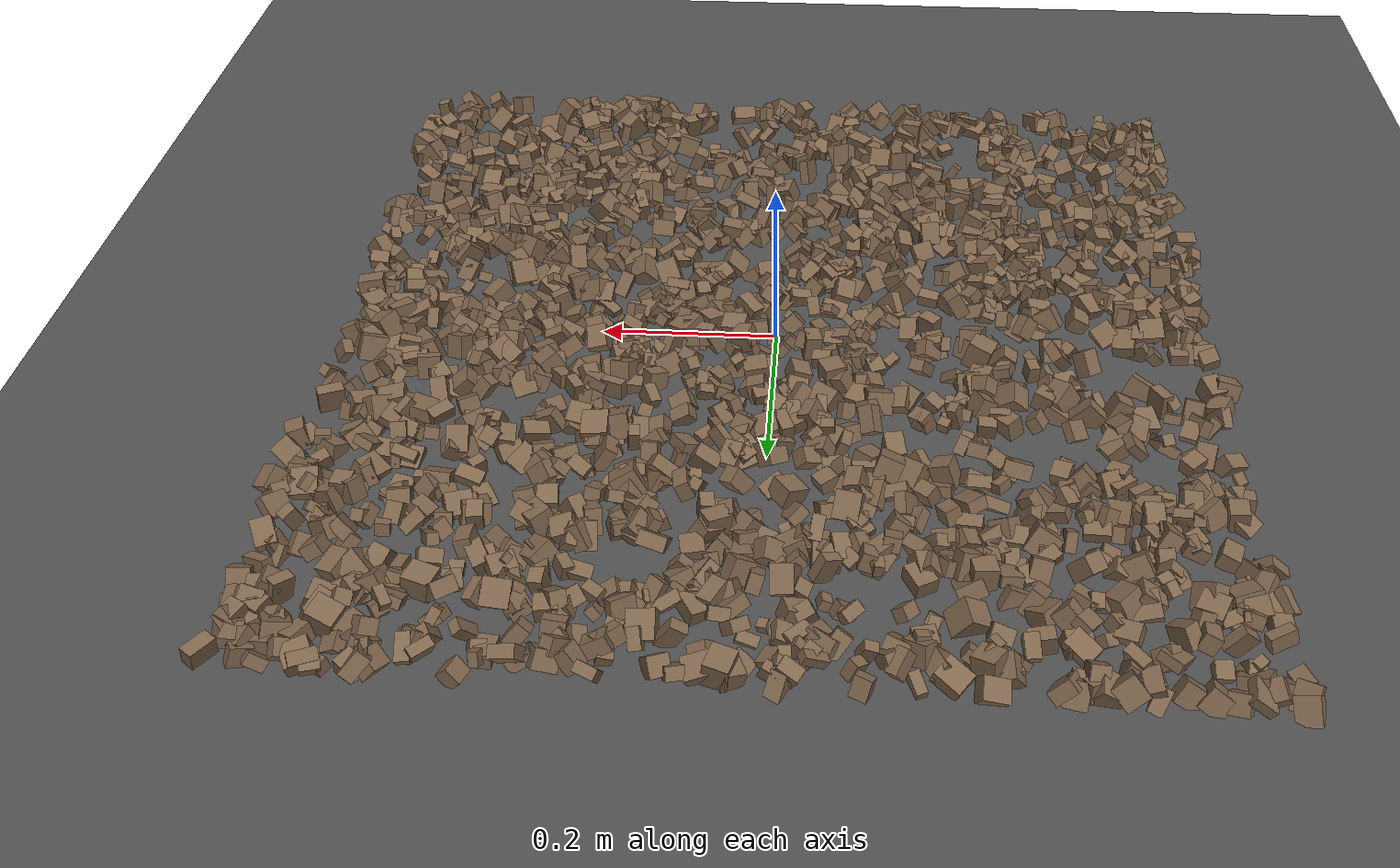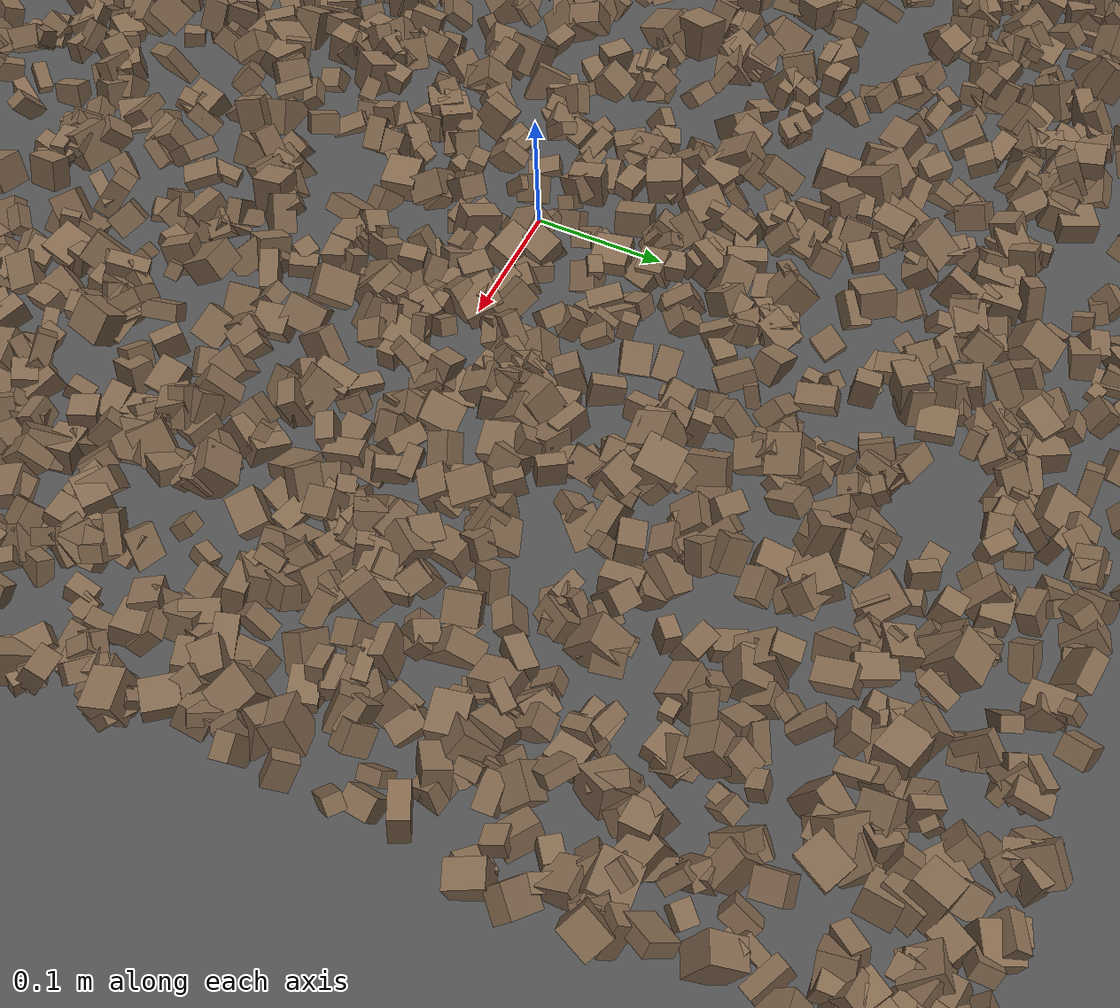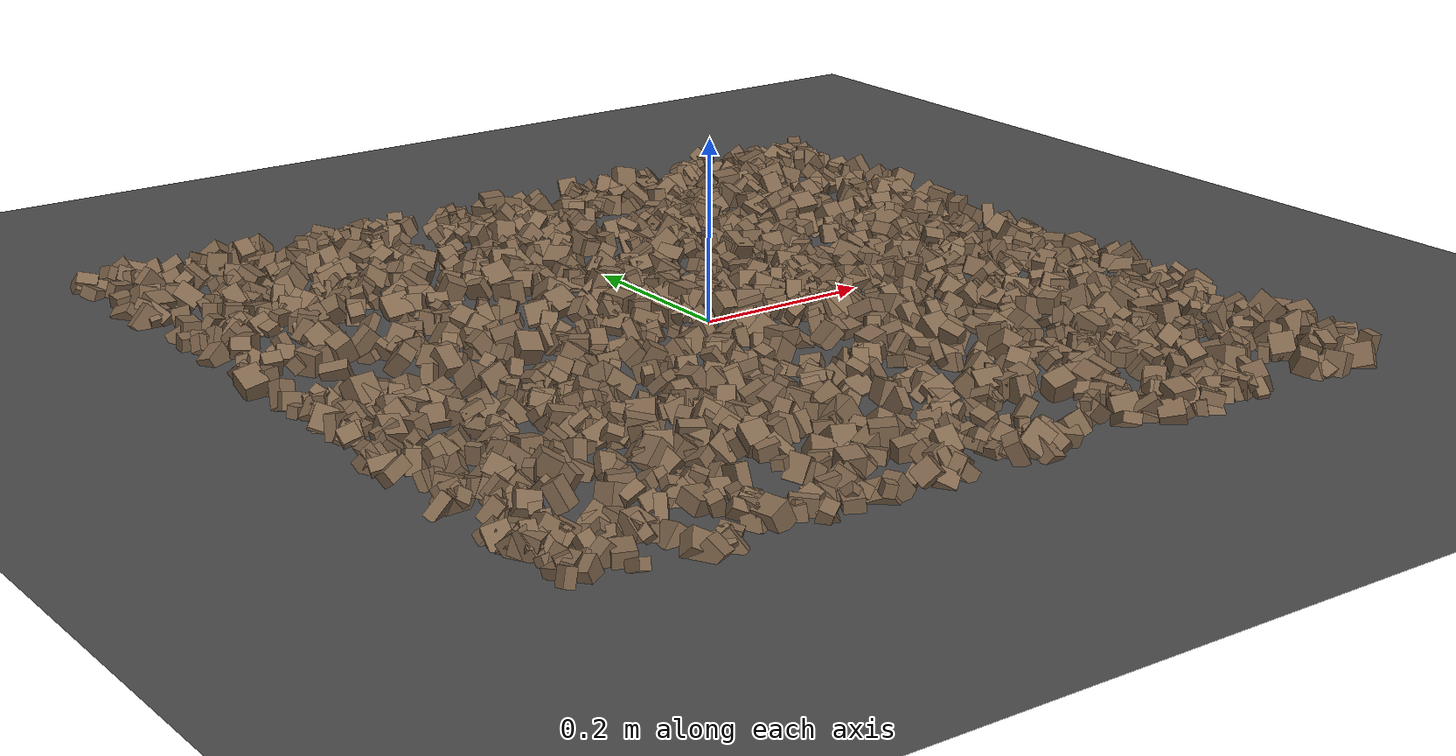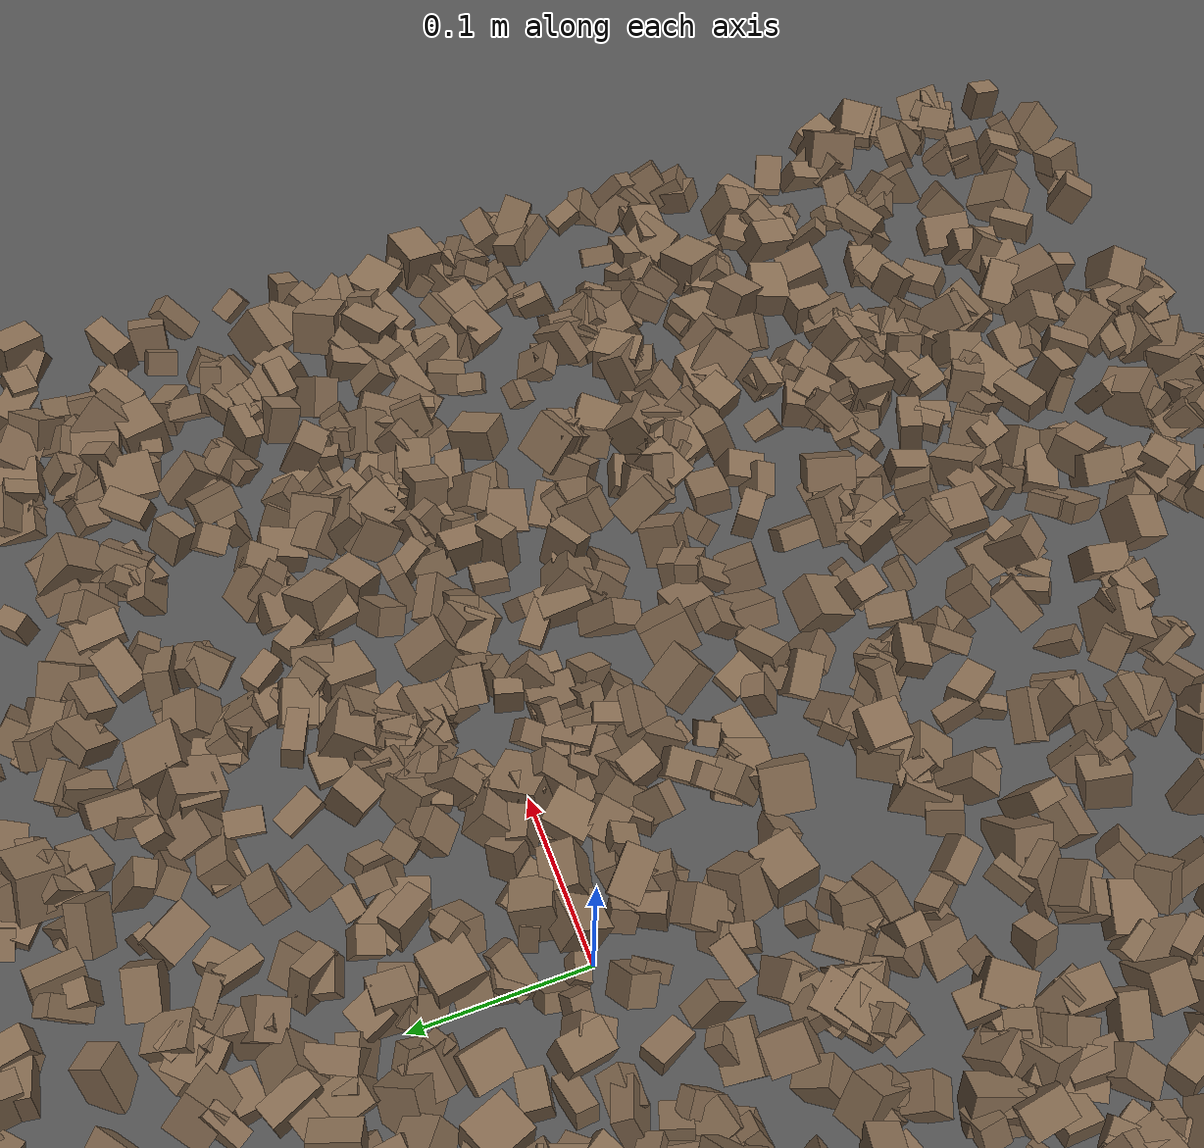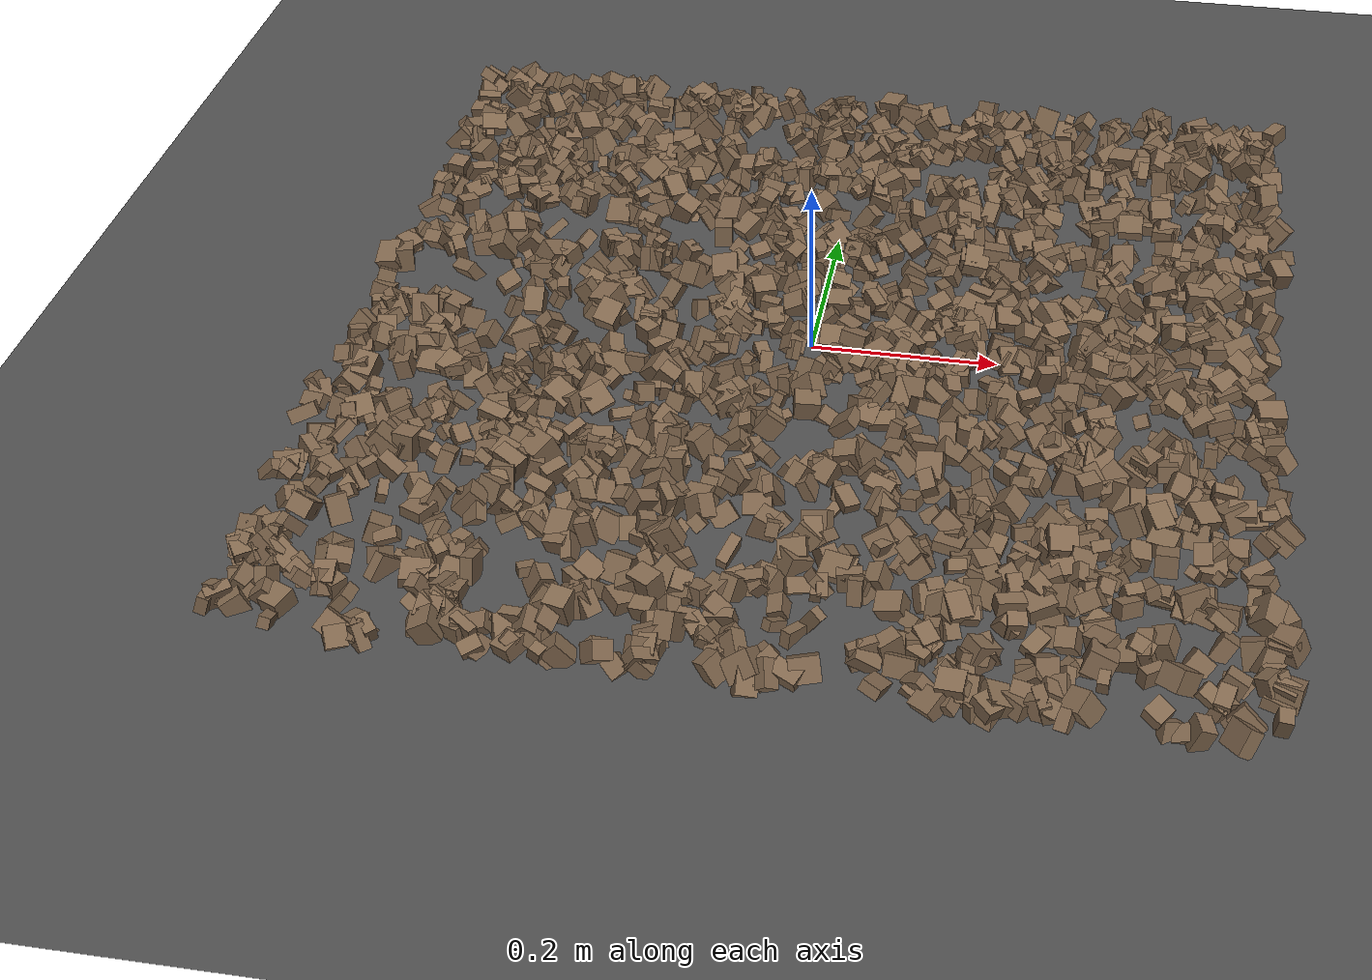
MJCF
<mujoco model="rocky_terrain_scene">
    <compiler angle="radian" inertiafromgeom="true" />
    <option timestep="0.002" gravity="0 0 -9.81" />

    <worldbody>
        <light name="sunlight" pos="5 5 5" dir="-1 -1 -1" diffuse="1 1 1" specular="0.5 0.5 0.5" ambient="0.5 0.5 0.5" />

        <geom name="ground_plane" type="plane" size="50 50 0.1" rgba="0.3 0.3 0.3 1" />

        <body name="rocky_terrain_body">

        <geom name="rock1" type="box" size="0.01002586169212991 0.012442035878451635 0.011739105609990965" pos="0.22968846236951945 0.3054443683814756 0.003601768221674547" quat="0.37127201870650617 0.04965857702213155 0.20449191127521377 0.37457749299614856" rgba="0.5 0.4 0.3 1" friction="0.7908568075704085 0.9246109363338522 0.8127385933102497" /><geom name="rock2" type="box" size="0.006747532297981147 0.012527765263269177 0.010050231173182144" pos="0.227901924720744 0.25125046339415347 0.014722653467708334" quat="0.4226046626427009 0.27241568776067376 0.01163023343526452 0.29334941616136073" rgba="0.5 0.4 0.3 1" friction="0.7518428442081784 0.9917773093155554 0.8845898751451782" /><geom name="rock3" type="box" size="0.013661011371763915 0.013231982762887833 0.007054277980593868" pos="0.10165443676997798 -0.3680550389611029 0.008961754386201413" quat="0.3066263877027534 0.20467829609779697 0.29048531203526706 0.1982100041641826" rgba="0.5 0.4 0.3 1" friction="0.776513216221958 0.9906259125454352 0.8622885280190395" /><geom name="rock4" type="box" size="0.007247565942949103 0.006453193018284076 0.007567801282875912" pos="-0.457948990411259 -0.24769954276041695 0.005214491689868582" quat="0.4092923771581521 0.28954494892128124 0.1466040072540361 0.15455866666653065" rgba="0.5 0.4 0.3 1" friction="0.7364837436242059 0.9801182834703537 0.8563122224104238" /><geom name="rock5" type="box" size="0.005492595653022148 0.011910835854914087 0.006245791695211292" pos="-0.18818410723040024 0.14589287396132578 0.001508513108725427" quat="0.3435474123104395 0.2695780497932184 0.2286356689234166 0.15823886897292544" rgba="0.5 0.4 0.3 1" friction="0.7055757871011882 0.9474940883507869 0.8987845325867456" /><geom name="rock6" type="box" size="0.008338267552634025 0.006559522538619307 0.010686161185232008" pos="0.27902034125999897 -0.01643824086446455 0.006709738441011139" quat="0.08829648825258606 0.3297169803020077 0.3281956609644553 0.25379087048095095" rgba="0.5 0.4 0.3 1" friction="0.744569719404472 0.9404429256725465 0.88762376483817" /><geom name="rock7" type="box" size="0.00959552637596814 0.009100481153019077 0.012174229178096324" pos="-0.25766085383961423 -0.15559227209652393 0.009947677515643119" quat="0.5095650542112468 0.2566866993482323 0.17907473854068545 0.05467350789983548" rgba="0.5 0.4 0.3 1" friction="0.7849807899467041 0.9452558425323114 0.8954125974573576" /><geom name="rock8" type="box" size="0.005053530512059039 0.007355346938968 0.0067475735357289245" pos="-0.03680711513894719 -0.1745734661514745 0.0018775518546048464" quat="0.034829910248986864 0.250645222756749 0.49630744678892513 0.21821742020533896" rgba="0.5 0.4 0.3 1" friction="0.7976828766128057 0.9054546131143961 0.8533564957059795" /><geom name="rock9" type="box" size="0.012318994301103923 0.0067520276737209235 0.01375420994388036" pos="0.4789214182756577 0.269427234635632 0.007520231809862883" quat="0.21326099283027541 0.151942665138772 0.17936935646100552 0.45542698556994704" rgba="0.5 0.4 0.3 1" friction="0.7310928456805663 0.9481561061126994 0.8765044980513844" /><geom name="rock10" type="box" size="0.012663186699125195 0.006729886033356858 0.006881731179368879" pos="-0.017237912504351582 0.09348509893092505 0.002958784108087603" quat="0.3278813747365382 0.02958124983406977 0.38121718166387425 0.26132019376551785" rgba="0.5 0.4 0.3 1" friction="0.7710766438648462 0.9222837805230539 0.8929985712272623" /><geom name="rock11" type="box" size="0.014148618414658302 0.012834341059026259 0.006382975899008243" pos="-0.4163975560485986 0.27756542281049423 0.004323397902299961" quat="0.31353069322913407 0.23165065736791576 0.19290271249149632 0.26191593691145393" rgba="0.5 0.4 0.3 1" friction="0.7219562461836341 0.9251696518094915 0.8214676645185744" /><geom name="rock12" type="box" size="0.00968497527789823 0.01431170631694047 0.011577620672658178" pos="0.052641819590321104 0.3722335204867445 0.0032185808508580086" quat="0.36311771328137366 0.11426544378188702 0.07184981775762118 0.4507670251791181" rgba="0.5 0.4 0.3 1" friction="0.7334602741624529 0.9644837943215747 0.8648205926078717" /><geom name="rock13" type="box" size="0.011740520148067087 0.006667560932019911 0.010382043402354402" pos="0.43558119572309906 -0.2806281541157962 0.013763071399064521" quat="0.00986590150604405 0.6274731494617579 0.1696028439503081 0.19305810508188986" rgba="0.5 0.4 0.3 1" friction="0.7267091247723386 0.9566781629488776 0.8856386665070917" /><geom name="rock14" type="box" size="0.005338607607272597 0.011508851148058614 0.011691724551826885" pos="0.31821591196745014 -0.10494336468024124 0.008097732801711256" quat="0.5345065264632455 0.12587772814531156 0.08886665326012974 0.25074909213131313" rgba="0.5 0.4 0.3 1" friction="0.7664471616632373 0.9835818548646217 0.8593112529594027" /><geom name="rock15" type="box" size="0.011478876805920923 0.011998462614668609 0.008660049653924036" pos="0.2582396686338877 -0.1909750819684085 0.004170331860222654" quat="0.2896402429097333 0.2943420726524756 0.13699552750279329 0.2790221569349978" rgba="0.5 0.4 0.3 1" friction="0.7796398592253005 0.9618057346543398 0.880174165804924" /><geom name="rock16" type="box" size="0.007268011652044609 0.014480562227853728 0.0050550159869498495" pos="0.009760606556388551 0.04065872812020066 0.00816929705485293" quat="0.10131660416747254 0.3007275274320053 0.43867455353623075 0.15928131486429145" rgba="0.5 0.4 0.3 1" friction="0.7269136655349796 0.9623802122405873 0.8844925953694494" /><geom name="rock17" type="box" size="0.009925316037586033 0.011402840616588576 0.0074241615085652735" pos="-0.08381120073440818 0.23992393814304847 0.002907040568250032" quat="0.45280942023180465 0.19364483780290542 0.31835106775483757 0.035194674210452394" rgba="0.5 0.4 0.3 1" friction="0.7551259502748912 0.9680598354465183 0.8812974762557404" /><geom name="rock18" type="box" size="0.006631951754902868 0.010557335371268031 0.005851966530090092" pos="-0.4116170394781373 -0.2502625744317162 0.007937233594875675" quat="0.03350337436662443 0.46452168280909073 0.29414730078295664 0.20782764204132811" rgba="0.5 0.4 0.3 1" friction="0.7782019150379355 0.9392734204953263 0.8158664344827073" /><geom name="rock19" type="box" size="0.0065583085021526585 0.010573202641586728 0.013744514809484864" pos="-0.17961455070960408 0.003952381297847585 0.0006027794851703605" quat="0.4442239586230169 0.0616375509180998 0.007132390110314864 0.4870061003485684" rgba="0.5 0.4 0.3 1" friction="0.7776385528948623 0.9788722131144959 0.8743686539613168" /><geom name="rock20" type="box" size="0.014646580785359815 0.010812471268162226 0.009714033762009114" pos="0.3863575747452822 -0.3941961390427824 0.008722261364405695" quat="0.10713358828864838 0.44302512460093246 0.3752142497780239 0.07462703733239529" rgba="0.5 0.4 0.3 1" friction="0.745779608660036 0.9468423654253249 0.8432442638397549" /><geom name="rock21" type="box" size="0.012764615536467693 0.005516304195582937 0.009448144457354904" pos="-0.09891580537355926 0.29104399445623186 0.004688809532919441" quat="0.2573313974555421 0.06310932431604507 0.12268972239389478 0.556869555834518" rgba="0.5 0.4 0.3 1" friction="0.7063436598437588 0.9347949669477484 0.8796147870857959" /><geom name="rock22" type="box" size="0.012059684522608239 0.006291440053455244 0.012778006354907242" pos="-0.22690119629794436 0.30654158367658846 0.008654489010294305" quat="0.04400881355293848 0.3442007105765731 0.2715501901309496 0.34024028573953885" rgba="0.5 0.4 0.3 1" friction="0.7420557079934377 0.9021425104811404 0.8581567217956203" /><geom name="rock23" type="box" size="0.009766808450862353 0.007127451017731677 0.012088075793619642" pos="0.18343263233826934 0.44448222120780057 0.007771308157724304" quat="0.4340845083502513 0.098363727965294 0.38976511284901477 0.07778665083543991" rgba="0.5 0.4 0.3 1" friction="0.7563595774273153 0.9532122595352682 0.8946347877286938" /><geom name="rock24" type="box" size="0.006280209883963415 0.006013247806722296 0.012721717608489525" pos="-0.060458815383219844 0.03290365803166506 0.005249609824347559" quat="0.1690057280333843 0.2952453960562817 0.29651772509546276 0.23923115081487137" rgba="0.5 0.4 0.3 1" friction="0.7006437689601501 0.9498782105022532 0.8256501503001921" /><geom name="rock25" type="box" size="0.01374667478609697 0.014425845398466725 0.013240127297564262" pos="0.20393705651421112 0.07381297801960596 0.0010847767768751343" quat="0.17447724339442103 0.27981515361106635 0.27337181404093297 0.27233578895357974" rgba="0.5 0.4 0.3 1" friction="0.7725299719599885 0.9314013790091591 0.8429714027194777" /><geom name="rock26" type="box" size="0.006515998780236516 0.013385528118214144 0.01212713754878733" pos="-0.02270796940627151 -0.06677673717016397 0.0050840223355950115" quat="0.2998325507116164 0.14583543310765468 0.27195527313626155 0.28237674304446747" rgba="0.5 0.4 0.3 1" friction="0.7915363529518588 0.9957146543801653 0.853745832139837" /><geom name="rock27" type="box" size="0.010387351804337992 0.006122002200192542 0.009269813054857794" pos="-0.01830215309000871 0.4687128687498404 0.00529613675129599" quat="0.23567045967854405 0.3872359296734192 0.2515612215680634 0.12553238907997338" rgba="0.5 0.4 0.3 1" friction="0.7976708515674822 0.9039849657282372 0.8111756042169147" /><geom name="rock28" type="box" size="0.014266324726228557 0.00933163224187716 0.006771726643773446" pos="0.3319348370082388 -0.3148888168268762 0.00356376421855799" quat="0.3813318616765234 0.3355044343605155 0.15476942868572593 0.12839427527723526" rgba="0.5 0.4 0.3 1" friction="0.7294135350897932 0.955457814098412 0.8514175551574573" /><geom name="rock29" type="box" size="0.014957421473815173 0.009400513160619763 0.012958988373296915" pos="0.40460004151575324 0.4349391340098735 0.010413628438360458" quat="0.37188792373269436 0.19839860537556395 0.17600714261916825 0.2537063282725735" rgba="0.5 0.4 0.3 1" friction="0.7008758846184658 0.9602038966039471 0.8054232224715637" /><geom name="rock30" type="box" size="0.01022677751599532 0.0068079934182855946 0.012239148388532208" pos="-0.07751046029167719 0.22403405704978407 0.007792491415317871" quat="0.16200396109391313 0.33141807381705246 0.40061074045925293 0.10596722462978145" rgba="0.5 0.4 0.3 1" friction="0.7136354320246802 0.9061723057819681 0.845853424448395" /><geom name="rock31" type="box" size="0.010850369238543893 0.005767161096902213 0.01156934969868791" pos="-0.20264577196433475 -0.18128872380634842 0.003973349423915005" quat="0.15236298608447976 0.17633620275626988 0.44321520326433533 0.22808560789491505" rgba="0.5 0.4 0.3 1" friction="0.7095624688254583 0.9059285484215593 0.8884388144505204" /><geom name="rock32" type="box" size="0.011430581094256813 0.00830940622181558 0.013627451321847915" pos="0.41963380885949464 -0.4970484753497755 0.0067034212000968985" quat="0.35724385740557263 0.0650462541906513 0.10493704285648874 0.47277284554728727" rgba="0.5 0.4 0.3 1" friction="0.7565897926050923 0.9518986993293956 0.8353163897221421" /><geom name="rock33" type="box" size="0.012884376885032231 0.010427365912148118 0.013395620577228002" pos="0.44838015338272275 0.4753656700184856 0.0016059371947658746" quat="0.413128427731648 0.0841760291023421 0.48574671208355613 0.016948831082453736" rgba="0.5 0.4 0.3 1" friction="0.7008338503507563 0.9541826532763715 0.8666277526470021" /><geom name="rock34" type="box" size="0.010004352433522629 0.0056435041300031555 0.012245539844196232" pos="-0.1122117357454736 -0.16700410496285767 0.013429019050079892" quat="0.08663247114303921 0.2487789051939846 0.4743231524804076 0.19026547118256862" rgba="0.5 0.4 0.3 1" friction="0.7724972583757205 0.9990169249038865 0.8088318868669676" /><geom name="rock35" type="box" size="0.00995621541519526 0.01047876907982363 0.009138941294548016" pos="0.3078525654321377 -0.19641397980150643 0.014752569542207548" quat="0.03337841655987307 0.36372109239389744 0.5795177821503619 0.023382708895867695" rgba="0.5 0.4 0.3 1" friction="0.7068604651082013 0.968157254638305 0.8582785794215642" /><geom name="rock36" type="box" size="0.00971848374242986 0.013065358800420052 0.01481063082014785" pos="-0.08878873082382266 -0.3331294684514705 0.014487060914685563" quat="0.32704568125417977 0.16381522056266276 0.20205286172474163 0.3070862364584158" rgba="0.5 0.4 0.3 1" friction="0.7833904068714496 0.9691761136545635 0.884410515091356" /><geom name="rock37" type="box" size="0.008500885508643957 0.008154696588615472 0.005542765050380681" pos="0.19499201307838065 -0.45771246273059174 0.014546412343284408" quat="0.20633472607213127 0.4656919131293392 0.09042516924711276 0.23754819155141665" rgba="0.5 0.4 0.3 1" friction="0.7598939655065803 0.9159754440271702 0.883349753381785" /><geom name="rock38" type="box" size="0.009734938023050536 0.007853265030521812 0.007762318005925216" pos="-0.42797230568854727 0.30921289786643236 0.012212225925415958" quat="0.3312124215951582 0.00974386634667476 0.10403032391033383 0.5550133881478332" rgba="0.5 0.4 0.3 1" friction="0.7048270185488943 0.9479530799574352 0.8634487175115562" /><geom name="rock39" type="box" size="0.008655151452295125 0.011868333977579481 0.008666487895199498" pos="0.2300742267449677 0.042142066477529716 0.012982940225317133" quat="0.33307611394036146 0.21205390975319033 0.030397264235076736 0.42447271207137144" rgba="0.5 0.4 0.3 1" friction="0.7415433507888314 0.9812582572059717 0.8253351511377057" /><geom name="rock40" type="box" size="0.006104403407900988 0.011022312308485195 0.008075294340360008" pos="0.14953513108212202 0.279578019389606 0.014481834294276796" quat="0.39549721389950865 0.09278565204452877 0.31123647457841525 0.20048065947754737" rgba="0.5 0.4 0.3 1" friction="0.7013115058362955 0.956852067313655 0.8851738641050345" /><geom name="rock41" type="box" size="0.012651983941031933 0.010946219879175049 0.005725942446325059" pos="0.09412916256279724 -0.3612818737075486 0.012913422113543398" quat="0.4675180638939127 0.44822587085321997 0.028157246445531393 0.05609881880733597" rgba="0.5 0.4 0.3 1" friction="0.7285483675120978 0.9823536397035549 0.8194201708388523" /><geom name="rock42" type="box" size="0.005462130205754059 0.01339651615984154 0.014725493778702598" pos="-0.01710637026723294 -0.42124836704464763 0.0003131858703456686" quat="0.25323246054939985 0.25328382409663813 0.20579206420294963 0.28769165115101236" rgba="0.5 0.4 0.3 1" friction="0.7006591161117854 0.9241613338852679 0.851104928500287" /><geom name="rock43" type="box" size="0.010297461131896448 0.011478569466239773 0.012187048567925516" pos="0.2960923963677522 0.3923604393954727 0.0023619005920393846" quat="0.29338398295046453 0.12038737763306628 0.2779084045744211 0.3083202348420481" rgba="0.5 0.4 0.3 1" friction="0.7255794154925485 0.9313042929603207 0.8949363400524994" /><geom name="rock44" type="box" size="0.007450047436747509 0.007589080356329656 0.007865947735556112" pos="-0.43305623717789565 0.10652144746040682 0.010991831491915032" quat="0.2749267873994589 0.0009012044887469626 0.41368109299927763 0.31049091511251653" rgba="0.5 0.4 0.3 1" friction="0.7522119950703807 0.9276035825104693 0.8285366211883388" /><geom name="rock45" type="box" size="0.013222784931114711 0.01065233863272811 0.013613649867450252" pos="-0.1885405908904504 -0.2625252474743498 0.007651537042673026" quat="0.21491063986841513 0.44807564508410136 0.18314071960908362 0.15387299543839994" rgba="0.5 0.4 0.3 1" friction="0.7308802598159001 0.9161303228007358 0.8516325989239069" /><geom name="rock46" type="box" size="0.005801397231889317 0.011374159693027573 0.011054175721375337" pos="0.06571357992853288 -0.36900346471589607 0.0066851977939773434" quat="0.6164947858305333 0.18862760184987976 0.11133329911560268 0.08354431320398417" rgba="0.5 0.4 0.3 1" friction="0.7466575552735414 0.9245453360572106 0.8796307020582647" /><geom name="rock47" type="box" size="0.006665000550099146 0.009519800937457133 0.011548911211724293" pos="0.34089124943655824 0.4005620640771631 0.004663304434509893" quat="0.18882548666786125 0.2648755173471156 0.3404532656007292 0.205845730384294" rgba="0.5 0.4 0.3 1" friction="0.7496454483871311 0.959448720228279 0.8775570839935707" /><geom name="rock48" type="box" size="0.012920848361105897 0.012459263303213943 0.012122329905293865" pos="0.4106005891451875 -0.23061476719742136 0.0016661031631546234" quat="0.13483850005210546 0.04374453361623626 0.38922255123872923 0.432194415092929" rgba="0.5 0.4 0.3 1" friction="0.7005462668908758 0.9188139045878934 0.8918835158204946" /><geom name="rock49" type="box" size="0.007667671665540783 0.010260216680550625 0.009287953992626705" pos="-0.1702065595083243 -0.20329524071591343 0.00957465384127033" quat="0.41141615927737096 0.2899135175072016 0.12092253362352548 0.1777477895919019" rgba="0.5 0.4 0.3 1" friction="0.7010934408045804 0.9718173914384013 0.8712381872357405" /><geom name="rock50" type="box" size="0.014807130873015942 0.014234166839528727 0.012277652551610348" pos="-0.4007603386029446 0.0008772734816228089 0.0036270462882591276" quat="0.27099557349783254 0.29173371401280224 0.2728504928858804 0.16442021960348485" rgba="0.5 0.4 0.3 1" friction="0.7252621572566169 0.9774299409517362 0.8547207588977958" /><geom name="rock51" type="box" size="0.009755025373618888 0.010342148898712603 0.014159483054507507" pos="0.09244621097851147 -0.11807111091532763 0.0019184385240886086" quat="0.20592583603563613 0.2514215519968008 0.23996753268144616 0.302685079286117" rgba="0.5 0.4 0.3 1" friction="0.7959650499998072 0.9652247595056471 0.8617346279675705" /><geom name="rock52" type="box" size="0.014130215942120446 0.014909642068936062 0.013944478350630507" pos="-0.3608606906843007 0.22894275735287262 0.0022046881324865" quat="0.16371782862508716 0.17321182795709653 0.3268322661533985 0.3362380772644178" rgba="0.5 0.4 0.3 1" friction="0.7050381011065678 0.9793894311201602 0.8437646949225717" /><geom name="rock53" type="box" size="0.01146374295456472 0.008867243480739554 0.014071368786876669" pos="-0.36506241075456713 -0.0667372385478503 0.006506346470463728" quat="0.4354479952238165 0.34741158786404114 0.059141866510705854 0.15799855040143648" rgba="0.5 0.4 0.3 1" friction="0.7581990355687414 0.9395485081169266 0.8405329915782656" /><geom name="rock54" type="box" size="0.009416856053990534 0.005830037773389776 0.008883719531013159" pos="0.30429078343371585 -0.32268624873056295 0.014045218801513484" quat="0.3530463303800565 0.18470805615406347 0.057560136934541574 0.40468547653133846" rgba="0.5 0.4 0.3 1" friction="0.7700478287610117 0.9013044175193421 0.8283664505900137" /><geom name="rock55" type="box" size="0.01242070143328745 0.011616224618507955 0.010922564614210716" pos="-0.02037522591057339 0.1341590625999628 0.0018052141037290686" quat="0.3017368567081936 0.1438479038251683 0.2941565394949086 0.26025869997172946" rgba="0.5 0.4 0.3 1" friction="0.7795240044794622 0.9947318695964965 0.8275430367673874" /><geom name="rock56" type="box" size="0.014492103649846329 0.011183437446180299 0.01004831194935149" pos="0.2522689642558609 -0.12603826632967874 0.01153567244796926" quat="0.35718142234793393 0.06804606145398054 0.31326174463990836 0.26151077155817715" rgba="0.5 0.4 0.3 1" friction="0.7198083170750825 0.970727690826727 0.8808960933659755" /><geom name="rock57" type="box" size="0.009881337503216594 0.014137321871825353 0.005265254589082768" pos="0.3852455822540196 0.22159638644173874 0.007868377421310626" quat="0.20513715747071662 0.3178973909360813 0.18174560154095593 0.2952198500522462" rgba="0.5 0.4 0.3 1" friction="0.7252805390607248 0.9514167725502006 0.861545761454675" /><geom name="rock58" type="box" size="0.010993658243483171 0.014773845801994374 0.014560028351955141" pos="0.4655330372545988 0.27478741821800345 0.010752811748882528" quat="0.07731076146303895 0.4243332901818495 0.11299737684238523 0.38535857151272634" rgba="0.5 0.4 0.3 1" friction="0.7498054703266803 0.9364688151534992 0.8940434137102916" /><geom name="rock59" type="box" size="0.005272630865924658 0.007586705289425293 0.005359213199432088" pos="-0.010328490602618534 0.42948303540628385 0.002374295886748844" quat="0.28697217695458854 0.2931525659888941 0.2627259418488759 0.15714931520764155" rgba="0.5 0.4 0.3 1" friction="0.7191766245319513 0.9764774924008947 0.8283628325117401" /><geom name="rock60" type="box" size="0.007979769483873612 0.013681153135570313 0.010871699761298342" pos="-0.05757535293564697 -0.39803778334316064 0.003267717200590438" quat="0.03141699201196336 0.4051960080575814 0.38025947332407173 0.18312752660638365" rgba="0.5 0.4 0.3 1" friction="0.7912965839114142 0.9907982238277202 0.8923128149137436" /><geom name="rock61" type="box" size="0.010185485348554364 0.008216005779608852 0.010481793608609326" pos="0.22396174349087616 0.4200580494973829 0.009222375514163762" quat="0.2543459062613693 0.04527635973531864 0.30328408412377394 0.397093649879538" rgba="0.5 0.4 0.3 1" friction="0.7536726006786196 0.9251358272245078 0.8612388116023751" /><geom name="rock62" type="box" size="0.012366522740064674 0.012913124962382862 0.006396834045409566" pos="0.03270593360200469 0.1901533632826099 0.005165803108096841" quat="0.21485635271019304 0.09567283168598045 0.1657765857126451 0.5236942298911814" rgba="0.5 0.4 0.3 1" friction="0.7147493033328135 0.9399141183945241 0.8531137734159078" /><geom name="rock63" type="box" size="0.00875892097149947 0.008055951953388015 0.011475743593759375" pos="0.23968854450253685 0.27517792227323623 0.006785967133926659" quat="0.1504969848365141 0.35853355169986206 0.21522284896685026 0.27574661449677346" rgba="0.5 0.4 0.3 1" friction="0.7728826965282721 0.9470167068391504 0.8574909582728392" /><geom name="rock64" type="box" size="0.006231612236329462 0.005861458331384018 0.00747030880142196" pos="0.3505563248165373 0.03744928571443307 0.010330894675433543" quat="0.27493038733880787 0.30829564471101756 0.25611675858134203 0.16065720936883252" rgba="0.5 0.4 0.3 1" friction="0.794174757736541 0.9240656985600214 0.8570258273452236" /><geom name="rock65" type="box" size="0.007925894469937404 0.012559637459801574 0.009337538399833513" pos="0.09019825269415094 -0.05975888746870672 0.013846672511717803" quat="0.4719962206543765 0.40288634568379916 0.03397048418536894 0.0911469494764554" rgba="0.5 0.4 0.3 1" friction="0.7690152972179691 0.9713735004587507 0.8402467463220864" /><geom name="rock66" type="box" size="0.010888648785104454 0.008339544604437784 0.0106501145042222" pos="0.49031315445200097 0.19662655308980037 0.0016939304810022948" quat="0.20554637430344233 0.03870228221196777 0.38590549878602676 0.369845844698563" rgba="0.5 0.4 0.3 1" friction="0.7920264820878165 0.981172266435467 0.8263604946283071" /><geom name="rock67" type="box" size="0.011571233628191516 0.010728211091883157 0.014229154432446111" pos="0.21489932712733317 0.08611151680641382 0.004895370697048218" quat="0.37458908202613017 0.17818379724411182 0.14495255886431435 0.3022745618654437" rgba="0.5 0.4 0.3 1" friction="0.7222843539470025 0.9190582787338432 0.8345634120457974" /><geom name="rock68" type="box" size="0.012280764028524719 0.014808909637794233 0.011658472066335138" pos="0.3176951068324143 -0.4829241739700897 0.007034558166153999" quat="0.34722921298345244 0.2956080416789478 0.07843005158988597 0.27873269374771376" rgba="0.5 0.4 0.3 1" friction="0.7052227184718027 0.9076169581098694 0.8964543554679473" /><geom name="rock69" type="box" size="0.010191542508373721 0.01271483685658584 0.00838329382462101" pos="0.19909328467658916 -0.4552741239338348 0.002972354691656746" quat="0.3279722879459865 0.13685901410181942 0.2656337877831939 0.2695349101690002" rgba="0.5 0.4 0.3 1" friction="0.7252071777533111 0.9243736027963785 0.8229361814054051" /><geom name="rock70" type="box" size="0.007883181751275389 0.007753049309644395 0.012357835158181072" pos="-0.048453275184381694 -0.43197363334079575 0.008753522843757265" quat="0.19597581345323148 0.2666756243993666 0.3033972579720045 0.23395130417539736" rgba="0.5 0.4 0.3 1" friction="0.7088923830064595 0.9759095618786452 0.8054924844311453" /><geom name="rock71" type="box" size="0.006631737828812765 0.013608323712544348 0.01144061604406434" pos="0.14913273296038287 -0.033047522944188 0.0068341890181098175" quat="0.06765325331987217 0.4965835527930591 0.03530558504307759 0.40045760884399106" rgba="0.5 0.4 0.3 1" friction="0.731671926304493 0.9385022819334038 0.8355066645317112" /><geom name="rock72" type="box" size="0.007692032349114139 0.007702836875021183 0.00506125504153419" pos="0.018337033843399242 -0.022079398619617496 0.00606819299891791" quat="0.18387418412736498 0.38408022099844535 0.23459379432711286 0.19745180054707673" rgba="0.5 0.4 0.3 1" friction="0.7453772778092934 0.9793856433931044 0.8180690513521648" /><geom name="rock73" type="box" size="0.012657588985436296 0.00539767319143219 0.008255201913932576" pos="-0.008467668736900191 0.021347795141085646 0.0012241031309614407" quat="0.08363771778775726 0.3936157760100266 0.3234939778442619 0.19925252835795415" rgba="0.5 0.4 0.3 1" friction="0.7855162742249666 0.9222137896308048 0.8780419480171785" /><geom name="rock74" type="box" size="0.007900413666869686 0.007481536009121012 0.007485148888342873" pos="0.10679371086749478 0.24505983595287384 0.00029817067924675975" quat="0.03190573694635468 0.5468465006797517 0.20568247814216054 0.21556528423173313" rgba="0.5 0.4 0.3 1" friction="0.7350220227193595 0.9032537280768533 0.8798577018658759" /><geom name="rock75" type="box" size="0.005037287137509647 0.011166210668873931 0.009888230417744677" pos="-0.4847638476975987 0.47310819621849676 0.002176260631801131" quat="0.34768922292332816 0.23280277744752795 0.3964971338915244 0.023010865737619464" rgba="0.5 0.4 0.3 1" friction="0.7191926372908286 0.9198278261947082 0.8323421934828065" /><geom name="rock76" type="box" size="0.01012664048187371 0.005965974799156345 0.010097656093092364" pos="0.33367973891416813 -0.0085354555132926 0.009759825225794059" quat="0.3228852931874228 0.2271973144199798 0.14579828949628765 0.30411910289630983" rgba="0.5 0.4 0.3 1" friction="0.7171497538769116 0.9314598372586552 0.8165651446557219" /><geom name="rock77" type="box" size="0.011066655991523195 0.009853969609164456 0.011308496220025041" pos="-0.4876178181897566 0.10845456338381987 0.008104796457720389" quat="0.03364974757549411 0.18083719997912887 0.3916149005418394 0.3938981519035377" rgba="0.5 0.4 0.3 1" friction="0.7269863095022171 0.9908463394114165 0.8226871696592306" /><geom name="rock78" type="box" size="0.007641048532443784 0.013130640612200092 0.01391242556638336" pos="0.2879769614029899 -0.18636938976500939 0.006930395662931109" quat="0.42192520162699526 0.013029447805774075 0.12767046617276276 0.4373748843944679" rgba="0.5 0.4 0.3 1" friction="0.7584447646175456 0.9064237093673579 0.8363881002410412" /><geom name="rock79" type="box" size="0.012955191454096234 0.006526801903535466 0.013021003306784993" pos="0.050678426924177344 0.3727490798725641 0.0072300187965178815" quat="0.20008762452331527 0.5056054006146818 0.2884675087880645 0.005839466073938498" rgba="0.5 0.4 0.3 1" friction="0.7942951006081613 0.9781208229411027 0.8497291068906888" /><geom name="rock80" type="box" size="0.00867957610745026 0.006251111948932409 0.01141157338100234" pos="-0.48438556970259217 -0.04532409651694025 0.006314812228328397" quat="0.20872997951861147 0.0650316353676581 0.10084965000205011 0.6253887351116804" rgba="0.5 0.4 0.3 1" friction="0.7704121868696573 0.9666130803111335 0.804635034691113" /><geom name="rock81" type="box" size="0.011158845144706421 0.009737740911105273 0.012915742764141747" pos="-0.21167963804824041 -0.46494559514556577 0.0035151440970424223" quat="0.3051157990896664 0.5254969665961096 0.1518696480598679 0.01751758625435622" rgba="0.5 0.4 0.3 1" friction="0.7807871424654157 0.9937739269592761 0.8705741581611486" /><geom name="rock82" type="box" size="0.010435720487980736 0.013006527198547457 0.010325120316642289" pos="-0.35231028634613415 0.231150823841751 0.009069074702798946" quat="0.07127589221942786 0.3282691923527684 0.21372066982598842 0.38673424560181524" rgba="0.5 0.4 0.3 1" friction="0.7420826851128993 0.9326079540360849 0.8340252647578628" /><geom name="rock83" type="box" size="0.011567400644095033 0.005431481370072456 0.012162394231774697" pos="-0.36887821778044727 -0.2680879195848438 0.008119254429422771" quat="0.3027152543314499 0.09326573980099429 0.3812984587596729 0.22272054710788286" rgba="0.5 0.4 0.3 1" friction="0.7011259845883296 0.9203541268795166 0.8245730338023222" /><geom name="rock84" type="box" size="0.01194361831049445 0.005971755407094413 0.010522350853788078" pos="0.22172439884059136 0.42058983546866957 0.004612277628247525" quat="0.09531420422983213 0.271969173348017 0.33572864521966683 0.2969879772024841" rgba="0.5 0.4 0.3 1" friction="0.7786083979453837 0.9017910980024383 0.8885908230263337" /><geom name="rock85" type="box" size="0.009408312870761468 0.009826873104563373 0.011074427022081378" pos="-0.11369977402379938 0.05379597572737771 0.0013839118624384516" quat="0.07525502381265908 0.7377626853949455 0.15066196227059153 0.036320328521803856" rgba="0.5 0.4 0.3 1" friction="0.7076098220243626 0.9113262758114817 0.829518759839829" /><geom name="rock86" type="box" size="0.01086399644969006 0.009875604637148878 0.0073915487818891415" pos="0.11332589572775797 -0.25911413825927276 0.0019355123502317823" quat="0.22528012752693277 0.17364629687625616 0.39513293360142365 0.2059406419953875" rgba="0.5 0.4 0.3 1" friction="0.716836735291938 0.962232518032265 0.8348766017257243" /><geom name="rock87" type="box" size="0.01348977577933548 0.007896594408183896 0.006741035402927539" pos="-0.10909391617747266 -0.03219821388387234 0.0084998425329377" quat="0.22774493877568097 0.25389662816478203 0.3697060123467671 0.14865242071277" rgba="0.5 0.4 0.3 1" friction="0.7521123207315967 0.9235645496232093 0.8842022550050184" /><geom name="rock88" type="box" size="0.011896932157663024 0.007793392789114118 0.009629160437108947" pos="-0.347217602182592 0.42645811045097093 0.010675201050614171" quat="0.02892491696284601 0.14464628883639827 0.4832078967478011 0.34322089745295453" rgba="0.5 0.4 0.3 1" friction="0.7642858434274982 0.9100189460963142 0.8660550517379214" /><geom name="rock89" type="box" size="0.008141274767117537 0.011935668953784296 0.00538820771252961" pos="0.2132985892985919 0.2092810931840171 0.00042916319469538496" quat="0.397318110099152 0.3140393591105469 0.20053227628719242 0.08811025450310873" rgba="0.5 0.4 0.3 1" friction="0.7854796405516755 0.9525726023443791 0.8692090548867988" /><geom name="rock90" type="box" size="0.013633079004193246 0.00839991571955986 0.012199526808872128" pos="-0.10299040719797448 -0.029280142469169546 0.004287678295339973" quat="0.32342914963328895 0.34323772465073066 0.2667460826464221 0.06658704306955837" rgba="0.5 0.4 0.3 1" friction="0.7472922865035149 0.9351035299766758 0.8308079868177337" /><geom name="rock91" type="box" size="0.00770075774743318 0.011124463263158071 0.012018958535523143" pos="0.42336303178250423 0.1197452685673327 0.004654909306208482" quat="0.28812455477809445 0.37044497295914763 0.24102281707218928 0.10040765519056864" rgba="0.5 0.4 0.3 1" friction="0.7386829400635918 0.9476949895583073 0.8415182908510735" /><geom name="rock92" type="box" size="0.012628363751714236 0.011969342933655328 0.008530669593444491" pos="-0.39735462657003506 0.42682781947525306 0.011681650353008582" quat="0.04582789889242755 0.2729010179908539 0.28056743442633086 0.4007036486903877" rgba="0.5 0.4 0.3 1" friction="0.7944856218643611 0.9777458670498829 0.8398620353906933" /><geom name="rock93" type="box" size="0.013008188496236646 0.013354542349419303 0.009534746075712905" pos="-0.48269386050538154 0.08191081603105 0.010092063909287944" quat="0.2313580121956911 0.18197712315223796 0.31715860726348927 0.2695062573885817" rgba="0.5 0.4 0.3 1" friction="0.7608073427074771 0.9358404220061343 0.8199040418680211" /><geom name="rock94" type="box" size="0.008890384380486484 0.01220025511553367 0.01090633668829644" pos="-0.36329417525559304 0.21998658213809752 0.009505847623523486" quat="0.2946965518982813 0.3460602991625663 0.19101263082106862 0.16823051811808368" rgba="0.5 0.4 0.3 1" friction="0.785112143090804 0.9983893131985425 0.8136637618950577" /><geom name="rock95" type="box" size="0.012589900370936982 0.014048226494882531 0.01459492486267638" pos="-0.3153388371090321 0.10505381327010144 0.012909143985252978" quat="0.046768528227365616 0.2312553289551953 0.4222228294505733 0.2997533133668657" rgba="0.5 0.4 0.3 1" friction="0.75259647098275 0.9463367890343766 0.8480570231313425" /><geom name="rock96" type="box" size="0.00795366798148379 0.005837194459286299 0.005364960711870323" pos="0.37245783181996184 -0.059307573088572485 0.012063805488117888" quat="0.1479380886788627 0.4771840768973584 0.3492303521314699 0.025647482292308964" rgba="0.5 0.4 0.3 1" friction="0.7007935800008177 0.9089330238120084 0.8713913301376539" /><geom name="rock97" type="box" size="0.008692354727708972 0.0058877895733852065 0.0076365410947906425" pos="-0.4580515428644356 -0.03225836123662984 0.010870435614575" quat="0.1377429259507411 0.4927146650598848 0.30061190592431314 0.06893050306506093" rgba="0.5 0.4 0.3 1" friction="0.7921607915785507 0.9048664968445546 0.886683625329572" /><geom name="rock98" type="box" size="0.01030531295666583 0.0072293364217432396 0.0107059196668874" pos="0.03967833977429647 0.13250742436868201 0.0093024560406658" quat="0.0825085857514756 0.04978294479638572 0.48724682148763604 0.38046164796450255" rgba="0.5 0.4 0.3 1" friction="0.7657150585735022 0.9990069834653839 0.8360262578457858" /><geom name="rock99" type="box" size="0.008077330881372486 0.013168533801704914 0.00860896462708687" pos="-0.11139833087943729 -0.32148540908237655 0.014490971966092215" quat="0.18496705298722452 0.2202654937812014 0.3552840358881206 0.23948341734345344" rgba="0.5 0.4 0.3 1" friction="0.7304598679728566 0.9698918388086557 0.8841662279843234" /><geom name="rock100" type="box" size="0.010518846084215282 0.009512918641672398 0.00794430636023575" pos="0.2662496903524755 0.4991977050783565 0.0050680576506769905" quat="0.141424151530131 0.41307797928451445 0.28910333644103275 0.15639453274432172" rgba="0.5 0.4 0.3 1" friction="0.719621092806008 0.9193848366834644 0.8268971516229836" /><geom name="rock101" type="box" size="0.008415880680783326 0.008770676891431439 0.009330507517726922" pos="-0.16696061279757612 0.026644432994387235 0.001211681156474123" quat="0.10526286250494117 0.34898839695781675 0.3100224485671756 0.23572629197006648" rgba="0.5 0.4 0.3 1" friction="0.7734649020090262 0.9175131978933886 0.8915923551413931" /><geom name="rock102" type="box" size="0.01266417643214462 0.014469009203168546 0.014961924405769857" pos="0.38282699963072464 0.3852548455849719 0.0107686331952083" quat="0.5007336221843107 0.22983332501575962 0.2193569085469151 0.050076144253014675" rgba="0.5 0.4 0.3 1" friction="0.7067624954468956 0.9721613898863747 0.8145858351435737" /><geom name="rock103" type="box" size="0.010378685796867484 0.013995377013288745 0.011916557711353092" pos="-0.3924670717335691 -0.40433558949878323 0.001696774695084312" quat="0.172464892412435 0.2754912900955478 0.3065086934180096 0.24553512407400757" rgba="0.5 0.4 0.3 1" friction="0.7280347344130246 0.9420942083992665 0.8382247318088328" /><geom name="rock104" type="box" size="0.012894030964869078 0.014484838863642182 0.012670804495796044" pos="-0.14839903769592155 0.10367587350522578 0.00485778532646464" quat="0.2657882744627136 0.3403916711806531 0.04249285242427938 0.351327201932354" rgba="0.5 0.4 0.3 1" friction="0.7796029939786824 0.9586003406989825 0.8425673298102471" /><geom name="rock105" type="box" size="0.01341649315728919 0.007377281913672764 0.01258095453165108" pos="-0.11384349021550355 -0.41182130613678314 0.004854476407463605" quat="0.1207459403120202 0.1898758938754144 0.38663082190513826 0.30274734390742725" rgba="0.5 0.4 0.3 1" friction="0.7420929819757832 0.9089322413599951 0.8730019497798308" /><geom name="rock106" type="box" size="0.008488005314322982 0.012752675613942907 0.011673593832517464" pos="-0.3902994570067462 -0.2018964042502016 0.011621434867219336" quat="0.30312060359788545 0.11136182248422116 0.28314070504506866 0.30237686887282467" rgba="0.5 0.4 0.3 1" friction="0.7827069650284976 0.9376953421300009 0.8149744810060626" /><geom name="rock107" type="box" size="0.012555535157204761 0.012461779336717929 0.01196491053182917" pos="-0.21644561972162624 0.36269561417637775 0.013821693347891507" quat="0.4363872210723731 0.49292465830521126 0.018697935373465993 0.051990185248949584" rgba="0.5 0.4 0.3 1" friction="0.7009698077488207 0.9547904317251386 0.8828745041714536" /><geom name="rock108" type="box" size="0.011850072375497744 0.005660756128240575 0.014964145371673468" pos="0.3225382222536993 -0.33724332392145107 0.005316104041784268" quat="0.041899491183266205 0.37502466678914914 0.2433358682063317 0.33973997382125304" rgba="0.5 0.4 0.3 1" friction="0.709698305964256 0.9267929154860638 0.8038757453909237" /><geom name="rock109" type="box" size="0.01412914618142876 0.0063324438361914825 0.008393824210122774" pos="0.3189095197980981 -0.23828628850182842 0.0023942291044562257" quat="0.26845648288444096 0.16351466191568484 0.21503393283980674 0.3529949223600676" rgba="0.5 0.4 0.3 1" friction="0.7838806944739249 0.9188494158325718 0.8619644939690739" /><geom name="rock110" type="box" size="0.0064097016957911195 0.008262742341116323 0.009997385349323528" pos="0.18687982579656714 0.3703231197742489 0.008203084758523313" quat="0.38806350510410403 0.3884438314161369 0.05863355250995989 0.16485911096979924" rgba="0.5 0.4 0.3 1" friction="0.7332645524186682 0.9471017051307252 0.8878000417904673" /><geom name="rock111" type="box" size="0.014659832926966643 0.00738294211685705 0.00595662771200425" pos="0.4823698208534509 0.3811059478986035 0.007934707852754273" quat="0.061953798526156484 0.14586129688763372 0.33443083107501326 0.45775407351119657" rgba="0.5 0.4 0.3 1" friction="0.7576554358852746 0.9471248200717115 0.8223084683186138" /><geom name="rock112" type="box" size="0.014182595247052232 0.008046208940898731 0.005544009295496753" pos="-0.46513528670317983 -0.001408893447295556 0.013820889042028276" quat="0.4687069966742657 0.03748230603717797 0.284717641796858 0.20909305549169838" rgba="0.5 0.4 0.3 1" friction="0.7374823057486548 0.9794363610296453 0.8743443611428231" /><geom name="rock113" type="box" size="0.008832905357749238 0.008908186713179785 0.00827886246919027" pos="-0.09031523922481344 0.34274186781543514 0.001368194058082859" quat="0.13867957256607652 0.16325192541855965 0.42333357099433694 0.274734931021027" rgba="0.5 0.4 0.3 1" friction="0.7455474595131709 0.9763633193190845 0.8731678146058972" /><geom name="rock114" type="box" size="0.006434582076406042 0.012248506713995338 0.007307603118305368" pos="0.28412389512783176 -0.25257411036696076 0.006296115968259843" quat="0.1139028828602921 0.20038555485781953 0.2502797423588488 0.4354318199230396" rgba="0.5 0.4 0.3 1" friction="0.7269442908691245 0.9400581215396754 0.8490344537316037" /><geom name="rock115" type="box" size="0.014002252029275106 0.013156560218334813 0.008055607928613012" pos="0.4557181314009421 -0.49618786552590133 0.007200776678064191" quat="0.17451506581307 0.19414405279319852 0.4538940983841345 0.177446783009597" rgba="0.5 0.4 0.3 1" friction="0.7846479114541436 0.9502121032579972 0.8927592070716148" /><geom name="rock116" type="box" size="0.010669077608095729 0.0070575957141702055 0.01001802089803801" pos="0.13724006028549418 0.1470077828259546 0.003184310198032328" quat="0.07000711852145663 0.450960508921433 0.3962116286737093 0.08282074388340102" rgba="0.5 0.4 0.3 1" friction="0.7822674639437694 0.9037462232146035 0.8464430322697228" /><geom name="rock117" type="box" size="0.005822057113423743 0.014528252409803995 0.005818863968179531" pos="0.4929538633311018 -0.4316541483324141 0.009312924251718958" quat="0.2654991111887182 0.043462609044180756 0.3945556246292564 0.29648265513784466" rgba="0.5 0.4 0.3 1" friction="0.7883347046000322 0.9943758032511305 0.8099495407469318" /><geom name="rock118" type="box" size="0.014268736380552045 0.008658532938635319 0.01168262465542743" pos="-0.15627158524231544 0.37052433902455706 0.011197848566846066" quat="0.19869816162562534 0.1732024193839595 0.31416893655558725 0.3139304824348279" rgba="0.5 0.4 0.3 1" friction="0.7240013962756503 0.9871584389574 0.8239380773374614" /><geom name="rock119" type="box" size="0.01183365891659775 0.008743209754960402 0.01327783342665563" pos="0.3987138597829354 -0.14558937971233643 0.012465661547383345" quat="0.06064350644976741 0.025816284556677612 0.6371586864301884 0.27638152256336657" rgba="0.5 0.4 0.3 1" friction="0.792410726221905 0.9420580526030118 0.8918162433181321" /><geom name="rock120" type="box" size="0.008713888938879755 0.005962813710962212 0.014395724261614971" pos="-0.22778551320378893 -0.14335293453638487 0.0044865026221146825" quat="0.1144967056133372 0.5054086273227979 0.3456774167394626 0.0344172503244022" rgba="0.5 0.4 0.3 1" friction="0.7471047619795319 0.9849285591988308 0.8024926605289694" /><geom name="rock121" type="box" size="0.009079926344891721 0.005581413287995677 0.01026032699046971" pos="0.429761706687362 0.17840769610539842 0.003777124426635777" quat="0.2155485931337301 0.3246232561042107 0.43442609360712636 0.025402057154932763" rgba="0.5 0.4 0.3 1" friction="0.7055888069198147 0.9988655825296416 0.8794449028977033" /><geom name="rock122" type="box" size="0.009722737824587846 0.012149930709295334 0.013218955975810645" pos="0.49941051222944577 -0.2290475285650616 0.006506581257314986" quat="0.2354292880122642 0.31357760319272804 0.3869991095860238 0.06399399920898392" rgba="0.5 0.4 0.3 1" friction="0.7085338265399852 0.9431615762915503 0.8006557240770821" /><geom name="rock123" type="box" size="0.008571170478562649 0.006825518780321154 0.0075551031679508595" pos="-0.04242545946140308 -0.1526377724490091 0.01417425336699208" quat="0.015394321856984902 0.40469585048673773 0.45405918707449217 0.1258506405817852" rgba="0.5 0.4 0.3 1" friction="0.7684976968560427 0.9905374278554796 0.8710401291497958" /><geom name="rock124" type="box" size="0.005254329176774849 0.01231323193520851 0.011923842931431904" pos="-0.014328653775880773 0.1965661681937808 0.009007554467927557" quat="0.20666047490194506 0.13388126381787407 0.24293994939372193 0.41651831188645905" rgba="0.5 0.4 0.3 1" friction="0.7176690677706536 0.9677091091807728 0.8504916364036025" /><geom name="rock125" type="box" size="0.009010707845718571 0.014898016431078923 0.014286056356770601" pos="0.36334597259326795 0.11901327153865915 0.004359854626680577" quat="0.6191292565361844 0.2835218113110099 0.06455844389383951 0.032790488258966036" rgba="0.5 0.4 0.3 1" friction="0.722844146225053 0.9532394746658259 0.8231350403469875" /><geom name="rock126" type="box" size="0.0074278723828150265 0.010410426727443045 0.006693389149474231" pos="0.11005455029623035 -0.1387974948727222 0.010716662721434558" quat="0.05146260144439988 0.12354503021455437 0.5023437066547639 0.3226486616862819" rgba="0.5 0.4 0.3 1" friction="0.74218671519432 0.9159777112646665 0.8176284767387734" /><geom name="rock127" type="box" size="0.013799916236726727 0.014469048438529399 0.008276393907474035" pos="0.1507014018919569 0.060354976137549365 0.004269879382633766" quat="0.13106977936876554 0.4053754299624467 0.22262346254092086 0.24093132812786697" rgba="0.5 0.4 0.3 1" friction="0.7390577733733534 0.9274333598522352 0.8722611105121045" /><geom name="rock128" type="box" size="0.007119473014165213 0.011146363966899199 0.007617395047822502" pos="0.20571609877342223 -0.24264743757348461 0.008115023047654796" quat="0.3462335446822374 0.30963598136513015 0.022912630052591584 0.3212178439000408" rgba="0.5 0.4 0.3 1" friction="0.7935203663065171 0.9936284380809932 0.8266697596291903" /><geom name="rock129" type="box" size="0.005120358696042362 0.01030548799965822 0.012434346818285332" pos="-0.18830948327060237 0.33846562324102025 0.005923662680115724" quat="0.39723505716019325 0.14177420300329757 0.38036149635536864 0.08062924348114056" rgba="0.5 0.4 0.3 1" friction="0.7191239669582131 0.9579737882088918 0.8355814652680452" /><geom name="rock130" type="box" size="0.007167652239419224 0.008568971137076822 0.008393585508257216" pos="0.39149990210141716 0.4958463081071943 0.0019517621454766593" quat="0.29207277076651494 0.32876496502749675 0.21586055578684285 0.16330170841914554" rgba="0.5 0.4 0.3 1" friction="0.7611090394659855 0.9724616089377196 0.8705395468208778" /><geom name="rock131" type="box" size="0.006338312369339263 0.01059404553428812 0.007071422603797072" pos="0.30389037983605705 -0.49810193750475107 0.00487981961232902" quat="0.07630256091542692 0.09774947349859367 0.6169449365745191 0.20900302901146034" rgba="0.5 0.4 0.3 1" friction="0.70350557225375 0.9791497612008788 0.8289869326270797" /><geom name="rock132" type="box" size="0.006963816121776621 0.0144923097914386 0.01266446064683334" pos="-0.13776168152183554 0.2488228673490518 0.0018737719551078801" quat="0.25538734206355324 0.22462242370457347 0.3625378603000072 0.157452373931866" rgba="0.5 0.4 0.3 1" friction="0.7354913896445092 0.9266156147400726 0.8994844920993306" /><geom name="rock133" type="box" size="0.01245635859193386 0.005927252228859953 0.011102202183409161" pos="0.4354895479191486 -0.06297740645944683 0.010818135594283119" quat="0.23098569766325605 0.5594525753995114 0.08827540226436112 0.12128632467287144" rgba="0.5 0.4 0.3 1" friction="0.7884084400387698 0.916539026355917 0.8860257000056125" /><geom name="rock134" type="box" size="0.014564459900528657 0.014934872644499136 0.005420103622017677" pos="0.1195696723362275 -0.45353884149336077 0.010993619605879868" quat="0.41708534314967893 0.38766834425650876 0.07537396086580224 0.11987235172801013" rgba="0.5 0.4 0.3 1" friction="0.7543942059950207 0.9413384223693047 0.8842063991028205" /><geom name="rock135" type="box" size="0.012962717573447066 0.007393002725503724 0.0063445494014720515" pos="0.009245910892866194 -0.29840868017676536 0.010258910075050021" quat="0.27797321519863083 0.19467668647278777 0.3499366852524754 0.177413413076106" rgba="0.5 0.4 0.3 1" friction="0.7174192140791749 0.9866215836018004 0.8705461702386332" /><geom name="rock136" type="box" size="0.008235976859035838 0.007757842144885516 0.012445214588595403" pos="0.21723940285170418 0.4499133846847867 0.0031115891084867015" quat="0.06226792173200323 0.39468247567772297 0.33483211069036733 0.20821749189990643" rgba="0.5 0.4 0.3 1" friction="0.7019862903947983 0.975760101164637 0.8168009442101442" /><geom name="rock137" type="box" size="0.007211545996404162 0.006220723478562591 0.005838217762230895" pos="-0.2940692028430064 -0.09995160047981577 0.0055920518947490646" quat="0.3167363897806789 0.3283870880315655 0.31192769543216065 0.04294882675559492" rgba="0.5 0.4 0.3 1" friction="0.75304050062934 0.9010775836008713 0.865930064231932" /><geom name="rock138" type="box" size="0.01475431287982144 0.01084117858640645 0.01033639792140134" pos="0.10702205417954236 -0.0728056464824618 0.007610139506909542" quat="0.13829237559142468 0.38502969282062427 0.18544977976150542 0.2912281518264456" rgba="0.5 0.4 0.3 1" friction="0.7090909804530113 0.9927668362298412 0.8020088248779387" /><geom name="rock139" type="box" size="0.011071290294295861 0.013325606392665813 0.006802628875649844" pos="0.46205009575823786 0.47983236981838073 0.008808894445290713" quat="0.23282008376735955 0.32258509205642744 0.2792291680995333 0.16536565607667975" rgba="0.5 0.4 0.3 1" friction="0.7497362310304303 0.9961671817223852 0.8203999435780778" /><geom name="rock140" type="box" size="0.009997588053094544 0.00608044812130604 0.005123769670734864" pos="-0.280961864665761 -0.24538843272657263 0.008844936794982295" quat="0.03639460054507299 0.31418278133965055 0.4152204354698785 0.234202182645398" rgba="0.5 0.4 0.3 1" friction="0.7073294599579444 0.936752233324406 0.8012940076104244" /><geom name="rock141" type="box" size="0.014256881466331417 0.009840854044513455 0.008716401078383462" pos="0.2854589766113569 0.3477816130850283 0.014601199745032573" quat="0.17824696020244113 0.3019056177318067 0.25875451297129015 0.26109290909446203" rgba="0.5 0.4 0.3 1" friction="0.7668225621839502 0.9240363280180617 0.8661574756023376" /><geom name="rock142" type="box" size="0.006338352825308746 0.007130785167446309 0.007825267558309687" pos="-0.2770457269837502 -0.18294945248731043 0.005722679694486285" quat="0.04580386485190776 0.05429525863996418 0.44049923948346853 0.4594016370246596" rgba="0.5 0.4 0.3 1" friction="0.7413617988471326 0.9764656026554335 0.8188137388250913" /><geom name="rock143" type="box" size="0.014210396439170239 0.005790625130139726 0.010575918797950175" pos="-0.3275041366003345 -0.3112536707416128 0.006041880515103282" quat="0.09389381194895577 0.42936542445520465 0.3914417606347912 0.08529900296104848" rgba="0.5 0.4 0.3 1" friction="0.7669611139503996 0.9672900551466173 0.8623410004292715" /><geom name="rock144" type="box" size="0.00811790590260874 0.013376908694480487 0.010370002349805466" pos="-0.19486584779145188 -0.403459526117081 0.007984828488713652" quat="0.38194440113608297 0.38515918123996856 0.22707670847794392 0.005819709146004607" rgba="0.5 0.4 0.3 1" friction="0.7235703571795282 0.9671189854664123 0.8036754137144598" /><geom name="rock145" type="box" size="0.010910091289734405 0.00681924444417298 0.008726828440813858" pos="-0.10189614482465148 0.49881720114086925 0.009380305590796563" quat="0.4349413006951607 0.18557922759625722 0.36229182307151636 0.017187648637065796" rgba="0.5 0.4 0.3 1" friction="0.7833725691383525 0.980971878277674 0.8409584350724808" /><geom name="rock146" type="box" size="0.0064102609994132025 0.013468735224432312 0.010462647086068012" pos="0.29419872439504746 -0.030629052447771032 0.011666980741992634" quat="0.2935382469623947 0.3022760890138514 0.06510170469410703 0.33908395932964686" rgba="0.5 0.4 0.3 1" friction="0.7637404716203847 0.9133488751153346 0.8281951899351727" /><geom name="rock147" type="box" size="0.013966480087098561 0.006953573600540156 0.0060541462215719846" pos="-0.4861705690812048 0.34099218409265986 0.00771732419491198" quat="0.20849158040634092 0.2840108822590015 0.17728159342380043 0.33021594391085723" rgba="0.5 0.4 0.3 1" friction="0.788423164609697 0.922450665865982 0.8774191609972937" /><geom name="rock148" type="box" size="0.00941917323661241 0.01205749793623554 0.008304836599589256" pos="-0.08707579974960356 -0.17183149764793593 0.003838757591724356" quat="0.2910647367407572 0.21635954270931934 0.27808451756180647 0.214491202988117" rgba="0.5 0.4 0.3 1" friction="0.7573720262659595 0.9091770081426366 0.8573720472189694" /><geom name="rock149" type="box" size="0.006064246154788175 0.007018304224041959 0.008352630608972691" pos="0.0727355069145611 0.10695377769465098 0.007037911423675597" quat="0.29269899680799316 0.15640631882884834 0.2510504170072145 0.299844267355944" rgba="0.5 0.4 0.3 1" friction="0.7601291921466863 0.9956802041697316 0.8503704627707243" /><geom name="rock150" type="box" size="0.011378985277682498 0.014286121855776698 0.011090479649152572" pos="-0.37673326796660067 -0.23650626367671423 0.01370570618595403" quat="0.2812170455441395 0.24852092045607854 0.2671160336526564 0.20314600034712557" rgba="0.5 0.4 0.3 1" friction="0.7755031236998806 0.9570577219502323 0.8698597137109889" /><geom name="rock151" type="box" size="0.007375949200352384 0.007226432326191703 0.01073624752185927" pos="-0.06643587011185059 0.011020956932997206 0.010796433486863977" quat="0.3338229461320973 0.17130870109661045 0.33950990405391435 0.15535844871737797" rgba="0.5 0.4 0.3 1" friction="0.7605567386132993 0.9892955533426635 0.8739625493183053" /><geom name="rock152" type="box" size="0.013016441460248537 0.0054088930048470174 0.012507788632983609" pos="0.4741231816486131 -0.02767363866384287 0.01375359866689219" quat="0.3741238155141126 0.36081085609958813 0.11363829188328708 0.1514270365030122" rgba="0.5 0.4 0.3 1" friction="0.7712092545392083 0.9341087344210837 0.8812598637937217" /><geom name="rock153" type="box" size="0.008034508502437645 0.013562463877864635 0.011415533177250248" pos="-0.27847645499535234 -0.4442441277758795 0.00611723098932929" quat="0.4277277661221263 0.011070250230240306 0.24341635324284988 0.3177856304047835" rgba="0.5 0.4 0.3 1" friction="0.7500352134374579 0.9272669604408843 0.843875539656906" /><geom name="rock154" type="box" size="0.00924738353524992 0.005027080469684844 0.009702131041632634" pos="-0.43313435647859677 0.13244122705619665 0.013548432905370804" quat="0.07917374079244566 0.08900905334213116 0.2845596879201759 0.5472575179452472" rgba="0.5 0.4 0.3 1" friction="0.7346107945705543 0.9600619212197508 0.8564329753362222" /><geom name="rock155" type="box" size="0.010114963505931614 0.013696412058554812 0.00916762337079666" pos="-0.29159580314074285 -0.4677989521360585 0.0019443745121912465" quat="0.20603652405641432 0.17429487332212185 0.4422426032044199 0.17742599941704398" rgba="0.5 0.4 0.3 1" friction="0.7284617893923132 0.9846786306579336 0.8140708849617528" /><geom name="rock156" type="box" size="0.005483840961194107 0.009308848762351666 0.012072120955699785" pos="0.09479215578052924 -0.2045016923531674 0.010210231278632619" quat="0.33151578271646853 0.13465477833233058 0.14518437354992397 0.3886450654012768" rgba="0.5 0.4 0.3 1" friction="0.791957251288114 0.9605612819786832 0.8773900295102062" /><geom name="rock157" type="box" size="0.014566933775577343 0.009993677233544164 0.005003442690699549" pos="-0.46737254948362494 0.36887609347091954 0.004314087670154103" quat="0.14672245353673044 0.2858538217283258 0.2739850074986267 0.29343871723631715" rgba="0.5 0.4 0.3 1" friction="0.7576494693790905 0.9146088731930875 0.8545688911983553" /><geom name="rock158" type="box" size="0.010133177116375458 0.013603877394392519 0.009258360472282174" pos="0.30409498266762547 0.020433304534500984 0.006901392368219289" quat="0.0757277545765926 0.11032837766167336 0.38269284096454154 0.4312510267971925" rgba="0.5 0.4 0.3 1" friction="0.7471099210356947 0.915499357651481 0.8811273321683395" /><geom name="rock159" type="box" size="0.014223483229625185 0.013700481000877719 0.01463849893423871" pos="0.2891875018870145 0.29887155247452524 0.004135550963135244" quat="0.16645659599271706 0.23433074714178695 0.2225582843001153 0.37665437256538065" rgba="0.5 0.4 0.3 1" friction="0.7633945346397586 0.997422012801199 0.8132063226433113" /><geom name="rock160" type="box" size="0.011326469236221656 0.012848216692738782 0.009256871941177934" pos="0.048272088253333845 -0.29411460686761226 0.006422689458211854" quat="0.15627817675390687 0.29886534478176474 0.21282019051537596 0.3320362879489525" rgba="0.5 0.4 0.3 1" friction="0.7929454285730695 0.9344833882939502 0.8457007855394871" /><geom name="rock161" type="box" size="0.013914724603296635 0.0055940446033908 0.005448437265053185" pos="0.11973613201545807 -0.3093838509768734 0.010780220950037063" quat="0.3335537154007398 0.32526553837157934 0.22842320253125523 0.1127575436964256" rgba="0.5 0.4 0.3 1" friction="0.7110600017317367 0.9584925504116739 0.8546796797408008" /><geom name="rock162" type="box" size="0.010626904197990401 0.008758018346962148 0.008651167324018716" pos="-0.18721633736904542 0.28610982781729466 0.014956075705393793" quat="0.11687118584832469 0.25300572311819086 0.306607505129897 0.32351558590358753" rgba="0.5 0.4 0.3 1" friction="0.7382282543519917 0.940663891893876 0.8372281147660249" /><geom name="rock163" type="box" size="0.005264351374762376 0.013060223686702878 0.012282788371421445" pos="-0.09966761251213518 -0.2813142879522107 0.014209845725418668" quat="0.36477104815920514 0.40528501522281396 0.15591496196793267 0.07402897465004826" rgba="0.5 0.4 0.3 1" friction="0.7872102600434946 0.9820169278311008 0.8532285890487152" /><geom name="rock164" type="box" size="0.014918270074602273 0.012569638660719756 0.009534047122940585" pos="-0.1533276211766672 -0.011120673759576927 0.006732286428674761" quat="0.14818227863671693 0.3989024786738174 0.10587227854525 0.34704296414421565" rgba="0.5 0.4 0.3 1" friction="0.7075616630085049 0.9270664836505633 0.8037012323627536" /><geom name="rock165" type="box" size="0.011506631276942032 0.006105386866247994 0.009088293387994504" pos="-0.3602945638031584 -0.17544489812306596 0.006019991447555677" quat="0.21994806129470557 0.32727963335359833 0.14011431980489344 0.31265798554680263" rgba="0.5 0.4 0.3 1" friction="0.7574577725059498 0.9140963915239401 0.8088643805974497" /><geom name="rock166" type="box" size="0.013314793834633055 0.010102480174581808 0.01224047530633144" pos="0.3114077046482102 0.05544551272235776 0.013536502451134027" quat="0.19520596618227407 0.4742831763092105 0.26566653475311186 0.0648443227554035" rgba="0.5 0.4 0.3 1" friction="0.7409475080488338 0.9650554336405897 0.8057713971688147" /><geom name="rock167" type="box" size="0.006993719586588701 0.010613688779198778 0.00839321391421321" pos="0.4213381972377941 0.18807596974287988 0.0048357956835023514" quat="0.25107569462166224 0.3007714138100613 0.06191358771658024 0.38623930385169614" rgba="0.5 0.4 0.3 1" friction="0.7026824443636137 0.9173582693545803 0.8489560486005268" /><geom name="rock168" type="box" size="0.01357025870898972 0.005207562283594882 0.007439367645179357" pos="-0.22570394810728023 0.06737433162310513 0.006899427379636568" quat="0.3385215026769783 0.27163146213631345 0.28947961985742376 0.10036741532928455" rgba="0.5 0.4 0.3 1" friction="0.7853921004213995 0.934607637397103 0.8701987233893116" /><geom name="rock169" type="box" size="0.01246127851445723 0.0068416959971830255 0.009230969861644473" pos="0.31510327761092827 -0.43137026482843965 0.0006347657068714185" quat="0.09494187357465335 0.07697777104782902 0.7090572442097074 0.1190231111678102" rgba="0.5 0.4 0.3 1" friction="0.7581833764530592 0.9389334200284721 0.800967409466794" /><geom name="rock170" type="box" size="0.010352979386280822 0.010301402279010476 0.007890797786075217" pos="-0.24880945858658976 -0.1889658342124676 0.0049368563996487905" quat="0.23400972031419723 0.30815004180372446 0.17382726205968357 0.28401297582239476" rgba="0.5 0.4 0.3 1" friction="0.7793944164260114 0.9886654058190452 0.8875869266846067" /><geom name="rock171" type="box" size="0.007410163780488814 0.012464397411637466 0.007498356394945799" pos="-0.4243168269884088 0.3234374655771133 0.014237036211275223" quat="0.04964043522670494 0.44419931525973183 0.3966727953005876 0.10948745421297561" rgba="0.5 0.4 0.3 1" friction="0.7259821093911235 0.9569745379929148 0.8518360755479223" /><geom name="rock172" type="box" size="0.010797817264534416 0.009115423110376157 0.006066724106727494" pos="-0.10940103906480736 -0.10576462697297884 0.012517145821570047" quat="0.3550389756578778 0.18733542783799342 0.09484596359961417 0.36277963290451465" rgba="0.5 0.4 0.3 1" friction="0.792685810199592 0.9497792070097749 0.8619772551202536" /><geom name="rock173" type="box" size="0.011978501226101635 0.013597115506115903 0.007295945008034271" pos="0.3968729204005552 -0.13323275809390733 0.009692913336846768" quat="0.39206344055268233 0.13104147417346593 0.0964306815840008 0.3804644036898509" rgba="0.5 0.4 0.3 1" friction="0.7568268981783806 0.9237960375437616 0.8036556917473934" /><geom name="rock174" type="box" size="0.009103611803405316 0.009577033219561043 0.014880788976241725" pos="0.02815844786755961 0.24389649498771004 0.006004862037869491" quat="0.1722082756635811 0.15816737229187866 0.0900570916250002 0.5795672604195401" rgba="0.5 0.4 0.3 1" friction="0.7950919003138435 0.9310192640334046 0.8326054749252924" /><geom name="rock175" type="box" size="0.014181538038732327 0.01159283034183263 0.006740910274400876" pos="0.2460444071033342 0.37524287862308026 0.010961736102279284" quat="0.07863976883566078 0.6560091422626141 0.17661763388214738 0.08873345501957776" rgba="0.5 0.4 0.3 1" friction="0.7897840500176992 0.9388597858853911 0.8582249788007932" /><geom name="rock176" type="box" size="0.01449930637826901 0.011283449115653954 0.008510964827699327" pos="-0.4000064173278922 0.2462770197490064 0.000998950914442348" quat="0.21603246576286916 0.21056432102732428 0.2143582300904112 0.3590449831193955" rgba="0.5 0.4 0.3 1" friction="0.7255166663181409 0.9942030261307448 0.876487312705933" /><geom name="rock177" type="box" size="0.006995625598492885 0.014093335336483676 0.008839769763338525" pos="0.12104548598247922 0.2091364197823029 0.006252606638241972" quat="0.19007338656952819 0.35886382235110087 0.15185925103068368 0.2992035400486873" rgba="0.5 0.4 0.3 1" friction="0.704076697484851 0.9750602322026393 0.8418604484934429" /><geom name="rock178" type="box" size="0.008981519117304434 0.012605696004816126 0.008826232537983633" pos="0.13944922452660635 0.46681140627712847 0.014383731258700716" quat="0.38953565984212063 0.15458394364389022 0.030378598311651288 0.4255017982023378" rgba="0.5 0.4 0.3 1" friction="0.717344628865159 0.9564682008009021 0.8122899496515669" /><geom name="rock179" type="box" size="0.009560691452741743 0.007546962599817408 0.009074914230041985" pos="-0.23862466208436606 -0.1367582828988666 0.004766789377398746" quat="0.25793955020127984 0.2745824926379021 0.3350512550543946 0.13242670210642346" rgba="0.5 0.4 0.3 1" friction="0.7089461232564941 0.950659846564836 0.8947489385382136" /><geom name="rock180" type="box" size="0.011565744975608541 0.007111509347260816 0.011470742245674116" pos="0.38776299950094617 -0.046997705491200525 0.006604387258341276" quat="0.19548687216311192 0.3727144971008252 0.2466550337835237 0.1851435969525393" rgba="0.5 0.4 0.3 1" friction="0.769946500407087 0.9632209178245082 0.8776015937637128" /><geom name="rock181" type="box" size="0.010459650002604903 0.008716706819716423 0.010448052457859545" pos="-0.43522178388675514 0.4980634390961498 0.007259910307272071" quat="0.3388666480461627 0.2312114644952102 0.3805130011330705 0.04940888632555657" rgba="0.5 0.4 0.3 1" friction="0.7495711223888923 0.9793049052647167 0.8040627656813342" /><geom name="rock182" type="box" size="0.009420245914735757 0.009465401848894803 0.00954612046930968" pos="-0.1596889201888272 -0.11346759410087448 0.009124485320619415" quat="0.24980849151671145 0.13662425724559735 0.38291363153120345 0.23065361970648784" rgba="0.5 0.4 0.3 1" friction="0.7917078641967585 0.9944160950659076 0.8944339341674611" /><geom name="rock183" type="box" size="0.012708958923725526 0.009062871598436793 0.012500962146091341" pos="0.370465945079524 0.0016960232249418894 0.009502435615073126" quat="0.373923772984232 0.2547634943101697 0.07361536711269916 0.2976973655928991" rgba="0.5 0.4 0.3 1" friction="0.7314260473939023 0.9614512575477124 0.8044752610103402" /><geom name="rock184" type="box" size="0.010369234553930858 0.008788474378940828 0.01078670620636775" pos="-0.04320266717620325 -0.3971198573403193 0.009468002380896718" quat="0.37449221031121827 0.2641719652712155 0.20945218844556515 0.15188363597200102" rgba="0.5 0.4 0.3 1" friction="0.7207910892215216 0.9397556905717145 0.8080627950381204" /><geom name="rock185" type="box" size="0.007569943768933417 0.010277894231446493 0.008016396659338823" pos="-0.23499326297895928 -0.1827780648777284 0.0013214468124021534" quat="0.10718384311632571 0.47472593384282585 0.0735770608798075 0.34451316216104105" rgba="0.5 0.4 0.3 1" friction="0.7479770331737934 0.9230111676846642 0.8872392225912812" /><geom name="rock186" type="box" size="0.007853745767791527 0.00745468635053532 0.01136936155531685" pos="-0.0630862488429127 -0.44096608439351037 0.006951941701975371" quat="0.022592347625867044 0.348585062491205 0.29705848106608534 0.33176410881684254" rgba="0.5 0.4 0.3 1" friction="0.7724670259319887 0.9038158405987147 0.8050513738092226" /><geom name="rock187" type="box" size="0.010624510437405024 0.011321486640361617 0.007466792453875222" pos="0.15445010673746906 0.03767498226163002 0.005027446458994763" quat="0.2660659668577253 0.09487138514051291 0.3699991254322439 0.2690635225695179" rgba="0.5 0.4 0.3 1" friction="0.7390192208695493 0.9035972277191471 0.8336661805636845" /><geom name="rock188" type="box" size="0.014138065744817494 0.012690705558710314 0.011776868445507512" pos="-0.06913909330926304 -0.2665485580479222 0.004435421437016102" quat="0.11504076181572898 0.027802169856308744 0.41800949815589805 0.43914757017206424" rgba="0.5 0.4 0.3 1" friction="0.7608930690568284 0.9191191165826114 0.819528913338721" /><geom name="rock189" type="box" size="0.005178243644962558 0.00650212219061785 0.014987715421317702" pos="0.3370948824694495 -0.31387899122263263 0.0008050086180395982" quat="0.3182458620925293 0.11013518352498801 0.25621191207955635 0.31540704230292627" rgba="0.5 0.4 0.3 1" friction="0.7604881165062524 0.9301471729642565 0.8184134765219702" /><geom name="rock190" type="box" size="0.014222429161397269 0.013702785709382659 0.006233363402866697" pos="0.16960759751219745 -0.36561937785624987 0.0017197418325580476" quat="0.597143929421646 0.1350547914191672 0.15707696743404687 0.11072431172513995" rgba="0.5 0.4 0.3 1" friction="0.7979012296225547 0.9582456502480934 0.8818671272672928" /><geom name="rock191" type="box" size="0.01091844719770366 0.0052385781287062816 0.007583331751998965" pos="0.07828530191691063 -0.171347377035859 0.013713584415604123" quat="0.0816246184796603 0.20413715065644297 0.3179522843177942 0.3962859465461025" rgba="0.5 0.4 0.3 1" friction="0.7702011367210004 0.9796985295824048 0.8107618329145624" /><geom name="rock192" type="box" size="0.00933952285620989 0.012634500898544784 0.00881139749179629" pos="0.3913897601417822 0.18744093341570978 0.008504574852597773" quat="0.34769447100754086 0.11962955525416266 0.38403449564364084 0.14864147809465564" rgba="0.5 0.4 0.3 1" friction="0.7065394976339348 0.9725750838955525 0.8740748828020605" /><geom name="rock193" type="box" size="0.01112643935378192 0.01483867518466548 0.008573607194782904" pos="-0.24818865422967962 0.21272702708603863 0.0024891714802643752" quat="0.3990662830393719 0.15469362689579164 0.23076176756991634 0.21547832249492008" rgba="0.5 0.4 0.3 1" friction="0.7429386641436498 0.9431405641780688 0.8487918754439994" /><geom name="rock194" type="box" size="0.014344299812363539 0.012730956575627946 0.011002794611425924" pos="0.019041076157609194 0.4863800568941814 0.004784992365634949" quat="0.2224900024126044 0.1688074166445541 0.2720722939846378 0.3366302869582037" rgba="0.5 0.4 0.3 1" friction="0.7055094888772272 0.9247689053926714 0.8940541842093335" /><geom name="rock195" type="box" size="0.012254799576851008 0.01438158164270201 0.0062573961017278745" pos="-0.22714786734837655 0.3421299620276024 0.002409442556845631" quat="0.22207931745077 0.26430922647029936 0.2250884803366235 0.2885229757423071" rgba="0.5 0.4 0.3 1" friction="0.779649336628338 0.9995315578540808 0.887352823284239" /><geom name="rock196" type="box" size="0.011785490001859775 0.012943677358158302 0.005344949560018848" pos="-0.21765533419565053 -0.18532648989425315 0.0048992076896008235" quat="0.2598204000223999 0.3929236822644503 0.18527952462985783 0.16197639308329204" rgba="0.5 0.4 0.3 1" friction="0.7395476708119083 0.9111880080803569 0.8885649656531758" /><geom name="rock197" type="box" size="0.01491324419971905 0.00872111458544411 0.012636278268564088" pos="0.043933683794595724 -0.19993770828373358 0.0020761902406667577" quat="0.09143084222169302 0.4201794304925955 0.003968087479040369 0.484421639806671" rgba="0.5 0.4 0.3 1" friction="0.7136576172738521 0.966888900789608 0.8069479281185478" /><geom name="rock198" type="box" size="0.012892259113996704 0.013988400317185123 0.014286574579043802" pos="0.3978966425597483 0.4480031310679099 0.014130108987475142" quat="0.35479767697784576 0.21889134751400555 0.18426206538533912 0.2420489101228096" rgba="0.5 0.4 0.3 1" friction="0.7787143413182551 0.9520728370126703 0.8500134539906454" /><geom name="rock199" type="box" size="0.006690608063965977 0.005916952124239389 0.009418623028864731" pos="-0.4931376035856072 -0.4811734491264342 0.009081140322916847" quat="0.44218014952766793 0.022919137213588403 0.1107520645228823 0.42414864873586133" rgba="0.5 0.4 0.3 1" friction="0.7345986468864365 0.9695041523227406 0.831625038105423" /><geom name="rock200" type="box" size="0.00971952752076755 0.009477753567336183 0.01160443893451989" pos="0.37009523555908985 0.2670057888717998 0.002028928412984093" quat="0.3044929250385996 0.24602779903212277 0.23471599347436084 0.21476328245491674" rgba="0.5 0.4 0.3 1" friction="0.7237691818686569 0.9061098468923073 0.8813836341065215" /><geom name="rock201" type="box" size="0.012832122649219853 0.007453954582840322 0.005283802385025114" pos="0.055419427394444054 0.17132542460960254 0.013679731166115603" quat="0.15575244063745758 0.2403114843815589 0.24571879022643356 0.35821728475455" rgba="0.5 0.4 0.3 1" friction="0.700244100139805 0.974797665288968 0.833089893706584" /><geom name="rock202" type="box" size="0.01249833442359092 0.011182141737023713 0.011137307963704327" pos="0.1774787703951981 -0.12393780005645594 0.00805272588855142" quat="0.1856004777918641 0.2762765508801425 0.3120406171287922 0.22608235419920117" rgba="0.5 0.4 0.3 1" friction="0.7506299428330192 0.914972553454473 0.8885129570091677" /><geom name="rock203" type="box" size="0.01173292218939396 0.010525132499214232 0.013518562777230354" pos="0.0001778071241003154 0.1575334599409145 0.007670574280605842" quat="0.25371195119299705 0.20253253000302948 0.40752520628620126 0.13623031251777235" rgba="0.5 0.4 0.3 1" friction="0.7650640728598886 0.9541339587332764 0.8617499987875304" /><geom name="rock204" type="box" size="0.008810143278646279 0.006794367908809905 0.013447467131150918" pos="0.49097532020004186 0.42687385310580817 0.00012989257471059167" quat="0.38701707836232446 0.1662664292199348 0.355337614217296 0.0913788782004446" rgba="0.5 0.4 0.3 1" friction="0.7337662086413546 0.9117204254322516 0.8729714508057229" /><geom name="rock205" type="box" size="0.0121540720098837 0.011806931833112036 0.00964292040813565" pos="0.16548872054861374 0.03845712133415524 0.008603488890943204" quat="0.714664515245804 0.19687892534673615 0.01193213427120956 0.07652442513625024" rgba="0.5 0.4 0.3 1" friction="0.7775937622377228 0.9414175253787646 0.8699882834055832" /><geom name="rock206" type="box" size="0.007118312789475991 0.005360140001012417 0.012955645195466815" pos="0.4499344038933394 -0.4753009873045262 0.0009216658556202794" quat="0.2751229518600602 0.11544339561766832 0.15843411034789273 0.45099954217437876" rgba="0.5 0.4 0.3 1" friction="0.7211247899755229 0.9866868370711513 0.8538263119122247" /><geom name="rock207" type="box" size="0.011539971866739253 0.010454416837872143 0.009059104348883521" pos="-0.35060108023880754 -0.288039864144807 0.0013743285113226667" quat="0.09748906119976944 0.24251991932515451 0.36050350693455346 0.29948751254052264" rgba="0.5 0.4 0.3 1" friction="0.7327303718839543 0.9735068587025197 0.8348306445313336" /><geom name="rock208" type="box" size="0.005108733040517499 0.010154096656476506 0.013786774270125264" pos="-0.4732415250708557 -0.22477283839138662 0.0031269745193934374" quat="0.24843246882429904 0.11072965553674077 0.41643271372965546 0.22440516190930476" rgba="0.5 0.4 0.3 1" friction="0.7495929450061776 0.9190739112284062 0.8390790572432355" /><geom name="rock209" type="box" size="0.008025124984394585 0.00923192744351305 0.005340669502920819" pos="-0.1804210720796252 0.3569010793050901 0.013627412278906086" quat="0.4721839088464971 0.010260227550091223 0.2989940073548234 0.21856185624858834" rgba="0.5 0.4 0.3 1" friction="0.736151202346945 0.9200618462756552 0.8636668461588128" /><geom name="rock210" type="box" size="0.00789456015493872 0.01183739442605592 0.009468879840211414" pos="0.2276305519327657 -0.33895451403739796 0.009573313292935927" quat="0.42675291519344694 0.4355569976458501 0.0026221679730810393 0.13506791918762195" rgba="0.5 0.4 0.3 1" friction="0.7566127129808329 0.9489531481085661 0.8551396388175103" /><geom name="rock211" type="box" size="0.012692822293555475 0.010931322524069738 0.006448362090879857" pos="0.4812159457539634 -0.4131542276011042 0.003971565856693278" quat="0.32186837702122356 0.35402598106127053 0.21328433868397276 0.11082130323353313" rgba="0.5 0.4 0.3 1" friction="0.7455033242529011 0.9453485662643055 0.8285055522561041" /><geom name="rock212" type="box" size="0.005307087170488877 0.011367983459495995 0.008023344217858316" pos="-0.3026094739640288 -0.4100998046371811 0.004985177818461015" quat="0.05834379716057879 0.12234235953415153 0.40167148360176663 0.41764235970350294" rgba="0.5 0.4 0.3 1" friction="0.7452445627098488 0.9399628635791935 0.8605446602557266" /><geom name="rock213" type="box" size="0.008610157073334216 0.007298400263432193 0.009140259771729862" pos="-0.4525593004040228 0.4647051221075549 0.008965535935507496" quat="0.3560274632572584 0.17210815509633548 0.2412622166628641 0.23060216498354208" rgba="0.5 0.4 0.3 1" friction="0.7229623073475674 0.9892705664439694 0.8814846398859616" /><geom name="rock214" type="box" size="0.012950747661023158 0.00548681264928932 0.011011285059816904" pos="0.38390881005233735 -0.14734964950221152 0.006668707616731951" quat="0.24955034182912395 0.22099248037115754 0.2842958868989875 0.24516129090073097" rgba="0.5 0.4 0.3 1" friction="0.777259884971235 0.9898543963871584 0.8898068012273165" /><geom name="rock215" type="box" size="0.006687826795688088 0.00878353423738193 0.006456503858946755" pos="-0.1542059121443995 -0.411293364576657 0.008910241819852536" quat="0.29713304322465645 0.2980873599916274 0.08435278730766987 0.32042680947604635" rgba="0.5 0.4 0.3 1" friction="0.7261424095096092 0.9101841981875087 0.8823209960987191" /><geom name="rock216" type="box" size="0.008995308917030681 0.009327945030382551 0.01143361223580933" pos="0.13231811841531538 -0.28089020626329386 0.004864278287448013" quat="0.3024897986097167 0.3024977471801261 0.37740074415020725 0.017611710059949968" rgba="0.5 0.4 0.3 1" friction="0.7277245892212661 0.9002229722238805 0.8661809431031624" /><geom name="rock217" type="box" size="0.012969854249504361 0.01149856464055609 0.006314343672881505" pos="0.32045762865249605 -0.12181314139009158 0.01160728904688898" quat="0.03163940624492628 0.5468023844306439 0.30147321384891607 0.12008499547551375" rgba="0.5 0.4 0.3 1" friction="0.7184635617404885 0.9138133923416509 0.8801656255392171" /><geom name="rock218" type="box" size="0.012390961384760098 0.006230243040868345 0.008500774412593028" pos="0.13787149623237294 -0.23251797115810025 0.003392526319501484" quat="0.3441652613087463 0.22155009090463515 0.24242668524579936 0.19185796254081916" rgba="0.5 0.4 0.3 1" friction="0.7282739699773486 0.9949544719029623 0.87681047962475" /><geom name="rock219" type="box" size="0.013040067929210857 0.006535598510563517 0.010780044453414274" pos="-0.24802118122575467 -0.3212866989481493 0.0021329592650846923" quat="0.29395186855514177 0.0953010316413548 0.3068071625713983 0.303939937232105" rgba="0.5 0.4 0.3 1" friction="0.7002239979791702 0.9027832614447378 0.8054195541930245" /><geom name="rock220" type="box" size="0.013468094313043709 0.013085737677092785 0.012675859279122969" pos="-0.4425124132096917 -0.18758409493955608 0.007357803109756412" quat="0.3011428841493788 0.5013396147418366 0.10761879544649289 0.08989870566229169" rgba="0.5 0.4 0.3 1" friction="0.7908409234203129 0.9509840379977992 0.881577585909193" /><geom name="rock221" type="box" size="0.00944166023827275 0.009816214126052636 0.008517744559544618" pos="0.45202921146814623 0.007772156675953545 0.008140896600565458" quat="0.23731687804562335 0.37973251283658016 0.2712982965429331 0.11165231257486337" rgba="0.5 0.4 0.3 1" friction="0.7565866532355096 0.9348877324342066 0.8163212450320106" /><geom name="rock222" type="box" size="0.013876361272448207 0.009632397887408429 0.007864043039756612" pos="-0.15758727690264995 0.3578100012770411 0.011836242446673906" quat="0.29166337550547017 0.13677467091535445 0.27274443510137525 0.29881751847780014" rgba="0.5 0.4 0.3 1" friction="0.7275538636330867 0.9150827621906652 0.8754369761752671" /><geom name="rock223" type="box" size="0.01287803491385369 0.005906107265261831 0.009132989333384214" pos="0.06927923780202816 0.07873789607984605 0.0025895008863659717" quat="0.324936636010947 0.24557566114414642 0.1634528378781268 0.26603486496677964" rgba="0.5 0.4 0.3 1" friction="0.7307822494398656 0.9242822040545946 0.8476413839415695" /><geom name="rock224" type="box" size="0.009195633444136956 0.006285998875224833 0.014568078699396664" pos="0.0827612118605674 0.0866869089931589 0.0024860292803842465" quat="0.18502083658803192 0.40737815333992544 0.40485463620377377 0.0027463738682689163" rgba="0.5 0.4 0.3 1" friction="0.7907229648501701 0.9094115775595015 0.856377422854614" /><geom name="rock225" type="box" size="0.010286630978646126 0.012130798536354808 0.014042291632471567" pos="0.1976403915197732 -0.35903159263364437 0.00017521732648972664" quat="0.28922615493171766 0.3103871440442816 0.14803390173630052 0.2523527992877002" rgba="0.5 0.4 0.3 1" friction="0.770977312706683 0.9179460895536788 0.8733072713572576" /><geom name="rock226" type="box" size="0.008834611063450924 0.00634513722973872 0.013451369470999421" pos="-0.010425806797900505 0.24896976678365856 0.0060737937890484595" quat="0.1839221105154175 0.13752302693143423 0.4380919885587185 0.24046287399442978" rgba="0.5 0.4 0.3 1" friction="0.7033350336536485 0.9153048075845011 0.8209309777053467" /><geom name="rock227" type="box" size="0.013963467233273977 0.007997076424555633 0.011895408458381579" pos="-0.14570046023591954 -0.4070576098515456 0.004051863920574359" quat="0.477195597170551 0.10532936141452018 0.2926466053776185 0.12482843603731032" rgba="0.5 0.4 0.3 1" friction="0.7115133935187004 0.9769596510484176 0.8785614845583614" /><geom name="rock228" type="box" size="0.010832189852953967 0.006441645392860293 0.005587974792427747" pos="-0.14986319432375939 -0.10571584010898816 0.007748457600741638" quat="0.3910264720499 0.4516078466453042 0.1060198864690237 0.05134579483577213" rgba="0.5 0.4 0.3 1" friction="0.7181670886303874 0.9602730199902981 0.8240964579941842" /><geom name="rock229" type="box" size="0.013155395955208999 0.007281435472820379 0.007617789974290981" pos="-0.2682991286541865 -0.42504127323229757 0.005435510254354538" quat="0.2869842148711497 0.23583453952496086 0.271188859514418 0.20599238608947143" rgba="0.5 0.4 0.3 1" friction="0.7189868901159239 0.9281697572685332 0.8777888870025191" /><geom name="rock230" type="box" size="0.005148196190722131 0.010503794383599567 0.010945243172460064" pos="-0.4311232980896931 0.2552658013329363 0.012773021302941598" quat="0.10886902133036189 0.3060498662220003 0.14126600020398333 0.4438151122436545" rgba="0.5 0.4 0.3 1" friction="0.7192118717086602 0.9884221076628954 0.8805916281321222" /><geom name="rock231" type="box" size="0.008331956947216775 0.010394188444648893 0.012448193641073371" pos="-0.4192884758355715 -0.25591424289869924 0.01173736606786525" quat="0.3098775272160939 0.3694792567803832 0.3151921676436378 0.00545104835988521" rgba="0.5 0.4 0.3 1" friction="0.7584929783243226 0.9467598650109282 0.8679772451999366" /><geom name="rock232" type="box" size="0.013875029619121706 0.010896709795004931 0.007347134070182299" pos="0.1965600741312452 -0.24350803724036107 0.005097138614414393" quat="0.34861936448152364 0.18107041968171844 0.17219677604692182 0.2981134397898361" rgba="0.5 0.4 0.3 1" friction="0.7714397519768059 0.9029518049470717 0.8805453777328865" /><geom name="rock233" type="box" size="0.009921730501191463 0.009416574074735163 0.007547930761725204" pos="0.25103367906215324 0.47168112441529375 0.0026249323199442906" quat="0.34392636166237966 0.107968612752011 0.29733540277721987 0.25076962280838944" rgba="0.5 0.4 0.3 1" friction="0.7392904294642212 0.9405362373708216 0.8622520185361462" /><geom name="rock234" type="box" size="0.005285330279627314 0.007044282010681472 0.008887823711079105" pos="-0.20113854722854252 -0.19584158141065644 0.0018662269449857233" quat="0.5764099723239248 0.16687393961002736 0.1656575729367411 0.09105851512930678" rgba="0.5 0.4 0.3 1" friction="0.777142357416014 0.9665114724146252 0.8765641824186179" /><geom name="rock235" type="box" size="0.011815022331968267 0.012678043640191712 0.0075080219654947" pos="0.24524739218531766 -0.34385620114512583 0.007931252842413916" quat="0.09997261092729941 0.3036166783994125 0.24641173933700203 0.34999897133628616" rgba="0.5 0.4 0.3 1" friction="0.757175880451549 0.9356210824693401 0.8826152796999527" /><geom name="rock236" type="box" size="0.009609392236406798 0.013542309023389276 0.012134148428630304" pos="-0.31657727692255566 0.3493421677215043 0.013325287404190799" quat="0.2857883121530878 0.048641222472827296 0.3319555050919635 0.3336149602821215" rgba="0.5 0.4 0.3 1" friction="0.7337360688728813 0.9685935098143232 0.8502833930752999" /><geom name="rock237" type="box" size="0.007543984024719499 0.012493454887479494 0.014295113090840156" pos="-0.2954019144241148 -0.37279646719217674 0.002724456861858136" quat="0.4409244002112685 0.15652860109998296 0.34190637649320205 0.060640622195546515" rgba="0.5 0.4 0.3 1" friction="0.7085259169255599 0.9186140920906076 0.8123769732971743" /><geom name="rock238" type="box" size="0.010372999569346932 0.005646222301762455 0.014861260880682289" pos="-0.03155624327291717 0.47696694096380776 0.004265365067842249" quat="0.06532834780725505 0.3051954127728641 0.06259720058690936 0.5668790388329714" rgba="0.5 0.4 0.3 1" friction="0.7352633626290882 0.9172691044063287 0.8080057861748227" /><geom name="rock239" type="box" size="0.011825888868911767 0.01441496823301065 0.014429184191351672" pos="0.324618079462455 0.2019098474559825 0.011894184597594653" quat="0.6735471979288618 0.30312254985214016 0.000528634234608084 0.022801617984389937" rgba="0.5 0.4 0.3 1" friction="0.7477642431123241 0.9828346033236094 0.8153921328757145" /><geom name="rock240" type="box" size="0.01114982381229052 0.012549892767465431 0.013825217245146675" pos="0.021690407125188216 0.34561096121555046 0.003137160394305571" quat="0.46938114184312424 0.016467116998986946 0.394298604027005 0.1198531371308837" rgba="0.5 0.4 0.3 1" friction="0.7299302022724043 0.9470024806285073 0.8188288921492622" /><geom name="rock241" type="box" size="0.011729567298093175 0.009348694990019744 0.009118757156578262" pos="0.41754332757333745 0.46811826838700576 0.009701456532981819" quat="0.2717061786307393 0.3627675700703951 0.19808962133320474 0.1674366299656608" rgba="0.5 0.4 0.3 1" friction="0.7788372463060504 0.9304444795979998 0.8192286338715257" /><geom name="rock242" type="box" size="0.012023836139585615 0.007307368033079863 0.008368580559781718" pos="-0.3935189543701253 0.3348032230149791 0.010464344699787525" quat="0.3437111694395983 0.11748567756160937 0.35654404096751424 0.18225911203127806" rgba="0.5 0.4 0.3 1" friction="0.7381424765255494 0.9679716617127999 0.8021981313557233" /><geom name="rock243" type="box" size="0.012911033818692928 0.00963467069659523 0.012134608980962592" pos="-0.4666743076134635 0.007477089573347029 0.0004888042059881292" quat="0.37095540086993567 0.1536847547234873 0.36976848254617717 0.10559136186039986" rgba="0.5 0.4 0.3 1" friction="0.7776799728028175 0.9775793074336828 0.8306137721563676" /><geom name="rock244" type="box" size="0.009510216663668719 0.012028601037016862 0.014211050656996582" pos="-0.3664139551077411 0.34134280131873074 0.005993047504201613" quat="0.11657481728732866 0.4132905307726786 0.22566223034827013 0.24447242159172258" rgba="0.5 0.4 0.3 1" friction="0.733311541716004 0.9232469506608713 0.801270220672539" /><geom name="rock245" type="box" size="0.012773469963781741 0.009210750954683749 0.01083076435724362" pos="0.14041482481562417 0.17375779049819828 0.008209313134301165" quat="0.34129384688338205 0.11726419399897982 0.2905951201481308 0.25084683896950727" rgba="0.5 0.4 0.3 1" friction="0.785097409274691 0.920810564049108 0.829264694803571" /><geom name="rock246" type="box" size="0.008955800324451276 0.008883770022916432 0.013445319988398378" pos="-0.21593759659591005 0.22809992416273273 0.0035336551568892435" quat="0.15656078412939564 0.2787478819815448 0.09628867029811569 0.46840266359094374" rgba="0.5 0.4 0.3 1" friction="0.732987161557395 0.9637836282857178 0.8066105536477042" /><geom name="rock247" type="box" size="0.007832170803218325 0.00974678164986596 0.011011514134184039" pos="0.3852499773142587 -0.13044176606199953 0.005184996838247988" quat="0.08979262323911207 0.36568122260686936 0.25152146575248924 0.29300468840152943" rgba="0.5 0.4 0.3 1" friction="0.7317502320170371 0.9974523574913088 0.8774322316737355" /><geom name="rock248" type="box" size="0.014341471005255377 0.01207564193540012 0.005604145588457811" pos="0.4876310824188057 0.30947472112112984 0.013781784820577276" quat="0.12275288234648142 0.4789547118299971 0.23018584569262837 0.1681065601308931" rgba="0.5 0.4 0.3 1" friction="0.7695621211971527 0.9706894971229594 0.8414144745806347" /><geom name="rock249" type="box" size="0.005312234201763982 0.006798661489835588 0.007625257512370088" pos="-0.07862047196072175 -0.41820927252447526 0.002491381618135469" quat="0.5115570444390093 0.2752003504135297 0.21006162478016494 0.003180980367296015" rgba="0.5 0.4 0.3 1" friction="0.7617132095465694 0.9318577143516323 0.8736548376294528" /><geom name="rock250" type="box" size="0.014923458451582407 0.01115903440839381 0.008957177484082996" pos="0.36798046044307264 0.40645826724828116 0.0061470184187472215" quat="0.016405603506599774 0.5678982417467354 0.21097886665185744 0.20471728809480738" rgba="0.5 0.4 0.3 1" friction="0.742246963859156 0.9113360083598699 0.827936076023345" /><geom name="rock251" type="box" size="0.010012980361461248 0.005817660099596188 0.0057102043703726475" pos="0.4274146852029318 -0.32892609462457956 0.007275412741985637" quat="0.22162147079148004 0.2931256462974458 0.1200599961250978 0.3651928867859764" rgba="0.5 0.4 0.3 1" friction="0.7634052991292201 0.9062529626845592 0.8104227883582529" /><geom name="rock252" type="box" size="0.01344167988244389 0.005773811314553493 0.009470710389301173" pos="-0.30870859817601204 0.4191585573949822 0.01442723346112013" quat="0.35647859673892335 0.3197676029652547 0.07091904315261408 0.25283475714320786" rgba="0.5 0.4 0.3 1" friction="0.7978798917605147 0.9017598717085938 0.8257765684947369" /><geom name="rock253" type="box" size="0.011890997382630929 0.006949495519402882 0.005928770726987026" pos="-0.4694799133829004 -0.2296426864394958 0.0027793330594553024" quat="0.0867181433253335 0.4301398658323213 0.20401683311178906 0.2791251577305562" rgba="0.5 0.4 0.3 1" friction="0.7308635126149355 0.9125778534036866 0.8255011654557435" /><geom name="rock254" type="box" size="0.010525670970969321 0.007964270866271977 0.008968594010936293" pos="-0.1299609711457349 0.32625166546506756 0.01385928709666385" quat="0.22454530026229957 0.29592421453142326 0.16534043757932504 0.3141900476269521" rgba="0.5 0.4 0.3 1" friction="0.7792887647296065 0.9854853057570611 0.8263493539392854" /><geom name="rock255" type="box" size="0.00822466959464457 0.01020955920314722 0.011055942172364186" pos="-0.088592313734847 -0.42556387739044 0.008715395096294983" quat="0.273208304651271 0.27920747918395145 0.18183698589042388 0.26574723027435376" rgba="0.5 0.4 0.3 1" friction="0.7107071033106807 0.9582723817029811 0.837509982615485" /><geom name="rock256" type="box" size="0.006068930938703174 0.005874266819175866 0.011615083456439902" pos="-0.4483899948843484 -0.2965722161029293 0.013704595157778743" quat="0.37853751888181103 0.16380809089902326 0.09905599205375716 0.3585983981654086" rgba="0.5 0.4 0.3 1" friction="0.7872078819771677 0.966303448012582 0.8824402658220528" /><geom name="rock257" type="box" size="0.013201803378922732 0.010758197202309961 0.0105357770315806" pos="-0.361182241589752 -0.4995902198119382 0.00200516041117336" quat="0.32621238581870954 0.03138157342230316 0.42976678178211436 0.21263925897687297" rgba="0.5 0.4 0.3 1" friction="0.7501066218023517 0.9183861502457353 0.8779914225697111" /><geom name="rock258" type="box" size="0.013532273809415744 0.006120727637524397 0.008810343759388427" pos="-0.09915928886683578 0.29844769091030954 0.0048946493507917525" quat="0.1973855667610111 0.14106663675857425 0.3790977355108243 0.28245006096959036" rgba="0.5 0.4 0.3 1" friction="0.7592131254960893 0.9093810231505598 0.8010679845264003" /><geom name="rock259" type="box" size="0.012544562164700158 0.013761481741384658 0.005255448724716477" pos="0.23240783465116543 -0.4272411983844906 0.007734370358156332" quat="0.21662523424143276 0.21018065627196414 0.21270905314150457 0.3604850563450985" rgba="0.5 0.4 0.3 1" friction="0.7507979489126756 0.9364688233199456 0.8612346609068572" /><geom name="rock260" type="box" size="0.006825897525744394 0.005554633223399124 0.007495993415308884" pos="0.3562970385753974 -0.08450701741131728 0.010205173662752557" quat="0.16927857398385393 0.2721305096580143 0.14149622270364443 0.41709469365448737" rgba="0.5 0.4 0.3 1" friction="0.7232610651956588 0.9792145065567041 0.8370630049098912" /><geom name="rock261" type="box" size="0.006973511815097902 0.005095843227831104 0.008139002398088659" pos="-0.4768650208312709 -0.4123005239666231 0.0012387111987070497" quat="0.14787397128364987 0.2711498354066032 0.33804327341266277 0.2429329198970843" rgba="0.5 0.4 0.3 1" friction="0.7987969893892075 0.9561119456804488 0.8393910763727486" /><geom name="rock262" type="box" size="0.00940062936932785 0.009304772605743547 0.011944757736675792" pos="-0.48658609773081385 0.018349059367720577 0.008416104533459498" quat="0.27270022617665385 0.24535855325647618 0.3146175327688063 0.16732368779806372" rgba="0.5 0.4 0.3 1" friction="0.7021586125376217 0.9461214521280021 0.8509327613449251" /><geom name="rock263" type="box" size="0.01003063196804047 0.008210844867422315 0.01493395168948615" pos="0.44140549844771293 -0.34626052922101125 0.0036003574958444907" quat="0.15285386484921037 0.38542624577440243 0.04841074802312623 0.41330914135326097" rgba="0.5 0.4 0.3 1" friction="0.7000309543495983 0.9614678468092052 0.859547461114475" /><geom name="rock264" type="box" size="0.009787617689583698 0.005856726038075489 0.009118610426036315" pos="-0.17825945191776793 0.10876970685579501 0.003055470282412707" quat="0.19355046246076785 0.045018528165621255 0.3856070744831866 0.37582393489042437" rgba="0.5 0.4 0.3 1" friction="0.711118384858905 0.9285062556560606 0.8773782197668918" /><geom name="rock265" type="box" size="0.01101020206630866 0.01435120472293398 0.006427841604914538" pos="0.23764507336980656 -0.07152508488554621 0.012182271789247962" quat="0.3327456297811129 0.45882521763071726 0.12114139688432288 0.08728775570384696" rgba="0.5 0.4 0.3 1" friction="0.7878469421836427 0.9048268891652749 0.8335225590628305" /><geom name="rock266" type="box" size="0.0051413568293660625 0.005303291430653888 0.00978719260932414" pos="0.4964661029867825 0.27770555351929915 0.012699898238407815" quat="0.1903561263367309 0.3110885642202305 0.17812891586248708 0.3204263935805515" rgba="0.5 0.4 0.3 1" friction="0.74043496950943 0.9853154470932831 0.8707174832023119" /><geom name="rock267" type="box" size="0.005117276552941129 0.014808549646630968 0.008203199991806288" pos="0.2914582961582546 0.28798299076841094 0.0016791557591589973" quat="0.21266522119359163 0.22550857302352767 0.3383877525194721 0.22343845326340867" rgba="0.5 0.4 0.3 1" friction="0.7281830329877507 0.9028338097885467 0.8146967624848275" /><geom name="rock268" type="box" size="0.008987284749572617 0.010016984361233366 0.008724409309962548" pos="-0.28501733909527127 -0.37958277172733956 0.004282799448027221" quat="0.12602751469706247 0.2617559550178833 0.36440928642365444 0.24780724386139988" rgba="0.5 0.4 0.3 1" friction="0.772049262948284 0.9246850115952816 0.8893809991455246" /><geom name="rock269" type="box" size="0.014041733744256216 0.008515847775003542 0.008409214534611844" pos="-0.45664509070166137 -0.26639995140083106 0.008121651598166836" quat="0.2399004758961231 0.2288588271392325 0.31799702562174714 0.21324367134289737" rgba="0.5 0.4 0.3 1" friction="0.7292479207382528 0.9027842717433396 0.8440711247458547" /><geom name="rock270" type="box" size="0.0052042860827643325 0.01135448457160938 0.005271969768220208" pos="-0.3076078077548573 -0.3538764209572184 0.007846958631061393" quat="0.5315555710429214 0.13012731922700693 0.33709336263989753 0.001223747090174243" rgba="0.5 0.4 0.3 1" friction="0.7967658699136937 0.9303389568116989 0.848681295652925" /><geom name="rock271" type="box" size="0.009645913792427135 0.005552624376161065 0.01014291013967709" pos="0.3975250831740227 0.49758012771510673 0.009591004173649055" quat="0.4989693382568384 0.36019085557795205 0.03418544865704909 0.10665435750816044" rgba="0.5 0.4 0.3 1" friction="0.7674710291534541 0.9528110668166073 0.8511864187130526" /><geom name="rock272" type="box" size="0.01465850796552733 0.009918975496309051 0.009755434236712168" pos="0.24278611390562277 0.4731210082881545 0.0022070803553824246" quat="0.24718806873588883 0.27285671804538464 0.21338341989306486 0.26657179332566167" rgba="0.5 0.4 0.3 1" friction="0.7799081922590407 0.9936495689194718 0.8803526556561933" /><geom name="rock273" type="box" size="0.005305756891608194 0.014887759750399084 0.011140074896466087" pos="-0.24764643101744743 0.13908126214020944 0.00677703564454705" quat="0.2489704624244917 0.26130057084763425 0.2501550646720525 0.2395739020558215" rgba="0.5 0.4 0.3 1" friction="0.7425702899036001 0.953148794647128 0.8379939036440365" /><geom name="rock274" type="box" size="0.010901168965927426 0.009271610644173086 0.011897880575611093" pos="0.09569886084344004 0.12305658538987163 0.0017927458561238067" quat="0.18056019980398375 0.23678590018188223 0.3875295554238257 0.19512434459030836" rgba="0.5 0.4 0.3 1" friction="0.7769304652771059 0.9491497241192982 0.8971871314265123" /><geom name="rock275" type="box" size="0.014994425676552469 0.014993607095900384 0.005558312700072673" pos="-0.025727012193852095 -0.34032229287478943 0.009469804641873166" quat="0.2010842664915379 0.38101647492546276 0.17902474476542282 0.23887451381757654" rgba="0.5 0.4 0.3 1" friction="0.7596986345646616 0.9413737615920267 0.8964855960765394" /><geom name="rock276" type="box" size="0.013410557121779257 0.005703057831035531 0.005591964409876621" pos="0.4434857936943227 -0.03151851890563462 0.013102387945788295" quat="0.05093660084197425 0.7015729490248571 0.14538217431369102 0.10210827581947775" rgba="0.5 0.4 0.3 1" friction="0.7685647498704546 0.9929152220347652 0.806059425213482" /><geom name="rock277" type="box" size="0.009193458786941614 0.005355718211077569 0.013455471608997079" pos="-0.2570171903776495 0.061307904707693206 0.014368896160895612" quat="0.001539276363435271 0.1258771937271489 0.3632725110246672 0.5093110188847487" rgba="0.5 0.4 0.3 1" friction="0.7374851967626272 0.9571875520770954 0.8392747449819751" /><geom name="rock278" type="box" size="0.009750055003531266 0.014151162032270223 0.012892351315723864" pos="0.04543674190867808 0.31018032574493015 0.01357057773329157" quat="0.025091426931912426 0.3155753334356666 0.5968469260302127 0.06248631360220834" rgba="0.5 0.4 0.3 1" friction="0.7879169627738072 0.9546652949637919 0.8150699836119298" /><geom name="rock279" type="box" size="0.00887706377363677 0.014072142707344814 0.011183758926305003" pos="0.31838296167394553 -0.3565365221789807 0.014064053770205994" quat="0.15881441890810044 0.24415038170610218 0.14498242391986407 0.45205277546593325" rgba="0.5 0.4 0.3 1" friction="0.7573892385554221 0.9194311791547651 0.8529418360446731" /><geom name="rock280" type="box" size="0.011692535708864112 0.010838484718995811 0.012530054978925327" pos="-0.16140327519261188 -0.31299504558501123 0.00038523122171015445" quat="0.02977613598726126 0.18857288130584385 0.2787479887841958 0.5029029939226991" rgba="0.5 0.4 0.3 1" friction="0.7075791107353111 0.9555644759892837 0.8478912254385238" /><geom name="rock281" type="box" size="0.012485105818074941 0.01212289884556184 0.012038542309305348" pos="0.3904409736799819 0.403169071298194 0.0030680610622389934" quat="0.035256778100135694 0.29557098094315576 0.2870661577878087 0.38210608316889993" rgba="0.5 0.4 0.3 1" friction="0.7665574933694239 0.9444954823625255 0.8398147166617927" /><geom name="rock282" type="box" size="0.012665573588740944 0.013989589317906073 0.012145340014203808" pos="-0.003552971950975259 0.2018189188727726 0.008245130583671786" quat="0.3559104096072659 0.004144063928241785 0.3397103109009494 0.300235215563543" rgba="0.5 0.4 0.3 1" friction="0.7026728344645622 0.9090351679747969 0.852899029209114" /><geom name="rock283" type="box" size="0.013554598544504654 0.007908401510556442 0.011067236010688165" pos="-0.2982092958837167 -0.12289223969239615 0.009244543780243876" quat="0.46615427475315213 0.024350021477326556 0.19158166051437173 0.31791404325514966" rgba="0.5 0.4 0.3 1" friction="0.74035419160298 0.9853417352190257 0.8511204154632352" /><geom name="rock284" type="box" size="0.0061860240821347435 0.009983353733076784 0.013918490538020578" pos="-0.49872999780331173 -0.2897398518184332 0.005389045815116295" quat="0.25972588968663024 0.1967470102342401 0.06572875939937746 0.4777983406797522" rgba="0.5 0.4 0.3 1" friction="0.7740013488854041 0.9109237199243022 0.8650810320655383" /><geom name="rock285" type="box" size="0.014412086142909016 0.006457010589808111 0.014743580164391513" pos="0.046268644177081764 0.015388836931854222 0.0006450629688998349" quat="0.2307023350781882 0.09114061042169652 0.2795945289630663 0.39856252553704896" rgba="0.5 0.4 0.3 1" friction="0.7886032613113446 0.9465630287421932 0.8200855537781349" /><geom name="rock286" type="box" size="0.007180767945547602 0.006815152291907453 0.007223463317896618" pos="-0.48010128082116266 -0.2914228566364795 0.01113609528745825" quat="0.14057455290232143 0.49241286601285156 0.12292264826671648 0.24408993281811056" rgba="0.5 0.4 0.3 1" friction="0.7848527705868329 0.936073980245554 0.8405263228872982" /><geom name="rock287" type="box" size="0.006599316061409396 0.006952229999017635 0.006759190758011203" pos="-0.38603485104881863 0.3695543820217594 0.004461493801508588" quat="0.1938526598963014 0.26084400177637307 0.26458894252224013 0.28071439580508545" rgba="0.5 0.4 0.3 1" friction="0.7989006279299621 0.9462922177226463 0.8623376627439497" /><geom name="rock288" type="box" size="0.006126469123902155 0.01192181104752279 0.005284460572296701" pos="0.06345985034506174 -0.23689739334894933 0.009466506505084103" quat="0.05205355044146503 0.48160157558094546 0.08844421084171643 0.37790066313587317" rgba="0.5 0.4 0.3 1" friction="0.7025493797694263 0.9520322404332593 0.8376258095142519" /><geom name="rock289" type="box" size="0.012309310182014272 0.011079729213202763 0.007100855209251288" pos="-0.21770882809127567 -0.256827439592491 0.012845783184546452" quat="0.32062478811021783 0.38627943660248215 0.13220601399984755 0.16088976128745247" rgba="0.5 0.4 0.3 1" friction="0.7698713861830866 0.9180212847673941 0.8778767024324914" /><geom name="rock290" type="box" size="0.00602928363053349 0.013329613213496724 0.014781865188241646" pos="0.2045577501921626 -0.22751283771549635 0.01193083814464496" quat="0.48821499706565197 0.06816137324555648 0.2429944785435741 0.2006291511452175" rgba="0.5 0.4 0.3 1" friction="0.7489979809524219 0.9532529243849336 0.8285908130089257" /><geom name="rock291" type="box" size="0.011185009161148415 0.009338665768907892 0.011941727221032147" pos="0.3666540166423746 0.0015758271311305805 0.004892725876600756" quat="0.37884128402223155 0.09015047553280743 0.46348194673355997 0.06752629371140101" rgba="0.5 0.4 0.3 1" friction="0.7787211154651379 0.9579996608097668 0.856965355878736" /><geom name="rock292" type="box" size="0.009826416716024744 0.013040806019785998 0.006987463343909327" pos="0.3758083695040052 0.4086992416634675 0.013627423851090784" quat="0.09816022394326704 0.24407444164932715 0.6004045435458354 0.057360790861570386" rgba="0.5 0.4 0.3 1" friction="0.7293554464212897 0.9509659288606565 0.8957749318536345" /><geom name="rock293" type="box" size="0.012653803105129698 0.012177050983467726 0.005552016819250141" pos="0.03331150686542261 -0.23119896603867562 0.0054883544135580975" quat="0.04391952689118854 0.3495192187926204 0.029725310997097278 0.5768359433190939" rgba="0.5 0.4 0.3 1" friction="0.743217881375305 0.9197602128266272 0.8143420628143622" /><geom name="rock294" type="box" size="0.006939165859463301 0.008861894275064224 0.010675034688865888" pos="0.4044769672408781 -0.34877815328861606 0.006720359524139037" quat="0.34497052329441696 0.16670040852769624 0.3913086981657767 0.09702037001211007" rgba="0.5 0.4 0.3 1" friction="0.733716277254049 0.9859158964815999 0.8315381607335769" /><geom name="rock295" type="box" size="0.013649395767229795 0.0075414607981691625 0.007466473021030913" pos="0.2106291517504073 0.1621673208329345 0.007585419889089084" quat="0.17267571946697907 0.3563226864392612 0.3821217397739292 0.08887985431983059" rgba="0.5 0.4 0.3 1" friction="0.7723731628607451 0.990544174070535 0.8250508044723811" /><geom name="rock296" type="box" size="0.01438653857237012 0.012230235455903876 0.014148898367603458" pos="-0.06450706380592075 0.3441821807300821 0.0003462697372887269" quat="0.2712149679641016 0.21630782540680846 0.2398182635826891 0.2726589430464008" rgba="0.5 0.4 0.3 1" friction="0.7864283596510135 0.9314041523844632 0.857935474108254" /><geom name="rock297" type="box" size="0.01231716785803688 0.013369281461423393 0.014999933569223804" pos="0.16346410817566803 0.0791024331155572 0.009043772489825675" quat="0.06313185419856539 0.11059068986892653 0.30200159564432855 0.5242758602881795" rgba="0.5 0.4 0.3 1" friction="0.736753857706954 0.9425086623007873 0.8038822515612701" /><geom name="rock298" type="box" size="0.009606177690906853 0.008105693640759958 0.012030469911053141" pos="0.26701851376116426 0.0965386054377112 0.005539576704195188" quat="0.39187286424770523 0.1854525387011359 0.13885496491613403 0.2838196321350248" rgba="0.5 0.4 0.3 1" friction="0.7100086633211125 0.9190859352609939 0.8629270145039258" /><geom name="rock299" type="box" size="0.010693971005151001 0.007331208871131275 0.012789946120694617" pos="0.25096316380638684 -0.16774474935633787 0.004357494967283281" quat="0.22874303341017382 0.2992043003672519 0.2873898573200117 0.18466280890256265" rgba="0.5 0.4 0.3 1" friction="0.7785043334072321 0.9685513944821998 0.8996577566556997" /><geom name="rock300" type="box" size="0.014257268752298081 0.01276372956112825 0.012086019555414333" pos="-0.0762500437870749 -0.37556239519672807 0.011164556914114101" quat="0.2864498269460238 0.27103123934140394 0.39845247847303367 0.04406645523953865" rgba="0.5 0.4 0.3 1" friction="0.7929373520065259 0.9011754003181065 0.8408549009608746" /><geom name="rock301" type="box" size="0.011019701136687546 0.008095163930883397 0.007249879411598721" pos="-0.181204206951338 -0.22947961095257896 0.0038992577788436577" quat="0.23290330063959297 0.16990102334554147 0.24444137459990536 0.35275430141496017" rgba="0.5 0.4 0.3 1" friction="0.7789659111231152 0.908437821697253 0.8178212184238579" /><geom name="rock302" type="box" size="0.009193048734492146 0.014421522793497097 0.008356532133475642" pos="0.15304378051636014 -0.05302484263635254 0.0035355478332715355" quat="0.1010489687440578 0.3105858257545844 0.30195506063424465 0.28641014486711325" rgba="0.5 0.4 0.3 1" friction="0.712676865047603 0.9638632899597714 0.8603278131501878" /><geom name="rock303" type="box" size="0.010068691013589162 0.008983464048262297 0.009393310731996184" pos="0.28137422372431975 -0.3241142057943863 0.008204858262615512" quat="0.25007880642457964 0.17818462845539274 0.2438735134379411 0.3278630516820865" rgba="0.5 0.4 0.3 1" friction="0.7415255359111681 0.9772465947273032 0.8024752665908496" /><geom name="rock304" type="box" size="0.012668345688690418 0.009254170139038738 0.011917791686004636" pos="-0.3233534233454637 0.08148913514059974 0.011500240746494758" quat="0.25391728886229104 0.16333394955688874 0.3348290063917284 0.24791975518909187" rgba="0.5 0.4 0.3 1" friction="0.7492568215999234 0.9223548130624937 0.8784450810870923" /><geom name="rock305" type="box" size="0.012159087945102915 0.008445748523888285 0.008635103169851506" pos="-0.0743006273019946 -0.47494551866251833 0.00967714544691139" quat="0.22772729981903989 0.2590673398048851 0.22482188497858926 0.28838347539748577" rgba="0.5 0.4 0.3 1" friction="0.7284877167538636 0.910021026520607 0.8546861758667322" /><geom name="rock306" type="box" size="0.012182547649632811 0.009309858103914027 0.009860064702713266" pos="0.25894975725030345 0.0507778572725307 0.010964951857861347" quat="0.31581688239623723 0.44868580749123443 0.14145194200253774 0.09404536810999062" rgba="0.5 0.4 0.3 1" friction="0.741171077597233 0.9461807152170296 0.8746681840136018" /><geom name="rock307" type="box" size="0.01346834276155888 0.012399028525369959 0.01105911843558357" pos="-0.027744601617722076 0.06713689225262465 0.0012525526457566243" quat="0.2576318673372215 0.18946066448855342 0.21559446368829235 0.33731300448593277" rgba="0.5 0.4 0.3 1" friction="0.7642437882042411 0.9919641767418296 0.8629176496072044" /><geom name="rock308" type="box" size="0.014692428843602601 0.00882015954100949 0.008067723525491689" pos="0.4179627730503537 -0.017324462225877357 0.006885139365553087" quat="0.4741937263856042 0.36892051220515815 0.14413445520513968 0.012751306204097994" rgba="0.5 0.4 0.3 1" friction="0.7021829629482305 0.9784993577713845 0.8107888290647588" /><geom name="rock309" type="box" size="0.00978828215380751 0.007552946390453726 0.00671914069160438" pos="-0.24029498953430228 0.06290262989018658 0.004874857920924931" quat="0.049345711704956156 0.25820481123745953 0.23324739689309548 0.45920208016448877" rgba="0.5 0.4 0.3 1" friction="0.7792017748789513 0.9125997490286247 0.8351451104859205" /><geom name="rock310" type="box" size="0.012786986413430275 0.007944927405806738 0.00858398236389395" pos="0.009092561783601849 0.08994586268713156 0.0031147007909814216" quat="0.2731542570882085 0.28025266516560327 0.04783487133317638 0.39875820641301185" rgba="0.5 0.4 0.3 1" friction="0.7019434600824018 0.9090329376366647 0.8544768755743322" /><geom name="rock311" type="box" size="0.009114339880553143 0.006000981247049009 0.011874810156015513" pos="0.3410028471531167 0.4201436915219996 0.011283069460359736" quat="0.24394297292288722 0.29415206346764095 0.11904063532912001 0.3428643282803519" rgba="0.5 0.4 0.3 1" friction="0.776974862022649 0.9675422164698131 0.8066268526402729" /><geom name="rock312" type="box" size="0.01351907496173219 0.014228750171258 0.008677735837278766" pos="0.16964953330650112 0.30505438325309386 0.00760428943608754" quat="0.15019322584367809 0.2597745104518759 0.22494662151503475 0.36508564218941125" rgba="0.5 0.4 0.3 1" friction="0.7150195579655747 0.9761782393093298 0.8169690816351576" /><geom name="rock313" type="box" size="0.011314238367916136 0.008662745412371019 0.008357197935027337" pos="-0.4510748783265044 -0.41039262764449125 0.007673764817419602" quat="0.24518329899307637 0.21054322765604702 0.09212349876797225 0.45214997458290446" rgba="0.5 0.4 0.3 1" friction="0.7828058918907788 0.9464563458604002 0.8597378402735079" /><geom name="rock314" type="box" size="0.007756890026775037 0.009746168440473605 0.00993359241677529" pos="-0.4457825269517707 -0.3381793842197989 0.014074011194369424" quat="0.32922671472344345 0.30051642065381867 0.04648931257133601 0.3237675520514018" rgba="0.5 0.4 0.3 1" friction="0.703141832667111 0.9210381008117519 0.8229018890986907" /><geom name="rock315" type="box" size="0.011908553879813589 0.012758829189738391 0.00968117821750527" pos="-0.11357028221242105 -0.09938639982620212 0.01287548345213243" quat="0.07644083981524662 0.35701886967855634 0.25233536256927236 0.31420492793692467" rgba="0.5 0.4 0.3 1" friction="0.764991509348456 0.9317815801766279 0.8073708695177355" /><geom name="rock316" type="box" size="0.011862745388180978 0.011046800335659763 0.013591316416903074" pos="-0.06279315858647361 -0.10454728917961742 0.009494916206435104" quat="0.03694997037993048 0.31389055431484514 0.6418923168870445 0.007267158418179897" rgba="0.5 0.4 0.3 1" friction="0.7924916539456146 0.9690744408038907 0.862427160233811" /><geom name="rock317" type="box" size="0.008010602234402371 0.006736025459193838 0.012424366468003701" pos="0.27126914842180483 -0.418898984201449 0.013933121046471002" quat="0.06543926977325669 0.15719949407308342 0.33566057524580467 0.44170066090785515" rgba="0.5 0.4 0.3 1" friction="0.7751693208223733 0.9355444610651994 0.8023855674046774" /><geom name="rock318" type="box" size="0.0052796725778764065 0.011270430599898549 0.006435102190689707" pos="-0.16167416733505824 0.14502877852681806 0.005455205106654493" quat="0.40902608942046603 0.24008212446227678 0.1824800127126577 0.1684117734045996" rgba="0.5 0.4 0.3 1" friction="0.7419475547820311 0.9917307982212612 0.8974698765565983" /><geom name="rock319" type="box" size="0.013378225021081956 0.007740238185571121 0.010516489773325038" pos="0.019940185840277347 -0.49826671204229966 0.00592150397050704" quat="0.10900044343452857 0.3508154387122688 0.24573669518848462 0.2944474226647181" rgba="0.5 0.4 0.3 1" friction="0.7242214123879803 0.9503857029385566 0.843175991505975" /><geom name="rock320" type="box" size="0.012864555646401859 0.006691268311033065 0.008046830868804871" pos="0.19109158128127113 -0.40076964702010465 0.004555242879160779" quat="0.04910481527267138 0.32449566225877036 0.3018309842221949 0.32456853824636345" rgba="0.5 0.4 0.3 1" friction="0.750727726350139 0.972308402576954 0.8365896134563529" /><geom name="rock321" type="box" size="0.006614746907478305 0.006383706793989041 0.0053013897302145434" pos="0.008385091692759139 0.2956203560618368 0.009893033465746454" quat="0.574459498090789 0.14174057314659833 0.0414889117382342 0.24231101702437852" rgba="0.5 0.4 0.3 1" friction="0.7883047951129356 0.9537492381455508 0.8400354791142368" /><geom name="rock322" type="box" size="0.007344256682517673 0.013740029973944641 0.008705861185317925" pos="0.4627713552208763 0.23430898047813298 0.0004980794353858642" quat="0.17245592060769127 0.15564241835878345 0.3688333772389069 0.3030682837946184" rgba="0.5 0.4 0.3 1" friction="0.7330403833720122 0.946111761832103 0.8926613850757119" /><geom name="rock323" type="box" size="0.01115466981531887 0.010225037380289029 0.01459216524975326" pos="-0.2892425993200216 -0.30995233386683196 0.012998564361382728" quat="0.3338427375937949 0.11272161816567149 0.17926955956562227 0.3741660846749113" rgba="0.5 0.4 0.3 1" friction="0.7162602821247336 0.9345414688812143 0.855542598975178" /><geom name="rock324" type="box" size="0.01181834474423737 0.013233102490974848 0.013896099010240196" pos="0.2928590724579946 0.03207935398979789 0.005249896217536445" quat="0.26830319109278766 0.1401569057213736 0.44976572125015296 0.1417741819356858" rgba="0.5 0.4 0.3 1" friction="0.7595452465533283 0.9437963629076798 0.843609897158263" /><geom name="rock325" type="box" size="0.007615675900088785 0.011111472358567239 0.01262509267954498" pos="-0.38007756454479213 -0.22226844180353555 8.546129319696615e-05" quat="0.043471026011295544 0.3745448755749177 0.15693176321080063 0.42505233520298624" rgba="0.5 0.4 0.3 1" friction="0.7778137743595842 0.9470712209297806 0.878538400365939" /><geom name="rock326" type="box" size="0.010887336106505472 0.007935843078171995 0.009529016340747702" pos="-0.2596417996574407 0.35584808711806803 0.003663277789289769" quat="0.4594449224393077 0.33148329893527706 0.04783995723847369 0.16123182138694167" rgba="0.5 0.4 0.3 1" friction="0.7735282232679348 0.9274818330370685 0.8391462043181558" /><geom name="rock327" type="box" size="0.013511921895191754 0.008560150847749958 0.010321992410466246" pos="-0.4214441222176811 -0.10750732549090158 0.008156376514633296" quat="0.07511271801352 0.41408084980798654 0.498861283657145 0.011945148521348451" rgba="0.5 0.4 0.3 1" friction="0.7746303357269295 0.943003675179921 0.8188884148802323" /><geom name="rock328" type="box" size="0.011246599821438063 0.008368345776137594 0.007766540635608626" pos="-0.15943638516177128 -0.40707753684049575 0.00473723237298948" quat="0.2883199693654744 0.04572858468475616 0.3445619736346853 0.3213894723150842" rgba="0.5 0.4 0.3 1" friction="0.7949702808349797 0.9500523964224477 0.8393708579113226" /><geom name="rock329" type="box" size="0.0050111661455682025 0.007989037145484093 0.011723650067978533" pos="0.11497930951390578 -0.36502773854879733 0.010317020061754325" quat="0.14310653782284027 0.1801175115303664 0.42577672455093957 0.25099922609585384" rgba="0.5 0.4 0.3 1" friction="0.7780782957345154 0.9183262179961608 0.8740050311458749" /><geom name="rock330" type="box" size="0.010592929646713982 0.011898208955194115 0.00942859116807557" pos="-0.3104914046163165 0.4799739529173769 0.014053064869970064" quat="0.16411374587023614 0.3160404402002147 0.14715173558323097 0.3726940783463181" rgba="0.5 0.4 0.3 1" friction="0.7711381261504324 0.9191370253906737 0.8879192004317245" /><geom name="rock331" type="box" size="0.008731255138066416 0.005309960779433841 0.009857062936791849" pos="-0.4887054248397561 -0.10586661845013756 0.012973356416061422" quat="0.21797526897790193 0.29837338885398673 0.11039221203074083 0.3732591301373705" rgba="0.5 0.4 0.3 1" friction="0.7274593358664345 0.9067406530284372 0.8950745703367206" /><geom name="rock332" type="box" size="0.011171491905260601 0.009469897758429695 0.008054272231970177" pos="0.45965025288820893 0.26283611892052405 0.011192684036348011" quat="0.24207583049438067 0.4866121250037161 0.011231363348381011 0.2600806811535221" rgba="0.5 0.4 0.3 1" friction="0.7765734264994885 0.9338443134497925 0.8607378707407192" /><geom name="rock333" type="box" size="0.010390874918878867 0.005197370483913163 0.005082178815445677" pos="-0.01586333840387466 -0.023982343474746814 0.012563697280661633" quat="0.2892065167171299 0.3181840484119795 0.0038424604631642025 0.3887669744077264" rgba="0.5 0.4 0.3 1" friction="0.745952093791535 0.9177594734782685 0.8326079219153361" /><geom name="rock334" type="box" size="0.008511763449633065 0.012563598106700234 0.007121950283879779" pos="-0.29570263791890494 0.27146550266378755 0.006325577541979006" quat="0.4894921564017136 0.10169285534306155 0.05960227731116093 0.3492127109440638" rgba="0.5 0.4 0.3 1" friction="0.7722837210676843 0.9738039749532825 0.8423419841616179" /><geom name="rock335" type="box" size="0.010899213007593847 0.009032978834866572 0.005778485274525753" pos="-0.20426597096610077 -0.4584139050287822 0.012263535409532103" quat="0.0816071430815282 0.010764945158748604 0.459582497148474 0.44804541461124925" rgba="0.5 0.4 0.3 1" friction="0.7503109197871312 0.9176863454498067 0.8550679305594411" /><geom name="rock336" type="box" size="0.00941387083495093 0.011477860966875074 0.013632427629621774" pos="-0.21788507190182893 0.49623693654549794 0.007089463274246998" quat="0.09154057782599247 0.3329360547905003 0.09781665308818557 0.4777067142953217" rgba="0.5 0.4 0.3 1" friction="0.7692260886724153 0.9621080029151706 0.827970961137257" /><geom name="rock337" type="box" size="0.00887262957893005 0.01157840087358664 0.014168280330212751" pos="-0.4836601786452147 0.19116164021463056 0.001468369620287187" quat="0.2686172312128304 0.10276903989723231 0.2803837313455518 0.3482299975443855" rgba="0.5 0.4 0.3 1" friction="0.7930112745839922 0.9807245869420318 0.8507277341379685" /><geom name="rock338" type="box" size="0.014570895744028207 0.013758095470634803 0.005165335995338099" pos="0.31449593140456233 -0.15504035043883957 0.014172094841433856" quat="0.7105083629601233 0.13747276626402838 0.14038254272636286 0.011636328049485375" rgba="0.5 0.4 0.3 1" friction="0.774910079075805 0.972952060735873 0.8163757771891272" /><geom name="rock339" type="box" size="0.01423087930801753 0.011130620078694479 0.014541697685642407" pos="-0.2770956927456263 0.3185198215249463 0.012750747261447891" quat="0.5083220685996481 0.1403700726447459 0.29290926183178384 0.05839859692382202" rgba="0.5 0.4 0.3 1" friction="0.7102482249738845 0.9692007424764796 0.800828140531049" /><geom name="rock340" type="box" size="0.010015969294102207 0.008201921952045126 0.006580675293208148" pos="0.32716062814943736 0.2015375966258991 0.009014660395845099" quat="0.09658093852699634 0.32346355336243576 0.25278517320734 0.3271703349032279" rgba="0.5 0.4 0.3 1" friction="0.783352713901008 0.9331403116809844 0.8685123579641693" /><geom name="rock341" type="box" size="0.013841078585665221 0.010206323565770604 0.008242443343583459" pos="0.1577989899052964 0.05809942761382547 0.007594542397463384" quat="0.237755431991693 0.1430945448166318 0.6185070572040482 0.0006429659876270083" rgba="0.5 0.4 0.3 1" friction="0.7615102218306772 0.9020074393082934 0.8769141055631544" /><geom name="rock342" type="box" size="0.008422035321964054 0.007071719406293413 0.005101673845468645" pos="-0.014241955664399453 0.10027604999041462 0.007860482259900154" quat="0.04054622129227007 0.3706639465410705 0.2987226330094449 0.2900671991572145" rgba="0.5 0.4 0.3 1" friction="0.7608628550778183 0.9359477405189784 0.8349574789293631" /><geom name="rock343" type="box" size="0.013540632007848562 0.007534068157528018 0.0077260446562816935" pos="0.09606292452923926 0.005130735243692119 0.012572516910219524" quat="0.38637281851018607 0.07008442353364337 0.4576336800795841 0.08590907787658653" rgba="0.5 0.4 0.3 1" friction="0.7933799245356143 0.9894388189967159 0.870649182775156" /><geom name="rock344" type="box" size="0.014896027594008866 0.013462159004413315 0.011268636240216614" pos="0.4147684931140556 -0.049962287682071005 0.0010785813818480765" quat="0.06168105317477059 0.3965395381592179 0.40281380255617544 0.13896560610983602" rgba="0.5 0.4 0.3 1" friction="0.7711251468643493 0.9743213685956277 0.863008321077264" /><geom name="rock345" type="box" size="0.011172962742084715 0.012833971960525839 0.0058734477549704" pos="-0.3383920712548255 -0.49248654653719626 0.0030961213899141676" quat="0.2861357724297551 0.28731098529614996 0.10711316850688077 0.3194400737672143" rgba="0.5 0.4 0.3 1" friction="0.742671227625128 0.9503975711450005 0.8371673233469259" /><geom name="rock346" type="box" size="0.007961327106800063 0.007891826046927152 0.00533939927837645" pos="0.20046161066903945 0.10663748661708261 0.0037448616466488845" quat="0.4614552457088608 0.260194414693027 0.0835986407108629 0.19475169888724927" rgba="0.5 0.4 0.3 1" friction="0.7109575371260929 0.9007939827978995 0.8477555225876359" /><geom name="rock347" type="box" size="0.006137934880116376 0.009032929912445148 0.013876389603942624" pos="0.3944042114275387 -0.12546337839848054 0.00824829366283593" quat="0.5657564078085079 0.05816618114391879 0.2695041600550657 0.10657325099250757" rgba="0.5 0.4 0.3 1" friction="0.7358178894854084 0.988852695070091 0.8120636368187573" /><geom name="rock348" type="box" size="0.005059854819979056 0.010935190578180435 0.008222862142538334" pos="-0.3660009152593815 0.47873771435542445 0.003188895338788023" quat="0.47783026233558423 0.4153555331055723 0.07025475332775194 0.0365594512310915" rgba="0.5 0.4 0.3 1" friction="0.7859536274995998 0.9197767222118499 0.8424013057212019" /><geom name="rock349" type="box" size="0.012131362288520638 0.014310415054792875 0.007847891985333543" pos="-0.1520864310126504 -0.25585000437081307 0.00211064309787309" quat="0.16958909475502063 0.2201422154143677 0.3287262577902093 0.2815424320404024" rgba="0.5 0.4 0.3 1" friction="0.7513158086430215 0.9023741759623389 0.8475315033789073" /><geom name="rock350" type="box" size="0.010618718654442038 0.01375780324519828 0.010072693374388958" pos="0.4276973954979869 0.2779652701072287 0.01218111383558872" quat="0.26208015903194165 0.2517416116697642 0.23131147143552827 0.2548667578627659" rgba="0.5 0.4 0.3 1" friction="0.7989601806378872 0.9115815529962911 0.839488651264256" /><geom name="rock351" type="box" size="0.0055952589688114595 0.013039281903330806 0.010621060485229233" pos="-0.403224188273104 -0.05352150081618123 0.009644727952372055" quat="0.20226089095243777 0.28920766671752474 0.2133497208804256 0.29518172144961186" rgba="0.5 0.4 0.3 1" friction="0.7079906089631173 0.9211817252114937 0.8733423120209183" /><geom name="rock352" type="box" size="0.00862047338131249 0.009234621470190389 0.005698650466107815" pos="0.12655328853924575 -0.05398775251004584 0.013097160511527067" quat="0.3053574452665457 0.26983230260867996 0.15087194502901813 0.2739383070957562" rgba="0.5 0.4 0.3 1" friction="0.7128826722068902 0.9396895241933564 0.8589747286148539" /><geom name="rock353" type="box" size="0.0073628976115884814 0.012727954879255746 0.010189708119836754" pos="-0.21652592089362632 0.01595842145484938 0.004988619526284234" quat="0.28022680314084747 0.39674574691292575 0.09360192402130388 0.22942552592492282" rgba="0.5 0.4 0.3 1" friction="0.7991453468266382 0.9652577908104395 0.8324729690505107" /><geom name="rock354" type="box" size="0.011252116240807165 0.010238751369580442 0.013278469000466912" pos="-0.29119972121942284 -0.22874328987659598 0.004429324206355923" quat="0.2496562662366679 0.2648646149392523 0.11148266352877852 0.3739964552953013" rgba="0.5 0.4 0.3 1" friction="0.7442926390127471 0.9706121775303271 0.8318919999577387" /><geom name="rock355" type="box" size="0.00705394343533872 0.009564029312021582 0.008712652649413698" pos="0.1586264083960166 -0.40110020140636393 0.00468655875775349" quat="0.29091143531281943 0.37074924215887994 0.04852141751039058 0.28981790501791005" rgba="0.5 0.4 0.3 1" friction="0.76096169365081 0.9873237817267054 0.866098207186702" /><geom name="rock356" type="box" size="0.007878418808104283 0.006289025441764342 0.008248409143585194" pos="0.35923822237401537 0.026316055464106536 0.012645539926925084" quat="0.2611394055167861 0.4223760289875736 0.2654535215858078 0.05103104390983241" rgba="0.5 0.4 0.3 1" friction="0.7826569634605905 0.9179232243959191 0.8057022274734418" /><geom name="rock357" type="box" size="0.0069118683483921205 0.011141317088984772 0.014442259753041684" pos="-0.011479280421959781 -0.2630712845364652 0.0044869169402879236" quat="0.37228286929072957 0.12037480172792554 0.3558511773779109 0.151491151603434" rgba="0.5 0.4 0.3 1" friction="0.7350180612168822 0.9949961672244743 0.8172809712612273" /><geom name="rock358" type="box" size="0.008152416814776447 0.010147065348230365 0.010217288027030605" pos="0.44519891269248635 0.09196369689279682 0.007226004411108529" quat="0.12115094684696741 0.43109183227847486 0.21772924913299294 0.23002797174156484" rgba="0.5 0.4 0.3 1" friction="0.7720973068429086 0.9759966362361412 0.8109856373532979" /><geom name="rock359" type="box" size="0.010521222926787772 0.01495319329894481 0.011143243051286717" pos="-0.1088721689233042 -0.26053478562289634 0.010427048269987362" quat="0.32171101671279706 0.1730976173765649 0.17783889644403153 0.3273524694666065" rgba="0.5 0.4 0.3 1" friction="0.7290915273142526 0.9972532413209099 0.8702080176216381" /><geom name="rock360" type="box" size="0.009020908263069106 0.010983766874901945 0.009355891824920703" pos="0.2031200288815962 0.09337827085457362 0.01323266181079515" quat="0.15099838510999045 0.5504833575634115 0.16748794423997826 0.13103031308661975" rgba="0.5 0.4 0.3 1" friction="0.7245857308892613 0.9227261598989318 0.8365447895498952" /><geom name="rock361" type="box" size="0.013511755443141454 0.012272341110727059 0.012062518894894595" pos="0.4487156688944869 -0.21147907149985712 0.006561083814044625" quat="0.4654493988536557 0.3190633966887137 0.04966674145331346 0.16582046300431724" rgba="0.5 0.4 0.3 1" friction="0.7705343526412449 0.9546723340150511 0.8676533253488449" /><geom name="rock362" type="box" size="0.005863777678061424 0.013032093022212973 0.006373075879284918" pos="-0.4121773334055079 -0.2883156597193077 0.005979424405920506" quat="0.482755856627558 0.1614901775295548 0.13049881715830638 0.2252551486845808" rgba="0.5 0.4 0.3 1" friction="0.7902024481636307 0.9198261252715405 0.8786029090760914" /><geom name="rock363" type="box" size="0.007445954127968916 0.008524944767554828 0.01497835516161156" pos="0.43193791004369986 -0.45852172452331075 0.011145430534864057" quat="0.21089610939067704 0.428599962869782 0.15958436004587132 0.20091956769366956" rgba="0.5 0.4 0.3 1" friction="0.716496131615896 0.9971736166297451 0.8482212708429276" /><geom name="rock364" type="box" size="0.009136057354387404 0.011283078833109129 0.009189073580050569" pos="-0.4800879872039071 0.24157532554693806 0.0036238009987993973" quat="0.4249260364463938 0.40159805278699007 0.013269300729004398 0.1602066100376116" rgba="0.5 0.4 0.3 1" friction="0.7757813865713986 0.9446379632782719 0.8320575664026594" /><geom name="rock365" type="box" size="0.0054487497056647394 0.007426142361241925 0.009389007841981632" pos="0.15838052503659117 -0.25012705859139084 0.002650825382955752" quat="0.4177545639069175 0.06596964593546291 0.2617023665529188 0.2545734236047008" rgba="0.5 0.4 0.3 1" friction="0.7528894049764047 0.9659732741213471 0.8345794281482051" /><geom name="rock366" type="box" size="0.007890583015168031 0.011274537918686964 0.010882775201221478" pos="0.3972572242274426 -0.1835426424295915 0.013912056640055442" quat="0.29970128602317053 0.16269317116400214 0.45570778314310784 0.08189775966971947" rgba="0.5 0.4 0.3 1" friction="0.7204620355473516 0.9003065204896292 0.8340469705599144" /><geom name="rock367" type="box" size="0.011450911224072541 0.006453995184100195 0.01069213312582554" pos="-0.3271460664750887 0.2679462602724384 0.009506851992251897" quat="0.11019630635799159 0.42922305843663133 0.3222301646634523 0.13835047054192487" rgba="0.5 0.4 0.3 1" friction="0.7250026334525146 0.9076519612013756 0.8379530009028588" /><geom name="rock368" type="box" size="0.007646453077166408 0.007343950349698244 0.011218995737712765" pos="-0.2653112757303223 -0.37572031066590406 0.007876239096039232" quat="0.33194676026976955 0.07498025191771944 0.25359817491072206 0.33947481290178894" rgba="0.5 0.4 0.3 1" friction="0.7214816733420436 0.9484338433257841 0.8576190452050578" /><geom name="rock369" type="box" size="0.008066986393791144 0.009549106312265973 0.005026086802314205" pos="-0.4202462036747755 -0.21801818731718015 0.014756304399783605" quat="0.19200902509516654 0.16925300493774795 0.3096027854301661 0.32913518453691926" rgba="0.5 0.4 0.3 1" friction="0.7089768743710264 0.9648466325411725 0.8173889899352369" /><geom name="rock370" type="box" size="0.006762836765504636 0.009590994364279418 0.007085826484862237" pos="-0.20109904222453867 -0.484435288320352 0.010479449439711972" quat="0.13633998596666771 0.46989974177235816 0.19953988752072685 0.19422038474024728" rgba="0.5 0.4 0.3 1" friction="0.7132193343803166 0.9193830583822674 0.8550556727839431" /><geom name="rock371" type="box" size="0.007190011534250191 0.006242821947050508 0.010555132154137937" pos="-0.32020824366972067 -0.10494847182034472 0.0035754526673993717" quat="0.03463934935114826 0.3596861447154111 0.0038258939668798604 0.6018486119665608" rgba="0.5 0.4 0.3 1" friction="0.7166563657931835 0.9414456139533537 0.8426547660085788" /><geom name="rock372" type="box" size="0.006885846754145695 0.01003852288605837 0.010696156265077028" pos="-0.1795278949434661 -0.3135695533071756 0.013677407949432322" quat="0.2489848560619013 0.08757986433507775 0.17599750278552062 0.48743777681750033" rgba="0.5 0.4 0.3 1" friction="0.7970240461118961 0.9241025966579987 0.8837089164369649" /><geom name="rock373" type="box" size="0.01460563343390905 0.014643336751436819 0.009443549103454026" pos="-0.39783693910353435 0.31292348293242755 0.013570488682364455" quat="0.2725365919776871 0.26067014958611584 0.11031630521996479 0.35647695321623224" rgba="0.5 0.4 0.3 1" friction="0.734409114823335 0.9454427544083495 0.8142219312189791" /><geom name="rock374" type="box" size="0.008742613578858995 0.009338972115101003 0.011730114483461672" pos="0.14723473866657943 -0.05304863216888933 4.680150940233496e-05" quat="0.17655331515747374 0.4820863035544267 0.1773281346473077 0.16403224664079194" rgba="0.5 0.4 0.3 1" friction="0.7323736795521324 0.9812072404485976 0.8843321424226678" /><geom name="rock375" type="box" size="0.005339089487492741 0.008223269563274896 0.00624502076029431" pos="-0.31438814543662175 -0.23955863149032075 0.0021251191227075737" quat="0.19165758292707974 0.2567815025268754 0.325409539262166 0.22615137528387882" rgba="0.5 0.4 0.3 1" friction="0.7284948406385633 0.9143359342045804 0.8410907348251068" /><geom name="rock376" type="box" size="0.008188077373811633 0.009789740656674394 0.007003620346944031" pos="-0.45059367937778494 -0.30240405158057926 0.006447691601457895" quat="0.13454721018726198 0.17048530257479655 0.6305017426030822 0.06446574463485927" rgba="0.5 0.4 0.3 1" friction="0.7325792542539822 0.9579304076025905 0.8194256161710883" /><geom name="rock377" type="box" size="0.009619885143744821 0.007071359660647861 0.007364872707109062" pos="0.37129852247081974 -0.33332091114122075 0.01433446133744298" quat="0.2659289792771297 0.11433880441776807 0.31070096786100615 0.3090312484440961" rgba="0.5 0.4 0.3 1" friction="0.7130202226497403 0.9911819680757195 0.85474536103933" /><geom name="rock378" type="box" size="0.005325817109967178 0.011070315827364022 0.009743930996394787" pos="0.269043324244736 -0.07953751558914668 0.010176679516242055" quat="0.22273060841252543 0.30594645790921293 0.4017999181187626 0.06952301555949902" rgba="0.5 0.4 0.3 1" friction="0.7206273574874774 0.9624682625491395 0.8913224843364572" /><geom name="rock379" type="box" size="0.010982412576944246 0.006918086436194246 0.014695353002015875" pos="-0.4229193485848528 -0.27289993151128644 0.002218749355041266" quat="0.26637149710859515 0.28424159305539237 0.05287388214539626 0.3965130276906162" rgba="0.5 0.4 0.3 1" friction="0.7269914733455195 0.9345487503102576 0.828933943507989" /><geom name="rock380" type="box" size="0.011278623535551043 0.006168116095296162 0.007894339663925108" pos="0.033354187081745534 0.2050737006528005 0.008263608235757024" quat="0.04943361505083516 0.3368198204499537 0.5998191233039726 0.013927441195238543" rgba="0.5 0.4 0.3 1" friction="0.7249466485046245 0.9769952174100602 0.8208024980279724" /><geom name="rock381" type="box" size="0.010557668474885517 0.008474963379819294 0.006872909396376945" pos="-0.447276614769592 -0.44027097084526534 0.012413519394073862" quat="0.39977383804975436 0.14459442009856666 0.2903958408891267 0.16523590096255233" rgba="0.5 0.4 0.3 1" friction="0.7477443156445166 0.9731428329965292 0.8278687602001175" /><geom name="rock382" type="box" size="0.012865530817484733 0.007386722234884516 0.013452934770677126" pos="0.1438776680721111 0.3121943530869943 0.0015117130818070273" quat="0.09817411958939863 0.3703719942525987 0.500334002541049 0.03111988361695364" rgba="0.5 0.4 0.3 1" friction="0.7876277479449174 0.9235981542434601 0.822306723216639" /><geom name="rock383" type="box" size="0.009072511459482627 0.010282151713131977 0.006813671217074138" pos="-0.29928184810019 -0.0865409306638989 0.008864896043793315" quat="0.32910571453162796 0.3692642732368814 0.09257493164717724 0.20905508058431346" rgba="0.5 0.4 0.3 1" friction="0.708532046403909 0.9560868587877476 0.8012333185282597" /><geom name="rock384" type="box" size="0.008755659977209871 0.008922532506153168 0.008435526754242148" pos="0.13372264104088605 0.4033198613856581 0.012587482367243226" quat="0.3438263258349427 0.0754181273695359 0.14221763088308648 0.4385379159124349" rgba="0.5 0.4 0.3 1" friction="0.7023654961607367 0.9740570511887471 0.8594360897941546" /><geom name="rock385" type="box" size="0.006068221788604729 0.012663144812172768 0.01248111088569858" pos="-0.3502997923104668 0.4594638208964734 0.01197203828781746" quat="0.3944837242121262 0.34157302482339075 0.18604871583120058 0.07789453513328244" rgba="0.5 0.4 0.3 1" friction="0.7984292310875382 0.9806433673361008 0.8903011461988168" /><geom name="rock386" type="box" size="0.014308663860091195 0.005154757271292283 0.005189890049475356" pos="-0.16701583413200294 -0.1249798311860274 0.00851216608889616" quat="0.4189366697162678 0.18401583914570663 0.3166804357937812 0.08036705534424442" rgba="0.5 0.4 0.3 1" friction="0.7436515784466136 0.9506291916935308 0.88647139795304" /><geom name="rock387" type="box" size="0.012959745391570802 0.01297160631493836 0.011505362306173092" pos="-0.2805012579746602 -0.47850429611646483 0.009514891495164029" quat="0.28793709655339467 0.1718814262716852 0.20903420003137965 0.33114727714354036" rgba="0.5 0.4 0.3 1" friction="0.7890176882692 0.9858830726688571 0.8856336891999995" /><geom name="rock388" type="box" size="0.0060535990154390006 0.013892026856180576 0.00940109705721156" pos="0.26845197599105075 -0.27051819467916993 0.00653957750226234" quat="0.28333609432140905 0.021848100978159996 0.6157522833972581 0.07906352130317292" rgba="0.5 0.4 0.3 1" friction="0.7945833601685113 0.9579593763349066 0.8549512029851702" /><geom name="rock389" type="box" size="0.014989964610061919 0.006221090037108131 0.00661315396141748" pos="0.4886588842803362 -0.44879132170730274 0.000157901231287762" quat="0.13881574891027446 0.047909921659082845 0.10345649984187304 0.7098178295887697" rgba="0.5 0.4 0.3 1" friction="0.7130558844913932 0.9505117638996667 0.826892263163444" /><geom name="rock390" type="box" size="0.008180540143157897 0.012802303970038459 0.011645030174918036" pos="0.23126523096114715 0.23633989104169173 0.008905170584291725" quat="0.022282882912958445 0.4759968768486972 0.3080107913842332 0.1937094488541111" rgba="0.5 0.4 0.3 1" friction="0.791039175261932 0.9149444507786086 0.8308099164214983" /><geom name="rock391" type="box" size="0.005888415693982232 0.006738463961450428 0.007318694491401383" pos="0.010842595414707445 -0.3838330117655313 0.012319902250289729" quat="0.2514305282565402 0.15009298749152597 0.18379447756131775 0.414682006690616" rgba="0.5 0.4 0.3 1" friction="0.7797936609555906 0.9816970251758306 0.8160426477896003" /><geom name="rock392" type="box" size="0.011967156277611092 0.007155815463202273 0.010765745240694437" pos="-0.42227732844678456 -0.18748146131508148 0.0010528728136907643" quat="0.10510896620182861 0.4284949354862519 0.2655663061345438 0.20082979217737576" rgba="0.5 0.4 0.3 1" friction="0.7521482719105096 0.9245113761922945 0.8127087731523264" /><geom name="rock393" type="box" size="0.013670691588503772 0.011602597414264022 0.005184323523285771" pos="0.24212436238013701 0.3558471723734704 0.005070152075812123" quat="0.29631633334967694 0.3847378087000416 0.30240586609063447 0.016539991859647066" rgba="0.5 0.4 0.3 1" friction="0.7455550085204283 0.9197715487972113 0.8242132143794434" /><geom name="rock394" type="box" size="0.014774459373709456 0.010842751704512172 0.005377318772347401" pos="0.48938116199332304 0.27917793405156643 0.007825383592434546" quat="0.3347977621139145 0.15021458303002624 0.19659840661171654 0.3183892482443428" rgba="0.5 0.4 0.3 1" friction="0.7990203315896023 0.995758740840237 0.8785002008140256" /><geom name="rock395" type="box" size="0.012661582619760539 0.013823140670886365 0.010428938187224162" pos="-0.0827831039038891 -0.18761235204556814 0.009301738018318555" quat="0.38155719361451423 0.28461273470594645 0.10756161608143136 0.22626845559810793" rgba="0.5 0.4 0.3 1" friction="0.7212504347583409 0.9590132893223242 0.8303207408573636" /><geom name="rock396" type="box" size="0.01321545310838312 0.007534594714118452 0.01462844627723682" pos="0.13382728406406097 -0.04459921991687277 0.006596639100397195" quat="0.17512498524705 0.3426975118466325 0.33933689035143916 0.1428406125548784" rgba="0.5 0.4 0.3 1" friction="0.7174306491176697 0.982267564023278 0.804263508652644" /><geom name="rock397" type="box" size="0.006905237939608969 0.011140395187342465 0.013672377596168836" pos="-0.23230627757863176 0.4756366432811465 0.0012519802864416878" quat="0.20166796455843763 0.2219554372083873 0.24145302044200184 0.3349235777911731" rgba="0.5 0.4 0.3 1" friction="0.7629224969770598 0.9740895774779939 0.8181988699856523" /><geom name="rock398" type="box" size="0.006360946889919006 0.007912463841940016 0.010787149341962354" pos="0.15196254587563152 0.07410832133889678 0.005918266439156054" quat="0.03304508206285619 0.23509259921714648 0.5237333547413532 0.20812896397864414" rgba="0.5 0.4 0.3 1" friction="0.7609202694214507 0.9975243054131558 0.8598550176375013" /><geom name="rock399" type="box" size="0.014956504247528205 0.007021471616674218 0.014273003387821729" pos="0.23065328321313228 -0.4982979668103066 0.002614079622842446" quat="0.21018090556957714 0.3697439286315239 0.03268577637507326 0.3873893894238258" rgba="0.5 0.4 0.3 1" friction="0.7998045001450643 0.9635077640650498 0.8729774474926603" /><geom name="rock400" type="box" size="0.014926769220105697 0.00827943102683328 0.006967747262462617" pos="-0.06664084917485735 0.44734836195198546 0.004236827649976783" quat="0.18906252765337658 0.10553855361287313 0.17549186415276602 0.5299070545809843" rgba="0.5 0.4 0.3 1" friction="0.7182907237122258 0.9420562265826791 0.8033312878256627" /><geom name="rock401" type="box" size="0.01419628851622241 0.007860921484388333 0.010188911983996775" pos="0.08158101677896568 0.25606013167754715 0.01170655257877425" quat="0.3767445725231065 0.10644091725713242 0.06040696607955364 0.45640754414020746" rgba="0.5 0.4 0.3 1" friction="0.7085936206240275 0.9674062945451715 0.8783912667576865" /><geom name="rock402" type="box" size="0.014976239854762628 0.008685123277389501 0.008425631640700326" pos="-0.10815929514480704 0.15231413700593144 0.014610783431773446" quat="0.26429037114969683 0.24586955870274982 0.41344342503939036 0.07639664510816305" rgba="0.5 0.4 0.3 1" friction="0.7265628791227632 0.9380075832476652 0.89787367554913" /><geom name="rock403" type="box" size="0.011671961776790373 0.014009897317930453 0.011427348017010213" pos="0.25080170212812103 0.07364829031622033 0.013665685648851475" quat="0.6035124876707827 0.0562952975262665 0.14169339282864823 0.19849882197430255" rgba="0.5 0.4 0.3 1" friction="0.7103405632536521 0.9946893474426152 0.8286740299656493" /><geom name="rock404" type="box" size="0.011259084136028092 0.011280651323194345 0.008724130394766522" pos="-0.38071796938698865 0.4483347757466549 0.0015245020938984316" quat="0.34161106587107576 0.07338444700634773 0.2470672245037859 0.3379372626187907" rgba="0.5 0.4 0.3 1" friction="0.7827991959196015 0.9057366375688752 0.8047832578718165" /><geom name="rock405" type="box" size="0.006050602942518703 0.013872672331044354 0.009167461503030437" pos="0.42002176161171656 -0.1624912083087363 0.0013338274091091455" quat="0.17155155469556468 0.13989669509458466 0.6091814774557944 0.07937027275405621" rgba="0.5 0.4 0.3 1" friction="0.7781792295854628 0.9436627497691337 0.8489982364514153" /><geom name="rock406" type="box" size="0.00608925712096818 0.008149143459449398 0.005286749540184435" pos="0.0664786330906384 -0.10200805863501894 0.001727420110250995" quat="0.20324857522448184 0.1554559135907523 0.6008924812419271 0.04040302994283882" rgba="0.5 0.4 0.3 1" friction="0.7742192160800487 0.9010713660360417 0.8181618943140916" /><geom name="rock407" type="box" size="0.007983859456291938 0.006789692578595312 0.006769209900217597" pos="-0.37421072280267953 -0.2148439974355788 0.01496405762207134" quat="0.14871419305546615 0.17880752454823334 0.3631562778617145 0.30932200453458597" rgba="0.5 0.4 0.3 1" friction="0.7755244936031107 0.954498505935783 0.8872428072101054" /><geom name="rock408" type="box" size="0.008996152232793993 0.005776120393359455 0.011461582447789997" pos="0.2346958775899708 0.14172475695853337 0.00920565195052477" quat="0.2911870952427347 0.0038423786669005817 0.35011713476474554 0.3548533913256192" rgba="0.5 0.4 0.3 1" friction="0.7322997219564257 0.9819687931544433 0.8382720443229082" /><geom name="rock409" type="box" size="0.009271952633722227 0.013653278993231436 0.011243150061562481" pos="0.3409602187755897 0.4002969586614916 0.008141771906156793" quat="0.21874086013812852 0.30439650508038757 0.13858593210365794 0.338276702677826" rgba="0.5 0.4 0.3 1" friction="0.7937376863998755 0.9640698916032239 0.8816275367592661" /><geom name="rock410" type="box" size="0.01406895764490479 0.005493236265468201 0.006714006316283211" pos="-0.21220030593531958 0.16182598958900207 0.0010853095736744855" quat="0.19124979372934042 0.3719787831699867 0.04728983768749467 0.3894815854131782" rgba="0.5 0.4 0.3 1" friction="0.7684463703899254 0.9877471552389718 0.8632873955471982" /><geom name="rock411" type="box" size="0.005923398286040152 0.012042804717233017 0.01373245910952698" pos="0.0464584625935317 -0.027968013809158587 0.003984447938057427" quat="0.26131216868509866 0.292243900942488 0.3252656154334247 0.12117831493898858" rgba="0.5 0.4 0.3 1" friction="0.7126313733343488 0.9925745679555598 0.863466221210391" /><geom name="rock412" type="box" size="0.005170243061135944 0.009144188587001334 0.006850338452980891" pos="-0.4872545344564385 0.22013406810696856 0.010835786073496148" quat="0.5502775363827985 0.2955639796055856 0.1505991149196353 0.003559369091980652" rgba="0.5 0.4 0.3 1" friction="0.7163464601226942 0.9330432018917665 0.8597321510746363" /><geom name="rock413" type="box" size="0.011256856135419005 0.014836142206805257 0.009748610378619266" pos="0.21100690419706547 -0.002269282879152845 0.0066656896275885565" quat="0.3300376057986007 0.06681511267336998 0.4184322198152025 0.18471506171282678" rgba="0.5 0.4 0.3 1" friction="0.7294125321479249 0.9720022524704999 0.8921119280058638" /><geom name="rock414" type="box" size="0.011004157287553652 0.007427385738790076 0.009037074704253408" pos="0.31649206094206883 0.31071372592658175 0.006972639258463229" quat="0.1678043278308233 0.29873608406179014 0.19110396173339272 0.3423556263739938" rgba="0.5 0.4 0.3 1" friction="0.7342077453245095 0.9021997036509772 0.8993814015320805" /><geom name="rock415" type="box" size="0.005820970739849683 0.009719476021668526 0.008132446510194687" pos="0.07355818584201346 0.36800954063913327 0.012889303367670262" quat="0.36555852110240455 0.17939454106829975 0.14262438315541515 0.3124225546738805" rgba="0.5 0.4 0.3 1" friction="0.7887869922558886 0.9418033588912916 0.8949407602079429" /><geom name="rock416" type="box" size="0.01184342739212712 0.013561636406434447 0.00802021205815934" pos="0.1836062693508751 0.4168866442596729 0.0011303785998038611" quat="0.40886492823159015 0.11913867653920177 0.06030865798010191 0.4116877372491061" rgba="0.5 0.4 0.3 1" friction="0.7269487521573486 0.935957166846406 0.8416427850367536" /><geom name="rock417" type="box" size="0.010150017519658492 0.007608783092478911 0.012878053525963749" pos="0.42911008833767383 0.04802036229627926 0.008682047225465079" quat="0.21759824068756872 0.19247505894314024 0.3278666023679231 0.262060098001368" rgba="0.5 0.4 0.3 1" friction="0.7399994929908073 0.9752367053215982 0.8308341140909781" /><geom name="rock418" type="box" size="0.014705044772884934 0.011999273305111618 0.0067400327531216804" pos="0.16732536073198723 0.3257542105267921 0.005309542723676348" quat="0.3564797331469564 0.11242201637392839 0.35655149360066346 0.17454675687845178" rgba="0.5 0.4 0.3 1" friction="0.7636678677165046 0.9536333266619529 0.8944151562045585" /><geom name="rock419" type="box" size="0.005519144874252028 0.01120090979595351 0.0052704927118048875" pos="0.46695306142883586 0.36605242377113467 0.0016616458180106113" quat="0.17231610832683708 0.43175940168983323 0.05235101074572855 0.34357347923760123" rgba="0.5 0.4 0.3 1" friction="0.7043645482448682 0.9631873231791612 0.831552465782631" /><geom name="rock420" type="box" size="0.01321369936438695 0.007854437149171039 0.01408173625820388" pos="-0.415903333374363 0.2661612581864202 0.0041151048897018335" quat="0.055903710430814116 0.22768458927579846 0.29936956380196833 0.4170421364914191" rgba="0.5 0.4 0.3 1" friction="0.7253863495425438 0.9924401482902824 0.8394523816192244" /><geom name="rock421" type="box" size="0.009998594169304549 0.01351349650185137 0.0064663933398900605" pos="0.48786997202004223 0.4592127705439448 0.006519806775832412" quat="0.12976986110934555 0.048849554311104985 0.3671949820727966 0.45418560250675294" rgba="0.5 0.4 0.3 1" friction="0.7518539634440009 0.98670929275669 0.8236153241680252" /><geom name="rock422" type="box" size="0.009694837408402504 0.010130559479938702 0.01121797761291474" pos="0.04057191291084339 0.059554012420850566 0.004820581068330722" quat="0.09137600437402528 0.33470116980224374 0.33733832667171887 0.23658449915201213" rgba="0.5 0.4 0.3 1" friction="0.7253577430042503 0.9061204938639131 0.8749926341272368" /><geom name="rock423" type="box" size="0.008343585744203897 0.013804168841871887 0.013201669109429603" pos="0.2990990669474297 0.4082532983948717 0.013153334286854838" quat="0.3193908936495458 0.0012999234944395975 0.3732906240587713 0.30601855879724343" rgba="0.5 0.4 0.3 1" friction="0.7975234797069941 0.9427599538986262 0.8980020404146942" /><geom name="rock424" type="box" size="0.00771350345174804 0.00990343282009504 0.0073762415686666975" pos="-0.30467877048721814 -0.42832368370624974 0.008239312531666666" quat="0.3031245989745383 0.2606847478260015 0.14054288754054917 0.2956477656589111" rgba="0.5 0.4 0.3 1" friction="0.7989920486957971 0.9361088705554883 0.8321980647468004" /><geom name="rock425" type="box" size="0.0060966066586510895 0.006597716907146758 0.005520990229221518" pos="-0.12346645117568333 -0.1033202607606516 0.008747100993393852" quat="0.05402654605895191 0.3993469591831648 0.1492955251548637 0.39733096960301956" rgba="0.5 0.4 0.3 1" friction="0.7095739469957041 0.9361029872058273 0.865894942848881" /><geom name="rock426" type="box" size="0.014286017399768099 0.012468633467161698 0.005193923459384181" pos="-0.45355421972438403 0.4953953478912454 0.014407168335042379" quat="0.11967892529525063 0.4157367748806531 0.3450785080523428 0.11950579177175348" rgba="0.5 0.4 0.3 1" friction="0.7923034879581297 0.969970549855327 0.8003208216388001" /><geom name="rock427" type="box" size="0.013963322214271923 0.010954629330841462 0.013854473801837713" pos="-0.20709758163290848 -0.1302126593051257 0.005477822957583674" quat="0.0565745018619746 0.23578580883035585 0.2615678658636559 0.44607182344401364" rgba="0.5 0.4 0.3 1" friction="0.7875618733172122 0.9597959323341453 0.8279740773021588" /><geom name="rock428" type="box" size="0.007756781129621558 0.005360142748496741 0.0073420060288510985" pos="0.050115997576382076 0.2821585812888867 0.001063895345215111" quat="0.3586424320613003 0.2717042775204341 0.24787550860200788 0.12177778181625772" rgba="0.5 0.4 0.3 1" friction="0.7366364005936323 0.9191935674336301 0.8285745650685801" /><geom name="rock429" type="box" size="0.011151866366346023 0.006280653945079301 0.01130139474517924" pos="0.4250312884735955 -0.3604048847617568 0.01155666602610866" quat="0.05874399537799609 0.11823493205187693 0.5414853516254918 0.2815357209446352" rgba="0.5 0.4 0.3 1" friction="0.7820592042913479 0.9131045986414977 0.8643836417205782" /><geom name="rock430" type="box" size="0.008897018463826569 0.012374014342951914 0.011225549759359087" pos="0.44844179329382394 -0.43999906314121506 0.011535405694323198" quat="0.27288566413350734 0.3068998565664304 0.2881617842984243 0.1320526950016379" rgba="0.5 0.4 0.3 1" friction="0.7585607373806703 0.9009994086302653 0.8797677809573162" /><geom name="rock431" type="box" size="0.005541782630385721 0.010701167286801335 0.011340313488048412" pos="0.4708124049033998 -0.20983045108457576 0.005009391787264844" quat="0.4312731242933594 0.0388992184614853 0.42604568531761083 0.1037819719275444" rgba="0.5 0.4 0.3 1" friction="0.7139279444991624 0.92773244457968 0.887070744110015" /><geom name="rock432" type="box" size="0.0106651359754597 0.00685464500800224 0.00548202763774211" pos="-0.40260211067515295 0.3553303771577404 0.00759799771850346" quat="0.40162504970367235 0.28187413737283296 0.0764122009286305 0.24008861199486425" rgba="0.5 0.4 0.3 1" friction="0.7466048540897544 0.988082194545256 0.8800281586758701" /><geom name="rock433" type="box" size="0.008179274882504623 0.014717974661500398 0.009776729250462968" pos="-0.42699552626270076 -0.02280455831074757 0.008043379133150553" quat="0.29028605232411203 0.37166882562164116 0.2882422856088099 0.049802836445436885" rgba="0.5 0.4 0.3 1" friction="0.7718057151741324 0.9092982336487978 0.8898160798416612" /><geom name="rock434" type="box" size="0.008527763563507769 0.008383283947539335 0.010032037885089645" pos="0.13731199087889667 0.04199862918899733 0.011484058693334312" quat="0.3528903234246922 0.011031671368026966 0.3152660961035673 0.3208119091037135" rgba="0.5 0.4 0.3 1" friction="0.7842459337232566 0.9447650161945308 0.817158384015515" /><geom name="rock435" type="box" size="0.009422299284529163 0.012385431344434423 0.014079847898557814" pos="0.24746166575382356 0.18784799591806345 0.009179934890088514" quat="0.261387899898633 0.15852509625071082 0.26629048910351266 0.31379651474714354" rgba="0.5 0.4 0.3 1" friction="0.7745907393138579 0.9349097593536427 0.8920487522143028" /><geom name="rock436" type="box" size="0.00831795718700068 0.01306639487176067 0.013133837002962542" pos="0.45702161399195707 -0.018105497157389405 0.006789622455459304" quat="0.4903173010513137 0.0972072667160497 0.13906383856531868 0.2734115936673179" rgba="0.5 0.4 0.3 1" friction="0.7578800451578267 0.9135501767007186 0.8283590446036518" /><geom name="rock437" type="box" size="0.0064906467374672185 0.00931063654587785 0.008279798717740958" pos="0.21038954053897319 -0.44875298921453977 0.0014721898998729859" quat="0.3330321683500532 0.28063603624137756 0.04696152042251068 0.33937027498605865" rgba="0.5 0.4 0.3 1" friction="0.7711413244738816 0.9173379473028007 0.8797586088667759" /><geom name="rock438" type="box" size="0.01134032402887828 0.0080270574450005 0.008826627619971932" pos="0.17313287576992675 -0.42612896133424416 0.014793259395536433" quat="0.1376676454394294 0.20587300422148455 0.2936265332235212 0.36283281711556487" rgba="0.5 0.4 0.3 1" friction="0.7324819641889516 0.9948889251657302 0.8615402953593305" /><geom name="rock439" type="box" size="0.011801882933968229 0.007544286982822672 0.010011833344441497" pos="0.43050548510521347 0.3634819179675485 0.014328503385205844" quat="0.12328096529427178 0.36138579582370783 0.2834171722621956 0.23191606661982475" rgba="0.5 0.4 0.3 1" friction="0.7418421048045225 0.9014569138296725 0.8173968411746841" /><geom name="rock440" type="box" size="0.012498418196976863 0.014713405546831732 0.01485856745815476" pos="0.1381206896704671 0.25735082150165234 0.012771992281019252" quat="0.12339605366407068 0.3224197008792636 0.30442894100700935 0.2497553044496564" rgba="0.5 0.4 0.3 1" friction="0.7993661197847531 0.9302146779735669 0.8716039926058222" /><geom name="rock441" type="box" size="0.006604655909812171 0.009092272048820257 0.006335822340707557" pos="0.28536644562862845 -0.2197104169310008 0.0018824334072490721" quat="0.07201028874024686 0.36316689195051666 0.120207689211338 0.4446151300978985" rgba="0.5 0.4 0.3 1" friction="0.7038596470401219 0.9223348249313709 0.8518012719208081" /><geom name="rock442" type="box" size="0.006055328891739665 0.012680121378018536 0.00885924192538138" pos="0.20957422122987146 -0.08249434074347495 0.006274025461653277" quat="0.18676084956687136 0.12070066411705406 0.45839306095840593 0.23414542535766866" rgba="0.5 0.4 0.3 1" friction="0.7008233808153137 0.9938037690894326 0.8794311164299272" /><geom name="rock443" type="box" size="0.014432538394151206 0.011031957099283805 0.014636260165359505" pos="-0.39253289979947503 -0.2184098930005708 0.0008151943993280586" quat="0.25632966472199886 0.24961354506373085 0.1667514613498302 0.32730532886443997" rgba="0.5 0.4 0.3 1" friction="0.7548104852216618 0.9056269360854899 0.8006689422245766" /><geom name="rock444" type="box" size="0.006732074668761377 0.007697806715065893 0.005436710763563576" pos="-0.18996669976434188 0.1370416044958691 0.0018547450080600141" quat="0.0008127986752043709 0.45016772285318996 0.01374785228051599 0.5352716261910897" rgba="0.5 0.4 0.3 1" friction="0.7068120059629553 0.9784775310318055 0.8958445182526706" /><geom name="rock445" type="box" size="0.012941861678301903 0.00599694494894934 0.014738152261012525" pos="-0.49305971762604506 0.33736161821212296 0.005025753240980668" quat="0.03376409581566429 0.26497091263330785 0.05634848478040402 0.644916506770624" rgba="0.5 0.4 0.3 1" friction="0.7176114786700157 0.938565782483535 0.867076665248753" /><geom name="rock446" type="box" size="0.01407985852672003 0.005480489461859344 0.01260015288189094" pos="0.3742383338710964 0.2223241118413266 0.002410446886025236" quat="0.04957063595687019 0.013551131242737779 0.5644390038725944 0.3724392289277976" rgba="0.5 0.4 0.3 1" friction="0.7849103338340354 0.9588487457625112 0.8972055456862819" /><geom name="rock447" type="box" size="0.005020281035852726 0.014348789250156875 0.006584020879779865" pos="0.09528164973293107 -0.2010680007406166 0.005165688146782284" quat="0.024558718210935398 0.40733961169222 0.2794318325734978 0.28866983752334674" rgba="0.5 0.4 0.3 1" friction="0.7528453116554432 0.9064866830172792 0.8866938212923282" /><geom name="rock448" type="box" size="0.009471123947134154 0.011069443225514914 0.00964587728607123" pos="-0.006568575103499619 0.3208669806576808 0.0018877942367955386" quat="0.19437963024876295 0.38791881525843797 0.02448510115419009 0.393216453338609" rgba="0.5 0.4 0.3 1" friction="0.7635916434323377 0.9852827314587282 0.8354330226851336" /><geom name="rock449" type="box" size="0.00708640472658051 0.012502755395784569 0.0073152476701251416" pos="0.04832630273566185 0.34384815061466534 0.0003219793118256975" quat="0.655870949311075 0.18577134030902775 0.0421062475165763 0.11625146286332094" rgba="0.5 0.4 0.3 1" friction="0.7561015479103254 0.9550298938326368 0.8789724289761006" /><geom name="rock450" type="box" size="0.009989751863267601 0.006050378543673161 0.007301088220766767" pos="0.32078433780638604 0.16956654659340786 0.008012253192470384" quat="0.30303224953530944 0.13096896079588607 0.23707035519829492 0.32892843447050957" rgba="0.5 0.4 0.3 1" friction="0.7070282300767464 0.9526381791521586 0.8340687856374585" /><geom name="rock451" type="box" size="0.01412938653570828 0.01280709524648782 0.010419223227724324" pos="0.3076688347919516 -0.29250159973336487 0.001652027027980255" quat="0.31295665207061796 0.09595774120070948 0.32846532029877173 0.2626202864299008" rgba="0.5 0.4 0.3 1" friction="0.7020880776050629 0.995009147963241 0.8958882667036151" /><geom name="rock452" type="box" size="0.010055418416055659 0.011226463436967836 0.013344326756939723" pos="0.3424771263028207 0.3054710878983051 0.006581117011728909" quat="0.06785637063179095 0.48425288020916135 0.3109776236233334 0.13691312553571433" rgba="0.5 0.4 0.3 1" friction="0.7661274965871419 0.9899095769928858 0.8644126783424566" /><geom name="rock453" type="box" size="0.005759732124627793 0.0052197006047647165 0.01086906943121712" pos="0.004269640793390983 0.4475049199053128 0.005116052801969448" quat="0.37646242777697964 0.179524789033571 0.24663087853491147 0.19738190465453798" rgba="0.5 0.4 0.3 1" friction="0.7779725175688381 0.9562361358449138 0.8791053062674288" /><geom name="rock454" type="box" size="0.011541241602652495 0.01216201092314003 0.0054764494004722036" pos="-0.053936262289626 0.12545875345852486 0.0031672839771265063" quat="0.039038814014770974 0.39175532721047956 0.07890987881921048 0.490295979955539" rgba="0.5 0.4 0.3 1" friction="0.7970334497393742 0.9816160078134724 0.8355809429020418" /><geom name="rock455" type="box" size="0.011440039495468238 0.014767276857324707 0.013091872427903044" pos="0.20280658949277364 -0.4834137797364658 0.014679722300099184" quat="0.23960734926776756 0.28732796312366843 0.1949462239861247 0.27811846362243936" rgba="0.5 0.4 0.3 1" friction="0.7572255570710176 0.9863266330826997 0.804078525392323" /><geom name="rock456" type="box" size="0.012312374422671413 0.014734341952406874 0.012155590279325461" pos="-0.21194926271602477 0.46389914690966094 0.0007978491094093864" quat="0.2077262108421736 0.12701838302373178 0.3324688627001418 0.3327865434339528" rgba="0.5 0.4 0.3 1" friction="0.7715721978641593 0.9544191395595187 0.8102245195821529" /><geom name="rock457" type="box" size="0.011847756007282027 0.006583874506705278 0.006537272139066924" pos="0.397166806793678 0.14128646767363462 0.0037432290549457895" quat="0.46272266103640525 0.09880540107678809 0.36996626787789344 0.0685056700089132" rgba="0.5 0.4 0.3 1" friction="0.7768337413633778 0.9706639731963607 0.8042412426911955" /><geom name="rock458" type="box" size="0.01156509967378535 0.01091640942713691 0.006297285593433181" pos="0.1181845521623065 0.023888551508595257 0.004476750307199266" quat="0.3412526704783426 0.5090115441078551 0.1355718752979929 0.014163910115809418" rgba="0.5 0.4 0.3 1" friction="0.7430654941622514 0.9152366112020076 0.8239593696744897" /><geom name="rock459" type="box" size="0.0069256124378990515 0.010000814111568477 0.007997457591785474" pos="0.3434999671739576 -0.2931877777650549 0.004317495039579523" quat="0.3463328923817559 0.30166605225632853 0.04623466486741875 0.30576639049449683" rgba="0.5 0.4 0.3 1" friction="0.7695583412089329 0.9162606660654471 0.8878994535862093" /><geom name="rock460" type="box" size="0.00893604352450763 0.013356677535573607 0.010606250271964927" pos="0.35618580695160484 0.05152702508174711 0.01476419441232743" quat="0.2446960533752532 0.3954801951912164 0.1317962875922636 0.2280274638412668" rgba="0.5 0.4 0.3 1" friction="0.7126379269230679 0.9903170943500175 0.834139583110382" /><geom name="rock461" type="box" size="0.011667495491792027 0.013063068537483444 0.011265200272395068" pos="0.3559126289854946 0.4918017199924455 0.0013448330788893065" quat="0.2562530896104315 0.48080162613979394 0.09811866600173609 0.16482661824803851" rgba="0.5 0.4 0.3 1" friction="0.7565347380132483 0.9800255924175032 0.8194964562436955" /><geom name="rock462" type="box" size="0.0079346942236831 0.009961772195546933 0.009470385929427642" pos="-0.33076012328003923 -0.20775732868742802 0.005153090796891204" quat="0.2542921294355224 0.4893384529676614 0.1791578005354687 0.07721161706134755" rgba="0.5 0.4 0.3 1" friction="0.757936372683738 0.9037162540534729 0.8778426141766437" /><geom name="rock463" type="box" size="0.013594172234820321 0.013059954859650287 0.010862938672130076" pos="-0.18218253385491712 -0.20105603862327248 0.011778120961608941" quat="0.35657047805204656 0.10909140280975338 0.3848714365443315 0.14946668259386858" rgba="0.5 0.4 0.3 1" friction="0.7763715290979827 0.9615634553577372 0.8574199393149617" /><geom name="rock464" type="box" size="0.00941099948046821 0.005497922729445555 0.009308231331448442" pos="-0.04245635003408044 -0.09257347831527551 0.0034651552235890103" quat="0.3075333748823021 0.022209360310396886 0.5469263343247391 0.12333093048256188" rgba="0.5 0.4 0.3 1" friction="0.7031835881812172 0.9169029478220772 0.817275792739437" /><geom name="rock465" type="box" size="0.006528672187040991 0.006414753296031467 0.006207570923250388" pos="-0.0985001186072938 0.008073263178393075 0.013019982502231136" quat="0.1600033774353 0.14578184458709162 0.09350637221122275 0.6007084057663855" rgba="0.5 0.4 0.3 1" friction="0.7344764354558166 0.9985769361932788 0.8256788622250978" /><geom name="rock466" type="box" size="0.00718880311712747 0.010180163334702107 0.006319316906329202" pos="-0.48726584735962897 -0.09216940469446733 0.009806878900025897" quat="0.2831206107412543 0.31914565862096694 0.3359599437458279 0.06177378689195088" rgba="0.5 0.4 0.3 1" friction="0.7993697993149239 0.9163390152017614 0.8300804415089598" /><geom name="rock467" type="box" size="0.010143581151574883 0.008260826566728531 0.012009101810247025" pos="0.16265175009574906 0.479591484604336 0.00775065664441047" quat="0.390886954794494 0.2122527100228014 0.06489943492452718 0.3319609002581775" rgba="0.5 0.4 0.3 1" friction="0.7155699564420688 0.9506925483111988 0.8983326504640163" /><geom name="rock468" type="box" size="0.007449159607155996 0.010017150327407045 0.005810123448611959" pos="-0.04173096698118661 0.3213151470152671 0.011960380491375107" quat="0.30959621352822436 0.2339151882703049 0.09980568326752755 0.3566829149339431" rgba="0.5 0.4 0.3 1" friction="0.7435433750856696 0.9353906511472299 0.8139731844214981" /><geom name="rock469" type="box" size="0.013407477026744333 0.011981448457757428 0.007555514821691124" pos="-0.04549045488461656 0.1470908259196928 0.01417821607725997" quat="0.23643999132727808 0.3540612995637064 0.2600487852170074 0.14944992389200812" rgba="0.5 0.4 0.3 1" friction="0.791691731722289 0.9823388492365094 0.864021615230428" /><geom name="rock470" type="box" size="0.01289132608889781 0.006949648457259296 0.013914862637313438" pos="-0.34079008778353737 -0.1118766734558242 0.00386747007839699" quat="0.35816624380432655 0.5658238695253621 0.0028906399054105065 0.07311924676490089" rgba="0.5 0.4 0.3 1" friction="0.7379220206658034 0.9814466879313418 0.8092300683890395" /><geom name="rock471" type="box" size="0.007478625842062693 0.008731511785279799 0.006722258941251934" pos="-0.31185034007811196 0.24781045972241345 0.012992258264515723" quat="0.2858619773743109 0.10050010583738965 0.4586868314488102 0.15495108533948923" rgba="0.5 0.4 0.3 1" friction="0.7036257225347864 0.9321413459180045 0.8845458555097616" /><geom name="rock472" type="box" size="0.00993033918788478 0.005320909389440055 0.01013363166011732" pos="-0.09883199789002317 0.25925585663204 0.00281224256364284" quat="0.20618318882591805 0.32463528588793494 0.35164807898809053 0.11753344629805652" rgba="0.5 0.4 0.3 1" friction="0.741808564194778 0.9797922612971117 0.8485753051050297" /><geom name="rock473" type="box" size="0.013118064725444679 0.013535851803469341 0.013051910091071633" pos="0.03471041940962971 -0.337259382585254 4.4084532764973034e-05" quat="0.13279300527131496 0.18915270733590567 0.4279838869794313 0.2500704004133481" rgba="0.5 0.4 0.3 1" friction="0.7986311914792149 0.967504131880399 0.8324535958895473" /><geom name="rock474" type="box" size="0.005329297386218971 0.007738729239296997 0.011237015245675233" pos="0.049861355313763456 0.18524337912050481 0.014333731416643207" quat="0.4156700649524876 0.2445276138950415 0.07034625457762599 0.269456066574845" rgba="0.5 0.4 0.3 1" friction="0.7563390026611795 0.9102154392093742 0.870230780075196" /><geom name="rock475" type="box" size="0.01102326445146551 0.01037591911871982 0.0058707919235929705" pos="0.46407349365116835 0.4919599101231016 0.00862895684909418" quat="0.33459585233577993 0.4477777599281919 0.028775970635954294 0.18885041710007397" rgba="0.5 0.4 0.3 1" friction="0.7471003198708229 0.9779424013072496 0.8249132265569672" /><geom name="rock476" type="box" size="0.012595899040670202 0.012964034657036952 0.0077863248147408935" pos="-0.3336785018454069 -0.24471275967143902 0.003244468026224412" quat="0.2662755719457833 0.22580682989993633 0.3507458024635537 0.15717179569072667" rgba="0.5 0.4 0.3 1" friction="0.7609122117306917 0.9323076105450857 0.8636191273496174" /><geom name="rock477" type="box" size="0.013514688501247773 0.006023790777644913 0.014889357025575426" pos="-0.1815654924335538 0.23561145305821063 0.0004240062033539055" quat="0.02861282135517598 0.0841237130034891 0.34910595296154184 0.5381575126797931" rgba="0.5 0.4 0.3 1" friction="0.7275671070951748 0.931587307676915 0.8363342093477395" /><geom name="rock478" type="box" size="0.00949235745842675 0.005404554964335189 0.006782353449554154" pos="-0.37779492776697476 -0.09849756247354924 0.004366720609557216" quat="0.3574106458144188 0.2047993856979797 0.03807209403464199 0.3997178744529595" rgba="0.5 0.4 0.3 1" friction="0.7768083005839768 0.908344552968686 0.872197792866631" /><geom name="rock479" type="box" size="0.012547249255502818 0.008417389441028714 0.013914293386378805" pos="-0.31255449918387845 -0.4134848911870391 0.00945093709484179" quat="0.16844479142048555 0.2879681888043563 0.26328901467012195 0.28029800510503605" rgba="0.5 0.4 0.3 1" friction="0.7069461879456578 0.9000660660906962 0.8387226637276788" /><geom name="rock480" type="box" size="0.014114138862108192 0.00944034592265243 0.012325280847751616" pos="-0.15279382977168654 0.22758795243635843 0.008086642840055058" quat="0.34992918011149704 0.300743774033874 0.2968429207230304 0.052484125131598516" rgba="0.5 0.4 0.3 1" friction="0.7314056895640484 0.9402238932372434 0.8316568833598106" /><geom name="rock481" type="box" size="0.014054908303882795 0.00712511367033135 0.013869233139535739" pos="0.3446762415270209 0.31160818170838644 0.0024002758447486815" quat="0.01489618046652983 0.43782967783918036 0.2791196913639546 0.2681544503303352" rgba="0.5 0.4 0.3 1" friction="0.7373685001098895 0.9557970291444595 0.8257163848539211" /><geom name="rock482" type="box" size="0.006853954390932792 0.01000828146492053 0.01304204648525575" pos="-0.2597395789686451 -0.20318191463755353 0.011905427416618734" quat="0.05570977458776227 0.4628772446963706 0.2724191821104799 0.20899379860538733" rgba="0.5 0.4 0.3 1" friction="0.743745609753851 0.9583736592609123 0.8301279801735234" /><geom name="rock483" type="box" size="0.007823521837626319 0.005651585416514632 0.006039276062603367" pos="-0.3033586612079233 -0.01707170692506621 0.0004290913950592917" quat="0.10932321992991434 0.00015433156929840292 0.2610488196220669 0.6294736288787205" rgba="0.5 0.4 0.3 1" friction="0.7389015456787837 0.9211448323201428 0.8110034128081262" /><geom name="rock484" type="box" size="0.014511255149236343 0.009682223131294354 0.01227432846490547" pos="0.30960869719657225 0.3921172060328426 0.0033472464632394367" quat="0.05768451289141933 0.30749502481717755 0.383806326718085 0.25101413557331814" rgba="0.5 0.4 0.3 1" friction="0.7259009654676714 0.9515165078231251 0.8083481667727586" /><geom name="rock485" type="box" size="0.010466412405938354 0.005042062099272539 0.007208263599212722" pos="-0.08497840451034677 -0.021598244867767846 0.010659354381635965" quat="0.2981153881952857 0.311523051643085 0.011160233593283077 0.37920132656834615" rgba="0.5 0.4 0.3 1" friction="0.7173332782588469 0.9027329643556247 0.8473451739747595" /><geom name="rock486" type="box" size="0.006188292898153077 0.007841482845021962 0.012464933719654282" pos="0.2594320961424752 0.01624353597248296 0.01198657294985283" quat="0.4501896044008922 0.3370629268430332 0.09194171936542044 0.12080574939065426" rgba="0.5 0.4 0.3 1" friction="0.7673294585125154 0.9801504981890307 0.8984924415808743" /><geom name="rock487" type="box" size="0.0050526466565806154 0.00699711526893072 0.010683038203084054" pos="0.2979174690645847 -0.3556185302363958 0.001752133747908492" quat="0.22093670740586407 0.4626652804515562 0.2636976269412468 0.05270038520133295" rgba="0.5 0.4 0.3 1" friction="0.7471348608479667 0.9082037202492976 0.8197451949492361" /><geom name="rock488" type="box" size="0.010128287838702604 0.005567462741168138 0.010398081374094106" pos="0.17073146942535677 -0.4389953967639483 0.010223330314569009" quat="0.2948526837321838 0.33519284745142813 0.16517115633162854 0.20478331248475953" rgba="0.5 0.4 0.3 1" friction="0.7575041479130608 0.9495831798755872 0.8605208540550842" /><geom name="rock489" type="box" size="0.010983263578988278 0.009181435774709517 0.006520417550322602" pos="-0.3439476792674985 -0.09974334250158334 0.013661665455563373" quat="0.16241473496647468 0.005487738341664275 0.4810073763876221 0.351090150304239" rgba="0.5 0.4 0.3 1" friction="0.7905818053712299 0.9333681304508405 0.876603079865861" /><geom name="rock490" type="box" size="0.007859035580243444 0.011138781801023722 0.008334944147677926" pos="0.3880713288163068 0.4270226011855065 0.014328838816766823" quat="0.3700168052184986 0.11329356290960607 0.23902703916949228 0.27766259270240307" rgba="0.5 0.4 0.3 1" friction="0.7556298975404169 0.9997955881941125 0.8405936824405766" /><geom name="rock491" type="box" size="0.011330836911608282 0.005944245888452616 0.006787040066757353" pos="-0.48079642239934395 -0.1044026823025378 0.012298822531075369" quat="0.22149629573051827 0.3569793647604856 0.02458844400650131 0.3969358955024949" rgba="0.5 0.4 0.3 1" friction="0.7879789837637461 0.9633095811287472 0.8620621258565054" /><geom name="rock492" type="box" size="0.009516758660876076 0.012150989324482223 0.010723774918563134" pos="0.0840039625148371 -0.04554711603956407 0.007630703800973195" quat="0.22933897928967092 0.20703666425529435 0.4656246119369356 0.09799974451809912" rgba="0.5 0.4 0.3 1" friction="0.7117706043576824 0.9508310125597857 0.8328869466878731" /><geom name="rock493" type="box" size="0.012746318521205741 0.014681419985397369 0.0067929059548742" pos="-0.13582199017518948 0.44853455700051326 0.00707129378225105" quat="0.07515535051021179 0.11293600534494642 0.5842376432221593 0.22767100092268258" rgba="0.5 0.4 0.3 1" friction="0.7649459070688529 0.9759368286928706 0.850734986998169" /><geom name="rock494" type="box" size="0.007398083636451905 0.005231875431053302 0.013586179986849488" pos="0.21711532408769751 -0.44397039033339725 0.014563806458839049" quat="0.23112323776403895 0.179755613929519 0.39303262863328553 0.19608851967315657" rgba="0.5 0.4 0.3 1" friction="0.7365580628962961 0.96985387102029 0.831137959486965" /><geom name="rock495" type="box" size="0.012357702011190231 0.008701605585774765 0.014189704103520735" pos="0.35182679982070075 -0.15371009412955616 0.011157957057179679" quat="0.1831505002187645 0.14044371606883893 0.13299317180219178 0.5434126119102047" rgba="0.5 0.4 0.3 1" friction="0.7297888642259149 0.9955517674561132 0.8876020930007605" /><geom name="rock496" type="box" size="0.012667547664387047 0.005717477897210174 0.01390234742813366" pos="0.34486911791720976 -0.023166277542663316 0.005019398167765418" quat="0.19186789251569913 0.27147969850011466 0.4220044059040977 0.11464800308008852" rgba="0.5 0.4 0.3 1" friction="0.7793612432613164 0.9628788995041963 0.8913564636713842" /><geom name="rock497" type="box" size="0.005198427061741497 0.010855761217968938 0.011750863149277382" pos="0.16386806339826698 0.47028457253140876 0.00029837048728891647" quat="0.34813566977868793 0.2525335748120613 0.38211802642495896 0.017212728984291773" rgba="0.5 0.4 0.3 1" friction="0.7181486271619004 0.916463977004827 0.8808392035420303" /><geom name="rock498" type="box" size="0.01063392683905998 0.014006674295599385 0.014253201885885903" pos="0.48496135436885757 0.349225475543989 0.014884344172909125" quat="0.19322876099489097 0.6274730109858797 0.1450671177466333 0.03423111027259598" rgba="0.5 0.4 0.3 1" friction="0.7168427477593808 0.9443911836926338 0.8335638128905192" /><geom name="rock499" type="box" size="0.008577814708733558 0.012568746755887192 0.014346710263397993" pos="-0.45377595448037134 0.4737770773305249 0.007808916092120228" quat="0.3393586520303119 0.20387025648924942 0.4469349288234425 0.009836162656996222" rgba="0.5 0.4 0.3 1" friction="0.7831681044828297 0.9032421524896178 0.895753193246494" /><geom name="rock500" type="box" size="0.008827246257092396 0.009171677684914292 0.005044070615495866" pos="-0.0826740270444607 0.1269278614119249 0.003490274495613666" quat="0.24120825455841494 0.5181701827799466 0.0535006039557307 0.18712095870590775" rgba="0.5 0.4 0.3 1" friction="0.7682897498323915 0.980400523592894 0.8443960982106875" /><geom name="rock501" type="box" size="0.013015813020369821 0.011335276257198192 0.012027666923651842" pos="-0.3782088972260905 -0.013792784391111645 0.006521430467547192" quat="0.2168066633664477 0.13978721770304559 0.4490835412742889 0.19432257765621788" rgba="0.5 0.4 0.3 1" friction="0.7277189378435535 0.9242324627437372 0.8766155523580333" /><geom name="rock502" type="box" size="0.01367580286282902 0.012536248031311004 0.01039777471754293" pos="0.36237592943562147 -0.15301706382878255 0.010648952710086711" quat="0.3266745939140131 0.33420390150053764 0.17514559366700128 0.16397591091844796" rgba="0.5 0.4 0.3 1" friction="0.7201326000153029 0.9864941971968093 0.8477733421110224" /><geom name="rock503" type="box" size="0.0066156513788276985 0.005120742987357997 0.011364664919837966" pos="0.3442667952948183 0.007788593234396068 0.003138298468667087" quat="0.4973494131664304 0.4631078977439844 0.01911346245679131 0.020429226632793878" rgba="0.5 0.4 0.3 1" friction="0.718712386417643 0.9827959187277883 0.8545589109872848" /><geom name="rock504" type="box" size="0.013528061946819887 0.012372473151806396 0.007580069182842023" pos="-0.19145323489674393 -0.4649039301392812 0.012094859643273058" quat="0.12975316942529527 0.34647882976181155 0.3361276736244861 0.1876403271884071" rgba="0.5 0.4 0.3 1" friction="0.7726851061538569 0.9401643188761717 0.8302537346572025" /><geom name="rock505" type="box" size="0.006497620223329001 0.010874211307345975 0.008983450952088775" pos="-0.4151385195409619 0.4119352899245342 0.013416049181230547" quat="0.17547526083855197 0.23568401892119042 0.156309190706578 0.4325315295336795" rgba="0.5 0.4 0.3 1" friction="0.7472783780917297 0.9498697821106075 0.8982151537459018" /><geom name="rock506" type="box" size="0.01389123698075619 0.013934296099352754 0.011372481997545883" pos="0.280296668106332 -0.44515524943491447 0.008974566462453232" quat="0.05635988696697283 0.3773196201894352 0.20267449711536858 0.3636459957282233" rgba="0.5 0.4 0.3 1" friction="0.7844974476657072 0.9518597405962089 0.8455970494234906" /><geom name="rock507" type="box" size="0.013978806477245684 0.014471200775320828 0.014514423343727986" pos="0.27145241457618463 -0.3614505696265712 0.0032998537831499153" quat="0.1971564401701301 0.17964917595020333 0.28600667821312326 0.3371877056665434" rgba="0.5 0.4 0.3 1" friction="0.793929478390421 0.9429237487801729 0.8780388835055453" /><geom name="rock508" type="box" size="0.010774317803404923 0.010722906845459812 0.0066244378741324725" pos="0.22539593456876406 -0.18312511259143516 0.006894034342430571" quat="0.11846054093776626 0.13369008427441026 0.34821404588038224 0.39963532890744113" rgba="0.5 0.4 0.3 1" friction="0.775890869023658 0.9055244165165158 0.8125859539575281" /><geom name="rock509" type="box" size="0.013446212761398686 0.005341773410960446 0.012262003571671329" pos="0.17053610014650455 0.022880309284783018 0.0005837873221259388" quat="0.4825657423636374 0.40684291429889574 0.10901517806851982 0.001576165268947056" rgba="0.5 0.4 0.3 1" friction="0.7005318882430832 0.9384165019384357 0.8837958835059476" /><geom name="rock510" type="box" size="0.011378442328241747 0.009658037189997845 0.005174746085137511" pos="0.45280052484314015 -0.27123538195707186 0.005250401917656674" quat="0.23439992156768696 0.4301176329935325 0.17885990105386237 0.15662254438491807" rgba="0.5 0.4 0.3 1" friction="0.7369986619601998 0.9093568052446956 0.8793469056547639" /><geom name="rock511" type="box" size="0.01356003873772376 0.008405924794997235 0.0051919734609508755" pos="0.3088909693250885 0.008340813664992175 0.006697341762691031" quat="0.2506778421134969 0.24295327350276202 0.22363886614995832 0.28273001823378274" rgba="0.5 0.4 0.3 1" friction="0.7495662448306379 0.9880572139322943 0.8446047660611304" /><geom name="rock512" type="box" size="0.012940732219013148 0.01376266255471216 0.012917913102216998" pos="-0.26312706068375824 0.09945029377059977 0.004662353284143555" quat="0.3946318382821382 0.08329180606966832 0.19809734447407543 0.3239790111741179" rgba="0.5 0.4 0.3 1" friction="0.731617933845347 0.9788650774669113 0.875861900818238" /><geom name="rock513" type="box" size="0.00558229134600603 0.005023305664675361 0.011765509048963603" pos="-0.44878350920414267 0.4628471836776057 0.0005537772700281096" quat="0.5010171335415442 0.1628348890997884 0.09833128844211701 0.2378166889165504" rgba="0.5 0.4 0.3 1" friction="0.7555287310551861 0.9281329342370579 0.8271337797326455" /><geom name="rock514" type="box" size="0.014313458514008618 0.013558466772672882 0.007867928640921416" pos="0.35379026670576164 0.4998003372387687 0.014323859930265019" quat="0.2559634567882918 0.22849068850016863 0.06792690246551458 0.44761895224602505" rgba="0.5 0.4 0.3 1" friction="0.7574489375541219 0.9570813997624307 0.8740468556480999" /><geom name="rock515" type="box" size="0.014867402472894215 0.011699828681069214 0.0076234122431363726" pos="0.19434466517764237 -0.2556677404154355 0.0010952150578262398" quat="0.29628905234527325 0.21486181030565582 0.3036836601811729 0.18516547716789808" rgba="0.5 0.4 0.3 1" friction="0.7020003387676829 0.9988017447073603 0.8232876736511104" /><geom name="rock516" type="box" size="0.005360873842712508 0.013395292676585669 0.011272261458977601" pos="-0.3634815428004803 0.17006250889040275 0.009684783332881308" quat="0.24600466329473683 0.3909525313040274 0.021467046294215923 0.3415757591070199" rgba="0.5 0.4 0.3 1" friction="0.7923259060550761 0.9623022143802528 0.8607112589216475" /><geom name="rock517" type="box" size="0.008455780916587002 0.014291225556029706 0.011047281436778956" pos="-0.3499997012059979 0.04561883977796488 0.01449817471702913" quat="0.027910706602085396 0.24707527975627483 0.2606553517423228 0.46435866189931696" rgba="0.5 0.4 0.3 1" friction="0.7171708506823317 0.9532914289547018 0.8264885454493551" /><geom name="rock518" type="box" size="0.012062417462360673 0.007127258374236008 0.011538992230196847" pos="0.41210993439966426 0.3332935404530858 0.011625063961111144" quat="0.29123314949531315 0.23639668574393166 0.043459017558966646 0.4289111472017885" rgba="0.5 0.4 0.3 1" friction="0.7324701727930099 0.9586906140501595 0.8577544695391548" /><geom name="rock519" type="box" size="0.009964445860397731 0.005741055727745723 0.00965476600274667" pos="0.39407756451488396 -0.49328175918670847 0.0017187745195011382" quat="0.002942908767206359 0.436995362961761 0.21422674494158775 0.3458349833294449" rgba="0.5 0.4 0.3 1" friction="0.7827226380177877 0.9628934858166421 0.8121805467853542" /><geom name="rock520" type="box" size="0.011334322120048384 0.012303177080393005 0.009760891554918445" pos="-0.22868187973910115 0.12120950791928797 0.012466749243692255" quat="0.543346516636441 0.0008204729309174893 0.30823311307238943 0.1475998973602521" rgba="0.5 0.4 0.3 1" friction="0.7950223441848674 0.9408141530463326 0.8445230543226026" /><geom name="rock521" type="box" size="0.0115874280432149 0.005644156398357033 0.007126194954594712" pos="0.39179722242115433 0.3180372081401931 0.013647335235625077" quat="0.4583735175875123 0.06231412470181008 0.13518610708623244 0.34412625062444524" rgba="0.5 0.4 0.3 1" friction="0.7396115822883156 0.9713191656531814 0.8334580371323201" /><geom name="rock522" type="box" size="0.012202286516658988 0.010723246686484233 0.00910313314487185" pos="0.15172124007594934 0.1670571000319928 0.012844503895989783" quat="0.4190048003834811 0.031220164529558673 0.4982275173428712 0.05154751774408913" rgba="0.5 0.4 0.3 1" friction="0.7040858306958608 0.9297498305067765 0.8173828136696477" /><geom name="rock523" type="box" size="0.0112169174806081 0.010799611728879558 0.013880186105387528" pos="0.3319411151639552 0.2644641088312082 0.01317302930625196" quat="0.18943013937649028 0.3201383959202408 0.1598351035351077 0.33059636116816127" rgba="0.5 0.4 0.3 1" friction="0.7893739915487138 0.9867448488730544 0.8059448503952907" /><geom name="rock524" type="box" size="0.014277635934672031 0.012535388867198514 0.00603007544811673" pos="0.2820465398815526 -0.27508830384952054 0.009937706385387905" quat="0.21952077721991198 0.32129088551397145 0.10346681339465147 0.35572152387146494" rgba="0.5 0.4 0.3 1" friction="0.7334597361117813 0.9219263087125972 0.839533748789036" /><geom name="rock525" type="box" size="0.013977038608756005 0.012958826021614335 0.007283961772417827" pos="0.4720554193105382 0.41876888686369684 0.008061283326352033" quat="0.25461768310943167 0.2202523485567264 0.2890131306664765 0.23611683766736544" rgba="0.5 0.4 0.3 1" friction="0.7422843118501727 0.9706890113407352 0.8914594082420835" /><geom name="rock526" type="box" size="0.009225037136299293 0.007174703540225579 0.011025090765015459" pos="-0.24301046353670452 -0.24232722995328493 0.005651826997451037" quat="0.3834576935015241 0.04045374307561981 0.11258588493087161 0.4635026784919845" rgba="0.5 0.4 0.3 1" friction="0.7720936962130096 0.9851536457463564 0.8160235909005408" /><geom name="rock527" type="box" size="0.011294531795508376 0.00801323967147972 0.014816895351925131" pos="0.25908120098520593 -0.4843592079275616 0.003841366277461274" quat="0.3729959841628767 0.2963555509039027 0.2411215649468561 0.08952689998636451" rgba="0.5 0.4 0.3 1" friction="0.7484248595361097 0.9283916014592444 0.8062549333518235" /><geom name="rock528" type="box" size="0.012041889451965946 0.005432437916155236 0.006360700715936321" pos="-0.03626150387183491 -0.21587530172258884 0.014987037333563248" quat="0.2945511086733772 0.49854703418802165 0.11507759891999095 0.09182425821861014" rgba="0.5 0.4 0.3 1" friction="0.7313322794433433 0.9693320190320075 0.8019452528538087" /><geom name="rock529" type="box" size="0.006276903140918857 0.00799773893008529 0.00881273642036557" pos="-0.10277714223751522 0.2752624410211566 0.0025380087351582984" quat="0.24095042552600196 0.4032508230748179 0.3507538665563792 0.005044884842801054" rgba="0.5 0.4 0.3 1" friction="0.7624728647620377 0.9539873091389172 0.8254937080600124" /><geom name="rock530" type="box" size="0.012023428629874648 0.005942190658373506 0.011001371821836666" pos="0.4011184038926434 -0.15574164898602227 0.014980526132194898" quat="0.3065177774201362 0.22220480742295193 0.05753227851450438 0.4137451366424076" rgba="0.5 0.4 0.3 1" friction="0.7792324195322357 0.9221945321990357 0.8612950609359993" /><geom name="rock531" type="box" size="0.008876458646025823 0.009522600482698523 0.01101419771244126" pos="0.025740626922004184 0.1638598864851939 0.014735902780659388" quat="0.4579817182062836 0.1708652936386608 0.31447117710416095 0.056681811050894794" rgba="0.5 0.4 0.3 1" friction="0.798107951412347 0.9381576103480029 0.8167746456930008" /><geom name="rock532" type="box" size="0.009660776549249836 0.01095406913002674 0.012870122546520799" pos="-0.29387684596626384 0.41310328703783916 0.013594304498026838" quat="0.38538713135217706 0.2494314965400371 0.0526361474157243 0.3125452246920615" rgba="0.5 0.4 0.3 1" friction="0.7231289343314196 0.9765705379652052 0.8078941100559374" /><geom name="rock533" type="box" size="0.014583483024861572 0.012360669081542767 0.009613423117124365" pos="-0.1336736193075938 -0.1558503443657152 0.005358495751048823" quat="0.17839389544822856 0.3875261010458533 0.25489248148365073 0.1791875220222674" rgba="0.5 0.4 0.3 1" friction="0.7327192492784915 0.9325645279087207 0.8708043266296708" /><geom name="rock534" type="box" size="0.012579926009094392 0.006350920918090804 0.007297843103646779" pos="-0.023078588052786175 0.4373917072097423 0.0035136446835076773" quat="0.22163960376006567 0.2606113606277427 0.26698847597847436 0.2507605596337173" rgba="0.5 0.4 0.3 1" friction="0.7517773115866102 0.9287191904288836 0.8552497607416844" /><geom name="rock535" type="box" size="0.011287896354808875 0.012810967255141425 0.012969808413128083" pos="0.40871663370235467 -0.1797993668401927 0.0028678191916602317" quat="0.2925215513112685 0.2390504169661685 0.058630813153197146 0.40979721856936585" rgba="0.5 0.4 0.3 1" friction="0.750093487397332 0.9618540981844247 0.8875692206065191" /><geom name="rock536" type="box" size="0.011075430224433786 0.009263229279246794 0.00557851561738929" pos="0.2838824491502372 0.29057677305570084 0.002171537524982707" quat="0.16941511393750328 0.3926446232503856 0.13403437669902452 0.3039058861130867" rgba="0.5 0.4 0.3 1" friction="0.7972509875406253 0.9590258916720906 0.8664109804496012" /><geom name="rock537" type="box" size="0.006119095859795804 0.013923926843497667 0.006458179298436005" pos="0.489860849674442 0.10129331739643532 0.011050296297133628" quat="0.4078990458012126 0.265058348257408 0.2834301490311998 0.043612456910179564" rgba="0.5 0.4 0.3 1" friction="0.7879088340757697 0.9588691777408328 0.862946216194651" /><geom name="rock538" type="box" size="0.01193378490831734 0.011862967165251809 0.008373286342394032" pos="0.14046366263452803 -0.441721569533545 0.01375112504122835" quat="0.371066503924947 0.36223401633817814 0.0975677893984129 0.16913169033846195" rgba="0.5 0.4 0.3 1" friction="0.7487486670239141 0.9381056538223735 0.8892150324473274" /><geom name="rock539" type="box" size="0.011571277693081475 0.014931901764766664 0.006321524778893218" pos="-0.1449794938023008 0.2708993005788565 0.008170386136550491" quat="0.2659645326038777 0.25102542010515866 0.38016287948199307 0.10284716780897055" rgba="0.5 0.4 0.3 1" friction="0.7191411274026235 0.9661470202094528 0.8292168132418116" /><geom name="rock540" type="box" size="0.006296067469742244 0.008097926085170591 0.010568834191011105" pos="-0.0901770464551146 0.4164197140378031 0.012182113211914472" quat="0.2529220754672775 0.03513298078760384 0.4299486023038828 0.28199634144123586" rgba="0.5 0.4 0.3 1" friction="0.7882895801378784 0.9931664163552348 0.8275451111765754" /><geom name="rock541" type="box" size="0.012147904667636007 0.007452909648760724 0.008545825307251207" pos="-0.4093518244333503 -0.23365730022756426 0.007754311392138834" quat="0.1260888944801597 0.18983162468052683 0.3123292615713677 0.37175021926794577" rgba="0.5 0.4 0.3 1" friction="0.7354357665875336 0.9566473290460401 0.8420593568623475" /><geom name="rock542" type="box" size="0.014201574610024734 0.008344958331750314 0.006847045407529689" pos="-0.49952529688584035 0.37683826075170324 0.0038636562893438657" quat="0.31082634784264496 0.0650097439539262 0.2568299703148763 0.3673339378885525" rgba="0.5 0.4 0.3 1" friction="0.701092115711306 0.9284475699254858 0.8483609533591535" /><geom name="rock543" type="box" size="0.013092039442095887 0.009436054269412623 0.009246443805607952" pos="0.09546834634276635 -0.04822468259331403 4.840425883217925e-05" quat="0.2748584606990769 0.004644744007072596 0.5331989602412552 0.1872978350525953" rgba="0.5 0.4 0.3 1" friction="0.7904782232290667 0.9439456968290908 0.8704071332985351" /><geom name="rock544" type="box" size="0.009725759916572967 0.01327023699923384 0.013298842855483384" pos="0.028908782664698318 0.39322892469628123 0.008409219539437924" quat="0.29972056278732073 0.149366593866857 0.4318698497568487 0.1190429935889736" rgba="0.5 0.4 0.3 1" friction="0.7247901809014481 0.9351462649655127 0.8862378961916143" /><geom name="rock545" type="box" size="0.01166759517473345 0.009243135538304463 0.01141866101633433" pos="0.2340945227998943 0.2113813766332272 0.005590204164066475" quat="0.3891822679018574 0.05299724704981297 0.3894100336538498 0.16841045139447977" rgba="0.5 0.4 0.3 1" friction="0.7807193606352283 0.9684191548916619 0.8254263296263386" /><geom name="rock546" type="box" size="0.007278830974578778 0.005525589897755051 0.007350253583291992" pos="0.20542038885154124 0.4774891721641119 0.006760320575433552" quat="0.12529908199302678 0.2893944928394233 0.3795233458937855 0.2057830792737644" rgba="0.5 0.4 0.3 1" friction="0.7707479908237236 0.9822960580019534 0.8045281612841918" /><geom name="rock547" type="box" size="0.014249933200889471 0.007600890418636593 0.007895949503649038" pos="0.24455015946242975 -0.37230589625176147 0.014551062715860878" quat="0.44015463873434657 0.4072267633184332 0.10456270671523032 0.048055891231989854" rgba="0.5 0.4 0.3 1" friction="0.7540332357218146 0.975485960878512 0.8745594855306442" /><geom name="rock548" type="box" size="0.010263311580294681 0.005630366715174564 0.005084522458660967" pos="-0.35699026355553687 0.0985731978224984 0.0028501073502172694" quat="0.28463758452534255 0.083635167115382 0.36135904783866907 0.2703682005206063" rgba="0.5 0.4 0.3 1" friction="0.7649056434030138 0.9825327289704009 0.8981419550689678" /><geom name="rock549" type="box" size="0.005798390703652195 0.011078641917878298 0.01212887742673722" pos="-0.3342969483250483 -0.48719544181070473 0.00560737938685118" quat="0.6564604717092197 0.08829720528050039 0.0009092116213102359 0.25433311138896963" rgba="0.5 0.4 0.3 1" friction="0.7130514149427117 0.9081634706603321 0.8868475331344082" /><geom name="rock550" type="box" size="0.005996328518112309 0.009839649761605642 0.013153069717839676" pos="0.17364311605687188 0.10826566132835624 0.010122692412264461" quat="0.2796258645928601 0.3190018294498243 0.18595585615819918 0.21541644979911634" rgba="0.5 0.4 0.3 1" friction="0.773760951021432 0.9845382236534828 0.8680062602109107" /><geom name="rock551" type="box" size="0.00781809882848836 0.01166325896722763 0.010998763404579058" pos="0.3820233891196959 -0.3315225927569012 0.003297139325318622" quat="0.03136551045393685 0.5170598543484469 0.4117001347106635 0.039874500486952555" rgba="0.5 0.4 0.3 1" friction="0.7496163629269134 0.925017593222735 0.8999789261926949" /><geom name="rock552" type="box" size="0.013731949663911232 0.013509200536234767 0.005206332847727666" pos="0.23421072379793983 0.39309132502152944 0.006739640464035543" quat="0.34448714448472584 0.019918323631186056 0.337623037873688 0.2979714940104001" rgba="0.5 0.4 0.3 1" friction="0.7142477310571421 0.9491511579941461 0.8730181559401521" /><geom name="rock553" type="box" size="0.0055443158836405645 0.008494177956874129 0.010449486082379217" pos="-0.2967068018538418 -0.2034551729120989 0.012538833137892497" quat="0.28050743604355943 0.21632855613753024 0.13975532118750814 0.3634086866314023" rgba="0.5 0.4 0.3 1" friction="0.7793366473493999 0.9688401718967584 0.8753746598053862" /><geom name="rock554" type="box" size="0.00663650917161095 0.008003022898065981 0.006360864105596617" pos="-0.0787134511905132 -0.3130695293043756 0.007749747512602959" quat="0.17899213992684687 0.4004065932025282 0.2319005202437623 0.1887007466268627" rgba="0.5 0.4 0.3 1" friction="0.7887555753391111 0.9713916651757424 0.8160393491305628" /><geom name="rock555" type="box" size="0.0143931623215778 0.01407580970646605 0.014165217562960578" pos="0.2417617540954351 0.4123381521053091 0.013844037583812125" quat="0.14233485763380657 0.35792519151023094 0.11196710382051439 0.387772847035448" rgba="0.5 0.4 0.3 1" friction="0.7867237367008603 0.9488561417972269 0.8338938275016757" /><geom name="rock556" type="box" size="0.011733394514940917 0.008145197227832211 0.006826805954101799" pos="-0.261132242965609 -0.09995660288431896 0.0007239536745507119" quat="0.15556760223297283 0.3993912070832486 0.3535190646726175 0.09152212601116098" rgba="0.5 0.4 0.3 1" friction="0.7633001853330385 0.9981785241690336 0.8694681244590317" /><geom name="rock557" type="box" size="0.014408584267948787 0.010108191710045306 0.012529187483122397" pos="-0.4026360407614953 0.12934230649612666 0.0031558798469001077" quat="0.2686512453737648 0.16223628728360556 0.29300246395922097 0.2761100033834087" rgba="0.5 0.4 0.3 1" friction="0.7168653614539163 0.9222447245532969 0.8984437077566492" /><geom name="rock558" type="box" size="0.014597862275900115 0.006333786083797406 0.010496892744901103" pos="0.46045632674351955 -0.47787443426687737 0.007000372587024203" quat="0.08327680267152716 0.21144871767067464 0.1347947160495241 0.5704797636082742" rgba="0.5 0.4 0.3 1" friction="0.7856947645009815 0.9704275511552309 0.8972889628448237" /><geom name="rock559" type="box" size="0.011416354433800227 0.014602850855016832 0.0075358476433341134" pos="0.1850530121974252 -0.07936849339762475 0.009936091532897349" quat="0.22501325446875933 0.3031810752100295 0.10197346112694071 0.36983220919427046" rgba="0.5 0.4 0.3 1" friction="0.7722733532232565 0.968168208960433 0.815328451560379" /><geom name="rock560" type="box" size="0.011493130919517562 0.007133556227223686 0.013817763682450517" pos="0.39962493341984084 -0.14256651584264457 0.012540366914318703" quat="0.42065318256531853 0.2062951142869918 0.3059789525043761 0.06707275064331354" rgba="0.5 0.4 0.3 1" friction="0.7271904404811311 0.9367169644824936 0.8058601276985788" /><geom name="rock561" type="box" size="0.011757796534783446 0.00948612190315857 0.005978208809422235" pos="0.10866964063541462 0.3105520445000466 0.011150055852429386" quat="0.24103790421169996 0.18017529810947908 0.169580177542823 0.4092066201359979" rgba="0.5 0.4 0.3 1" friction="0.7599293790410321 0.9021093861962354 0.893007846274321" /><geom name="rock562" type="box" size="0.005611800306270908 0.007028725679140508 0.005800652200628005" pos="-0.47275786037897005 -0.15029082384603276 0.002354589322027253" quat="0.06442711461361623 0.4312685319819852 0.49171914494492935 0.012585208459469208" rgba="0.5 0.4 0.3 1" friction="0.7242805682332446 0.973018120184892 0.8556103575278813" /><geom name="rock563" type="box" size="0.007126668493303474 0.007861729402748596 0.0053360773254615594" pos="-0.38920581992454484 0.36005978042142595 0.011155644543884445" quat="0.4716842527664495 0.2975877119068653 0.15000367670851675 0.08072435861816843" rgba="0.5 0.4 0.3 1" friction="0.7526601904361452 0.9161123608825932 0.8697564656038643" /><geom name="rock564" type="box" size="0.011835548989593488 0.00699076509987571 0.006984947461875231" pos="0.4429241131992203 0.30077069524668476 0.00018019742744152689" quat="0.12012720963118552 0.3052950368099068 0.2663802448491147 0.308197508709793" rgba="0.5 0.4 0.3 1" friction="0.7007521202805764 0.9803632448585626 0.8950526973508593" /><geom name="rock565" type="box" size="0.006065719084904542 0.011566813433295704 0.006653167302018058" pos="0.4396434922145537 -0.18664959353371047 0.014740709779320477" quat="0.4294642046288501 0.10767113224310419 0.007848134674545794 0.45501652845349994" rgba="0.5 0.4 0.3 1" friction="0.7617578652086614 0.9094230186846229 0.890472332828461" /><geom name="rock566" type="box" size="0.008143822591501104 0.013417192040206274 0.005910605569017057" pos="0.29861854948098565 0.23719722062844695 0.005211407335226126" quat="0.38665556418317887 0.33116556190436125 0.13797840481818238 0.14420046909427758" rgba="0.5 0.4 0.3 1" friction="0.7220564512045559 0.9641141040842965 0.8189401533936369" /><geom name="rock567" type="box" size="0.00970549359353183 0.010668571735177781 0.012810420061955383" pos="-0.0553166610635194 0.19825595934504203 0.010992742945496212" quat="0.22580661972367191 0.3419972252494929 0.28219933922392193 0.1499968158029133" rgba="0.5 0.4 0.3 1" friction="0.7501638528804682 0.9996705378514681 0.8574593854649947" /><geom name="rock568" type="box" size="0.012688984338052113 0.006713920302659041 0.014731755127083693" pos="0.012038595912692407 -0.2891601273245543 0.0019060663488915325" quat="0.39873309876396684 0.005455642556701144 0.2726586267682707 0.32315263191106125" rgba="0.5 0.4 0.3 1" friction="0.7602293098162998 0.9762023482800549 0.8478567623683214" /><geom name="rock569" type="box" size="0.006580176108485854 0.011078881338105938 0.014436639901790161" pos="-0.3012320841356083 -0.05264319032895859 0.014010656978852652" quat="0.33072636989821674 0.13405543780288268 0.2787442556438795 0.25647393665502116" rgba="0.5 0.4 0.3 1" friction="0.7147712377183051 0.9724192749561383 0.837052026893186" /><geom name="rock570" type="box" size="0.013736438638869947 0.010842980769911631 0.005833588472598933" pos="0.0015210056311765197 -0.2488117291704548 0.01217974248599816" quat="0.5239883433516072 0.02383040712430087 0.34619953757572985 0.10598171194836219" rgba="0.5 0.4 0.3 1" friction="0.7601391817002082 0.9529943060560394 0.8389226127452855" /><geom name="rock571" type="box" size="0.012925574302608437 0.01220570723287008 0.008240587298513615" pos="0.4413779021529538 -0.38513484427827116 0.0023437572433395648" quat="0.2713049666823079 0.28421440523715685 0.34163767177468757 0.10284295630584758" rgba="0.5 0.4 0.3 1" friction="0.7394185391473943 0.9422432444119431 0.8765854492472891" /><geom name="rock572" type="box" size="0.006041154890904217 0.00972740991290345 0.012342511067239456" pos="0.07984092494803086 0.010025919148901052 0.013592127702987244" quat="0.31158845968702287 0.2828974182996758 0.25892418195933403 0.14658994005396733" rgba="0.5 0.4 0.3 1" friction="0.7235782398486468 0.9180076876184788 0.8194147960991129" /><geom name="rock573" type="box" size="0.0054448971670568135 0.0078059959616232685 0.005671208548390278" pos="-0.362734080018865 -0.10243084087720655 0.0050047187544325685" quat="0.45633512350363287 0.00995806983285937 0.14008823323685765 0.39361857342665013" rgba="0.5 0.4 0.3 1" friction="0.7992265136531366 0.9036714177145798 0.8920181374268706" /><geom name="rock574" type="box" size="0.011196543133561467 0.014137728215344848 0.008358361997127617" pos="-0.10748602879530356 0.204276743275155 0.008533434188659633" quat="0.03645041856441479 0.21463800082418502 0.6215643361071711 0.1273472445042291" rgba="0.5 0.4 0.3 1" friction="0.7978031774618065 0.9305257372018644 0.898461498264116" /><geom name="rock575" type="box" size="0.007289298763699517 0.014039545856014673 0.011856317017003765" pos="0.2604484006415613 -0.01596180278943493 0.008945619420585367" quat="0.848027642148536 0.083757922491793 0.011138671328565353 0.05707576403110565" rgba="0.5 0.4 0.3 1" friction="0.7851709155657016 0.9210058254038386 0.8308623379665903" /><geom name="rock576" type="box" size="0.014095065820681946 0.006162820616162028 0.008257592619190937" pos="0.4846101167551582 -0.1964881765881229 0.0025379628562449386" quat="0.3190179775455641 0.03481491638742687 0.3762958814390197 0.26987122462798924" rgba="0.5 0.4 0.3 1" friction="0.7555132792064836 0.9429493335691067 0.8775676545588591" /><geom name="rock577" type="box" size="0.010838223612354172 0.008165350934433033 0.008333256060129017" pos="-0.23746046804648024 -0.19632263607544842 0.0029274055279305084" quat="0.04158044611424764 0.09850106469993818 0.34658452078554164 0.5133339684002726" rgba="0.5 0.4 0.3 1" friction="0.7861792362014607 0.9850539877890752 0.8627464771956818" /><geom name="rock578" type="box" size="0.014792778066493612 0.008329127592220095 0.014777144903160414" pos="-0.2604785258920599 0.21197436700198302 0.008023065038970777" quat="0.21131179946854914 0.31912988076038473 0.12924637055976604 0.34031194921130004" rgba="0.5 0.4 0.3 1" friction="0.7979469729432812 0.903784188210083 0.8722305215548514" /><geom name="rock579" type="box" size="0.007666439110978753 0.005688406155019642 0.006649311842768684" pos="0.14925102455891037 0.4234305578593396 0.007655212123989808" quat="0.3303662842659011 0.226777486607065 0.055500210667211065 0.3873560184598228" rgba="0.5 0.4 0.3 1" friction="0.7367556055738518 0.9971960495113384 0.8704097208069901" /><geom name="rock580" type="box" size="0.010874484976257738 0.006011549669370605 0.007533249741125389" pos="-0.27065766240721634 0.3987248514076487 0.004927976100956864" quat="0.3248551890463903 0.02909037852527316 0.24511478051683824 0.40093965191149844" rgba="0.5 0.4 0.3 1" friction="0.7946650104698552 0.9454160108731068 0.867009005839135" /><geom name="rock581" type="box" size="0.007271992585441991 0.005991431697280437 0.008693733213014298" pos="0.32885479914234816 0.050857754900773045 0.013403461684871984" quat="0.25304509139742415 0.21389934600815969 0.3877269591504093 0.1453286034440069" rgba="0.5 0.4 0.3 1" friction="0.782128945427083 0.9477219428882981 0.8690248786821768" /><geom name="rock582" type="box" size="0.014914248167303332 0.006299498196567324 0.008735215692760045" pos="0.15505601557911453 0.05056411593275301 0.012765884211142338" quat="0.2925594995506568 0.2134277705393399 0.14029786772875952 0.35371486218124376" rgba="0.5 0.4 0.3 1" friction="0.790980543317994 0.9907352633647979 0.8138281739105686" /><geom name="rock583" type="box" size="0.01213340140182275 0.013511722643103456 0.009440695284879508" pos="-0.10118641510739101 -0.22205162987402538 0.00959510072052061" quat="0.2872742274583382 0.22284082199027552 0.257983218324406 0.2319017322269803" rgba="0.5 0.4 0.3 1" friction="0.7998259973809456 0.9715576839401073 0.886168091569148" /><geom name="rock584" type="box" size="0.010012238069243621 0.010689906831394164 0.01023914961204316" pos="-0.06349543563611404 0.2368148217693783 0.0022364436541448067" quat="0.31505239313483213 0.05968132534158909 0.0269044564882034 0.5983618250353755" rgba="0.5 0.4 0.3 1" friction="0.7702536056662667 0.9642499814664197 0.8950662233895944" /><geom name="rock585" type="box" size="0.010669670848026542 0.0089630426473871 0.009027317692548453" pos="-0.4432290435508647 0.19820484459776178 0.009684849172876585" quat="0.38898071424555763 0.3467319136597714 0.15289318147094466 0.11139419062372638" rgba="0.5 0.4 0.3 1" friction="0.7775695802571287 0.9445170234246907 0.8943575014229782" /><geom name="rock586" type="box" size="0.009436550350452481 0.010006518720706733 0.0054825528109721374" pos="0.06945890100239482 -0.0538264057578941 0.00414357221112627" quat="0.597379195486801 0.07983021770068965 0.08353848620563364 0.23925210060687577" rgba="0.5 0.4 0.3 1" friction="0.7791891333891883 0.9375892483184156 0.884187230139099" /><geom name="rock587" type="box" size="0.007677242113943172 0.013629385192016955 0.010228674362481968" pos="-0.4587000814785306 0.1854542905019455 0.009673673811264329" quat="0.19647159382918206 0.39741123131545547 0.07999607623108736 0.32612109862427513" rgba="0.5 0.4 0.3 1" friction="0.7746015061060639 0.9166922899848718 0.831560397242623" /><geom name="rock588" type="box" size="0.009038321079699476 0.006361592540670735 0.005917323319381621" pos="0.48427854437543916 -0.16106210622104444 0.013616963835739218" quat="0.26835574356161995 0.14397636921124 0.29499097968707 0.29267690754007" rgba="0.5 0.4 0.3 1" friction="0.7480494386298062 0.9589230599191223 0.8841391742296596" /><geom name="rock589" type="box" size="0.0062319982585407815 0.011430205002235096 0.014498152665731852" pos="0.3262414826624719 -0.37752237192450444 0.006464164834882336" quat="0.05623128969368623 0.36103938582417666 0.1469467873855436 0.4357825370965935" rgba="0.5 0.4 0.3 1" friction="0.761208285876571 0.9333518849175363 0.8801431078680573" /><geom name="rock590" type="box" size="0.009677515125488024 0.011498897754972863 0.010956367375183951" pos="-0.11721230752250689 -0.48991796418267286 0.014415483197806882" quat="0.032560248630069746 0.3526012952498415 0.3125095192624398 0.3023289368576489" rgba="0.5 0.4 0.3 1" friction="0.7591021466085941 0.9734352231913646 0.8092849066044525" /><geom name="rock591" type="box" size="0.01305325979539337 0.014412521426556343 0.007969011783893788" pos="0.16768636045266694 -0.1562976048769541 0.0014304215874912445" quat="0.35498804899158176 0.14095567318760208 0.11777435476945558 0.38628192305136066" rgba="0.5 0.4 0.3 1" friction="0.7122484991974702 0.9345679530420361 0.8720659281873695" /><geom name="rock592" type="box" size="0.011819675165237822 0.008085316827944845 0.010104577070412506" pos="-0.21504914832360889 -0.3187071412242648 0.0013795804499711112" quat="0.499050717568401 0.06543252909814211 0.28357961805337295 0.151937135280084" rgba="0.5 0.4 0.3 1" friction="0.75660783186942 0.974739852830046 0.8617457766335832" /><geom name="rock593" type="box" size="0.00702316319177253 0.013948366592038578 0.013617893698797002" pos="-0.15063531387514617 -0.42932333578924287 0.010361091268436451" quat="0.3115735526488196 0.1469035514179929 0.23515503396766146 0.30636786196552607" rgba="0.5 0.4 0.3 1" friction="0.7324262145921576 0.9283133507443571 0.831930921865236" /><geom name="rock594" type="box" size="0.01135155324210876 0.007678647623727815 0.01350449040823086" pos="0.1751651520097609 0.33219142325193973 0.012686741983607789" quat="0.4322260210072438 0.19520721504043087 0.017528407170449904 0.35503835678187545" rgba="0.5 0.4 0.3 1" friction="0.7827337722956044 0.9350685774205352 0.8472319337167409" /><geom name="rock595" type="box" size="0.014855103514620778 0.012264083218320811 0.008952290662437523" pos="0.492016744313199 -0.12758054096426075 0.01340434219432802" quat="0.26454185899760685 0.004871202787521248 0.3648351018907795 0.3657518363240924" rgba="0.5 0.4 0.3 1" friction="0.7364255130227941 0.9337316745259023 0.8586288707644046" /><geom name="rock596" type="box" size="0.01036021122595737 0.007833392840905215 0.011597314882679555" pos="-0.23136642675049923 -0.0561105694141415 0.0053911437110871025" quat="0.1497644495001863 0.36273994897532785 0.20433217256491965 0.2831634289595662" rgba="0.5 0.4 0.3 1" friction="0.7137454093347736 0.9644580282978136 0.8714560893698209" /><geom name="rock597" type="box" size="0.012402099966549784 0.007525452524891799 0.011120849141072489" pos="0.3377908806647735 0.11257200941242207 0.014821175268350422" quat="0.14278711733374397 0.29703964395134025 0.3806536731588489 0.17951956555606688" rgba="0.5 0.4 0.3 1" friction="0.7791683338817721 0.9555208934813635 0.888286279524328" /><geom name="rock598" type="box" size="0.014858320742055488 0.00548220536800288 0.013527519425419927" pos="0.3336238179425488 0.05950615776168877 0.004963318515335116" quat="0.2393782545534037 0.23064276350517898 0.2461851335649108 0.28379384837650645" rgba="0.5 0.4 0.3 1" friction="0.7034936650854481 0.9256891118951233 0.8908359920534904" /><geom name="rock599" type="box" size="0.012552606946510534 0.011566607065691473 0.011566498783510244" pos="-0.49521603865050745 -0.16392252853073774 0.005673310903375482" quat="0.06760345471977401 0.32553208533387434 0.22959252868125904 0.37727193126509256" rgba="0.5 0.4 0.3 1" friction="0.7129610382392872 0.9209421718621585 0.8772955366817905" /><geom name="rock600" type="box" size="0.01193650854368273 0.007803024704663243 0.011920878974562888" pos="0.44435723624260737 0.45286326150659506 0.006650887520224243" quat="0.4527058629423919 0.07818147644346995 0.07319546819713202 0.3959171924170062" rgba="0.5 0.4 0.3 1" friction="0.7224800246592332 0.9058489364608444 0.8058571203232533" /><geom name="rock601" type="box" size="0.011662070611595608 0.010975178363689393 0.01217697372089371" pos="0.20252417083589835 0.15808213026919538 0.012502622364802402" quat="0.35572018829198604 0.20526249246015082 0.28667135669741056 0.15234596255045252" rgba="0.5 0.4 0.3 1" friction="0.7353472180930376 0.9381355689957143 0.8720157511067536" /><geom name="rock602" type="box" size="0.006778393680754214 0.0068736446651385475 0.010592662479923975" pos="0.03277481576483254 0.4240543860177072 0.01175624043742798" quat="0.3843643678813708 0.11841722803672734 0.3148598422985429 0.18235856178335896" rgba="0.5 0.4 0.3 1" friction="0.7327333034480237 0.9828869891457912 0.868498746803616" /><geom name="rock603" type="box" size="0.005525332012351166 0.006271683194159748 0.011517278368672853" pos="-0.3295511229597168 -0.388076655375857 0.0012027931797900092" quat="0.2284871575400773 0.25574843321575796 0.2951747709050898 0.22058963833907497" rgba="0.5 0.4 0.3 1" friction="0.7035376749864095 0.98360725031427 0.8454477519476444" /><geom name="rock604" type="box" size="0.005115656491665374 0.013292146794206365 0.009762501916897112" pos="0.17983092793366806 0.004553883626141619 0.007138992285103611" quat="0.5992325122594203 0.18941622755867446 0.10481684239937929 0.10653441778252583" rgba="0.5 0.4 0.3 1" friction="0.7771818199126654 0.965363656044857 0.8455228552889116" /><geom name="rock605" type="box" size="0.011535385095431913 0.010097384273698126 0.013257956138355495" pos="-0.25671578137675577 -0.19265171446753082 0.00553620481152582" quat="0.018961786924068164 0.5962333500747706 0.02007044865816463 0.3647344143429967" rgba="0.5 0.4 0.3 1" friction="0.7311635863700167 0.9998093894561918 0.8779606855697145" /><geom name="rock606" type="box" size="0.008893401275131184 0.012376237544502067 0.010307476682981185" pos="0.4546304545945299 0.15332025474704403 0.0003310809763966865" quat="0.24042868625069547 0.3065964320177868 0.145058358007041 0.3079165237244768" rgba="0.5 0.4 0.3 1" friction="0.7036515377550705 0.9558954803215706 0.8121680719843974" /><geom name="rock607" type="box" size="0.011556628741482902 0.010625223089389242 0.00894815367800761" pos="0.011022239325483962 -0.36229463893664005 0.0030783237064714816" quat="0.11549767568821412 0.33030467015169007 0.32683546450132606 0.22736218965876984" rgba="0.5 0.4 0.3 1" friction="0.72166458862213 0.9947722958580595 0.8551418246104214" /><geom name="rock608" type="box" size="0.012901873651943795 0.006266647539987394 0.014614562599733334" pos="0.37533412374409725 0.44928409081501863 0.0029431753567042513" quat="0.09020974178183742 0.18754073843677402 0.3532697906323797 0.36897972914900884" rgba="0.5 0.4 0.3 1" friction="0.7617128917998077 0.92512861454174 0.8365270641632117" /><geom name="rock609" type="box" size="0.007548536260793117 0.008239238063909153 0.012068738567663068" pos="0.31696818630661006 0.3698291936491953 0.0136503547316054" quat="0.3466267624633891 0.11403679632356324 0.2776168129964775 0.26171962821657013" rgba="0.5 0.4 0.3 1" friction="0.7511500176366971 0.9667406677300902 0.8564147842487997" /><geom name="rock610" type="box" size="0.007105261825444457 0.011719395667419372 0.014702501180803774" pos="-0.4063091872694087 0.0756306661915207 0.0033075663255559043" quat="0.3178045309661799 0.32501280837391383 0.08559331365524767 0.2715893470046586" rgba="0.5 0.4 0.3 1" friction="0.7864783257384106 0.9145565728555912 0.8397583466169054" /><geom name="rock611" type="box" size="0.014004961772330366 0.013485452894998612 0.013449397447427267" pos="0.31152863305621603 -0.09305697158687665 0.012450357176780938" quat="0.32932522399229675 0.059197036938595536 0.3771320200992526 0.2343457189698552" rgba="0.5 0.4 0.3 1" friction="0.7755040320200306 0.9363495081373571 0.8034636762026499" /><geom name="rock612" type="box" size="0.010505115743685067 0.008371518798519021 0.011016063962593508" pos="0.168806037054808 0.009275185005209519 0.014982712085883945" quat="0.06809781168618372 0.33865561785909276 0.00133987826083805 0.5919066921938855" rgba="0.5 0.4 0.3 1" friction="0.7221437650648422 0.9463008327066312 0.8845248876864314" /><geom name="rock613" type="box" size="0.014301551464862897 0.005566380115691511 0.009383792123041126" pos="0.404882256903378 0.16878553724781586 0.011265200566137924" quat="0.3474178629285236 0.21463604059286215 0.15739694623044445 0.2805491502481698" rgba="0.5 0.4 0.3 1" friction="0.7716609721243713 0.9892147197153892 0.8018195640228242" /><geom name="rock614" type="box" size="0.005178414531277431 0.012994368913818093 0.00801450107039304" pos="-0.13162897150651764 0.04121876489444598 0.0024169238234942967" quat="0.19399575118678825 0.09854822129554021 0.44982917786934673 0.25762684964832483" rgba="0.5 0.4 0.3 1" friction="0.7972612980131508 0.9673320282977539 0.8621619845834254" /><geom name="rock615" type="box" size="0.010251465157018618 0.014203779637049184 0.012695982258823246" pos="-0.31257386238633234 0.02025403956614258 0.010568946826857445" quat="0.7160307762761786 0.24417629732143178 0.018832139067121993 0.020960787335267666" rgba="0.5 0.4 0.3 1" friction="0.7974622566385127 0.9292852933502219 0.8559640916706713" /><geom name="rock616" type="box" size="0.006108457247869601 0.0061413377625104786 0.010594379418692644" pos="-0.03129300274622493 0.47289353186566474 0.01224440223112958" quat="0.5680096292294178 0.39640647548780716 0.0030115891912735567 0.032572306091501496" rgba="0.5 0.4 0.3 1" friction="0.7365138437222682 0.9645961582890505 0.8528390386120048" /><geom name="rock617" type="box" size="0.008578481610729612 0.00846328344708195 0.00596995887589738" pos="-0.27835718224766415 -0.44663824830334464 0.009072807730667869" quat="0.14804910197042345 0.29240629300123583 0.24326027558974667 0.31628432943859397" rgba="0.5 0.4 0.3 1" friction="0.7604024089270112 0.9779382335372895 0.8845732762761047" /><geom name="rock618" type="box" size="0.01423269343399208 0.010598583975239564 0.006137128925164272" pos="0.4172016181413378 0.10745572227715183 0.007716833226802531" quat="0.10998057041028088 0.3109505299863854 0.036505031381749854 0.5425638682215839" rgba="0.5 0.4 0.3 1" friction="0.7521873439892174 0.9087852814135562 0.8947025592628852" /><geom name="rock619" type="box" size="0.007831226179598985 0.008255692034346191 0.006215113958604194" pos="0.28973301643471416 -0.4937462561721496 0.013066801855495499" quat="0.3067200800617315 0.16694048703639236 0.44502096379641987 0.08131846910545633" rgba="0.5 0.4 0.3 1" friction="0.7351157540746656 0.9482723994069433 0.8994151499899627" /><geom name="rock620" type="box" size="0.012779777895156025 0.009949424655648123 0.010666544238295583" pos="-0.2925046648659483 -0.13105196209308245 0.010201816330407664" quat="0.07912469395982115 0.2562243991390745 0.5272585803413854 0.13739232655971897" rgba="0.5 0.4 0.3 1" friction="0.745715147083425 0.9657579024942408 0.8083263926038139" /><geom name="rock621" type="box" size="0.010901336034318782 0.007843965464552367 0.00703958685025799" pos="-0.015074790714338926 -0.1955783707022537 0.011018957772420696" quat="0.2297238254847165 0.06963186929031301 0.27866518738426055 0.42197911784070996" rgba="0.5 0.4 0.3 1" friction="0.7330451465356737 0.9559798526303319 0.8348340154690911" /><geom name="rock622" type="box" size="0.010556798669241575 0.012727053158948641 0.009931466401863084" pos="0.014738524956369625 0.10295301731590645 0.009243898945524708" quat="0.19643875608711617 0.2991995257136474 0.2689721229420687 0.2353895952571677" rgba="0.5 0.4 0.3 1" friction="0.7327303722428308 0.9387986990732438 0.8808607638654817" /><geom name="rock623" type="box" size="0.008199084123428008 0.005831087937775596 0.013668117521769451" pos="0.40911139517031625 -0.04016908709741518 0.009489376172089899" quat="0.4191216502876046 0.38356351030345587 0.1712900456626851 0.026024793746254396" rgba="0.5 0.4 0.3 1" friction="0.7658163729000593 0.9646044984433457 0.8527991117283781" /><geom name="rock624" type="box" size="0.008916246987444532 0.005549645313695719 0.009506460079294232" pos="-0.19147612712933926 -0.22102585463426117 0.0020118765458315116" quat="0.250494352703795 0.14625664295197072 0.3779091389738155 0.22533986537041878" rgba="0.5 0.4 0.3 1" friction="0.7127589231388857 0.9974750442765224 0.8334672940692529" /><geom name="rock625" type="box" size="0.012790672963109286 0.005342821521186723 0.011685910006368642" pos="0.4167033495154404 0.21369377036869686 0.013413573231913384" quat="0.2635658310238269 0.35508410863745343 0.06887294544881944 0.31247711488990015" rgba="0.5 0.4 0.3 1" friction="0.7002166528869096 0.9475866805039922 0.8461996799438188" /><geom name="rock626" type="box" size="0.008905296151019202 0.01141282149008322 0.005706591568073814" pos="-0.022547821065025397 -0.4157660276805668 0.01303642587992101" quat="0.45843415881073196 0.21576272772432173 0.018365554602974992 0.30743755886197127" rgba="0.5 0.4 0.3 1" friction="0.769183562424335 0.941532642445328 0.809816397002068" /><geom name="rock627" type="box" size="0.0065361436627197345 0.01312644765090882 0.010799204044896666" pos="0.31825777467668703 -0.22998576621402922 0.0015723169414977917" quat="0.19103543704557832 0.27900210327651914 0.20411351603994038 0.3258489436379621" rgba="0.5 0.4 0.3 1" friction="0.7867059954044099 0.9841660339748137 0.8986255538022005" /><geom name="rock628" type="box" size="0.009151191086956122 0.005543254943620109 0.011378325553500754" pos="0.3146990424099987 0.01794156314587403 0.013330682380619005" quat="0.14051069590425633 0.41078137462945347 0.14646561653496026 0.3022423129313299" rgba="0.5 0.4 0.3 1" friction="0.7869733396446683 0.9426319015293873 0.8787458733529516" /><geom name="rock629" type="box" size="0.008251458256972499 0.00855756625627943 0.0056477830982477675" pos="-0.19448419323493416 -0.10510449538734101 0.014510845903596518" quat="0.23794256093768767 0.4313776786589199 0.10383832899104314 0.22684143141234922" rgba="0.5 0.4 0.3 1" friction="0.7319730119345149 0.9507665116849328 0.83821428860077" /><geom name="rock630" type="box" size="0.011249204330092116 0.014895876956137352 0.012704472581813115" pos="-0.4274433002692689 -0.46509078716027985 0.0012402495557580068" quat="0.10059897353128132 0.07454817205895037 0.3886772023407448 0.4361756520690235" rgba="0.5 0.4 0.3 1" friction="0.7837456271443302 0.989042745539868 0.8893238559617288" /><geom name="rock631" type="box" size="0.014154487428296385 0.013863045067254342 0.011013071815719108" pos="0.40919815016873406 0.24655123439577498 0.00442686220149692" quat="0.1468190511109221 0.17525975035767064 0.6214488314635784 0.056472367067828724" rgba="0.5 0.4 0.3 1" friction="0.7051443565634412 0.9123109518303726 0.8517307605563817" /><geom name="rock632" type="box" size="0.006760604109583184 0.014641995879638232 0.011635277270205571" pos="-0.49489852821044233 0.48949205932801665 0.007624294074768676" quat="0.22366620124765307 0.4328006361106048 0.05035463171887022 0.2931785309228719" rgba="0.5 0.4 0.3 1" friction="0.7613984485318187 0.9679500161002373 0.8614114722582763" /><geom name="rock633" type="box" size="0.009528561595476288 0.012587856945127476 0.005567403805121759" pos="-0.013565945494853904 -0.36853375026662094 0.003752179429725259" quat="0.3425474145842188 0.39951926226080403 0.1353595321518121 0.12257379100316508" rgba="0.5 0.4 0.3 1" friction="0.7620524065220643 0.942877270225309 0.8008027206814543" /><geom name="rock634" type="box" size="0.008532582410557927 0.005464647433830918 0.005998204900367816" pos="0.2830693438088875 -0.4449760545632674 0.00880731274456388" quat="0.2507872178593903 0.2601854942482161 0.12680498803804902 0.3622222998543447" rgba="0.5 0.4 0.3 1" friction="0.7993128587866924 0.9859318792491136 0.895538196128309" /><geom name="rock635" type="box" size="0.014523998321640159 0.007134853585277176 0.008342094088462208" pos="-0.44817767543851683 -0.29114025758325557 0.0011267780497091861" quat="0.19382910198042286 0.3742122063631741 0.21318924501067818 0.21876944664572487" rgba="0.5 0.4 0.3 1" friction="0.7920986152978402 0.9964986415064598 0.8882387478990148" /><geom name="rock636" type="box" size="0.010503610282647242 0.007803188026373774 0.00982985283829978" pos="0.11444372185218399 -0.22732366942534288 0.002354549096868663" quat="0.3310816163557354 0.0953393247111088 0.25272286281879935 0.3208561961143565" rgba="0.5 0.4 0.3 1" friction="0.7221200295179968 0.9687022693309928 0.8684005522074778" /><geom name="rock637" type="box" size="0.014230088209291922 0.013099061347549644 0.01386397031605342" pos="-0.4295089406309698 0.3930156934967759 0.006539743109152738" quat="0.32309864155298 0.3055396318422257 0.22490833251022366 0.14645339409457056" rgba="0.5 0.4 0.3 1" friction="0.7078695846422591 0.9350166528479268 0.8249671438599241" /><geom name="rock638" type="box" size="0.013660854409149811 0.01109199898283441 0.005041078364608316" pos="-0.32533973113771786 0.15783598660151843 0.013552185923878666" quat="0.1458965854253379 0.5136013308721235 0.1567593765050801 0.18374270719745864" rgba="0.5 0.4 0.3 1" friction="0.7157668670145723 0.9020502500650339 0.8521423039894231" /><geom name="rock639" type="box" size="0.011113525967790687 0.014756456624754808 0.009923143948827078" pos="-0.04230343960636107 -0.08809965432137068 0.0008309187127287243" quat="0.3257940001906192 0.33462003329067974 0.043084204352130354 0.2965017621665707" rgba="0.5 0.4 0.3 1" friction="0.7634903387907149 0.9015900146908872 0.8791384083597553" /><geom name="rock640" type="box" size="0.007171956724096205 0.007870123646108961 0.012253542313310856" pos="0.23485277504831947 0.09184181063414154 0.008868365172993756" quat="0.3359813026313241 0.4053231959837435 0.1010433645022204 0.157652136882712" rgba="0.5 0.4 0.3 1" friction="0.743757286570727 0.9718917756429178 0.805363527299617" /><geom name="rock641" type="box" size="0.009408465235597987 0.01101687255655354 0.010690055322149972" pos="0.1127924778293774 -0.24739848248694862 0.005691293966908863" quat="0.20645202545573074 0.494218197708089 0.06803721364042481 0.23129256319575545" rgba="0.5 0.4 0.3 1" friction="0.7032536277572464 0.9927384545265809 0.8779153240762306" /><geom name="rock642" type="box" size="0.013136942007498698 0.012241723016436758 0.013344916920238918" pos="0.3069446989036171 -0.14330242891445188 0.012389503434957438" quat="0.03316090304533043 0.2109780829210817 0.5321577110571913 0.22370330297639654" rgba="0.5 0.4 0.3 1" friction="0.7086315609689413 0.9041679895515365 0.8953476579902625" /><geom name="rock643" type="box" size="0.010665274813317603 0.013517645107832866 0.012923711634450424" pos="-0.40112767421935946 -0.39260493981576317 0.0030594593821457274" quat="0.598577857361142 0.03552860834329377 0.2683789424775696 0.09751459181799473" rgba="0.5 0.4 0.3 1" friction="0.7731974313915017 0.9724759911616957 0.8156630236555446" /><geom name="rock644" type="box" size="0.008378390464454072 0.006809451145208328 0.011105351713088456" pos="-0.003807618860082629 0.18292543138829453 0.0029346069976214028" quat="0.18636247057099872 0.262807914479756 0.26504262922560046 0.28578698572364486" rgba="0.5 0.4 0.3 1" friction="0.7524728160212861 0.9502288507513229 0.8713182406352407" /><geom name="rock645" type="box" size="0.009294448280668836 0.009624787464836476 0.008392527673233022" pos="0.35810725391697273 0.4549078486464405 0.00982583810378138" quat="0.2768489431154063 0.3310761619524826 0.38192387920933296 0.010151015722778116" rgba="0.5 0.4 0.3 1" friction="0.7222625981302273 0.959122099139645 0.8256553409581726" /><geom name="rock646" type="box" size="0.012369595874650181 0.009757884186409403 0.009633954024702365" pos="-0.3740353862146275 -0.10053805136083771 0.008171984305426592" quat="0.2203414076460974 0.3703937529108449 0.20349545567570163 0.20576938376735607" rgba="0.5 0.4 0.3 1" friction="0.7748623424616609 0.9092385484360376 0.8649420183942516" /><geom name="rock647" type="box" size="0.009760282197194301 0.014177980440481578 0.011036447767493232" pos="-0.2644468960365517 -0.21361184074468176 0.011591926195042252" quat="0.29643842990212077 0.21078958423340716 0.37817430918638817 0.11459767667808389" rgba="0.5 0.4 0.3 1" friction="0.7503434529477214 0.9772652579337523 0.8991006926782654" /><geom name="rock648" type="box" size="0.005255891763073154 0.011072290163198118 0.00899570855827791" pos="0.4734335357705445 0.3561597308309875 0.011397999658032064" quat="0.03463375690517572 0.14684542653498966 0.42418236157172345 0.3943384549881112" rgba="0.5 0.4 0.3 1" friction="0.7916359501281531 0.9164197913449603 0.8986578011570371" /><geom name="rock649" type="box" size="0.008236268901677345 0.012294255292708294 0.010062825414646988" pos="-0.19423039578476087 -0.30043630481719474 0.008912495997399171" quat="0.33127509147420764 0.5164067485156166 0.045619128352107914 0.10669903165806784" rgba="0.5 0.4 0.3 1" friction="0.7169924555151769 0.9668055764130722 0.8664872666373464" /><geom name="rock650" type="box" size="0.009445320429568005 0.008740386009547936 0.009252282674874143" pos="0.1731306198801964 0.4050404892554469 0.0041749937828382926" quat="0.2713793306957322 0.0466565972917187 0.41902204625086276 0.26294202576168624" rgba="0.5 0.4 0.3 1" friction="0.7481183072307739 0.95177784783689 0.862737657328699" /><geom name="rock651" type="box" size="0.01293255527890062 0.013553705028277751 0.013237263228868482" pos="-0.015546959869906507 -0.23364365299091627 0.0005240925438235117" quat="0.32657945188895154 0.21251251874661228 0.09445395025271974 0.36645407911171646" rgba="0.5 0.4 0.3 1" friction="0.7793684800975779 0.9282402960956613 0.8909567486634377" /><geom name="rock652" type="box" size="0.011904076456948751 0.011306894143791896 0.00583960724638046" pos="0.18653825841940297 0.3338486132040751 0.011160673786619054" quat="0.3585368052692782 0.14102139626994892 0.24246083875831517 0.25798095970245766" rgba="0.5 0.4 0.3 1" friction="0.794608480769296 0.999101596216866 0.8761757213723687" /><geom name="rock653" type="box" size="0.009143966516001339 0.010188424707252067 0.012644680902569625" pos="-0.39860389517737127 -0.21410045742635486 0.007758119109191152" quat="0.42936950162929616 0.06499524889656472 0.19606701184246458 0.3095682376316746" rgba="0.5 0.4 0.3 1" friction="0.7296225947120211 0.9345534921121286 0.8333059885583561" /><geom name="rock654" type="box" size="0.010852555411921521 0.01276694112864203 0.00896864088062825" pos="0.1487407064873978 -0.3174915705975999 0.014701393553763377" quat="0.1819761456259146 0.15649028925013897 0.179700869216558 0.4818326959073885" rgba="0.5 0.4 0.3 1" friction="0.7852065379842897 0.9511304916898122 0.8484925857088967" /><geom name="rock655" type="box" size="0.011566321011588117 0.005283731282599415 0.01473008974879653" pos="-0.2267813067322606 0.08183162487834572 0.0020078485234202507" quat="0.12345316046173259 0.38647511283480745 0.1679020670157432 0.3221696596877167" rgba="0.5 0.4 0.3 1" friction="0.7852585135815593 0.9764469501874942 0.8031289499494807" /><geom name="rock656" type="box" size="0.014532195749227823 0.009838567230747795 0.011989295616176947" pos="0.40362137724522973 0.3845138748707517 0.014015868207747643" quat="0.2852599428063618 0.330867602605577 0.2529864574358639 0.1308859971521973" rgba="0.5 0.4 0.3 1" friction="0.7754763313337633 0.9228800460096478 0.8857339519330664" /><geom name="rock657" type="box" size="0.012763933570803215 0.011119444626719061 0.010290121064003212" pos="0.1762855567786814 0.07285288715949734 0.0073039214485490405" quat="0.12651887271605855 0.39064733956589054 0.17108325179818826 0.31175053591986274" rgba="0.5 0.4 0.3 1" friction="0.7293066666370267 0.9989752080585509 0.8003509643961146" /><geom name="rock658" type="box" size="0.0064034723381079075 0.010155186101712003 0.010153438476329171" pos="0.24617132703233158 -0.19744366110775236 0.005967169637790981" quat="0.28751472512382475 0.2880876658816419 0.10457233191963622 0.31982527707489705" rgba="0.5 0.4 0.3 1" friction="0.7220557631269283 0.9753696049964293 0.8927642291875726" /><geom name="rock659" type="box" size="0.012436241647950567 0.005259037777417195 0.007450605394096067" pos="-0.05061736339198841 -0.01953453034056052 0.0011199817349295605" quat="0.141541397715535 0.2362644973656447 0.3089260836268049 0.31326802129201536" rgba="0.5 0.4 0.3 1" friction="0.7617902439506814 0.9823418039599916 0.8594793892885942" /><geom name="rock660" type="box" size="0.007109188418768204 0.013052097557599143 0.009468107001976204" pos="-0.20455595196164011 0.11741518178036836 0.012123318351648933" quat="0.1501160312706817 0.05495979241081904 0.5374746550976116 0.2574495212208877" rgba="0.5 0.4 0.3 1" friction="0.7204366613782571 0.9809216526577381 0.824607117689236" /><geom name="rock661" type="box" size="0.008889488711950529 0.012928202456389936 0.012985064551386715" pos="0.29913524006091063 0.04322905703145774 0.013369229794197982" quat="0.1647782074279396 0.4275320606040544 0.09814101531558907 0.30954871665241684" rgba="0.5 0.4 0.3 1" friction="0.752838883979718 0.994594382234999 0.8950653962436362" /><geom name="rock662" type="box" size="0.013197593144787707 0.014389106579122755 0.010263204743628202" pos="0.009739461450458786 -0.08442263599566191 0.008971488971796258" quat="0.032663438568634 0.32282780003613204 0.3753590339735134 0.26914972742172055" rgba="0.5 0.4 0.3 1" friction="0.7006781652556652 0.9621916536086381 0.8498996203017642" /><geom name="rock663" type="box" size="0.006044222421774447 0.013544533483053154 0.01147996343508645" pos="-0.24078402343209726 0.36129814406787986 0.009404263191430383" quat="0.45574270327927846 0.03401394455447872 0.3916108584879382 0.11863249367830465" rgba="0.5 0.4 0.3 1" friction="0.7292845081452565 0.9016961999225087 0.8202930992079162" /><geom name="rock664" type="box" size="0.009850676882628842 0.011333293455275131 0.009402122536621305" pos="-0.10597212983557835 -0.17818871611469422 0.007406084092983407" quat="0.24277174029381177 0.22304168756391984 0.22618532609018505 0.30800124605208323" rgba="0.5 0.4 0.3 1" friction="0.7647363297540718 0.9970709305297201 0.8432310236383417" /><geom name="rock665" type="box" size="0.008265703375669894 0.009611095862464277 0.013467845797936723" pos="0.23472493202929678 0.30818950353079355 0.014409588314980749" quat="0.2142814242329056 0.29619257691447937 0.05894944871152327 0.4305765501410918" rgba="0.5 0.4 0.3 1" friction="0.7897053765832044 0.9520371783310956 0.8496813023930682" /><geom name="rock666" type="box" size="0.007763990383690517 0.00941357375071377 0.009840131486348644" pos="-0.24197213810210505 0.205322621601567 0.011418713717694338" quat="0.4173619022853449 0.28223605830595916 0.24354502576237166 0.0568570136463243" rgba="0.5 0.4 0.3 1" friction="0.7273882038780588 0.9326003721545837 0.8128814394329067" /><geom name="rock667" type="box" size="0.01058757685376382 0.012460947432142854 0.01305369755632577" pos="-0.2703852569699432 -0.08359210320588095 0.0012091418387711534" quat="0.1536284841811369 0.10727829138730018 0.42497135823971377 0.3141218661918493" rgba="0.5 0.4 0.3 1" friction="0.7771485673089842 0.988227930362363 0.8166181428144444" /><geom name="rock668" type="box" size="0.005146987500766607 0.00974137870615284 0.01428120490217111" pos="0.034192516329853984 -0.3287943128863403 0.013374897813752734" quat="0.413978979707217 0.08666721091068239 0.3485948007556949 0.15075900862640576" rgba="0.5 0.4 0.3 1" friction="0.7203718003846505 0.9222611212869498 0.8855547619665973" /><geom name="rock669" type="box" size="0.007846525226592646 0.006177858166558145 0.01145953522988417" pos="-0.0846197941680652 0.4106203566828466 0.005663570627859622" quat="0.5435534025833504 0.017466783867659968 0.29201371586928365 0.146966097679706" rgba="0.5 0.4 0.3 1" friction="0.7972865597138951 0.9693317977735969 0.8973232985047702" /><geom name="rock670" type="box" size="0.006870642355603469 0.012782842263873221 0.012374190014363505" pos="-0.020410482470569202 -0.15114000870446131 0.011531192679010845" quat="0.3342303170808852 0.08383054889842932 0.178578286166634 0.4033608478540515" rgba="0.5 0.4 0.3 1" friction="0.7701063272405274 0.9936092204961113 0.8221092193757112" /><geom name="rock671" type="box" size="0.005494181031743861 0.009215947461432752 0.008129762552117444" pos="0.31555837779008766 0.32899493736473895 0.009615644121547877" quat="0.008906272936426238 0.25459065810175685 0.34180823007832245 0.3946948388834943" rgba="0.5 0.4 0.3 1" friction="0.7522870790347063 0.9586261325006165 0.8102318294038938" /><geom name="rock672" type="box" size="0.01439363891948426 0.007828685731544924 0.007339353364906853" pos="0.03440296073545923 -0.46410132422476946 0.005571424667412951" quat="0.24944377800419948 0.07349911029594502 0.3117646179015247 0.3652924937983308" rgba="0.5 0.4 0.3 1" friction="0.7614398775117474 0.9385658058346741 0.8912785692023343" /><geom name="rock673" type="box" size="0.007902152514498516 0.006389019423400652 0.011160602629659403" pos="0.2066384653299903 -0.3860939653227068 0.007970356800470596" quat="0.15707133771911352 0.28584282233817887 0.27244922147955747 0.28463661846315" rgba="0.5 0.4 0.3 1" friction="0.768781304069519 0.9125517735513223 0.8355334327056405" /><geom name="rock674" type="box" size="0.01030370404891313 0.01266079314897705 0.007867596690371442" pos="-0.086733735557463 0.16360308051576455 0.0010997531958029045" quat="0.2788790869972005 0.4919727698718699 0.11173755274041458 0.11741059039051496" rgba="0.5 0.4 0.3 1" friction="0.7226610989773717 0.9854666758716105 0.8422668229405873" /><geom name="rock675" type="box" size="0.008537343711622292 0.012913463300702373 0.0076408542206033445" pos="0.20649330284236544 0.3936152501940011 0.011755801739014261" quat="0.2774945143004383 0.24526487888272705 0.279093115821251 0.1981474909955836" rgba="0.5 0.4 0.3 1" friction="0.705387011961851 0.999016190056895 0.8924268111577394" /><geom name="rock676" type="box" size="0.012206297067427384 0.010783616240016954 0.011428096052972663" pos="-0.4873431170268997 -0.3924712614031286 0.0012454978955576772" quat="0.3741606354876102 0.04524344416738294 0.28268672624938534 0.2979091940956215" rgba="0.5 0.4 0.3 1" friction="0.7497807744752027 0.93022527373149 0.8414203737135205" /><geom name="rock677" type="box" size="0.00832154049986497 0.014352839048270654 0.005409295614327945" pos="-0.2665258398639675 0.26036866305644246 0.0043839394725617735" quat="0.5804520891728601 0.0029655300269998087 0.3809602495918245 0.0356221312083157" rgba="0.5 0.4 0.3 1" friction="0.768307694065407 0.9002105712446773 0.8645273472170741" /><geom name="rock678" type="box" size="0.005584199444956168 0.0120394230966998 0.005170205547027728" pos="-0.2792251049630775 -0.1293684530407233 0.0025047763861265307" quat="0.012079589150003641 0.5052301419252042 0.08547369688801605 0.39721657203677607" rgba="0.5 0.4 0.3 1" friction="0.7585518470788216 0.9799243952252351 0.8951442159358508" /><geom name="rock679" type="box" size="0.006028659619935496 0.01474727694986672 0.010677159991131252" pos="-0.06546256470287681 0.36399108634247723 0.014240697704840523" quat="0.23372908894236738 0.1316018764571465 0.24943318570886036 0.38523584889162577" rgba="0.5 0.4 0.3 1" friction="0.7134477345972551 0.9431516739322909 0.8368516149679686" /><geom name="rock680" type="box" size="0.014142447309558579 0.006146218018064639 0.008296296065319805" pos="0.10492177077542664 -0.22860924283160589 0.013922995896642372" quat="0.05383297250241399 0.0948301873482839 0.35783833620611055 0.4934985039431915" rgba="0.5 0.4 0.3 1" friction="0.7954425408627239 0.9783470870997147 0.8276945820525708" /><geom name="rock681" type="box" size="0.014452152764220193 0.011545074010716536 0.008381966285029343" pos="0.3165203983078093 0.1724900370019662 0.007940295273972773" quat="0.16431866667498615 0.47200530590297163 0.2160805175338753 0.14759550988816691" rgba="0.5 0.4 0.3 1" friction="0.7577578636954618 0.988598182418266 0.8871492612487425" /><geom name="rock682" type="box" size="0.007566118041215569 0.014901886817891143 0.009989238271244007" pos="0.15234048204743478 0.04117965496052156 0.00793768466469026" quat="0.05139979172756374 0.39647326376079395 0.0454688342209278 0.5066581102907145" rgba="0.5 0.4 0.3 1" friction="0.7464652890379395 0.9168424922487609 0.8099022693202812" /><geom name="rock683" type="box" size="0.01292690103603138 0.014430096777143221 0.009703982946927928" pos="0.3672193752540355 0.36960118535166564 0.007569819972568923" quat="0.39926018446151057 0.20622959502204238 0.25139516187020333 0.1431150586462437" rgba="0.5 0.4 0.3 1" friction="0.7269934834451129 0.9753350673552379 0.8495280443375669" /><geom name="rock684" type="box" size="0.006332103263893312 0.009905406425814542 0.010357169569459021" pos="-0.3010628432456798 -0.11517321218249177 0.009654307676273568" quat="0.07099538889317498 0.5642026807833604 0.018045673878394952 0.3467562564450696" rgba="0.5 0.4 0.3 1" friction="0.7140647207181999 0.9171368966487515 0.8771458738688778" /><geom name="rock685" type="box" size="0.008614925954182126 0.012544529852187191 0.011716803385585423" pos="-0.1445316012343527 -0.4272116096642973 0.007220749413019441" quat="0.20690017893360504 0.4904689934276772 0.23325035795954557 0.06938046967917223" rgba="0.5 0.4 0.3 1" friction="0.7993122865791151 0.9180426592479336 0.8532903587079335" /><geom name="rock686" type="box" size="0.005863997154820912 0.008460739877324696 0.007457496256286658" pos="0.30432607657759747 -0.43777453134588895 0.006980293063255498" quat="0.2583687297038544 0.07352246292914331 0.2979731409107137 0.37013566645628865" rgba="0.5 0.4 0.3 1" friction="0.7802726244671665 0.9499335809956901 0.8476198952224302" /><geom name="rock687" type="box" size="0.0074582198465336005 0.009156367054514704 0.012788004660855659" pos="0.4977359434976051 -0.3492652557227375 0.011721875470727913" quat="0.39323667854585653 0.419196446989419 0.04635708910956633 0.14120978535515824" rgba="0.5 0.4 0.3 1" friction="0.7770599834942582 0.943862697592647 0.8156096787130326" /><geom name="rock688" type="box" size="0.014926030076509524 0.007291343196687395 0.007010008768613267" pos="-0.4419623922526894 -0.1549776169916146 0.00047381096483087634" quat="0.16422366990690573 0.2795135350735936 0.25907588962764266 0.29718690539185805" rgba="0.5 0.4 0.3 1" friction="0.7584389386319187 0.9776855739253929 0.8624838183617611" /><geom name="rock689" type="box" size="0.007028712567203992 0.011535096900331445 0.013149913149233045" pos="-0.38132858175115225 -0.275563975152318 0.014489039874823924" quat="0.1870161301777938 0.4040908083265652 0.2413091416704019 0.1675839198252391" rgba="0.5 0.4 0.3 1" friction="0.7065022243418005 0.9084735166801889 0.8853628164998502" /><geom name="rock690" type="box" size="0.011314717260380492 0.014982681976183562 0.013263749563925654" pos="-0.2987823591065466 0.43804608228290276 0.0015710108965764846" quat="0.26235645861916745 0.18996554588926365 0.28825047772943224 0.2594275177621367" rgba="0.5 0.4 0.3 1" friction="0.7483047632528615 0.9618919909260915 0.8529817164033152" /><geom name="rock691" type="box" size="0.0064449560778617665 0.007780926037527069 0.008012765114066378" pos="-0.3007751987220749 -0.4545335428120829 0.011845291056893784" quat="0.20547192697174252 0.4420219606897731 0.12123644054212954 0.23126967179635494" rgba="0.5 0.4 0.3 1" friction="0.7137756447444218 0.9703482478159708 0.8026931372177417" /><geom name="rock692" type="box" size="0.012945477031585488 0.007745335833939129 0.007766518151109809" pos="-0.4680118917043765 -0.18453375236811898 0.0058008326185216424" quat="0.1343810261465829 0.4568726734701806 0.04701602046138787 0.3617302799218487" rgba="0.5 0.4 0.3 1" friction="0.7357255025465623 0.911175645753285 0.8224922254226915" /><geom name="rock693" type="box" size="0.011319718418661234 0.006012932858669903 0.0070392527178764226" pos="0.005902105937463653 0.05991602442452704 0.003664956265122986" quat="0.3461826713529023 0.18435650111368437 0.29486143466433423 0.1745993928690791" rgba="0.5 0.4 0.3 1" friction="0.7138026355945718 0.9632577923034449 0.8382599125836545" /><geom name="rock694" type="box" size="0.007168709827730624 0.011961831203961514 0.014254992995950812" pos="0.23495159460998882 0.16780899908237357 0.01033777933354964" quat="0.2057191283032711 0.3512334822993623 0.2869279606340844 0.15611942876328225" rgba="0.5 0.4 0.3 1" friction="0.7247242929464117 0.9975783201013215 0.8389064221674783" /><geom name="rock695" type="box" size="0.005736028993757418 0.013654922421303659 0.008567165889425285" pos="0.21076540928643583 -0.48192576159752953 0.013023907985897401" quat="0.06321767969526527 0.5148292613143449 0.2568994440221227 0.16505361496826707" rgba="0.5 0.4 0.3 1" friction="0.7269733185521489 0.9934944535094629 0.8371729346536322" /><geom name="rock696" type="box" size="0.014866613451427858 0.007948671054171855 0.013782334105710763" pos="-0.08666063356913245 0.2809312311779989 0.013724974199290443" quat="0.35223531828313215 0.20748009727431943 0.33193234952774353 0.10835223491480495" rgba="0.5 0.4 0.3 1" friction="0.7755827430804072 0.9858552443435254 0.8104489468845351" /><geom name="rock697" type="box" size="0.010641207830251832 0.006031710257157187 0.007429226028074515" pos="-0.16847796749893806 0.41604957260134834 0.005262625011479177" quat="0.23427233444959347 0.33217914656999376 0.05953738865466153 0.3740111303257512" rgba="0.5 0.4 0.3 1" friction="0.731316604892897 0.9551248566440907 0.8537747075450364" /><geom name="rock698" type="box" size="0.008699309682446903 0.01429468304101202 0.010952082240123426" pos="-0.25540767124901664 -0.30552752812129025 0.00488812378204632" quat="0.17151764387975252 0.36825938618275333 0.2993733359039793 0.1608496340335148" rgba="0.5 0.4 0.3 1" friction="0.7529728571302164 0.9233022617321778 0.8515057019820277" /><geom name="rock699" type="box" size="0.01454074751371381 0.007211561150068659 0.014736219438123255" pos="0.16925583192470617 0.21143670520226532 0.006796847324510893" quat="0.07188933189336941 0.3735868826290453 0.3938523144356898 0.16067147104189552" rgba="0.5 0.4 0.3 1" friction="0.7939314757770809 0.9860886105374919 0.8940381008833848" /><geom name="rock700" type="box" size="0.006582033064744317 0.009466873934924493 0.005663753836680471" pos="0.3145796627906525 0.01381264057521081 0.0071705510339054425" quat="0.42845071252496664 0.47977887411230546 0.07015150550732517 0.021618907855402648" rgba="0.5 0.4 0.3 1" friction="0.7118814484363958 0.9196257501364522 0.8512347439543219" /><geom name="rock701" type="box" size="0.010857729128453921 0.008082585487741049 0.01485555181967273" pos="0.22371194648870252 0.22103282771850408 0.0022698055487076403" quat="0.26198551158198424 0.37419907316886053 0.025108326837190675 0.3387070884119646" rgba="0.5 0.4 0.3 1" friction="0.7810493032298269 0.9824057183279827 0.8828065314734673" /><geom name="rock702" type="box" size="0.014555704753287348 0.01228857634858299 0.007215528311180188" pos="0.35051779483567835 -0.16640300638113492 0.0014180295818029974" quat="0.009677694876664623 0.15489093659862213 0.44822445944747935 0.3872069090772338" rgba="0.5 0.4 0.3 1" friction="0.76862375388791 0.9804339935300842 0.8444403029053112" /><geom name="rock703" type="box" size="0.014250666606859464 0.010422951152475764 0.013973226062980619" pos="-0.42877715365082536 0.3779680375931983 0.007310736194170401" quat="0.26548483779614795 0.34412002651806955 0.3814419325567043 0.008953203129078137" rgba="0.5 0.4 0.3 1" friction="0.71471516101094 0.9030701899587358 0.8296154261058089" /><geom name="rock704" type="box" size="0.011675883425728088 0.008935005718949347 0.006792641588756996" pos="0.19779373756772856 -0.13403763840610794 0.013000552991477688" quat="0.004622052970304954 0.22892052426562928 0.3978372477297823 0.3686201750342835" rgba="0.5 0.4 0.3 1" friction="0.7998233521235497 0.9609292819857953 0.8340153244770441" /><geom name="rock705" type="box" size="0.008053111686106468 0.010895052024541987 0.006099428956707513" pos="-0.3740340059872018 0.15323176119059778 0.004406321120013205" quat="0.09541523321758406 0.010443536028441492 0.4633562422706536 0.43078498848332086" rgba="0.5 0.4 0.3 1" friction="0.7353812426275088 0.9878581781223088 0.8317167003038818" /><geom name="rock706" type="box" size="0.012743317577029272 0.01345533514344675 0.0055676034351796215" pos="-0.33648122534539116 -0.3256541239518227 0.009075822314160592" quat="0.16371199455921648 4.0304020289782914e-05 0.05153629083536854 0.7847114105851252" rgba="0.5 0.4 0.3 1" friction="0.755759827058875 0.9189842152874853 0.8718349194277475" /><geom name="rock707" type="box" size="0.010498839540510986 0.014312602040168619 0.005483003388872477" pos="0.31384036105885027 -0.10663198889741898 0.00028290897717174246" quat="0.34137072423995546 0.29678808161206677 0.2703314831622764 0.09150971098570138" rgba="0.5 0.4 0.3 1" friction="0.7926141611066296 0.9563173590277223 0.8176231852245421" /><geom name="rock708" type="box" size="0.009985390084094567 0.008217537465761652 0.012622942743347389" pos="-0.08552849917785554 -0.2622339768045784 0.002299759896239188" quat="0.11357930826417277 0.30095092928764783 0.5282853520226033 0.05718441042557609" rgba="0.5 0.4 0.3 1" friction="0.7078672860543758 0.9306817030178375 0.8207103415831264" /><geom name="rock709" type="box" size="0.006349421497707534 0.006422194405996224 0.010330401785144097" pos="0.44765726012552065 0.4974301001762318 0.007684317762704189" quat="0.20475678049083715 0.20454665460834007 0.11682133979151689 0.47387522510930585" rgba="0.5 0.4 0.3 1" friction="0.7924030564021365 0.9310754361953286 0.8186620686292282" /><geom name="rock710" type="box" size="0.014732018745246524 0.010123572369350452 0.011729837686325174" pos="-0.4725180497461101 0.39029075254897705 0.0089899861412933" quat="0.07936415589945171 0.4662769110152129 0.1299909084643072 0.3243680246210282" rgba="0.5 0.4 0.3 1" friction="0.7881634048133012 0.9856861088517586 0.8347574092450617" /><geom name="rock711" type="box" size="0.006689648477213842 0.009563672396023529 0.007106167312749196" pos="0.41959376254092773 -0.1955490101692815 0.01057697763063394" quat="0.03830328571402394 0.014444114510610208 0.5616142191483802 0.3856383806269856" rgba="0.5 0.4 0.3 1" friction="0.7627274085046115 0.9782088709513457 0.8466150993371613" /><geom name="rock712" type="box" size="0.005979558092670523 0.009962847510975252 0.008320971406225307" pos="-0.46711575420260787 -0.010942339024058279 0.013317527128796155" quat="0.17436322876401195 0.10918545195256109 0.3470349472738059 0.369416372009621" rgba="0.5 0.4 0.3 1" friction="0.7139381107399518 0.9049952853511775 0.8419781719842817" /><geom name="rock713" type="box" size="0.0058250414956968945 0.008735671643028233 0.010159204920800868" pos="-0.28436139937076854 0.25689682137829406 0.01381634105868367" quat="0.3267842886650981 0.3017834643362373 0.07939388365314187 0.2920383633455227" rgba="0.5 0.4 0.3 1" friction="0.7232088509889372 0.9973472518741621 0.8130431076469548" /><geom name="rock714" type="box" size="0.012028569672859753 0.014109231568695566 0.012882916699699602" pos="-0.3491334466079353 0.38895419883916293 0.009992011903530369" quat="0.06369297185292654 0.2681127449011446 0.33228321246913073 0.33591107077679816" rgba="0.5 0.4 0.3 1" friction="0.7030201795544133 0.9553511927719585 0.8283507826270938" /><geom name="rock715" type="box" size="0.014947004467546973 0.006397416487453213 0.006077519292982625" pos="-0.11666400298235124 0.2570979835640561 0.006455566560909394" quat="0.4666582749036812 0.03976623907530583 0.15560211892763656 0.33797336709337633" rgba="0.5 0.4 0.3 1" friction="0.7259131429868736 0.9853542643123269 0.848813196673306" /><geom name="rock716" type="box" size="0.013669189530590872 0.007878069038341885 0.013044275623882107" pos="-0.1474781975416537 -0.3205731771085344 0.009003877324708115" quat="0.10038044584285247 0.4684737309095781 0.12753163194846664 0.3036141912991029" rgba="0.5 0.4 0.3 1" friction="0.7178838609625999 0.9823805192581969 0.8069402569601783" /><geom name="rock717" type="box" size="0.005752310021149143 0.007501607175624378 0.005623323970782349" pos="-0.06555317704884511 0.4037232690649868 0.010718324942780239" quat="0.5489003432448853 0.03253007880812238 0.34451381539685105 0.07405576255014121" rgba="0.5 0.4 0.3 1" friction="0.7744997600944068 0.9876559181261374 0.844358836389582" /><geom name="rock718" type="box" size="0.013287151069812195 0.007829669277053773 0.005049135559915857" pos="0.25861809963804083 -0.26394827904599216 0.005939542944682309" quat="0.10137235925495429 0.3690194850799174 0.08234858230017664 0.4472595733649517" rgba="0.5 0.4 0.3 1" friction="0.7052775218582882 0.9052476510283111 0.8677646353458144" /><geom name="rock719" type="box" size="0.008714642061892965 0.006585076118353637 0.007857526612082928" pos="0.35999086622518717 0.18420150265614998 0.00467629619528536" quat="0.16996550163850516 0.26046964060351097 0.18012298011580252 0.38944187764218136" rgba="0.5 0.4 0.3 1" friction="0.7270063398657611 0.9234282718808281 0.8343397542585086" /><geom name="rock720" type="box" size="0.01444620345620969 0.013711163120230664 0.007989648808534984" pos="-0.2642617811813328 0.3880971907369105 0.006097490763943708" quat="0.310170531741536 0.31360206730046003 0.07865586628221881 0.2975715346757852" rgba="0.5 0.4 0.3 1" friction="0.7090889701925782 0.994235040077455 0.8626986257937934" /><geom name="rock721" type="box" size="0.0053835091638015165 0.006367494455365186 0.0136296081671397" pos="-0.45786579217975587 -0.39402816370572846 0.014598546304793823" quat="0.01142568559588542 0.04814538677641723 0.2212835537584774 0.71914537386922" rgba="0.5 0.4 0.3 1" friction="0.7571989456561531 0.9657429954442225 0.8742848746143599" /><geom name="rock722" type="box" size="0.005480352841353182 0.012026771391775354 0.008572663841368634" pos="-0.3624853564509938 -0.22811844572766826 0.008617310613148495" quat="0.19322877866232632 0.3024294505430331 0.2897445629657521 0.21459720782888844" rgba="0.5 0.4 0.3 1" friction="0.7484327454188947 0.9737791515594693 0.8196825105638724" /><geom name="rock723" type="box" size="0.008110310740518396 0.007859502031985481 0.013245993037225803" pos="0.441644873306274 0.18672060721884876 0.0035491875296381286" quat="0.3733631463216451 0.026708074040829224 0.56321783713025 0.036710942507275766" rgba="0.5 0.4 0.3 1" friction="0.7854171016646905 0.9017797600542251 0.8323590721760507" /><geom name="rock724" type="box" size="0.007778605094897214 0.014081317611676785 0.011736017488447492" pos="-0.4192367587758815 -0.0634782107904932 0.009555546831558664" quat="0.2945280225921768 0.18435613018119998 0.3521054044771042 0.16901044274951907" rgba="0.5 0.4 0.3 1" friction="0.7326956619170445 0.9201232581895473 0.8403537310808055" /><geom name="rock725" type="box" size="0.013090761401469826 0.01217004374924088 0.01326455166965821" pos="-0.48207792888427825 -0.4074299725457621 0.010786950901758298" quat="0.12177728021751032 0.21162274184614518 0.31326487151023147 0.353335106426113" rgba="0.5 0.4 0.3 1" friction="0.7094878582666583 0.9873024722510106 0.8563584571607709" /><geom name="rock726" type="box" size="0.01339306306492595 0.006020368749884876 0.013223344259420327" pos="0.4152795832401136 -0.03506964607622798 0.0031297209252433475" quat="0.28934423887654026 0.28753148650779725 0.13853942056223623 0.2845848540534263" rgba="0.5 0.4 0.3 1" friction="0.7290096936115286 0.9686128484022428 0.8521811115614881" /><geom name="rock727" type="box" size="0.01286157717822653 0.012253221296611789 0.005960500157437428" pos="0.2628662017222865 0.406621133219781 0.004638529459154978" quat="0.27226739214945045 0.3220857070998212 0.2740677330262702 0.13157916772445813" rgba="0.5 0.4 0.3 1" friction="0.7040422640769899 0.9109543576398778 0.8165422809001288" /><geom name="rock728" type="box" size="0.009076250559832999 0.011965967241518723 0.009550639856444387" pos="-0.13596377739273857 0.29888063751446314 0.0073139529495757655" quat="0.18857798516701504 0.025321183617172942 0.6447082875474899 0.14139254366832213" rgba="0.5 0.4 0.3 1" friction="0.7923649658991638 0.9253693334430305 0.8103336552735517" /><geom name="rock729" type="box" size="0.013099326279092119 0.007945979101399424 0.005781858182615185" pos="0.0032638751580730263 0.04477979335185467 0.0026846365436518724" quat="0.18520801912388066 0.3643584481102118 0.15997723108183315 0.2904563016840744" rgba="0.5 0.4 0.3 1" friction="0.7322407049301313 0.9498033365400774 0.8694199012084913" /><geom name="rock730" type="box" size="0.005139646181830495 0.006070322162693016 0.014108140130772929" pos="-0.3145367978242317 -0.3826761829480111 0.014719649847855754" quat="0.13166024014832126 0.40569355388744355 0.18025980933833094 0.2823863966259042" rgba="0.5 0.4 0.3 1" friction="0.7758919883398951 0.9415060891168188 0.8788242413169998" /><geom name="rock731" type="box" size="0.007386935145081921 0.014397285419875679 0.008080514938393197" pos="-0.3739105080996512 -0.1746437529150432 0.008418108787094009" quat="0.10145398538502404 0.276072062702621 0.08738993159029186 0.5350840203220631" rgba="0.5 0.4 0.3 1" friction="0.7569127624669767 0.9123485950800385 0.8876990703366888" /><geom name="rock732" type="box" size="0.009080916171388786 0.00881661104036565 0.007535689142200293" pos="0.29026382806511386 0.09917522171564053 0.01407979723575613" quat="0.4584394314678226 0.19325013428302473 0.331162934373323 0.017147499875829652" rgba="0.5 0.4 0.3 1" friction="0.7633617104548566 0.9720826549124231 0.811298834126002" /><geom name="rock733" type="box" size="0.012861247016648585 0.006888439252634683 0.005986831317563453" pos="0.342165547747444 0.38235517653350304 0.012365947015806228" quat="0.21620938708810664 0.30201137691549573 0.20163879901167914 0.2801404369847185" rgba="0.5 0.4 0.3 1" friction="0.702617705926531 0.9062216631595421 0.8498222172972352" /><geom name="rock734" type="box" size="0.006535188606334719 0.005899102596799738 0.011866404431873347" pos="-0.4531900111388997 0.22004238594867787 0.00011995424926757758" quat="0.32763219036377633 0.05692488845706397 0.2851161892015167 0.330326731977643" rgba="0.5 0.4 0.3 1" friction="0.7732004132401451 0.9386991111337846 0.8766335651123749" /><geom name="rock735" type="box" size="0.00964532505461375 0.0108808158559866 0.008856872005821791" pos="-0.27632611514613814 -0.4326942726929728 0.0022334174317071376" quat="0.3278461204728912 0.11538386055092559 0.1344958774359502 0.4222741415402331" rgba="0.5 0.4 0.3 1" friction="0.7274728572051139 0.9013907481435154 0.8328540280498956" /><geom name="rock736" type="box" size="0.005019420527830379 0.008732121165581561 0.006379089213385367" pos="-0.332482097083322 0.08412408572693375 0.014874922987398054" quat="0.0809401125736859 0.3450089996643989 0.3926314533952822 0.181419434366633" rgba="0.5 0.4 0.3 1" friction="0.7723818255617318 0.9161382648910815 0.8981062888514108" /><geom name="rock737" type="box" size="0.011708218545844112 0.01040783094837468 0.013781204983692997" pos="0.04602306394414901 -0.0010096795916394452 0.014854106467310148" quat="0.11699630564440787 0.45888959537808033 0.028533802282205388 0.39558029669530637" rgba="0.5 0.4 0.3 1" friction="0.7430286451828614 0.9958973583263486 0.8439351548426038" /><geom name="rock738" type="box" size="0.008653323385818038 0.00870719527572115 0.00864801485451341" pos="0.310295373339443 0.17092150357013203 0.0014232440616978631" quat="0.3769239596253947 0.17758722676103875 0.0478443203233012 0.3976444932902653" rgba="0.5 0.4 0.3 1" friction="0.7249163107819371 0.9009429318901259 0.8229231824645077" /><geom name="rock739" type="box" size="0.006989677117017557 0.0066176225213135115 0.011785802315149089" pos="-0.279766962157892 -0.42434574318804585 0.010858982877270893" quat="0.15427608351655944 0.006805817565198659 0.4569390497389592 0.38197904917928277" rgba="0.5 0.4 0.3 1" friction="0.7954671953884253 0.9048066327720253 0.8502038464226005" /><geom name="rock740" type="box" size="0.010003619343726452 0.008841910631079676 0.008126556419752313" pos="-0.24493566338685813 -0.07866777988071416 0.006582170681665813" quat="0.4190745848594702 0.011766676571491202 0.29928952151502397 0.26986921705401457" rgba="0.5 0.4 0.3 1" friction="0.706568827398688 0.959606960514779 0.8134113219977066" /><geom name="rock741" type="box" size="0.00987100414098267 0.00962552404123914 0.00846728527947426" pos="0.19242406465465733 0.13675921724509799 0.0014038227191292719" quat="0.2697296319269359 0.41058302000433444 0.2010399607341274 0.11864738733460219" rgba="0.5 0.4 0.3 1" friction="0.7589018006853181 0.9486957363403261 0.898213986756432" /><geom name="rock742" type="box" size="0.013772983951439787 0.009252939665748795 0.00862694463542129" pos="-0.05189570969715451 0.14220058622462284 0.0026919446134915886" quat="0.16583586447946125 0.24990478888713746 0.13106158080311736 0.4531977658302839" rgba="0.5 0.4 0.3 1" friction="0.7643054900514255 0.9560595924242786 0.8683805065910406" /><geom name="rock743" type="box" size="0.00786899446402171 0.007219371845018876 0.010282809229140627" pos="0.38298893054611116 0.148273271146795 0.007144368675305159" quat="0.34189756561242346 0.502863263409493 0.1508117231991678 0.0044274477789156864" rgba="0.5 0.4 0.3 1" friction="0.7005491100599393 0.9372533713283272 0.8430172754181502" /><geom name="rock744" type="box" size="0.007939946197087861 0.014769826630730436 0.009467124000911601" pos="0.3661231781492641 0.09459771579317788 0.007526255505100131" quat="0.4741812204896147 0.2743468270876834 0.15140840398090802 0.10006354844179384" rgba="0.5 0.4 0.3 1" friction="0.7606955640709123 0.9095979903701751 0.8290477543361856" /><geom name="rock745" type="box" size="0.009496427560308537 0.006271382039341229 0.005343371036330851" pos="0.13722120581800556 -0.32451360991320166 0.002069395562853706" quat="0.3405415728070251 0.3072460581200834 0.09431010522013296 0.2579022638527586" rgba="0.5 0.4 0.3 1" friction="0.7257380523261281 0.938523113451736 0.8702697569504145" /><geom name="rock746" type="box" size="0.010388492245929547 0.005182894495250049 0.013586028364229282" pos="0.18802352560594693 0.4116720155120518 0.0016212069758989194" quat="0.3304681026014306 0.17413971463107372 0.04392623776610258 0.45146594500139303" rgba="0.5 0.4 0.3 1" friction="0.7875822811365417 0.9862252466049329 0.8808244041446731" /><geom name="rock747" type="box" size="0.007668196489830454 0.014220950183072994 0.005430279646637988" pos="0.2970721322760105 -0.1558774187818569 0.010817659110831965" quat="0.5136041239605353 0.04771317652598424 0.403174473017425 0.03550822649605541" rgba="0.5 0.4 0.3 1" friction="0.7154200722918715 0.966943058197614 0.8673657307560492" /><geom name="rock748" type="box" size="0.007626433915802855 0.008341644575165865 0.014058054689710452" pos="0.3011895596393269 0.2579629269684717 0.013275049262091792" quat="0.3567844948359061 0.20000515149403297 0.22884532943921282 0.21436502423084808" rgba="0.5 0.4 0.3 1" friction="0.7764775968995146 0.9760217055417456 0.8034030296520818" /><geom name="rock749" type="box" size="0.012394742234619373 0.007665570892470058 0.0053573583580924025" pos="0.3350202376879512 -0.448904895342347 0.004919183643933671" quat="0.44815403966509326 0.0815283747993457 0.44030765628910745 0.030009929246453636" rgba="0.5 0.4 0.3 1" friction="0.7299646498987126 0.9558548106679617 0.8758501313217858" /><geom name="rock750" type="box" size="0.012260986745745564 0.010292357936932919 0.008618490065315738" pos="0.0526768158676828 -0.18822017760221255 0.005573371775680563" quat="0.5315634791078733 0.10835486962336892 0.15994243944775002 0.20013921182100783" rgba="0.5 0.4 0.3 1" friction="0.7285755602947749 0.9757406908409468 0.8637168280679398" /><geom name="rock751" type="box" size="0.014275128957259374 0.012300948797328246 0.006994058848558305" pos="-0.003865475658238582 0.13526417867447238 0.008760709751579726" quat="0.37192322085205776 0.24897532102255357 0.1842982154172398 0.19480324270814892" rgba="0.5 0.4 0.3 1" friction="0.7836152987714118 0.9423816909758281 0.8284169626839921" /><geom name="rock752" type="box" size="0.012949205196358067 0.009377778503113134 0.013322970830479171" pos="0.29144492789434284 -0.2502188787465064 0.00250474638455397" quat="0.03685823055106049 0.1444855956558379 0.37652534538795157 0.44213082840515" rgba="0.5 0.4 0.3 1" friction="0.7570076839209698 0.9063970412886263 0.8284056499525146" /><geom name="rock753" type="box" size="0.0076536235937975814 0.007489244947462035 0.007414750074217016" pos="-0.05849789948940509 0.16344308650309647 0.01202496581695835" quat="0.3597020387104644 0.3259018852135097 0.1496552028113097 0.16474087326471626" rgba="0.5 0.4 0.3 1" friction="0.7957087857208588 0.9249596961103279 0.8579144472239633" /><geom name="rock754" type="box" size="0.00851063300214797 0.010186506518697291 0.010593741504392653" pos="-0.1766629883543026 -0.017595076389162467 0.013329262280183942" quat="0.3380164285055207 0.33752858466348923 0.15570193114033096 0.16875305569065913" rgba="0.5 0.4 0.3 1" friction="0.7558263040826014 0.9090915292624929 0.872389922480203" /><geom name="rock755" type="box" size="0.008095140358402678 0.007158506047914353 0.011279901268319306" pos="-0.37329612823290903 0.26924580023948297 0.007831798434581665" quat="0.29350045578931444 0.12833061082208097 0.18763514924147404 0.3905337841471305" rgba="0.5 0.4 0.3 1" friction="0.7292251254646253 0.9549841587814945 0.8576773566598517" /><geom name="rock756" type="box" size="0.013671809796859929 0.00846846591937842 0.007719190313434461" pos="0.2753682880265047 0.19486226648815885 0.011014809482379873" quat="0.056377252796525695 0.42023553663325536 0.47190839097672277 0.051478819593496254" rgba="0.5 0.4 0.3 1" friction="0.7119504748971102 0.9686302334559426 0.8066605126096156" /><geom name="rock757" type="box" size="0.010099360739873064 0.009070248515374042 0.012682314917153624" pos="0.015883006819121248 -0.2064878575789274 0.00010708527936330259" quat="0.24494832875702735 0.37246253835300597 0.2668413549586352 0.11574777793133151" rgba="0.5 0.4 0.3 1" friction="0.748267286874367 0.9581401098040536 0.8256630093911019" /><geom name="rock758" type="box" size="0.005691247389676133 0.008650534384707908 0.010122190327521843" pos="-0.30915614516964063 -0.2004261983629263 0.008271314068269408" quat="0.3685919664757305 0.07026811783908699 0.30987430062196003 0.2512656150632226" rgba="0.5 0.4 0.3 1" friction="0.7235151943302038 0.9243238347780802 0.8264530428531149" /><geom name="rock759" type="box" size="0.005137549506169963 0.005312174875066245 0.014364051655582778" pos="0.3672576754770793 0.03206309875771374 0.011091505068537915" quat="0.28646547682947765 0.35880439984836493 0.2560432147524158 0.09868690856974155" rgba="0.5 0.4 0.3 1" friction="0.7190939009822985 0.9238996192382257 0.8045920500111957" /><geom name="rock760" type="box" size="0.006463403065181879 0.014257331320517135 0.006740308364192918" pos="0.20163520987246242 -0.20312995515307852 0.009747672522528783" quat="0.635353391539555 0.018855253177020425 0.29184592018318484 0.05394543510023981" rgba="0.5 0.4 0.3 1" friction="0.7187565629086784 0.974162464286711 0.840211530107253" /><geom name="rock761" type="box" size="0.010805749770220743 0.011066581519909913 0.005097462372027134" pos="-0.1047614911963608 -0.006786717598868175 0.002187062574732045" quat="0.2634288224824371 0.07225133088462629 0.6535410921214874 0.010778754511449194" rgba="0.5 0.4 0.3 1" friction="0.7084839321651581 0.9947615713335026 0.8154923776122638" /><geom name="rock762" type="box" size="0.014206210578562847 0.011459581724313269 0.01064497368054717" pos="0.3826843537831168 -0.2640031313998259 0.00915931306549271" quat="0.020846300436066587 0.12001735709653288 0.822915317330885 0.03622102513651551" rgba="0.5 0.4 0.3 1" friction="0.7390296656629398 0.9586695177329655 0.8722862970431375" /><geom name="rock763" type="box" size="0.011719368905063282 0.012177365394119748 0.014608518602352086" pos="0.4857127135942386 -0.05734382665406679 0.012035426252233593" quat="0.186443125418124 0.2618758323902882 0.2627879380182467 0.28889310417334113" rgba="0.5 0.4 0.3 1" friction="0.7325252479475508 0.9911926757448463 0.8216429422224855" /><geom name="rock764" type="box" size="0.010680305277138686 0.009757637153099557 0.006277375292882104" pos="0.385261897937332 0.4691326939916859 0.0007854853040617405" quat="0.04545420936495444 0.20622906995347473 0.09403116030969844 0.6542855603718722" rgba="0.5 0.4 0.3 1" friction="0.7690494559798584 0.9984379148127426 0.8512050104329251" /><geom name="rock765" type="box" size="0.008191833978533854 0.011678720742578256 0.010445274844936292" pos="0.19716467298648277 0.13176865564396245 0.005823626263787335" quat="0.10230983658568568 0.5583278274661312 0.06339140046057899 0.2759709354876042" rgba="0.5 0.4 0.3 1" friction="0.7096085398080617 0.9051398734080702 0.8799781524585523" /><geom name="rock766" type="box" size="0.013872429142351435 0.005269283321838986 0.009054181755826458" pos="-0.44888845458844917 -0.23067563814828274 0.011528333922968108" quat="0.4037651958022007 0.2049783456558174 0.095416039962202 0.2958404185797799" rgba="0.5 0.4 0.3 1" friction="0.7370027915023413 0.9466754882363 0.8814021070025666" /><geom name="rock767" type="box" size="0.00825158997200029 0.008575599507721715 0.008007288341853313" pos="-0.06574099815743462 -0.34806825487373816 0.00030417284798431695" quat="0.2301229531841175 0.13768983000695986 0.28996700392040986 0.3422202128885128" rgba="0.5 0.4 0.3 1" friction="0.7213307178681468 0.9272495593897878 0.8681896077109096" /><geom name="rock768" type="box" size="0.00958583962759605 0.0070714453439774125 0.007490600456049152" pos="-0.14161968615339604 0.4132149746135769 0.012228507888828304" quat="0.1649842286406943 0.4800648971384424 0.2000707187577982 0.15488015546306505" rgba="0.5 0.4 0.3 1" friction="0.7070198842172772 0.9369795605570275 0.8182278415093919" /><geom name="rock769" type="box" size="0.012242330308746574 0.009764314300036932 0.007399137656140184" pos="-0.07474714986405528 -0.4252492863015854 0.001677333089529252" quat="0.17094140442500735 0.14335050749126035 0.24622186597297444 0.43948622211075783" rgba="0.5 0.4 0.3 1" friction="0.7847601252655658 0.9640577836545087 0.8782611350517193" /><geom name="rock770" type="box" size="0.008061987585894445 0.014321240297300156 0.014409622448015864" pos="-0.3677307985363416 0.3912846606434196 0.007225388431069173" quat="0.07675244650362394 0.46842940967180013 0.10905384012833456 0.3457643036962413" rgba="0.5 0.4 0.3 1" friction="0.799059369279464 0.9255529676823838 0.8552935336802034" /><geom name="rock771" type="box" size="0.013159419821892272 0.01479982248722371 0.007983822651599718" pos="-0.18270392947591874 0.48467076961016287 0.009104509430401583" quat="0.09807397395429078 0.5941264716248017 0.29538575660966526 0.012413797811242307" rgba="0.5 0.4 0.3 1" friction="0.7649467669131881 0.9824916247211922 0.8093152569733787" /><geom name="rock772" type="box" size="0.005140999609243807 0.011816774477095192 0.009101662969755786" pos="0.49637536434599294 -0.20143290588683616 0.013623906679559043" quat="0.2733800748250901 0.5542763751274312 0.02167820134373816 0.15066534870374046" rgba="0.5 0.4 0.3 1" friction="0.7882494053744613 0.9434273892639904 0.8952607206239958" /><geom name="rock773" type="box" size="0.011282763140281541 0.014882546389156776 0.01162786037092733" pos="-0.16440163980312328 -0.4379487777287532 0.014284344951097849" quat="0.2588150759254189 0.30150651677417706 0.18955797952721523 0.25012042777318866" rgba="0.5 0.4 0.3 1" friction="0.7468594888987772 0.9409567113961953 0.8289388936479507" /><geom name="rock774" type="box" size="0.01268345038988905 0.009319164178709552 0.007894843021112149" pos="0.44351977446477 -0.09517797427009334 9.515673690047632e-05" quat="0.3183475635305433 0.13080733655366827 0.2883648189724545 0.262480280943334" rgba="0.5 0.4 0.3 1" friction="0.7031111036813493 0.9103444204348061 0.8807930481700048" /><geom name="rock775" type="box" size="0.012134564743238093 0.008684832921964123 0.012894267960422545" pos="0.19465018255842093 -0.16411638792713212 0.0012137662281523532" quat="0.23351396134434793 0.32089091507973355 0.33085524904294 0.11473987453297849" rgba="0.5 0.4 0.3 1" friction="0.7098985377954844 0.9414906084362353 0.8722847549758801" /><geom name="rock776" type="box" size="0.014500501662999276 0.007227602468663845 0.014408410689125222" pos="0.1175120586084325 0.3198489457656012 0.004624313183748452" quat="0.2306868852056787 0.34191467612619875 0.0679384266112844 0.35946001205683803" rgba="0.5 0.4 0.3 1" friction="0.7352605288065028 0.9775126887681602 0.8890805076741627" /><geom name="rock777" type="box" size="0.005986431510422131 0.009113949731328886 0.006408347386134631" pos="-0.007525267386751966 -0.4720818830616912 0.0031058079374547748" quat="0.3787364296926209 0.03531565299199497 0.20934443312081366 0.37660348419457057" rgba="0.5 0.4 0.3 1" friction="0.7826233331627916 0.9868786225297577 0.8650159891396518" /><geom name="rock778" type="box" size="0.007821432632809582 0.009645097382634641 0.013935111667970849" pos="0.49909558532131615 0.49275535154753014 0.014009887797735227" quat="0.13542907252164751 0.09529252687354302 0.38026144806906276 0.3890169525357467" rgba="0.5 0.4 0.3 1" friction="0.7603436532871917 0.9668742933946385 0.8345316617212792" /><geom name="rock779" type="box" size="0.009700362812998641 0.014127402893875794 0.009837173870502886" pos="-0.3058348192210849 0.22166642686802707 0.009774081818082942" quat="0.3204438092801888 0.2782394534407733 0.25875944457093714 0.1425572927081007" rgba="0.5 0.4 0.3 1" friction="0.7318174614054717 0.9985258734078836 0.8785112308344625" /><geom name="rock780" type="box" size="0.0134210255967948 0.009026066493945883 0.011954365322484395" pos="0.3293425350762307 0.010164488695742824 0.0012501835881528105" quat="0.38976722106351647 0.20789074697828558 0.2645997042652032 0.13774232769299463" rgba="0.5 0.4 0.3 1" friction="0.7009318654325046 0.9379447090681774 0.8774242386157309" /><geom name="rock781" type="box" size="0.01360377221916427 0.014118074216455227 0.010773408343406182" pos="-0.0923034915983284 -0.3988781421599511 0.014511442477831446" quat="0.1312775199897325 0.09613067343604269 0.3762032519201923 0.39638855465403244" rgba="0.5 0.4 0.3 1" friction="0.7381303269923261 0.9022128549867859 0.8992956845887038" /><geom name="rock782" type="box" size="0.011556046193930542 0.009508428699552297 0.012115320691476292" pos="-0.4458403026515835 -0.34371942828246294 0.013647447531265754" quat="0.3350456478178317 0.22043314056328364 0.3695513886302689 0.07496982298861579" rgba="0.5 0.4 0.3 1" friction="0.7687394095541359 0.9978977795024833 0.8565118800833096" /><geom name="rock783" type="box" size="0.010383511177718557 0.012177571652631539 0.013046811044843842" pos="0.019891868718608485 -0.36896353766251133 0.0015595337682617482" quat="0.122142555080971 0.16202782155333564 0.6232494103169854 0.09258021304870793" rgba="0.5 0.4 0.3 1" friction="0.7627540983622537 0.9135628604684083 0.8010784058562033" /><geom name="rock784" type="box" size="0.008770064401754193 0.012351791317521902 0.011025264945210906" pos="0.17174597867575458 0.04842888202911044 0.004708608034497222" quat="0.09558770313918034 0.364885850168157 0.5242072863866257 0.015319160306036934" rgba="0.5 0.4 0.3 1" friction="0.7882931868085741 0.9235624831438015 0.8770794546546146" /><geom name="rock785" type="box" size="0.008738764827682355 0.0078337933430834 0.010671166390016251" pos="0.32372187683401654 0.07480948278524402 0.004049931424107709" quat="0.032214225853939606 0.18573163740443815 0.31020675981169915 0.471847376929923" rgba="0.5 0.4 0.3 1" friction="0.7687590160324178 0.9832057289782704 0.8372564242313827" /><geom name="rock786" type="box" size="0.007541025398774782 0.011723358215768524 0.00567716713865688" pos="0.3260746505523958 -0.2535408454743383 0.007937546218096815" quat="0.2233813515598599 0.07068775669383302 0.2653129741689792 0.44061791757732793" rgba="0.5 0.4 0.3 1" friction="0.7062489052587654 0.9545931886009458 0.839080349087991" /><geom name="rock787" type="box" size="0.008879267536059889 0.008035762847485684 0.013506153761022755" pos="0.3633012288677121 -0.015156111603897848 0.00479526209537379" quat="0.12064420778214473 0.4088159976280336 0.02765744221790249 0.44288235237191914" rgba="0.5 0.4 0.3 1" friction="0.7629570912800118 0.9696954245574021 0.855819246801235" /><geom name="rock788" type="box" size="0.01409601702614953 0.014218391446467225 0.008900827066318106" pos="0.03194476084704989 -0.4899488972963689 0.007407798427459179" quat="0.027122377513296127 0.36056065932821085 0.3541494221211952 0.2581675410372978" rgba="0.5 0.4 0.3 1" friction="0.7971802629262235 0.9452673077905545 0.8836647419336436" /><geom name="rock789" type="box" size="0.007309182704418535 0.014950269250415642 0.014935805129131695" pos="0.2687934875835133 -0.13737195888685017 0.009282313070163807" quat="0.06968124609940506 0.3733356216218648 0.3456000696519778 0.2113830626267524" rgba="0.5 0.4 0.3 1" friction="0.7036991177966887 0.9405849531438315 0.8639073040976653" /><geom name="rock790" type="box" size="0.009359338127584878 0.013849692418732896 0.00983785031910656" pos="0.45418995359560244 -0.26665176598450013 0.011231560821193087" quat="0.21707797436430573 0.30392907284893966 0.1589538907889224 0.3200390619978322" rgba="0.5 0.4 0.3 1" friction="0.7706076110925104 0.9274215778616434 0.8418379620186852" /><geom name="rock791" type="box" size="0.009064205354208835 0.008198607179550052 0.006388259639340462" pos="0.20872296517272393 -0.3327932700436038 0.0013196425357205827" quat="0.13042756020159604 0.4070740964564528 0.3534522205114508 0.10904612283050037" rgba="0.5 0.4 0.3 1" friction="0.7507816393411559 0.9966589059801556 0.8676977670397132" /><geom name="rock792" type="box" size="0.0149665289911254 0.012865723950926583 0.01224341206059908" pos="-0.02780120108786721 0.37855946880107805 0.009837076142401426" quat="0.30206537350092655 0.21282852627310275 0.35341288605780985 0.1316932141681608" rgba="0.5 0.4 0.3 1" friction="0.7754942316774541 0.9016766417452279 0.8574397859977959" /><geom name="rock793" type="box" size="0.0062667987191347314 0.007201394519113018 0.00895462141683975" pos="0.1381444670998474 0.06321811762600305 0.011610701778667885" quat="0.0693029830946399 0.3118324069974875 0.15072891589441734 0.4681356940134552" rgba="0.5 0.4 0.3 1" friction="0.7444520289696799 0.9676649828538739 0.8489112174027253" /><geom name="rock794" type="box" size="0.0073672985503158124 0.007141078409788556 0.013835657110481823" pos="0.35445425705778066 0.16058843285060898 0.011170339856736934" quat="0.1860544466477413 0.09747438948901654 0.36713593660005994 0.3493352272631821" rgba="0.5 0.4 0.3 1" friction="0.7210981433970537 0.9204799845780425 0.8177203115295782" /><geom name="rock795" type="box" size="0.010109516538781928 0.008353567089700165 0.011039256925016352" pos="-0.10929974580973889 -0.18419000680858544 0.014571539722453048" quat="0.16916703758595616 0.36060777204743494 0.022447524495390288 0.4477776658712186" rgba="0.5 0.4 0.3 1" friction="0.7075323402397014 0.9024258449493654 0.867493757767191" /><geom name="rock796" type="box" size="0.00854063106836138 0.01279302744749173 0.008864888840291634" pos="-0.09252662269305234 -0.007717652920342544 0.002749288202669205" quat="0.23494106872495818 0.3562937116308333 0.26298844096669205 0.1457767786775166" rgba="0.5 0.4 0.3 1" friction="0.7226430226888118 0.9522690877771223 0.8599297137704596" /><geom name="rock797" type="box" size="0.010631563417624168 0.01184046055157718 0.0063227532828258924" pos="-0.2668341290487011 0.2807401544073217 0.010593806397894779" quat="0.35202649032887207 0.18518217669826117 0.1662490239761676 0.2965423089966992" rgba="0.5 0.4 0.3 1" friction="0.7325472466402657 0.9782114450101598 0.8344643156839698" /><geom name="rock798" type="box" size="0.01435648053374899 0.009213273898379774 0.012672098161030553" pos="-0.2544425423086045 -0.4685120241044375 0.0026733811978700683" quat="0.3363819840074144 0.277574483348073 0.19786844038270152 0.1881750922618111" rgba="0.5 0.4 0.3 1" friction="0.7266599453882684 0.9900937832607362 0.8555730079020013" /><geom name="rock799" type="box" size="0.011177375413994165 0.009413669180469906 0.01315259944723077" pos="0.43318130321223414 0.20013787894602342 0.009464402025661347" quat="0.02836504957866967 0.3109564334317191 0.31952433574530836 0.3411541812443029" rgba="0.5 0.4 0.3 1" friction="0.7577186622352324 0.9832385153684503 0.8743077285049397" /><geom name="rock800" type="box" size="0.008974431905493194 0.005386075794180411 0.013653279370737351" pos="-0.021684809921087456 -0.4512902638342061 0.005328599424589569" quat="0.17243548443075582 0.28212451759439516 0.34026052067757023 0.2051794772972787" rgba="0.5 0.4 0.3 1" friction="0.7123239445811208 0.9678928961543063 0.8600040583073321" /><geom name="rock801" type="box" size="0.008415452772520045 0.010085035097901634 0.011059214782305891" pos="-0.046756540261646995 -0.14940797245138582 0.0063290641485315435" quat="0.3877299640383732 0.30116998691534236 0.2595241116603454 0.0515759373859391" rgba="0.5 0.4 0.3 1" friction="0.714267262240632 0.9591724936067343 0.8721211227929774" /><geom name="rock802" type="box" size="0.006217316265441163 0.010575745635743504 0.012973757696773575" pos="0.17275321052649295 -0.4790596417886469 0.008316010429818603" quat="0.40624715227620234 0.24784440860001955 0.05497801854063355 0.29093042058314467" rgba="0.5 0.4 0.3 1" friction="0.7004650283259835 0.9506429250115239 0.8693256771163752" /><geom name="rock803" type="box" size="0.00929972285520882 0.011358593039315447 0.014017885453341386" pos="0.4601548877131211 0.2126793764539615 0.0007161647384882702" quat="0.28315975867689713 0.37726621768488017 0.10042384744011058 0.23915017619811213" rgba="0.5 0.4 0.3 1" friction="0.7632928387631386 0.9053815830166522 0.8226281730550754" /><geom name="rock804" type="box" size="0.009754890744400864 0.014157451758575388 0.01323808684512228" pos="0.15041837043324136 -0.19323596726926318 0.014703643211446793" quat="0.3985115877243627 0.12085549022540538 0.3606490967065945 0.1199838253436374" rgba="0.5 0.4 0.3 1" friction="0.7621441441931347 0.9813558890788152 0.880018938109972" /><geom name="rock805" type="box" size="0.0053201594791326525 0.0059418331903592515 0.007855813327960723" pos="-0.10399665285972681 -0.38452270759093554 0.005133466172835376" quat="0.35420955969827334 0.38035447013278395 0.12126221460763319 0.1441737555613095" rgba="0.5 0.4 0.3 1" friction="0.7178141592312594 0.9878539049336437 0.8352815618055569" /><geom name="rock806" type="box" size="0.014605964509665992 0.005650164589423903 0.009910030248059164" pos="0.13485967636252771 -0.48523441792525224 0.0068763302138242334" quat="0.31236897326938623 0.2803220849061327 0.30503251595462616 0.1022764258698548" rgba="0.5 0.4 0.3 1" friction="0.7865095850581069 0.9900008756486081 0.8726532408214883" /><geom name="rock807" type="box" size="0.0059326225620777995 0.008664602803197276 0.013619880128974773" pos="-0.48407845948767514 0.4279639349572568 0.013996416129202851" quat="0.1512555947000933 0.25860368576686343 0.30396783259686566 0.2861728869361775" rgba="0.5 0.4 0.3 1" friction="0.7338354703476501 0.9043010029097263 0.8240117721772576" /><geom name="rock808" type="box" size="0.008235050468698019 0.012360497581892428 0.0063315432155745975" pos="-0.4805949403846571 -0.27932723334014165 0.0067460119603305535" quat="0.1699056582529687 0.3002427603475626 0.22933362096231713 0.3005179604371516" rgba="0.5 0.4 0.3 1" friction="0.7438084785926924 0.9609528688177628 0.8635983914205354" /><geom name="rock809" type="box" size="0.006618770533926206 0.008162341451242056 0.01027456395646694" pos="0.1373590935089789 -0.0485491541073908 0.012045589544863494" quat="0.3198968014926773 0.1572121513330064 0.13440208999317932 0.38848895718113696" rgba="0.5 0.4 0.3 1" friction="0.7443611592785838 0.972337800389963 0.8940892519374103" /><geom name="rock810" type="box" size="0.008265624918087942 0.009992086994741751 0.011210023396110907" pos="-0.2296924802434428 0.4295677569389773 0.004905503593059065" quat="0.4020663804417868 0.17014063085078482 0.2743401598614813 0.15345282884594713" rgba="0.5 0.4 0.3 1" friction="0.7081264296429053 0.9164492065716571 0.8918897709498601" /><geom name="rock811" type="box" size="0.00800048803792324 0.01269105369009416 0.009933298750871407" pos="0.0647256823748864 0.17780105395790313 5.514885299378991e-05" quat="0.13566792559852014 0.17714119336036266 0.35300992100726125 0.33418096003385606" rgba="0.5 0.4 0.3 1" friction="0.7050743453640974 0.9235432265938879 0.8089222093193004" /><geom name="rock812" type="box" size="0.013719049119894723 0.012753768759607188 0.005118528179469498" pos="-0.34201233655793584 0.464160137844571 0.004683416626312613" quat="0.30760376864082467 0.2650286357786998 0.12205293014078528 0.30531466543969027" rgba="0.5 0.4 0.3 1" friction="0.7652813166829715 0.939654758773236 0.8166715454226602" /><geom name="rock813" type="box" size="0.014592406574631022 0.007512931299796221 0.009007648100091845" pos="-0.08035397091371144 0.3312013039346009 0.005804707634076063" quat="0.275493973332637 0.16947455102394118 0.28714184162793577 0.2678896340154861" rgba="0.5 0.4 0.3 1" friction="0.7662837589818728 0.9021852746908928 0.8952064390328464" /><geom name="rock814" type="box" size="0.013117368874046246 0.009905585658016507 0.013074607925787279" pos="0.10298219027944266 -0.2120811148639269 0.00012852222894807973" quat="0.4939706692378255 0.2362788507847606 0.07443982833569873 0.19531065164171524" rgba="0.5 0.4 0.3 1" friction="0.7512802855781695 0.9305170785191058 0.8129094701331031" /><geom name="rock815" type="box" size="0.006068581220168834 0.010793712981125537 0.008641004587311395" pos="0.0893684537364281 -0.3454779828774178 0.013217964130603829" quat="0.20540494216802585 0.31816540233518037 0.22083370775042524 0.25559594774636846" rgba="0.5 0.4 0.3 1" friction="0.78587024637639 0.9346775563743651 0.8008922929989409" /><geom name="rock816" type="box" size="0.008436410968706997 0.0050705771938999045 0.01217162841147075" pos="-0.25325102761491636 -0.30651043706809333 0.0066778950143839095" quat="0.29887244813334235 0.2914624565219827 0.18016044726446068 0.22950464808021437" rgba="0.5 0.4 0.3 1" friction="0.713412418825628 0.9299897190365821 0.80034973469847" /><geom name="rock817" type="box" size="0.011848796230130555 0.0073341551752596715 0.009113884375009648" pos="-0.315696251057321 -0.3382123610683473 0.0018935393391001137" quat="0.4907438112120108 0.2988965940875136 0.04382816916413816 0.16653142553633732" rgba="0.5 0.4 0.3 1" friction="0.7937715068628649 0.9721005351376092 0.8219035742800168" /><geom name="rock818" type="box" size="0.0065551579710009964 0.009243272964748268 0.01232217309353282" pos="0.3471905428799187 0.11349271629370705 0.0012695819697565458" quat="0.1397691644162553 0.36997155169417145 0.05146140050980081 0.4387978833797723" rgba="0.5 0.4 0.3 1" friction="0.7798696952693782 0.9637312536186959 0.8087299709706479" /><geom name="rock819" type="box" size="0.011994020481928075 0.012741079495858272 0.007123679487069074" pos="0.35616940297666966 0.4748803547557473 0.002157022745552062" quat="0.38786689854949125 0.2707043324739685 0.3389393516649222 0.0024894173116180095" rgba="0.5 0.4 0.3 1" friction="0.703575428263123 0.9621804354536161 0.8648670878353122" /><geom name="rock820" type="box" size="0.008545409849089022 0.005659461922783846 0.005723726841880824" pos="0.20377329280219514 0.3255436588592373 0.008117440620480315" quat="0.34705262744719384 0.13967613300241757 0.2418720602620376 0.2713991792883509" rgba="0.5 0.4 0.3 1" friction="0.7988163933394755 0.9963969472639265 0.8898891513311993" /><geom name="rock821" type="box" size="0.008639028848033727 0.013628331164289412 0.00957981260258897" pos="-0.027324847180136946 0.49551140988032183 0.0011679010089252623" quat="0.12455165851325267 0.08051366107323725 0.23355718828733013 0.5613774921261799" rgba="0.5 0.4 0.3 1" friction="0.7553742586380258 0.9904597291360678 0.8562186531599946" /><geom name="rock822" type="box" size="0.012208373241853802 0.01128437716518027 0.007991403598759453" pos="-0.4607391808451432 -0.07087883376399151 0.01224129116912887" quat="0.08919750080056386 0.3666936112030245 0.3112316800424755 0.2328772079539361" rgba="0.5 0.4 0.3 1" friction="0.7444656256388107 0.9667962702239642 0.8943603863056497" /><geom name="rock823" type="box" size="0.008576392379030401 0.005784420358354686 0.011906647384389252" pos="-0.27103271141924457 0.2638398240047831 0.0003233439036894553" quat="0.3386581988391807 0.2660937087116249 0.2754439441945407 0.11980414825465367" rgba="0.5 0.4 0.3 1" friction="0.7447889399958277 0.9503302046850328 0.8499521458513587" /><geom name="rock824" type="box" size="0.008965042741858567 0.011983100962237678 0.005805353218495382" pos="0.18593553875493407 0.32470537672496835 0.002402200408231653" quat="0.1220170288418418 0.2659532426513584 0.3848897473887661 0.22713998111803377" rgba="0.5 0.4 0.3 1" friction="0.700130652558636 0.9282986981374652 0.8469092047984621" /><geom name="rock825" type="box" size="0.00553920568866904 0.005659553863851009 0.010030649214036728" pos="0.38972869218431705 -0.16845953949875647 0.003548414315813183" quat="0.41502744025269783 0.0028441446524149327 0.15361928035453232 0.4285091347403549" rgba="0.5 0.4 0.3 1" friction="0.7749057788414375 0.9533243842238485 0.8463656344286956" /><geom name="rock826" type="box" size="0.013064621482939878 0.012239531777945149 0.013708008361029662" pos="-0.12328011091490365 -0.3749478469608556 0.00809813979726534" quat="0.06558965628494186 0.04897748242830831 0.225874741160642 0.6595581201261077" rgba="0.5 0.4 0.3 1" friction="0.7698376383435853 0.9166033714262318 0.817146980243636" /><geom name="rock827" type="box" size="0.006176352160946381 0.007785993815024431 0.014994178705916142" pos="-0.4704167379589139 -0.2592258084305795 0.011398128704708615" quat="0.3475508721898188 0.3615931012336253 0.19335820544073237 0.09749782113582348" rgba="0.5 0.4 0.3 1" friction="0.727563927859782 0.9954275715903333 0.8282012025074579" /><geom name="rock828" type="box" size="0.006867078846482593 0.005605689401015304 0.009948951749976547" pos="0.3807236409736119 0.2760416270282644 0.0036556298936058517" quat="0.13088755233460184 0.028198684578564108 0.464640756107417 0.37627300697941696" rgba="0.5 0.4 0.3 1" friction="0.7675248601291238 0.9889950438017974 0.8499245475580404" /><geom name="rock829" type="box" size="0.014124677467694548 0.013085751270077595 0.012142904489541993" pos="0.30567696904184216 -0.29733186908820397 0.004664317182846872" quat="0.11635937324664693 0.39976069056117813 0.16944743842786392 0.3144324977643111" rgba="0.5 0.4 0.3 1" friction="0.7203488078031345 0.9977633986920454 0.8391239120322534" /><geom name="rock830" type="box" size="0.014752073341346022 0.0073408961870682285 0.010934155400382253" pos="-0.30151574940612635 0.44628492751975346 0.010777529098285906" quat="0.17671948722683184 0.11215197916955331 0.418772772460753 0.2923557611428619" rgba="0.5 0.4 0.3 1" friction="0.7448516244576784 0.9202031209794697 0.8642423435362285" /><geom name="rock831" type="box" size="0.005502283758260519 0.011757708895028654 0.005702992412189396" pos="-0.29059877541260537 -0.05827914650070942 0.0037038636959258924" quat="0.4121812405435692 0.4521699732955406 0.020893289679638043 0.11475549648125213" rgba="0.5 0.4 0.3 1" friction="0.7137384021543475 0.9650427645087267 0.8693387137384369" /><geom name="rock832" type="box" size="0.006000007632667944 0.010215436310110477 0.009085561139942511" pos="0.3553449682739551 -0.3401422068537999 0.01451963796285157" quat="0.139709931355821 0.25649230742324364 0.27115044935540955 0.33264731186552593" rgba="0.5 0.4 0.3 1" friction="0.7575657799624654 0.942756836523147 0.8022100590076816" /><geom name="rock833" type="box" size="0.010072392571811618 0.00980032713243352 0.011384170485032763" pos="-0.28494583431167686 0.3117925014743239 0.007178038624597097" quat="0.2890473159152467 0.27466134124905034 0.2910983477432706 0.14519299509243244" rgba="0.5 0.4 0.3 1" friction="0.7579344871208319 0.918492304276999 0.8178335842418892" /><geom name="rock834" type="box" size="0.008692157286224972 0.00675935182479865 0.010578690752625132" pos="-0.4988627483685778 -0.16085212691781625 0.014796865162174887" quat="0.1441092047190056 0.4055184129771457 0.38291691528962307 0.0674554670142257" rgba="0.5 0.4 0.3 1" friction="0.7318789360539797 0.954196456787964 0.895611043933096" /><geom name="rock835" type="box" size="0.006640520331425466 0.014745574082597617 0.005985532314397457" pos="0.2536711580332168 0.17787865651384538 0.006148151682070499" quat="0.1728487074457864 0.41247430070659447 0.16411378099827342 0.25056321084934574" rgba="0.5 0.4 0.3 1" friction="0.7540640195874272 0.9819264625850082 0.8963368603096913" /><geom name="rock836" type="box" size="0.005920413342465379 0.012275027558218056 0.01323793360934691" pos="-0.3711110074425181 -0.45139126929390627 0.002440743282409474" quat="0.023924828935666356 0.24903781798440836 0.07313673822249174 0.6539006148574337" rgba="0.5 0.4 0.3 1" friction="0.7418761289508599 0.9600774570134316 0.8466785068306178" /><geom name="rock837" type="box" size="0.006656720883039369 0.012207857057161632 0.010164885255882838" pos="0.27084062222850325 -0.4588896084156743 0.007231096308387811" quat="0.09503232878022118 0.35674491598885877 0.3950146038621766 0.15320815136874333" rgba="0.5 0.4 0.3 1" friction="0.7883790669886681 0.9803160533841063 0.8114640836480309" /><geom name="rock838" type="box" size="0.008013320471782232 0.009134403336704308 0.006431628963730999" pos="-0.021706218936604293 -0.4492129556621488 0.012834190315647887" quat="0.155453756933801 0.565696880497097 0.005727748414170812 0.2731216141549312" rgba="0.5 0.4 0.3 1" friction="0.7212379391922551 0.9892442912891594 0.8118721757913377" /><geom name="rock839" type="box" size="0.0061755617065502085 0.010762638159453865 0.014695915041358722" pos="-0.3897583342726587 0.25606588793468354 0.007543396366775606" quat="0.2854154385187906 0.2611244330257669 0.34224328272687754 0.11121684572856495" rgba="0.5 0.4 0.3 1" friction="0.7798454110420809 0.9125365550569627 0.8816258500245698" /><geom name="rock840" type="box" size="0.011129347984469849 0.007535456155760248 0.012787424468932607" pos="0.32764857604030195 0.1416393842002831 0.0028607393383495105" quat="0.631687326546621 0.1558932579569768 0.04638027869270868 0.16603913680369353" rgba="0.5 0.4 0.3 1" friction="0.7811873656889955 0.9252991407865225 0.8228607426530506" /><geom name="rock841" type="box" size="0.00813829308974191 0.006961862489580537 0.007050988786408641" pos="-0.4527549200399681 -0.21482217703255335 0.010264970905811218" quat="0.24593441663832252 0.1553431402462397 0.41418912607947267 0.1845333170359651" rgba="0.5 0.4 0.3 1" friction="0.7113841940133833 0.9423633942954758 0.8363480927126122" /><geom name="rock842" type="box" size="0.01032608654181711 0.012863265023028765 0.008526020869022152" pos="0.44741262292248485 0.46113541911242384 0.010065986781604497" quat="0.31642580684282184 0.17716221620699332 0.4976168331916548 0.00879514375853002" rgba="0.5 0.4 0.3 1" friction="0.7068920913141908 0.9983859267418318 0.8967054067565862" /><geom name="rock843" type="box" size="0.005420745732864447 0.01119850614693673 0.013595095312255768" pos="0.15387174102495815 0.262089621882192 0.004324553422718436" quat="0.15604527131379087 0.3473141705888526 0.021573244156315757 0.47506731394104085" rgba="0.5 0.4 0.3 1" friction="0.786683567945779 0.9438256500780142 0.8723026991804981" /><geom name="rock844" type="box" size="0.00620214005002003 0.0060067592284854384 0.012034607930912222" pos="0.21902744112092587 0.3471828451158394 0.007567252829032919" quat="0.3080306091892138 0.4673806729242599 0.11819547193251807 0.10639324595400822" rgba="0.5 0.4 0.3 1" friction="0.7339588412882516 0.9981689443757074 0.8308087369982048" /><geom name="rock845" type="box" size="0.013610950538271376 0.012436677988485346 0.010782779532010837" pos="0.2631722023923433 -0.47243701945809147 0.001371825395683192" quat="0.16494897294478536 0.3786926756243413 0.14165521745599663 0.31470313397487665" rgba="0.5 0.4 0.3 1" friction="0.774916386506776 0.9302113125316639 0.8004858733140341" /><geom name="rock846" type="box" size="0.006988692845059322 0.007868166987901059 0.013034196912890764" pos="-0.22564264635410158 -0.2808213504862297 0.01437099427628065" quat="0.2629325216654758 0.34344359424884013 0.15974645237617036 0.23387743170951364" rgba="0.5 0.4 0.3 1" friction="0.7652949517463902 0.95354846747921 0.8067172381161514" /><geom name="rock847" type="box" size="0.014120680741616792 0.0146761815598976 0.014452296150916484" pos="0.18201086061797178 0.17821773226427196 0.012618257885769379" quat="0.05965675944131766 0.4575650527589877 0.06876216314932708 0.4140160246503675" rgba="0.5 0.4 0.3 1" friction="0.7744071129192558 0.9617815939134579 0.8986952135808876" /><geom name="rock848" type="box" size="0.010249425914558002 0.014190662858265458 0.005174957389095899" pos="0.29641139638927694 0.4426314094762027 0.014086908409827473" quat="0.45027373106156676 0.14874606620105307 0.2576146336136675 0.14336556912371276" rgba="0.5 0.4 0.3 1" friction="0.7176144885911069 0.9962063525736756 0.8848728667661391" /><geom name="rock849" type="box" size="0.013602443920589413 0.007256163734915881 0.008404769000221107" pos="0.1209423464010625 -0.031008241027940864 0.010345304040710861" quat="0.2884242309882641 0.3646253204842825 0.1995690116817057 0.14738143684574773" rgba="0.5 0.4 0.3 1" friction="0.7545345265571898 0.9504542535294815 0.8665510406625151" /><geom name="rock850" type="box" size="0.0071082695699556265 0.005503966217023914 0.007782838649804419" pos="-0.34726369777030364 -0.20183956558486793 0.0012565663937762184" quat="0.27119496282597333 0.39506156785513347 0.2772809913054503 0.05646247801344294" rgba="0.5 0.4 0.3 1" friction="0.7367257447335693 0.9248438434175206 0.890239795176448" /><geom name="rock851" type="box" size="0.007577333351615975 0.005671951510607266 0.010309083643320241" pos="-0.11625924539631682 0.2360877043969699 0.006265340085654826" quat="0.2835242085509346 0.26737196353669407 0.33375173410104797 0.11535209381132346" rgba="0.5 0.4 0.3 1" friction="0.7025511647054813 0.9913868321934157 0.8163254650615172" /><geom name="rock852" type="box" size="0.00968279760393364 0.006465555369928145 0.010988404091868843" pos="0.25434142919034897 0.40052799517562754 0.005572498764452578" quat="0.18863990023865154 0.19015279025486848 0.2049559810500424 0.41625132845643764" rgba="0.5 0.4 0.3 1" friction="0.7883397895353429 0.9309085788351935 0.838690299458286" /><geom name="rock853" type="box" size="0.005735814614313613 0.005146111783260331 0.008474148692859368" pos="0.40022191038649557 -0.4425123167540591 0.00986178125281735" quat="0.2182868994014279 0.27785862612946155 0.09071630246445042 0.41313817200466013" rgba="0.5 0.4 0.3 1" friction="0.7873921023553313 0.9764805066235858 0.825316940865781" /><geom name="rock854" type="box" size="0.011371213805227735 0.008099311877912203 0.010075220558759805" pos="-0.012988467073241416 0.332483610183676 0.0018629542279098032" quat="0.35845293300999376 0.24006785987189255 0.0665037812373366 0.3349754258807771" rgba="0.5 0.4 0.3 1" friction="0.7136762366811504 0.9114718415612836 0.8233308138762798" /><geom name="rock855" type="box" size="0.005961871470474011 0.008648721036211466 0.014529954068185035" pos="0.21498174829768446 0.2376126395067638 0.012132266553078502" quat="0.26899566696156413 0.4182145930299609 0.2883837517216752 0.024405988286799896" rgba="0.5 0.4 0.3 1" friction="0.7579550903960686 0.9031789381447004 0.8795348994235941" /><geom name="rock856" type="box" size="0.005765080810637505 0.012794171573497303 0.011695062468184227" pos="0.2444913013223713 0.3699845008110454 0.004820726506490756" quat="0.43862072957115983 0.1509271977379844 0.11345658564250924 0.29699548704834644" rgba="0.5 0.4 0.3 1" friction="0.7850295748984905 0.931415301142601 0.824177342472314" /><geom name="rock857" type="box" size="0.014250374190870468 0.013577303730177192 0.00850836928135071" pos="-0.05841643174041733 0.19798754370171145 0.0037296546133540986" quat="0.10483716055664763 0.38836145131869343 0.20842712847882813 0.29837425964583075" rgba="0.5 0.4 0.3 1" friction="0.7050767812259995 0.980802514963712 0.8502562346620134" /><geom name="rock858" type="box" size="0.006173309595542571 0.009294945763714594 0.011839115115656475" pos="0.29874078097410595 0.4640846496586821 0.011445488385010517" quat="0.3088562334491614 0.01742260236776391 0.16666957817439523 0.5070515860086794" rgba="0.5 0.4 0.3 1" friction="0.7977776676975374 0.9470593078140006 0.8536912640986815" /><geom name="rock859" type="box" size="0.009783153869634966 0.01355014235760341 0.01132417269505822" pos="-0.26756697907103955 -0.2679291944838076 0.011143606503458274" quat="0.26581779755294294 0.1857049571468959 0.3229594767817173 0.22551776851844382" rgba="0.5 0.4 0.3 1" friction="0.7743538947853761 0.9521713917286149 0.8560532554199308" /><geom name="rock860" type="box" size="0.008129554170802956 0.013816940175283607 0.008809289480169251" pos="0.2652052086684735 0.35602081453663426 0.002405718847815055" quat="0.2690944931421844 0.12366341902451722 0.35681246609092926 0.25042962174236916" rgba="0.5 0.4 0.3 1" friction="0.7540019632406822 0.9582830937618849 0.8013554026366078" /><geom name="rock861" type="box" size="0.014085319556289173 0.010043380027649998 0.011888951734411526" pos="-0.21356832962168237 -0.11902182308584475 0.012586622783797694" quat="0.08482333850831889 0.46230777237521176 0.20004253898061977 0.2528263501358496" rgba="0.5 0.4 0.3 1" friction="0.737410387059909 0.9178478938646711 0.8544513726526918" /><geom name="rock862" type="box" size="0.006908423371327494 0.008246240227992202 0.007713112808163762" pos="0.37494713382745026 -0.205302451310712 0.008031828721481473" quat="0.3096350660853945 0.13376659263597257 0.3868929819457626 0.16970535933287037" rgba="0.5 0.4 0.3 1" friction="0.7447801756848978 0.9870548851618564 0.819847221182806" /><geom name="rock863" type="box" size="0.010040348986656816 0.014722145868418187 0.005410385809251971" pos="0.38626278894866395 0.16460468093952885 0.014997417152570577" quat="0.35355662917681213 0.3197682922992232 0.24090029216925782 0.08577478635470684" rgba="0.5 0.4 0.3 1" friction="0.7764867162140927 0.9186189990068023 0.8390102947068724" /><geom name="rock864" type="box" size="0.008541428056957116 0.011370261685358308 0.006445255987203981" pos="-0.47455687451162276 0.1376075021670441 0.006411147732096323" quat="0.33443172571178453 0.3310666818495142 0.036020632150049726 0.29848096028865145" rgba="0.5 0.4 0.3 1" friction="0.77408292367249 0.9398737358184126 0.8443142612504276" /><geom name="rock865" type="box" size="0.010060604342091996 0.0072293090284948165 0.00798406149032092" pos="-0.057630237334239 0.3330766803544737 0.00588684593287918" quat="0.030276509759585363 0.17431713260835113 0.38302030613689303 0.4123860514951705" rgba="0.5 0.4 0.3 1" friction="0.792314697395843 0.948243180955107 0.8289336160292743" /><geom name="rock866" type="box" size="0.008076485799815125 0.005636291178685733 0.007756346866789808" pos="-0.3324895566691396 -0.31018019323323953 0.0018974303975372473" quat="0.18585218666686337 0.18121978762304677 0.4227129508201318 0.21021507488995803" rgba="0.5 0.4 0.3 1" friction="0.794845091726901 0.9012478406668797 0.8683585811457949" /><geom name="rock867" type="box" size="0.014561390013967754 0.011917544148873568 0.01259921988262224" pos="-0.07156014468322258 -0.11660312565502762 0.009791137173778462" quat="0.37134502285148224 0.39201922260008887 0.0811879795095147 0.15544777503891422" rgba="0.5 0.4 0.3 1" friction="0.7557831063248279 0.9723032037788916 0.872756507584165" /><geom name="rock868" type="box" size="0.010701355207885057 0.010930950025327025 0.012429208343358554" pos="0.14121700532677806 0.23356081624880598 0.0024172668970636017" quat="0.11685370459732614 0.3018994704533448 0.2654221896530978 0.3158246352962312" rgba="0.5 0.4 0.3 1" friction="0.7009972392233583 0.9945697650254535 0.8172314438599293" /><geom name="rock869" type="box" size="0.012639044823733615 0.014207779628772503 0.006681337074889099" pos="-0.4235633641024663 0.10208654546680751 0.009938213981344321" quat="0.17923032930782223 0.19868501884603557 0.2924684082237197 0.3296162436224224" rgba="0.5 0.4 0.3 1" friction="0.7742260828516886 0.9151062759532816 0.8550455008529005" /><geom name="rock870" type="box" size="0.011260408712083102 0.012224816650331633 0.012298659254136297" pos="-0.4151995406116288 0.492420475820585 0.002451141042296653" quat="0.30196031219430564 0.2731021549275929 0.07776449625269233 0.3471730366254091" rgba="0.5 0.4 0.3 1" friction="0.7855685593905899 0.9024931604404465 0.8510322706699984" /><geom name="rock871" type="box" size="0.011648571583878532 0.014071961607699288 0.013484280618029233" pos="-0.31286961334714813 -0.3820307006884536 0.0025745648221519772" quat="0.1636789747902764 0.2816715014686596 0.04224214741647587 0.5124073763245881" rgba="0.5 0.4 0.3 1" friction="0.7576252864474055 0.9637711493319779 0.810822166791533" /><geom name="rock872" type="box" size="0.009619586982381339 0.012219000984290896 0.011803814090753753" pos="-0.25601153425678735 0.1460942031197986 0.008899728776771067" quat="0.3505232246355255 0.3825781421592125 0.17580827397515622 0.09109035923010585" rgba="0.5 0.4 0.3 1" friction="0.7683224300335298 0.9708214845836275 0.8733520833991532" /><geom name="rock873" type="box" size="0.010118313886662879 0.014753616617752159 0.006335574139833334" pos="0.49313773879983136 -0.24081994255853156 0.0068398006817947605" quat="0.4538246291264021 0.013574899605621728 0.213226987138184 0.3193734841297922" rgba="0.5 0.4 0.3 1" friction="0.726308935500434 0.9536269300701449 0.8785044223127326" /><geom name="rock874" type="box" size="0.007520074653390786 0.010519608037474513 0.00820654896628593" pos="0.29185739763206664 -0.1592446145825187 0.010840950657778476" quat="0.28204203466073446 0.3211868841805708 0.03854552494047249 0.35822555621822216" rgba="0.5 0.4 0.3 1" friction="0.7163259774360744 0.9488763209326679 0.8447348179202437" /><geom name="rock875" type="box" size="0.007768494319338926 0.013028107227474262 0.008475125746525133" pos="-0.40030392466567755 -0.02797858350729754 0.0015179917934771314" quat="0.36431052860836827 0.07119123187263235 0.41380545930056206 0.1506927802184373" rgba="0.5 0.4 0.3 1" friction="0.7735160696949043 0.9614624745065272 0.8799692525234518" /><geom name="rock876" type="box" size="0.013453906324964182 0.005032156660266738 0.00525590111782124" pos="-0.4572328606343058 0.3969930808416047 0.010066139223380186" quat="0.13983225815760014 0.32050895495347526 0.19161696791951213 0.34804181896941244" rgba="0.5 0.4 0.3 1" friction="0.7771739257859109 0.9905932265266006 0.8080154523169992" /><geom name="rock877" type="box" size="0.005088682431063518 0.006048909018440019 0.012116427474053958" pos="0.13489165881379117 0.3207988304751519 0.013324691423533958" quat="0.14153255013358845 0.22960100676340145 0.24786697515837552 0.38099946794463463" rgba="0.5 0.4 0.3 1" friction="0.7121825543092235 0.9954046859419754 0.807874436704024" /><geom name="rock878" type="box" size="0.006248924299980517 0.011201568106281735 0.012701033291704255" pos="-0.05030506845609828 -0.24469134670878778 0.01317238852640326" quat="0.3015117044600085 0.3529267974303833 0.033337495164212694 0.31222400294539543" rgba="0.5 0.4 0.3 1" friction="0.7309228515449355 0.9489303396689908 0.8829948751567361" /><geom name="rock879" type="box" size="0.007172960945482191 0.005015009745149892 0.012589206490817035" pos="-0.464724863555542 0.23444544466856687 0.007784252178270552" quat="0.3378876913026664 0.0010499063611415544 0.22689106608048953 0.4341713362557026" rgba="0.5 0.4 0.3 1" friction="0.7302999153808472 0.9744474967761741 0.8034339271066292" /><geom name="rock880" type="box" size="0.014226672167326884 0.00570133620804077 0.01213151216774672" pos="-0.41991752131506765 0.16413315048835708 0.001983017833546321" quat="0.2493543434279284 0.23335153145358278 0.1359892388235076 0.38130488629498127" rgba="0.5 0.4 0.3 1" friction="0.7901968415967485 0.9430099586436835 0.8083362264504318" /><geom name="rock881" type="box" size="0.006268342799019369 0.008328819810905934 0.012260888160676966" pos="-0.3553779770528862 0.3052625544832429 0.01337370999763603" quat="0.07887192753358206 0.1118126221154288 0.2545723886881613 0.5547430616628277" rgba="0.5 0.4 0.3 1" friction="0.7231362127331992 0.9086959877835777 0.8263124140124344" /><geom name="rock882" type="box" size="0.01366942690967769 0.010713532734829587 0.005459401373284256" pos="0.21209036374380408 -0.23391128467645372 0.0016297801647795845" quat="0.05962523327109716 0.5337755169692631 0.36163143951618165 0.044967810243458195" rgba="0.5 0.4 0.3 1" friction="0.745173684857065 0.9584474750513059 0.8141088964217651" /><geom name="rock883" type="box" size="0.01262525149585023 0.010429176177247921 0.01031612032580459" pos="0.258571615441772 0.09415120278961675 0.005445238687080076" quat="0.24041342584845646 0.22844849942239456 0.16909219381673976 0.3620458809124093" rgba="0.5 0.4 0.3 1" friction="0.7240276066822053 0.9291516940638598 0.8870841895985825" /><geom name="rock884" type="box" size="0.014951259702199713 0.012241394389248214 0.0075929351037622005" pos="0.3540342810073547 -0.21328032999937963 0.011771325789212386" quat="0.11540510053681252 0.34737561365975894 0.1856982452183162 0.35152104058511235" rgba="0.5 0.4 0.3 1" friction="0.7293388523683408 0.9380204631767802 0.8771070851325431" /><geom name="rock885" type="box" size="0.011834786732522997 0.01059823999736332 0.012205562414270897" pos="0.40026593651188846 0.21635664248311348 0.0013160972236722496" quat="0.29312549497768514 0.2433430679162333 0.2330610185847714 0.2304704185213102" rgba="0.5 0.4 0.3 1" friction="0.7968826582144869 0.972625861080913 0.8328326928742857" /><geom name="rock886" type="box" size="0.012716174100293083 0.006278505327921754 0.013487667766212488" pos="-0.09779427039677824 0.03203023385250192 0.007237609571321541" quat="0.1969107797972605 0.16022677814789638 0.2620870454434548 0.3807753966113883" rgba="0.5 0.4 0.3 1" friction="0.7868830327605569 0.9993531398324966 0.824874750563211" /><geom name="rock887" type="box" size="0.01176975108249476 0.013469898376014519 0.006854122534415682" pos="0.24250256130740266 0.15253352021871636 0.0036359317475275553" quat="0.20729243843270828 0.12019426724051642 0.14575293486649973 0.5267603594602756" rgba="0.5 0.4 0.3 1" friction="0.7281800426130802 0.9686813049571243 0.8839962854592001" /><geom name="rock888" type="box" size="0.012267078185450073 0.01396905841903126 0.014411514091470928" pos="-0.11640427928153874 0.11588843176515418 0.009583704300295617" quat="0.41722750891153876 0.07210030898464581 0.36607210471976004 0.14460007738405548" rgba="0.5 0.4 0.3 1" friction="0.7368972589727815 0.9671629125230689 0.852477371611471" /><geom name="rock889" type="box" size="0.014038597246630345 0.0051825557417929016 0.010002407071519934" pos="-0.23194054582513202 0.07096566605856414 0.010282764926344418" quat="0.30966515294926367 0.30657294821726333 0.25689430783517186 0.12686759099830114" rgba="0.5 0.4 0.3 1" friction="0.7476745452302951 0.9491102707659899 0.8156003207535042" /><geom name="rock890" type="box" size="0.007435202575219731 0.013926351434113776 0.01006377481023124" pos="-0.45620430515243493 0.11849686490263422 0.010413446979547521" quat="0.2157724361719454 0.33478670577001335 0.1334794775521847 0.31596138050585654" rgba="0.5 0.4 0.3 1" friction="0.7200507897605152 0.9520223313286715 0.8558427529277985" /><geom name="rock891" type="box" size="0.006112965629996934 0.00915974023554122 0.013249542041352917" pos="0.41965165662339754 0.2643195728058205 0.0011147057214470845" quat="0.23371816487486108 0.27288521994996423 0.07684440417637751 0.4165522109987972" rgba="0.5 0.4 0.3 1" friction="0.7713341954860335 0.9628359200526996 0.8734313879872947" /><geom name="rock892" type="box" size="0.014153565565715738 0.01430112953766757 0.01446301540966288" pos="-0.24165659482562774 -0.2240149005794272 0.010490784666863342" quat="0.32513799866568144 0.34145485667990894 0.10144636858184447 0.23196077607256513" rgba="0.5 0.4 0.3 1" friction="0.7359832962001004 0.9765220599093473 0.8260279833771886" /><geom name="rock893" type="box" size="0.013620416655263628 0.010738712321682718 0.013754444970327462" pos="-0.025273254429145298 0.25766265278995326 0.00880218688494498" quat="0.2008892013118908 0.12515294832359627 0.27101014041817667 0.4029477099463363" rgba="0.5 0.4 0.3 1" friction="0.7891158974737537 0.9964229938345179 0.8029498198171685" /><geom name="rock894" type="box" size="0.007972197608842995 0.013890826573646809 0.010113271521713523" pos="-0.011563602951117469 -0.4907683545050663 0.011502459121859028" quat="0.2286192604377891 0.02603695942813247 0.3631390300064859 0.3822047501275926" rgba="0.5 0.4 0.3 1" friction="0.7465182061429387 0.920031535876025 0.8976810003461544" /><geom name="rock895" type="box" size="0.010596171812778606 0.008294671618355074 0.013737568197864501" pos="0.01865727347262036 0.0983894859704858 0.0073198325015905" quat="0.21017142355194812 0.37406542258474307 0.2557448365838476 0.16001831727946123" rgba="0.5 0.4 0.3 1" friction="0.7289321334271853 0.964690189524662 0.8856631241093033" /><geom name="rock896" type="box" size="0.006629581715766211 0.005449952673413394 0.013744221331986509" pos="0.2696274250981535 -0.44814728723804287 0.013665005904261679" quat="0.0647620496391642 0.3827631689723917 0.07882893289932258 0.47364584848912156" rgba="0.5 0.4 0.3 1" friction="0.7448655267147318 0.9114212977996679 0.8189012346831077" /><geom name="rock897" type="box" size="0.006429988193457185 0.014718688090202221 0.0117952781041318" pos="0.44942433267150605 0.41684304251853876 0.013585154929548189" quat="0.17079648690966218 0.09484488657173278 0.3247826383184403 0.40957598820016483" rgba="0.5 0.4 0.3 1" friction="0.7386237032365403 0.932471263831453 0.8825775742885322" /><geom name="rock898" type="box" size="0.006746758505979233 0.013193248695815736 0.009409570256099722" pos="-0.485781126942434 -0.0732940645578749 0.010733829948068634" quat="0.18829388433940256 0.1741441765731623 0.37094387330731776 0.2666180657801173" rgba="0.5 0.4 0.3 1" friction="0.7005330490475712 0.9620865081619614 0.800689194743276" /><geom name="rock899" type="box" size="0.00898278778384672 0.01206066042854187 0.008601238259384407" pos="0.20102372901969423 -0.4708837119988949 0.014488499508076935" quat="0.24936270346010786 0.0911259870732251 0.22776319335528483 0.4317481161113822" rgba="0.5 0.4 0.3 1" friction="0.7499271665990592 0.9407786336497507 0.8569264684579665" /><geom name="rock900" type="box" size="0.007497398797781633 0.012249711725562216 0.01486316797685465" pos="0.48110767525159837 -0.05678162366021078 0.000679097060973865" quat="0.2982846873582844 0.2422520261487582 0.44242942769881033 0.01703385879414706" rgba="0.5 0.4 0.3 1" friction="0.7098654848801479 0.9303554050299799 0.8626456281727538" /><geom name="rock901" type="box" size="0.013751087472921412 0.00520854764770899 0.012517301297025428" pos="0.02152910104604777 0.19928408222422556 0.009877355804694968" quat="0.3983804513352353 0.2972832706664378 0.12160848312393055 0.18272779487439628" rgba="0.5 0.4 0.3 1" friction="0.7842994049574474 0.9617101670975827 0.8102790873443871" /><geom name="rock902" type="box" size="0.013217616291457016 0.008828864070760209 0.005283571984754903" pos="0.2276803115247955 -0.49533796951843434 0.0035890659904883066" quat="0.40592111114493323 0.31277213250444946 0.14899508320117702 0.1323116731494402" rgba="0.5 0.4 0.3 1" friction="0.700863692681764 0.9342469222225103 0.823687724857352" /><geom name="rock903" type="box" size="0.011742675817136804 0.007037533427893263 0.007315982450560088" pos="0.45253345134772827 0.35257155304191623 0.00515261511253763" quat="0.4193536459002171 0.07842050834941455 0.22521718468013283 0.27700866107023553" rgba="0.5 0.4 0.3 1" friction="0.7156447624251872 0.9072892402263464 0.8659937597145818" /><geom name="rock904" type="box" size="0.005685360959715045 0.007490605500213102 0.013897564320616427" pos="-0.07273003998380534 0.21016165886554783 0.005520395832380123" quat="0.2876018645407473 0.18568456375523595 0.3426523963924247 0.184061175311592" rgba="0.5 0.4 0.3 1" friction="0.7121826594886345 0.934509770580158 0.8758640624286366" /><geom name="rock905" type="box" size="0.012215650491970717 0.01167704370870027 0.007637168237880448" pos="-0.0768314363843221 -0.4892073549885083 0.005957559234503399" quat="0.024157075251390492 0.25391920442589805 0.04059029869780819 0.6813334216249033" rgba="0.5 0.4 0.3 1" friction="0.792347745274013 0.9312970222289437 0.8218246262942108" /><geom name="rock906" type="box" size="0.009090388678895653 0.006360953161872907 0.012296657684073892" pos="0.2730518258839557 0.09658775672766617 0.014657269138733046" quat="0.28036973742200805 0.23030962822973872 0.4473121074737549 0.04200852687449832" rgba="0.5 0.4 0.3 1" friction="0.7249634327881883 0.9021795981729646 0.8632287994224257" /><geom name="rock907" type="box" size="0.005105286153973051 0.005111434137822307 0.008521357086025626" pos="-1.620448310868383e-05 0.008635683910075742 0.0022700652086734907" quat="0.380309051195995 0.1730204082854978 0.40990243754489264 0.03676810297361454" rgba="0.5 0.4 0.3 1" friction="0.7107108207781636 0.9315549529942058 0.8332867128944146" /><geom name="rock908" type="box" size="0.011062582154773095 0.009122737848867246 0.008513201643339893" pos="-0.4264742989337147 0.46153487616888167 0.002352203839811837" quat="0.07990445697379665 0.4243740335836512 0.07469434816680574 0.4210271612757464" rgba="0.5 0.4 0.3 1" friction="0.7538239390976712 0.9865135637067073 0.823811592742803" /><geom name="rock909" type="box" size="0.00719261111165548 0.014728886602578716 0.009614852959918072" pos="-0.0925869335804258 0.04934744877782293 0.013171313628192667" quat="0.3713307479775501 0.12270274437704849 0.477750276686258 0.028216230959143353" rgba="0.5 0.4 0.3 1" friction="0.7897226579802566 0.9976627285769256 0.818976503226012" /><geom name="rock910" type="box" size="0.006140333445049022 0.00904665381643576 0.008033028649817121" pos="-0.39547129161329775 0.3509623385523888 0.013568278120856822" quat="0.39773636954630814 0.1582376443834957 0.1605687996589252 0.2834571864112708" rgba="0.5 0.4 0.3 1" friction="0.7086414867238973 0.9515296936508042 0.8470348072124366" /><geom name="rock911" type="box" size="0.01172476101424171 0.010816208105481076 0.011646490291297018" pos="-0.4303378296684309 -0.08451730757973952 0.00048609061681531785" quat="0.39048089452819734 0.4811006845605292 0.09696023670580849 0.03145818420546497" rgba="0.5 0.4 0.3 1" friction="0.7895612498464467 0.9552037191756568 0.8480433343230501" /><geom name="rock912" type="box" size="0.006111135087676305 0.005810432332120178 0.013758153028403969" pos="-0.28713668555434335 -0.0356933654579924 0.006883882742957477" quat="0.06888315570373706 0.28849124153515304 0.38210893391670026 0.2605166688444097" rgba="0.5 0.4 0.3 1" friction="0.7203459995294746 0.9733397493315948 0.8785098821591873" /><geom name="rock913" type="box" size="0.005460277774982044 0.014006807846104311 0.007993038122584905" pos="0.15948885629170928 -0.009189825770749338 0.002047784625917274" quat="0.027855505105110725 0.0789457175650213 0.4339772791246579 0.45922149820521013" rgba="0.5 0.4 0.3 1" friction="0.7804391147366134 0.9636641234507246 0.8625234704332513" /><geom name="rock914" type="box" size="0.010726904173789787 0.01452350322777422 0.006213832818334718" pos="-0.4428450464970296 -0.40963622994588555 0.00899646929562524" quat="0.5002381497159912 0.15601727635930232 0.05439730612667491 0.2893472677980315" rgba="0.5 0.4 0.3 1" friction="0.7730034473060863 0.9589468440852 0.8445045235990047" /><geom name="rock915" type="box" size="0.01347316872316865 0.005466965467403521 0.012876337591927307" pos="0.38439541632566143 0.08355292290875282 0.010389299198779444" quat="0.44567706996422707 0.02472912523418214 0.4266601498176139 0.10293365498397694" rgba="0.5 0.4 0.3 1" friction="0.7431264084331746 0.9350717925949544 0.8325487360201642" /><geom name="rock916" type="box" size="0.014500369168378161 0.012547455642030296 0.010795858339855136" pos="0.3236429773474071 0.047292721068807 0.005554315950677929" quat="0.4087988106406246 0.05820616680511495 0.09851189272954179 0.4344831298247187" rgba="0.5 0.4 0.3 1" friction="0.7085002764414383 0.9988854002473144 0.8614023155599373" /><geom name="rock917" type="box" size="0.011930412591670788 0.006002225691269685 0.007500362910475179" pos="-0.0784043454043728 -0.4847165204949764 0.010069887382062786" quat="0.0907527809098842 0.20584031771387834 0.4378995433786126 0.26550735799762487" rgba="0.5 0.4 0.3 1" friction="0.7388067995694252 0.9945737809782159 0.8671720329576174" /><geom name="rock918" type="box" size="0.005357190292311063 0.013125045866990388 0.014112690022697633" pos="0.18061022577778219 -0.29869480637679957 0.012844617404506447" quat="0.0958872099702053 0.46598705133919416 0.022641993246231836 0.41548374544436867" rgba="0.5 0.4 0.3 1" friction="0.732686454221669 0.9722847528950453 0.8574330120277547" /><geom name="rock919" type="box" size="0.008436788280788301 0.00670956306538767 0.006281769799070997" pos="0.40503741152849815 -0.23593226232257813 0.01305903089168403" quat="0.3772206465170625 0.20279510758179745 0.33007981438077943 0.08990443152036075" rgba="0.5 0.4 0.3 1" friction="0.7876011934311193 0.9545495370906711 0.8440841271386336" /><geom name="rock920" type="box" size="0.006412360766455195 0.007781122737293528 0.010924807674204187" pos="-0.38290844040559735 0.2464523817756501 0.011339920213824208" quat="0.14938438833301615 0.23428939658437553 0.3072701025845834 0.3090561124980248" rgba="0.5 0.4 0.3 1" friction="0.7126023258024061 0.9833308723515157 0.8866419151569495" /><geom name="rock921" type="box" size="0.008989502910100516 0.011396696298668497 0.007398883830523345" pos="0.056881909465223535 0.28242583622082784 0.008787528407183635" quat="0.2650752922389053 0.19318884946419823 0.26458113250063126 0.2771547257962652" rgba="0.5 0.4 0.3 1" friction="0.7083638667573108 0.9101995158592285 0.8305215431868886" /><geom name="rock922" type="box" size="0.014752363672011062 0.009883038620266807 0.009069553595376647" pos="0.3315263908463386 -0.40412829358015223 0.009973102660803642" quat="0.18423660577201423 0.06859306391034703 0.37842214742799357 0.3687481828896451" rgba="0.5 0.4 0.3 1" friction="0.7125387909679449 0.9393523513939804 0.8721723249633089" /><geom name="rock923" type="box" size="0.0071914949427097745 0.006115689435093656 0.007197605943887502" pos="-0.49029591715965515 -0.3982257584710307 0.007424225379012435" quat="0.4820867625402884 0.030699117194534872 0.18501705928135243 0.30219706098382426" rgba="0.5 0.4 0.3 1" friction="0.7970023579323999 0.981721238523729 0.8847477451002199" /><geom name="rock924" type="box" size="0.009727467571602873 0.008064364405377986 0.01444643984720723" pos="0.12463126441876804 0.27433267311282705 0.0004464258467355736" quat="0.11784585842713886 0.12044873587268763 0.3431261849023167 0.41857922079785675" rgba="0.5 0.4 0.3 1" friction="0.7044813530947477 0.9549328640328203 0.8391690583831866" /><geom name="rock925" type="box" size="0.008273078391544213 0.014616942359298606 0.0139018580587872" pos="-0.2183638311370888 -0.3212988479909912 0.00438226990301285" quat="0.36186616614361344 0.048282154158293886 0.34396666352576044 0.24588501617233224" rgba="0.5 0.4 0.3 1" friction="0.791969107250326 0.9847899271043323 0.8869399322422804" /><geom name="rock926" type="box" size="0.014317414616440278 0.014616364995158813 0.014948965934940144" pos="-0.2007047027942861 0.4135122778483251 0.004339095944059518" quat="0.14560283433063778 0.311817511587689 0.43036730283880775 0.11221235124286551" rgba="0.5 0.4 0.3 1" friction="0.7422319211087453 0.9924746103313067 0.8159597742296466" /><geom name="rock927" type="box" size="0.012369524092268288 0.012596421286068013 0.014648945513256028" pos="0.016002003320381375 -0.4855510143800984 0.013234397013339453" quat="0.44317155067890807 0.08269795926697363 0.24873204204667093 0.22539844800744738" rgba="0.5 0.4 0.3 1" friction="0.7524571679733356 0.9372322732442555 0.8118614784974822" /><geom name="rock928" type="box" size="0.009570470111949787 0.00839931588650978 0.00797549229091757" pos="0.34612275177107354 -0.001502506991655883 0.01259417373318204" quat="0.3334420322474761 0.3043335764653035 0.3586898774990845 0.0035345137881359094" rgba="0.5 0.4 0.3 1" friction="0.7102519027896419 0.9727407227144339 0.897808917806299" /><geom name="rock929" type="box" size="0.005974295993439989 0.0071794122584260545 0.006699105233215756" pos="-0.02369196680289032 -0.1394117395503328 0.0028637446563134676" quat="0.072908441651897 0.4326137133353807 0.3999100092188286 0.09456783579389384" rgba="0.5 0.4 0.3 1" friction="0.7408345580843544 0.9378102669750743 0.878602507095518" /><geom name="rock930" type="box" size="0.009917100546477577 0.01163949441232137 0.007546019396905722" pos="0.36194177088139023 0.49825258033416564 0.010059777779240626" quat="0.38503218144212475 0.2787340079126168 0.15869811706357026 0.17753569358168822" rgba="0.5 0.4 0.3 1" friction="0.7520158855089765 0.9463507902715786 0.8782752041810253" /><geom name="rock931" type="box" size="0.014453570599659807 0.006662419117657279 0.006054317748692908" pos="0.4789854893911285 -0.13380814583115908 0.010150240662152981" quat="0.15104149595567035 0.18423759549436694 0.43744473452927507 0.2272761740206877" rgba="0.5 0.4 0.3 1" friction="0.7727934630223477 0.9747297795434479 0.8237015003341962" /><geom name="rock932" type="box" size="0.013535796848834204 0.006814125126987843 0.014998726290972007" pos="0.21869291945221392 0.4830788955507215 0.014749916857185944" quat="0.01558212908843434 0.09098226835282519 0.19093813763893172 0.7024974649198087" rgba="0.5 0.4 0.3 1" friction="0.7639016961732106 0.9299508706384475 0.8319559505146737" /><geom name="rock933" type="box" size="0.008433206645941268 0.007642309734188496 0.011778794765184113" pos="0.31306563983071856 0.12016880316549006 0.014768236218444954" quat="0.04530586130220583 0.4856757321287201 0.28756116995576797 0.18145723661330615" rgba="0.5 0.4 0.3 1" friction="0.7968024034139295 0.9162065824452523 0.8411587287323302" /><geom name="rock934" type="box" size="0.007570810148055283 0.008722358631929744 0.013976764472153395" pos="0.2935607753020937 -0.09625465112313036 0.007220816195165743" quat="0.03742376926865678 0.27655676745368085 0.30376491879480855 0.3822545444828537" rgba="0.5 0.4 0.3 1" friction="0.7415545511063438 0.9470543159085141 0.8324850807522507" /><geom name="rock935" type="box" size="0.006987364274094513 0.005091356349495404 0.011274863939656673" pos="0.19165868579114076 -0.1426616072006246 0.01274553211697959" quat="0.06438254463374808 0.012078081021405632 0.2873274584421668 0.6362119159026797" rgba="0.5 0.4 0.3 1" friction="0.7716734667173816 0.9232408899379247 0.898548763599441" /><geom name="rock936" type="box" size="0.011385897879695564 0.008812435996257108 0.006348962381719964" pos="-0.17721373899746706 -0.06934040201969094 0.011200351406026036" quat="0.0672284154340828 0.04136360660486846 0.5240187277909633 0.3673892501700854" rgba="0.5 0.4 0.3 1" friction="0.7862222142285012 0.9632340076336966 0.8520902138124657" /><geom name="rock937" type="box" size="0.011733173510077933 0.012437126688275162 0.008042335580461437" pos="0.15149001635696024 -0.21692556793601714 0.012374489240586817" quat="0.20478773297788339 0.22164639752302862 0.2084338331696577 0.3651320363294303" rgba="0.5 0.4 0.3 1" friction="0.7549251754047066 0.9579326095285997 0.820882081912642" /><geom name="rock938" type="box" size="0.006026472961843753 0.013103642535564976 0.009187983288576698" pos="0.3244388625413097 -0.2861010443963412 0.01340616287710751" quat="0.17531063462599877 0.26172970168939896 0.2074833315716086 0.3554763321129936" rgba="0.5 0.4 0.3 1" friction="0.7783408857495989 0.9440531945444273 0.8210723721701271" /><geom name="rock939" type="box" size="0.007387778760240804 0.008013300688033867 0.00884139998995754" pos="0.20873542872514472 -0.23677754581187316 0.00932302334314446" quat="0.15679698848658388 0.29284144816137986 0.22563315011146765 0.3247284132405686" rgba="0.5 0.4 0.3 1" friction="0.7195580109766478 0.9387502699088741 0.8162920917348752" /><geom name="rock940" type="box" size="0.008559320627537328 0.01185501557554923 0.006094246416626805" pos="0.4764313579860594 -0.3064122710764434 0.009877787808561984" quat="0.11579665182474029 0.49842919424140314 0.31355896859585025 0.07221518533800639" rgba="0.5 0.4 0.3 1" friction="0.7856502548840862 0.9212866660813896 0.8444977617262487" /><geom name="rock941" type="box" size="0.006699979201699126 0.013486420041092434 0.008023393822748975" pos="-0.1360501888852811 0.47495343349626673 0.014086816789178735" quat="0.17327152452758238 0.12854915397211691 0.12291178872030678 0.5752675327799939" rgba="0.5 0.4 0.3 1" friction="0.726110118449111 0.9410037137405727 0.8864343196505154" /><geom name="rock942" type="box" size="0.010027551466605968 0.012681329984313084 0.00906460104161397" pos="0.29319645400592587 -0.35515681256285747 0.011095339183642059" quat="0.17811548974769706 0.06074441838855584 0.644960291130652 0.11617980073309515" rgba="0.5 0.4 0.3 1" friction="0.7801248069680101 0.9624991647248378 0.878570708379629" /><geom name="rock943" type="box" size="0.010887630413814874 0.007751621710467582 0.0108536103007731" pos="0.48955949390777376 -0.10750878267200359 0.014392449562010927" quat="0.08641644000992393 0.35691965945344145 0.11363206814948813 0.4430318323871465" rgba="0.5 0.4 0.3 1" friction="0.789775889870567 0.962572495895994 0.8689196885159343" /><geom name="rock944" type="box" size="0.013820599474820068 0.009194652775968842 0.006462595364898246" pos="0.032773457482628165 -0.47519670950744386 0.013382124892249632" quat="0.18902711693280383 0.49014233891465153 0.10492509651433284 0.21590544763821187" rgba="0.5 0.4 0.3 1" friction="0.7843515974725627 0.9323685346642664 0.8071581756181823" /><geom name="rock945" type="box" size="0.007726873759030769 0.013135570286552913 0.012991429656257839" pos="-0.33798237579677515 0.4940127195770332 0.012306589232091977" quat="0.06382668277596065 0.39241121759101744 0.2844878818012444 0.25927421783177745" rgba="0.5 0.4 0.3 1" friction="0.7726064870559979 0.9799494365669819 0.8368899182814297" /><geom name="rock946" type="box" size="0.008712554717429363 0.01279328243559739 0.0054315818009048715" pos="-0.27712838764928793 0.32441806529079587 0.004900036165598564" quat="0.23131761661682396 0.2652255824365011 0.22666907031973282 0.2767877306269421" rgba="0.5 0.4 0.3 1" friction="0.7889243224641668 0.9268320890033659 0.831428437943026" /><geom name="rock947" type="box" size="0.011779312299119875 0.01242641255887204 0.013784134318290116" pos="-0.09518560906601603 -0.27532126600822593 0.007293231195397296" quat="0.04206446708533025 0.12924507786546763 0.5281041227660367 0.30058633228316556" rgba="0.5 0.4 0.3 1" friction="0.741534393717433 0.9230900285246623 0.8894619032650375" /><geom name="rock948" type="box" size="0.005258177087854667 0.007834994790533862 0.007119110161844468" pos="0.3764871836720072 0.21516433521802458 0.0017778617127343487" quat="0.3794998919616432 0.23994831190776006 0.0022890723402271772 0.3782627237903697" rgba="0.5 0.4 0.3 1" friction="0.7399667576804341 0.9107711907632564 0.8662022324753227" /><geom name="rock949" type="box" size="0.009022190871268295 0.008013306454767895 0.007733309717824247" pos="-0.09761457243050031 0.3105242973186956 0.0015041896133919318" quat="0.24597345943497853 0.24134512365129038 0.12516267875881565 0.38751873815491533" rgba="0.5 0.4 0.3 1" friction="0.7210111735273879 0.9274644241102067 0.8284129460767141" /><geom name="rock950" type="box" size="0.012083864019601777 0.013729710292533715 0.007794231635165547" pos="0.14097095318753805 0.06845319289139351 0.001304176619540534" quat="0.29633079994294864 0.2993544945910272 0.305335215732167 0.0989794897338572" rgba="0.5 0.4 0.3 1" friction="0.7594408949432402 0.9213902876251715 0.8725827405096962" /><geom name="rock951" type="box" size="0.009504723819997216 0.007059524525852411 0.0071391339901863615" pos="0.2855961608652523 -0.401009963514242 0.007169864593392881" quat="0.19844288453009742 0.34962680216930225 0.06444081161837319 0.3874895016822271" rgba="0.5 0.4 0.3 1" friction="0.7414699850908584 0.9251373328622975 0.8872558733628376" /><geom name="rock952" type="box" size="0.009552057148003579 0.01053597584868406 0.014796521114120963" pos="0.0916810384152088 0.023235697917492137 0.014431236587524064" quat="0.32321888296104645 0.24351352263406378 0.40531157083581126 0.02795602356907858" rgba="0.5 0.4 0.3 1" friction="0.7797652139886956 0.9873245256664651 0.8607303464479295" /><geom name="rock953" type="box" size="0.0139279709518547 0.007995063296609225 0.008915632389324144" pos="-0.3758726362745647 0.32166578579069494 0.0018686978151823519" quat="0.26451875074230186 0.23136826032830443 0.25452440535442594 0.2495885835749678" rgba="0.5 0.4 0.3 1" friction="0.7336817302263291 0.953691793424131 0.8768622745501227" /><geom name="rock954" type="box" size="0.012347240334696679 0.0065575703557312045 0.010848797074982484" pos="-0.30050136444177256 -0.37987759197480797 0.01373391960291081" quat="0.4443749635769883 0.11299574562259859 0.1910452402940378 0.2515840505063753" rgba="0.5 0.4 0.3 1" friction="0.7789092544155777 0.9031037032406297 0.8117444810865024" /><geom name="rock955" type="box" size="0.009378575393307147 0.01293879558104679 0.010096704744913603" pos="0.3115243264569253 -0.26997034692006183 0.0041379041109703306" quat="0.2996378937837091 0.11626569310050948 0.3414923253749138 0.24260408774086764" rgba="0.5 0.4 0.3 1" friction="0.7284887027025889 0.9028389592447887 0.8491940858909454" /><geom name="rock956" type="box" size="0.014317917978050106 0.00835458716869418 0.012173485836746377" pos="-0.20179015208231066 0.3531643329361943 0.013809680931179449" quat="0.4665656109945669 0.020105410924166477 0.3364363075831465 0.17689267049812007" rgba="0.5 0.4 0.3 1" friction="0.7602910502184808 0.9202293983155397 0.877407078878643" /><geom name="rock957" type="box" size="0.01349045913251988 0.00522840012203934 0.012239620267027414" pos="0.0653247440603022 0.33806077953557845 0.00860739739765295" quat="0.21984805401042468 0.23303983555658442 0.2757676955536443 0.2713444148793466" rgba="0.5 0.4 0.3 1" friction="0.7809088353929057 0.9961888135329572 0.8104116019422901" /><geom name="rock958" type="box" size="0.0063469443574344616 0.013168704015418572 0.0052018223445577175" pos="-0.21505466895042769 -0.3355318463561875 0.01465320247401787" quat="0.3384618091127671 0.254869867324156 0.09923894114297147 0.3074293824201054" rgba="0.5 0.4 0.3 1" friction="0.7687087615852677 0.9254409840810559 0.8025053721719434" /><geom name="rock959" type="box" size="0.00959848788464061 0.01354152558676714 0.010121781761509465" pos="0.2211146127340119 -0.08952718677047333 2.67974574730484e-05" quat="0.42264725681767 0.2341192579302 0.022028268986155626 0.32120521626597437" rgba="0.5 0.4 0.3 1" friction="0.7375604092901648 0.9311111819168151 0.887501710155593" /><geom name="rock960" type="box" size="0.013433381750902432 0.005758790919750029 0.013711755423281412" pos="-0.3565759432034694 -0.1638296780109606 0.0015490686343775904" quat="0.07656559357215993 0.368292050914541 0.3753720999974307 0.1797702555158684" rgba="0.5 0.4 0.3 1" friction="0.7322761783379841 0.9337450773970811 0.88655518503937" /><geom name="rock961" type="box" size="0.008381570216110015 0.014447778590305615 0.009964254190123891" pos="0.2850302798556543 0.3103060946170715 0.011652795350632928" quat="0.5283823361050212 0.4080186323754198 0.010070867048267007 0.05352816447129203" rgba="0.5 0.4 0.3 1" friction="0.7451152566922818 0.9247574586970193 0.8534550271525864" /><geom name="rock962" type="box" size="0.011085531599426091 0.008333605958443194 0.01415203594465814" pos="-0.08271102479009884 -0.3299371522111699 0.001246909155007524" quat="0.09133219523427313 0.2593475802952456 0.5712242355739939 0.07809598889648733" rgba="0.5 0.4 0.3 1" friction="0.7858113589535779 0.9966723575871023 0.8981331902068348" /><geom name="rock963" type="box" size="0.007995384870578225 0.007603717887801925 0.011961681906309144" pos="-0.11874300856108455 -0.23660488277454494 0.013783689597885994" quat="0.3332697372969131 0.22448748872921764 0.14841339399691905 0.29382937997695013" rgba="0.5 0.4 0.3 1" friction="0.710082286331198 0.9388703910645969 0.8842360569335539" /><geom name="rock964" type="box" size="0.007996271757642733 0.005810300896729752 0.01196704478054919" pos="-0.2687317583940969 0.08926842575699512 0.005371561521246463" quat="0.023550716658696052 0.1656968010649065 0.5588816396088485 0.2518708426675489" rgba="0.5 0.4 0.3 1" friction="0.7816623649043314 0.9438059663383211 0.8748451357238238" /><geom name="rock965" type="box" size="0.014099253918805912 0.013628732418620358 0.011946825128204126" pos="0.44010361904866224 -0.01291943858876965 0.007492885935489445" quat="0.3160085778358268 0.4163369201024775 0.13367177030629207 0.13398273175540362" rgba="0.5 0.4 0.3 1" friction="0.7652859204837951 0.9474280810430881 0.8521037630993786" /><geom name="rock966" type="box" size="0.012226761484429405 0.008763962154681032 0.012679939773920906" pos="0.02122175951662486 0.0016370659142782573 0.014542452294674855" quat="0.1571486042185261 0.331622109463169 0.20090652016255056 0.3103227661557543" rgba="0.5 0.4 0.3 1" friction="0.7641094855522644 0.9844461064172983 0.8129287392880623" /><geom name="rock967" type="box" size="0.005181767098832323 0.006996838114099311 0.011227452832766986" pos="0.24961154105691963 -0.2691637788137691 0.010646121195822374" quat="0.24808988059642317 0.1467196076581887 0.3570498191448081 0.24814069260058008" rgba="0.5 0.4 0.3 1" friction="0.7744643241252991 0.9074862646873115 0.8678031686208978" /><geom name="rock968" type="box" size="0.012292999147754197 0.0087278536623943 0.012975224033795273" pos="-0.1455919941407795 -0.17397100276731214 0.0141557155445789" quat="0.12510371969532783 0.38070088744697933 0.4513228824686545 0.04287251038903837" rgba="0.5 0.4 0.3 1" friction="0.7283121921444181 0.9340157285231859 0.8476485598373926" /><geom name="rock969" type="box" size="0.008763846934460591 0.007057775401871318 0.0077193491318445105" pos="-0.38838394934698284 -0.027720969130456186 0.0020770013978625482" quat="0.15413202488284294 0.15688809928638137 0.26015356792179317 0.4288263079089826" rgba="0.5 0.4 0.3 1" friction="0.721862487510577 0.9309902045770773 0.811969414303563" /><geom name="rock970" type="box" size="0.007449314611177069 0.008891752886639492 0.01011937485835624" pos="-0.07143460521832856 -0.46784462464145826 0.005749394561526041" quat="0.3023165949539735 0.24884139480221687 0.2527750334231778 0.19606697682063184" rgba="0.5 0.4 0.3 1" friction="0.7511940941843835 0.9696190479276129 0.8141422082199942" /><geom name="rock971" type="box" size="0.007177044580037123 0.012659603386094037 0.014019993513411745" pos="-0.15652427717650197 0.333419388009107 0.01057699958996448" quat="0.5847216987572826 0.0031574103038080207 0.14620580626930305 0.2659150846696062" rgba="0.5 0.4 0.3 1" friction="0.7612079877422072 0.9150949236772364 0.84083296166229" /><geom name="rock972" type="box" size="0.01108340183806166 0.01002223272219131 0.0057854259822595535" pos="0.1440474837071849 0.4984130803458381 0.014101483424575867" quat="0.09481410214689662 0.09231068183517913 0.5309185270367671 0.28195668898115717" rgba="0.5 0.4 0.3 1" friction="0.745243369538651 0.9492951634273141 0.8245115922876115" /><geom name="rock973" type="box" size="0.008827155856879121 0.012500102584389917 0.008939399467342391" pos="0.0666093898840251 -0.10657650255590345 0.008989969631813489" quat="0.1911602463161853 0.11902207378351849 0.4420862683997131 0.24773141150058303" rgba="0.5 0.4 0.3 1" friction="0.7679290945798565 0.9854251947590329 0.8859596398433967" /><geom name="rock974" type="box" size="0.010001876236162085 0.00948142160701038 0.009020607202787665" pos="-0.11960777171387105 -0.1256888689790493 0.009266290715139113" quat="0.1301843654945859 0.03592590019303706 0.22020889902496962 0.6136808352874075" rgba="0.5 0.4 0.3 1" friction="0.7155902118707612 0.9633685273699676 0.8959998843886735" /><geom name="rock975" type="box" size="0.011501015552183688 0.013443129727532019 0.0074580185580408204" pos="-0.2927559437782977 0.492834928792248 0.004878607903244563" quat="0.07429636318139414 0.02784691302200987 0.30085066802798727 0.5970060557686088" rgba="0.5 0.4 0.3 1" friction="0.7116520623424166 0.9406585655703632 0.8876745253638927" /><geom name="rock976" type="box" size="0.010180593350885208 0.010397615429472902 0.01119631760932617" pos="-0.482234382370733 0.2763110361731097 0.0016979287556083134" quat="0.22272395209389778 0.04156863027315337 0.44119926431236794 0.29450815332058083" rgba="0.5 0.4 0.3 1" friction="0.7212761214741333 0.9160671699526169 0.8729241041957572" /><geom name="rock977" type="box" size="0.013764660909423323 0.01225895340275425 0.012203774860909268" pos="-0.18980751218144942 -0.3312079868809631 0.011697748964997553" quat="0.23228168359266801 0.31354005808766466 0.14204528228594737 0.3121329760337199" rgba="0.5 0.4 0.3 1" friction="0.7905872371711372 0.9647758009717482 0.8743754284740644" /><geom name="rock978" type="box" size="0.014244312745882115 0.00782863185606273 0.00822659816350126" pos="0.0818292228235381 -0.08516897201705598 0.011494050350889006" quat="0.3469520357205169 0.29363966412781584 0.0947290662629829 0.2646792338886843" rgba="0.5 0.4 0.3 1" friction="0.7984516697947737 0.9771304810668041 0.8121706290678801" /><geom name="rock979" type="box" size="0.005736733879778887 0.007977388474655532 0.013412742895430329" pos="0.3887473601347541 -0.3352639376531309 0.0023625185579971434" quat="0.18442493764373308 0.35005544006226574 0.22542993537638426 0.2400896869176169" rgba="0.5 0.4 0.3 1" friction="0.7057858759758999 0.9695047531181418 0.8188389517690987" /><geom name="rock980" type="box" size="0.006823107273577145 0.012317431170989837 0.014231759129044324" pos="0.2739235282204413 -0.25691821648284785 0.01497699308155598" quat="0.2088603846805978 0.242221145866001 0.45702211464228004 0.09189635481112114" rgba="0.5 0.4 0.3 1" friction="0.7716167804279539 0.9541523508494809 0.8918938782060957" /><geom name="rock981" type="box" size="0.005560534277471494 0.007414828683189383 0.010766042077090945" pos="0.2843150213437968 -0.16086017768552874 0.005913863846149802" quat="0.19066183579849524 0.13378252843692884 0.48192220124356394 0.1936334345210119" rgba="0.5 0.4 0.3 1" friction="0.7598936797099538 0.936336686243257 0.8928558446214068" /><geom name="rock982" type="box" size="0.0135919139191601 0.01012819438313328 0.011789305531593696" pos="0.17618885986435162 -0.270286949695271 0.013342180410535179" quat="0.2687980700627629 0.2706285005569291 0.4081150217957836 0.05245840758452432" rgba="0.5 0.4 0.3 1" friction="0.7407970967191109 0.9522032462441334 0.8368034194704262" /><geom name="rock983" type="box" size="0.01225525980409864 0.014881946336272645 0.007372968173961138" pos="-0.25599093301976483 0.4466299862139701 0.008562203717439076" quat="0.29327536966531664 0.1848603974017139 0.3379846189731615 0.18387961395980792" rgba="0.5 0.4 0.3 1" friction="0.744107542075343 0.9352132909464024 0.8079715004068244" /><geom name="rock984" type="box" size="0.011111305065665246 0.012003094387719727 0.008684425366907996" pos="0.3635598560025105 0.3115013632344057 0.011573960460268876" quat="0.36247684074983744 0.19057349513236124 0.3222591159708925 0.12469054814690893" rgba="0.5 0.4 0.3 1" friction="0.7000303642258497 0.924295176608388 0.8003580329093446" /><geom name="rock985" type="box" size="0.012626028150567967 0.0077131080029266726 0.010454711505622688" pos="-0.04211703871580974 -0.28203342304019174 0.002053246525790602" quat="0.2020665233000391 0.5306452935785176 0.08796894457528316 0.17931923854616014" rgba="0.5 0.4 0.3 1" friction="0.7798078312083726 0.9627923051810825 0.8161638694243565" /><geom name="rock986" type="box" size="0.006554657869592465 0.013912850623315803 0.012461529995318006" pos="-0.26090318699673565 -0.4005237262187915 0.013137710370356687" quat="0.022943908006478102 0.01642188552977628 0.5741021213175247 0.3865320851462209" rgba="0.5 0.4 0.3 1" friction="0.7129732352744729 0.9799022761317552 0.8776906312529323" /><geom name="rock987" type="box" size="0.014016170601671932 0.010445056637043253 0.005317631020492104" pos="0.12387759210566063 0.42203301567745344 0.013412345971722384" quat="0.2665824169935812 0.458098672776136 0.12698818402992626 0.14833072620035656" rgba="0.5 0.4 0.3 1" friction="0.737614264574444 0.9189908579591348 0.8581110015987683" /><geom name="rock988" type="box" size="0.009927375318455264 0.008810836122254754 0.013543324328612306" pos="0.4578109710762861 -0.20950770714990274 0.011354051104704542" quat="0.22892249605466408 0.2743404014359949 0.1970417460567758 0.2996953564525652" rgba="0.5 0.4 0.3 1" friction="0.7073651751085871 0.9034589875693116 0.8789217912315983" /><geom name="rock989" type="box" size="0.012931837130647345 0.013589727941682148 0.00907248948404046" pos="-0.041494250786771936 0.022057424152965854 0.010576058907914656" quat="0.22779226456690688 0.22710278239180937 0.23938533416039773 0.30571961888088606" rgba="0.5 0.4 0.3 1" friction="0.7008485981040568 0.9495439128697678 0.8195060804675373" /><geom name="rock990" type="box" size="0.013693505431668765 0.010322697602220016 0.008689964352557806" pos="-0.3057568896258587 0.08616034176751597 0.007668680982044529" quat="0.13606604523318755 0.37957168650958834 0.33714872004182694 0.14721354821539712" rgba="0.5 0.4 0.3 1" friction="0.7309212187417775 0.9510341077190954 0.8471452580882575" /><geom name="rock991" type="box" size="0.01446669879093454 0.011108853625010044 0.005790011992745925" pos="0.40802267369671896 0.2516771381056331 0.009070371365372904" quat="0.1131722877484379 0.2826354194094039 0.29386816043894004 0.31032413240321816" rgba="0.5 0.4 0.3 1" friction="0.7437138969144722 0.922744976849741 0.8216149631903095" /><geom name="rock992" type="box" size="0.011925064785018194 0.012878248046163242 0.010413784483436314" pos="0.46101092449021774 0.41435139572246826 0.01487953283259548" quat="0.3119345133896356 0.17078978647137077 0.15107012825581773 0.36620557188317593" rgba="0.5 0.4 0.3 1" friction="0.7941162721031367 0.9285501810725213 0.8579170748394842" /><geom name="rock993" type="box" size="0.013541548053713586 0.00917658045929337 0.006492161515857342" pos="0.27497178793090693 -0.0727407068306315 0.003577375900131131" quat="0.190745742375736 0.03608275751585335 0.4191805458418122 0.35399095426659855" rgba="0.5 0.4 0.3 1" friction="0.7246283586536202 0.936439540640091 0.8178301978292933" /><geom name="rock994" type="box" size="0.013423684159317932 0.012674592957916078 0.008696629051037985" pos="-0.09402666054608089 0.2489802479208988 0.013960047340282474" quat="0.24348288912548188 0.30337608271018995 0.27006589934701725 0.18307512881731092" rgba="0.5 0.4 0.3 1" friction="0.7273928797082734 0.9817280783295297 0.8958660384634838" /><geom name="rock995" type="box" size="0.009248133061607069 0.013138560509824836 0.0071975607353829815" pos="-0.3654823371770609 0.49363969631714955 0.0005614393674094198" quat="0.2273895128681 0.3424915227269804 0.051128662166492325 0.3789903022384273" rgba="0.5 0.4 0.3 1" friction="0.755310331384731 0.9268218553344574 0.8740141358191991" /><geom name="rock996" type="box" size="0.009045397520784274 0.011760665658298867 0.009643548360308323" pos="-0.20189901628806728 0.3172822224407946 0.009139769046485498" quat="0.16779123812445593 0.28112554256767713 0.4571911381342788 0.09389208117358816" rgba="0.5 0.4 0.3 1" friction="0.7810446234316918 0.9967178237500672 0.8387066333368484" /><geom name="rock997" type="box" size="0.013214232898739346 0.014458236574071665 0.010040324046755826" pos="-0.05982925050917132 -0.44727072426743986 0.013625534686501187" quat="0.19788343517110216 0.3419572632311311 0.09582276670025575 0.364336534897511" rgba="0.5 0.4 0.3 1" friction="0.7051585617410229 0.9168392826399461 0.8351933948083454" /><geom name="rock998" type="box" size="0.012258578006278043 0.011909181018620985 0.010249870918529403" pos="0.012880031879298426 0.3079458566584856 0.005533242152076782" quat="0.3833321476060149 0.34514922689088423 0.26911712155957945 0.0024015039435213202" rgba="0.5 0.4 0.3 1" friction="0.736172192061221 0.9930275840716054 0.885330089499292" /><geom name="rock999" type="box" size="0.01089335302796883 0.010527454056363482 0.010075859308767508" pos="0.2081833471863369 -0.2863954161980359 0.002442949921176887" quat="0.2852752457221401 0.32818302701139224 0.30681892559086593 0.07972280167560175" rgba="0.5 0.4 0.3 1" friction="0.7791484550902914 0.9539897320737574 0.8795835487797549" /><geom name="rock1000" type="box" size="0.0050797604788642555 0.005813940691925716 0.009337990114365528" pos="-0.4442324914932687 -0.16093785637416702 0.0018138750918530293" quat="0.3310963821540639 0.291778468093917 0.322019665196944 0.055105484555075024" rgba="0.5 0.4 0.3 1" friction="0.7448793114589883 0.9957716274546643 0.8346751374179253" /><geom name="rock1001" type="box" size="0.014931952412322484 0.013429089555022398 0.012719851732389249" pos="-0.24487139868266516 -0.1351339045751766 0.007424062779081801" quat="0.01835837477670578 0.1746509003233288 0.3566447087007581 0.45034601619920733" rgba="0.5 0.4 0.3 1" friction="0.796936889759901 0.9214998453759486 0.8289650438660046" /><geom name="rock1002" type="box" size="0.014046536891085652 0.0076215556467253 0.006833501644387594" pos="-0.062133591101842356 -0.3070689630173954 0.012584080816105863" quat="0.3885501631727744 0.014076480313202556 0.2801068624137261 0.31726649410029684" rgba="0.5 0.4 0.3 1" friction="0.7429981245389367 0.9744317831307491 0.8631277546498544" /><geom name="rock1003" type="box" size="0.007815987553684109 0.01109801752496055 0.012396027127716976" pos="0.30171758060801357 0.39266719738089373 0.003087719304057943" quat="0.1576225393877597 0.2411270445154344 0.2984677028202646 0.3027827132765414" rgba="0.5 0.4 0.3 1" friction="0.772822435328616 0.9136816945562606 0.8632956673882979" /><geom name="rock1004" type="box" size="0.00632629484080189 0.011291489570567734 0.009533084347769148" pos="0.2668394114677579 -0.12593724438015397 0.013179379858356753" quat="0.40220172148518424 0.2280713102261514 0.06130079391718473 0.3084261743714797" rgba="0.5 0.4 0.3 1" friction="0.7643526029273912 0.9418131522399907 0.8846860007778329" /><geom name="rock1005" type="box" size="0.00569054898325817 0.006339137105593345 0.005411329822194611" pos="0.3647902075551266 -0.026704482715273814 0.013370761907074343" quat="0.281286514548465 0.2761440867720466 0.2077378037856119 0.23483159489387648" rgba="0.5 0.4 0.3 1" friction="0.7597669332040928 0.931195773857158 0.853332711145059" /><geom name="rock1006" type="box" size="0.011320033414474481 0.01332713742932264 0.010945114568793265" pos="0.21889972213700948 0.2754163226686229 0.0015389616965638558" quat="0.28303088678290295 0.18962920000164699 0.29256148202554283 0.23477843118990718" rgba="0.5 0.4 0.3 1" friction="0.7020026659725407 0.982927103127496 0.8925192160838451" /><geom name="rock1007" type="box" size="0.00969158485779786 0.010449360464101585 0.012684851201464075" pos="0.47437344363359524 -0.3452482477297555 0.009359619355980717" quat="0.11220617899303843 0.31475960341468134 0.18527968133375905 0.3877545362585213" rgba="0.5 0.4 0.3 1" friction="0.7286830039434095 0.979091198818435 0.8630208818327121" /><geom name="rock1008" type="box" size="0.008465420750994906 0.012583522494830421 0.012802746964567645" pos="0.11598050383909186 -0.1661653128941356 0.005562496218689311" quat="0.3488191315851722 0.285799671075076 0.0910432630019037 0.27433793433784803" rgba="0.5 0.4 0.3 1" friction="0.7868963865694418 0.9494838551833433 0.8575982561255893" /><geom name="rock1009" type="box" size="0.011803152711411531 0.013538277077456504 0.01169033794216211" pos="0.06698510034007865 -0.1892750908327805 0.014210157378846915" quat="0.2644690222450397 0.22523598450761975 0.21086307428979176 0.2994319189575489" rgba="0.5 0.4 0.3 1" friction="0.7932238711313228 0.9580566197010395 0.8955453032151147" /><geom name="rock1010" type="box" size="0.0052850215677447835 0.012424615918178157 0.005912907163523035" pos="0.02594006907784896 0.025933439090340293 0.0027067999795310988" quat="0.23718943218745872 0.3683613972907828 0.23042017690544947 0.1640289936163091" rgba="0.5 0.4 0.3 1" friction="0.7622506157435026 0.9237064050267572 0.8330195904529896" /><geom name="rock1011" type="box" size="0.010636787652035358 0.007488136627504308 0.008448469621554945" pos="0.30424889356655915 0.16400415583116013 0.007705056786108904" quat="0.11840208375931659 0.2819375569109804 0.24404940748692155 0.3556109518427814" rgba="0.5 0.4 0.3 1" friction="0.786795721388216 0.9675354168543472 0.8728097746300629" /><geom name="rock1012" type="box" size="0.005166084609437361 0.010380044287565754 0.014938997947355506" pos="0.15444794138554518 -0.462289596903682 0.010472389380991588" quat="0.3632873157418125 0.2048249888267099 0.28902366490678355 0.14286403052469407" rgba="0.5 0.4 0.3 1" friction="0.7768641769946859 0.9538149454563146 0.841681209940637" /><geom name="rock1013" type="box" size="0.007334712740980137 0.01368651157557732 0.014519584465519115" pos="0.38630195913589327 -0.025964468556970433 0.011248726198556117" quat="0.27543164219763344 0.16275009828794654 0.2586928096163327 0.30312544989808743" rgba="0.5 0.4 0.3 1" friction="0.7980623967534686 0.9809866926022401 0.81319915063697" /><geom name="rock1014" type="box" size="0.012892619585157195 0.01197192528256067 0.01176537644163255" pos="0.10183161276451635 0.40174703965081504 0.0012530833866107765" quat="0.3128935120328312 0.24606518934013497 0.3174245075533128 0.12361679107372094" rgba="0.5 0.4 0.3 1" friction="0.7671310868810318 0.9678663494418803 0.810102970327985" /><geom name="rock1015" type="box" size="0.008329186456161902 0.008928414111525151 0.008520130726796065" pos="0.4086342072211139 0.4269840165013533 0.0007684065239108495" quat="0.3669384909426727 0.250837345540683 0.0009025251109272888 0.38132163840571687" rgba="0.5 0.4 0.3 1" friction="0.7385459335505027 0.96792595174861 0.8587825024302642" /><geom name="rock1016" type="box" size="0.00869254821680768 0.009154391882995879 0.009893622447429713" pos="0.22517802483446547 0.3087062409491248 0.00576039494438192" quat="0.1297041439222878 0.6014703167543632 0.19303475029018397 0.07579078903316502" rgba="0.5 0.4 0.3 1" friction="0.7147836083502038 0.9493404088991074 0.8021725097649203" /><geom name="rock1017" type="box" size="0.013723819918127659 0.008923201529724476 0.005224954874535686" pos="0.03142046561438849 -0.04648398556715028 0.009650702892878385" quat="0.32406036882049993 0.25227992711764935 0.03263706154529912 0.3910226425165516" rgba="0.5 0.4 0.3 1" friction="0.7673005732661828 0.9908691232314545 0.8999588948872954" /><geom name="rock1018" type="box" size="0.012720106589017267 0.005930379998343066 0.009528465653586657" pos="-0.09969509490743611 0.32626114119807137 0.006151786120479926" quat="0.2896059656350319 0.04766308807559872 0.2790489484849809 0.3836819978043885" rgba="0.5 0.4 0.3 1" friction="0.7918059300602797 0.941503388107739 0.8044386200219257" /><geom name="rock1019" type="box" size="0.011084696615499642 0.009804720730927932 0.012172261395534706" pos="-0.36495173674963766 0.1744755986771247 0.004854123230630153" quat="0.12683047903307615 0.24018667246191794 0.3726839595418228 0.2602988889631831" rgba="0.5 0.4 0.3 1" friction="0.7271319438370163 0.9210146892403797 0.8639688376654627" /><geom name="rock1020" type="box" size="0.008367565516473536 0.009833122530381743 0.012263994673303413" pos="0.38082561478627486 0.18492847608136742 0.007023106294254306" quat="0.38019363885625657 0.24706989277682792 0.2543285515927053 0.11840791677421021" rgba="0.5 0.4 0.3 1" friction="0.7933063163805543 0.9740395579151048 0.8499678352056816" /><geom name="rock1021" type="box" size="0.012771959105880757 0.008322821863603357 0.012925352551157489" pos="0.017429345017831332 0.37132474340887434 0.014240093280427678" quat="0.5039368424604953 0.0045178456720793 0.28723526781488434 0.2043100440525411" rgba="0.5 0.4 0.3 1" friction="0.7679429807159408 0.9618784991995383 0.8743803030567218" /><geom name="rock1022" type="box" size="0.013529720268883366 0.01465097199338991 0.014749433571644696" pos="-0.23164643375281868 0.031847686240388806 0.012862274691960166" quat="0.101511672253075 0.13801431378815157 0.7234396762081046 0.03703433775066889" rgba="0.5 0.4 0.3 1" friction="0.7090093156019547 0.9525336648522654 0.8994900301754477" /><geom name="rock1023" type="box" size="0.010972220748903378 0.010492766700460746 0.013522688579299828" pos="0.2970903874964317 0.08366709912284909 0.004100595424572482" quat="0.03836442005434818 0.06409900221450848 0.37959194296809523 0.5179446347630481" rgba="0.5 0.4 0.3 1" friction="0.7817027958582431 0.9171822422578502 0.8452212821686406" /><geom name="rock1024" type="box" size="0.009021088595127031 0.006171948287590745 0.013980281306917475" pos="-0.28675817563191264 -0.36216690840208277 0.004374868710121584" quat="0.13210500559751415 0.08378117907489613 0.3916983262959392 0.39241548903165047" rgba="0.5 0.4 0.3 1" friction="0.7802853465839708 0.9845235360938164 0.8360715501066854" /><geom name="rock1025" type="box" size="0.011188596424952913 0.00762317475800689 0.008473823922547788" pos="0.11754962293780091 0.2842568400756219 0.002282061155542034" quat="0.33708096989056563 0.23999165051841648 0.11889456211752601 0.3040328174734918" rgba="0.5 0.4 0.3 1" friction="0.7073228888641822 0.9895668722941231 0.8778467279498129" /><geom name="rock1026" type="box" size="0.00719939432225364 0.009784040542610029 0.014683457789604795" pos="0.10483409426368417 0.23466169322590558 0.012884112035075074" quat="0.44820372391848007 0.14379349785521253 0.19815652162708997 0.2098462565992174" rgba="0.5 0.4 0.3 1" friction="0.7331527255667604 0.9262289083661694 0.8034954996800878" /><geom name="rock1027" type="box" size="0.009175774591425108 0.007698746761055957 0.009892857276868831" pos="0.18027891654538541 0.1913504683998266 0.00914817411514788" quat="0.2852660263510213 0.27091717023231143 0.35076576022624145 0.0930510431904259" rgba="0.5 0.4 0.3 1" friction="0.7324843640580114 0.9909254190357233 0.8069736776130259" /><geom name="rock1028" type="box" size="0.010724312780773175 0.006089443598531331 0.010845935048474404" pos="-0.27026102541729724 -0.08148061360067871 0.012978087861092858" quat="0.1848553171988346 0.35502153875927955 0.3912407301120849 0.06888241392980096" rgba="0.5 0.4 0.3 1" friction="0.7416353943535289 0.9288751767789479 0.888747398164498" /><geom name="rock1029" type="box" size="0.005147039685184402 0.008041243848372057 0.0060047389623100016" pos="0.391950940263471 -0.172326941425462 0.003382292483702022" quat="0.23164097690229585 0.3888723925211106 0.10970181043987114 0.26978482013672234" rgba="0.5 0.4 0.3 1" friction="0.7323012994372589 0.9428607223932614 0.8547784096443861" /><geom name="rock1030" type="box" size="0.005602287203160611 0.01250300192560119 0.012291881829506293" pos="0.06476942212258241 -0.19655362899187645 0.004412180456853703" quat="0.2759307645774105 0.2326085200429141 0.12980826311985053 0.36165245225982484" rgba="0.5 0.4 0.3 1" friction="0.7910538285709316 0.9173464056855216 0.8009599988876515" /><geom name="rock1031" type="box" size="0.006460560398758468 0.007474133728595279 0.012657402457579176" pos="-0.17297847410992173 0.32532101420198456 0.012418167248887226" quat="0.18746433232457538 0.3679885199435739 0.4368227077184669 0.007724440013383904" rgba="0.5 0.4 0.3 1" friction="0.7003319875014153 0.9506972076020835 0.8342991686343095" /><geom name="rock1032" type="box" size="0.010096458647657527 0.013190738496158358 0.01480785399990726" pos="-0.036503789488086524 0.41415253118175954 0.00011791113049500368" quat="0.0456151698341738 0.3537232430130401 0.48917642135053785 0.11148516580224825" rgba="0.5 0.4 0.3 1" friction="0.7397624585422352 0.9733978309956853 0.8520544569273363" /><geom name="rock1033" type="box" size="0.011561869252890423 0.011413492135715245 0.013812790827974396" pos="-0.24301813488118973 -0.21742793195130972 0.008681436145128138" quat="0.32899430941319174 0.26930067984163736 0.3121829907292649 0.08952202001590595" rgba="0.5 0.4 0.3 1" friction="0.7290408809131632 0.9062191873987883 0.8706064795814357" /><geom name="rock1034" type="box" size="0.013398664092253931 0.013822206373534512 0.006543179510725464" pos="-0.05525228126745052 0.31274987578490354 0.009403411504775654" quat="0.11848553793867865 0.38595380356570885 0.061432946020791 0.4341277124748215" rgba="0.5 0.4 0.3 1" friction="0.7586223828208529 0.9207851758132014 0.8243583858511248" /><geom name="rock1035" type="box" size="0.010873870906115015 0.0064266697507741844 0.005481505279999188" pos="0.1297458282093632 0.23927499504842453 0.013438343414811036" quat="0.10580515426741938 0.35764467991819243 0.4048337412449303 0.1317164245694579" rgba="0.5 0.4 0.3 1" friction="0.7535317013671176 0.9582896876978152 0.8937653685266208" /><geom name="rock1036" type="box" size="0.014626636098897212 0.010516805222071275 0.012924657380145806" pos="0.37833564268081776 -0.21332884263699115 0.005553979337511697" quat="0.1604170968271843 0.2616373572336879 0.2638981399467584 0.3140474059923694" rgba="0.5 0.4 0.3 1" friction="0.7059087773020457 0.9330384307352961 0.8879427456730441" /><geom name="rock1037" type="box" size="0.013998910810981341 0.006529150021159146 0.006770017704222833" pos="0.11887823732741454 -0.16002804614667288 0.0044557124927024705" quat="0.44491292468097426 0.18361612233234473 0.10881059902719063 0.26266035395949033" rgba="0.5 0.4 0.3 1" friction="0.7854559365165541 0.9293454467314121 0.8413576015967615" /><geom name="rock1038" type="box" size="0.011931758999178543 0.00795479118854685 0.011480903197578409" pos="-0.18820538173467105 -0.41197644207823714 0.0007160767326797596" quat="0.35430758496468406 0.03959084747015401 0.2073408756093384 0.3987606919558236" rgba="0.5 0.4 0.3 1" friction="0.7284442390882335 0.916682840958314 0.8042487424165969" /><geom name="rock1039" type="box" size="0.007018934418913924 0.00623426414523744 0.006215137900736574" pos="-0.12216157064354594 0.32337120803798547 0.00114880673985013" quat="0.018872434520418823 0.1940558892874254 0.650204328184277 0.13686734800787884" rgba="0.5 0.4 0.3 1" friction="0.7087803582303566 0.9728547152455519 0.8187418426878871" /><geom name="rock1040" type="box" size="0.014409188764932305 0.013858812189151033 0.007721245270005728" pos="-0.482712446248558 -0.4038057489584276 0.009857906854606663" quat="0.36027364304349013 0.17613153604237214 0.3586274179342515 0.10496740297988616" rgba="0.5 0.4 0.3 1" friction="0.7704295422835489 0.9680762688004708 0.8376603152534982" /><geom name="rock1041" type="box" size="0.007450244249140337 0.01436742958341565 0.01130381557447899" pos="0.4677724877716589 -0.3975387005157509 0.010998520039741715" quat="0.3614440776977017 0.17971132802889286 0.2556439328487258 0.20320066142467963" rgba="0.5 0.4 0.3 1" friction="0.745842251471037 0.9541279973879315 0.8160334015204284" /><geom name="rock1042" type="box" size="0.011057563831654346 0.009725711644526264 0.010193860943367945" pos="-0.400808847602941 0.3049609660362287 0.012100695744355622" quat="0.06491153665926394 0.059066097622684076 0.7710631480559215 0.10495921766213054" rgba="0.5 0.4 0.3 1" friction="0.7069576553814468 0.9741383162053188 0.8881245348429906" /><geom name="rock1043" type="box" size="0.010956634295585448 0.008096791134612388 0.00576401679742122" pos="0.1744977467011889 0.45154314661786576 0.003623691865175546" quat="0.014772510753701295 0.43750990209040436 0.27778693764381857 0.26993064951207585" rgba="0.5 0.4 0.3 1" friction="0.7208778048363048 0.9161783078415514 0.8185474750725512" /><geom name="rock1044" type="box" size="0.007634848766699513 0.014961106494611555 0.005116026487177583" pos="-0.0991325992601575 0.28191422429830504 0.0028271816310623935" quat="0.5424075556310435 0.031115953417829984 0.37018043522891103 0.05629605572221548" rgba="0.5 0.4 0.3 1" friction="0.7497398496479246 0.9258143460567361 0.8138653334719184" /><geom name="rock1045" type="box" size="0.005479718450662132 0.012965698811035441 0.012115861092502964" pos="0.024548795000847945 0.20647268361003002 0.004489762815915074" quat="0.014332588650244706 0.40378630862385045 0.20671641134914875 0.37516469137675595" rgba="0.5 0.4 0.3 1" friction="0.7412450762142019 0.919495055125445 0.861679347889525" /><geom name="rock1046" type="box" size="0.01402659636948746 0.014175174434270906 0.007127135157854184" pos="0.4789659132732904 0.1432235393532879 0.011167262642103187" quat="0.41163551814924226 0.3954012340809623 0.07920800649100533 0.11375524127879004" rgba="0.5 0.4 0.3 1" friction="0.7204242296223407 0.9704019077066767 0.8810869157509705" /><geom name="rock1047" type="box" size="0.0065792726080042595 0.010736288937202753 0.008594096626233932" pos="-0.20277108261192733 0.3697441075044754 0.00037126298893356776" quat="0.31362243719797167 0.12132394408983414 0.19173518957334398 0.3733184291388501" rgba="0.5 0.4 0.3 1" friction="0.7862358401153259 0.9097989798782978 0.802140843745659" /><geom name="rock1048" type="box" size="0.007375528839951126 0.01089395212151119 0.010500682695964356" pos="-0.23391106347848878 -0.49337603937333707 0.002762644219946061" quat="0.13520679554098944 0.20279626231804526 0.2630775930900005 0.39891934905096477" rgba="0.5 0.4 0.3 1" friction="0.7743380036497935 0.9222286235390497 0.8804251023446247" /><geom name="rock1049" type="box" size="0.007916230359176997 0.0142987385436462 0.006381378610141463" pos="0.17368191935305077 0.3712523620035574 0.003143137775538666" quat="0.11010881011768099 0.44756407052101116 0.41571964826488095 0.02660747109642685" rgba="0.5 0.4 0.3 1" friction="0.7159052384327574 0.9217858784413082 0.8748473979226269" /><geom name="rock1050" type="box" size="0.012559382711894454 0.013352484996116857 0.009080133670709659" pos="0.4216001808373855 -0.2797674841694727 0.008027314892788483" quat="0.23041808650406445 0.25578171231335284 0.19966709649040087 0.31413310469218186" rgba="0.5 0.4 0.3 1" friction="0.709906170903788 0.918411099194734 0.8043127318626081" /><geom name="rock1051" type="box" size="0.014224187224372836 0.008069202561487895 0.007906648245117845" pos="-0.30821215287592807 0.21503821024941416 0.008097592223128737" quat="0.4178452179412565 0.1784199795619285 0.3116147678433992 0.09212003465341576" rgba="0.5 0.4 0.3 1" friction="0.7206557239064736 0.9604627627567293 0.892726813765232" /><geom name="rock1052" type="box" size="0.013059800168788178 0.005514774179127847 0.011347217982827704" pos="-0.20176112328902607 0.12148064229926248 0.01000134399837421" quat="0.08313518089962525 0.4772852454641847 0.011080237713572852 0.42849933592261724" rgba="0.5 0.4 0.3 1" friction="0.7817309453169643 0.999818063446056 0.8853286414506503" /><geom name="rock1053" type="box" size="0.0054229849397845874 0.012466590356582381 0.005001430113014647" pos="0.11253892404275678 0.398926724705704 0.005957917396665411" quat="0.07577538311298293 0.38051939988222994 0.2741783957888864 0.2695268212159008" rgba="0.5 0.4 0.3 1" friction="0.7124550548020946 0.9549641729206652 0.8551984736654715" /><geom name="rock1054" type="box" size="0.013210124522956893 0.00598403281905097 0.011730653498546406" pos="-0.07810746568926918 0.011352161785435744 0.012010716493445369" quat="0.09832146611634644 0.1497867608242724 0.10108399320964893 0.6508077798497323" rgba="0.5 0.4 0.3 1" friction="0.7878808708699626 0.9456001455857911 0.894048406191219" /><geom name="rock1055" type="box" size="0.010249147713883175 0.014077560762627762 0.011330816460397297" pos="0.20195884631080252 0.022462512411820956 0.0071875297609513625" quat="0.07916835141660371 0.4561363781342049 0.11513089941189467 0.34956437103729676" rgba="0.5 0.4 0.3 1" friction="0.7273940966932713 0.9880310213296409 0.8658860366508009" /><geom name="rock1056" type="box" size="0.009429305475204755 0.005762556796429358 0.008051093597563109" pos="0.18956208204922897 -0.3252801862634006 0.010071029861932118" quat="0.6473051100310334 0.19291835775579277 0.06573259956767688 0.09404393264549679" rgba="0.5 0.4 0.3 1" friction="0.7625198935906714 0.9735914568212494 0.8435901978827246" /><geom name="rock1057" type="box" size="0.013378938329732453 0.014825829839083753 0.007423014606006417" pos="0.4869617613222794 0.4273155917534244 0.0032940935989396675" quat="0.26596372653205513 0.2813585100272815 0.3303204739871007 0.12235728945356261" rgba="0.5 0.4 0.3 1" friction="0.7658760232613486 0.9858735105090857 0.8820375402338263" /><geom name="rock1058" type="box" size="0.007889197122323059 0.013207292554523131 0.00621895197089185" pos="0.44749810299185167 -0.43711855094812346 0.0056968878446153354" quat="0.06038770390068757 0.009525123747866203 0.5613971779187806 0.36868999443266554" rgba="0.5 0.4 0.3 1" friction="0.7033386370444944 0.9678867980864786 0.8724173032686515" /><geom name="rock1059" type="box" size="0.009100976372404965 0.01049082463738848 0.0064049624452348205" pos="0.4247188225545744 0.4880991281139334 0.01406806573952438" quat="0.19823290293466025 0.3131357452543387 0.4284350517698849 0.06019630004111608" rgba="0.5 0.4 0.3 1" friction="0.7902884868462495 0.9838299828784887 0.8200198911362615" /><geom name="rock1060" type="box" size="0.006080914062738652 0.008152916037986733 0.013622224360229567" pos="-0.16559976756804706 -0.3366221295206886 0.013841037697576879" quat="0.08113935222134801 0.4260857638859821 0.46212871286827234 0.03064617102439747" rgba="0.5 0.4 0.3 1" friction="0.7555568169765406 0.9346503306247982 0.8128186675248071" /><geom name="rock1061" type="box" size="0.005525821593996493 0.007256141869558724 0.006249657138860371" pos="-0.01702944681740648 -0.10641788463121427 0.011011447465097145" quat="0.013218055494574776 0.12690914790235372 0.5467988081810102 0.3130739884220613" rgba="0.5 0.4 0.3 1" friction="0.7753869802582223 0.9554382855480494 0.8822179058058621" /><geom name="rock1062" type="box" size="0.01204173527741867 0.013212473786837584 0.005857461000197758" pos="-0.1344246980980538 -0.2043415308077896 0.005330277664346794" quat="0.08600722271560382 0.5318310584466929 0.31565522047961875 0.06650649835808457" rgba="0.5 0.4 0.3 1" friction="0.721561052994734 0.9396944859185496 0.8143256149329452" /><geom name="rock1063" type="box" size="0.011558500031972764 0.007782352011811636 0.014304723816186502" pos="0.49931449354258695 0.2288206712992178 0.00990132596679187" quat="0.48730589698092885 0.17620322815737677 0.19221971950758335 0.144271155354111" rgba="0.5 0.4 0.3 1" friction="0.7906469600355925 0.9326625529071736 0.89814223316012" /><geom name="rock1064" type="box" size="0.008866058881173275 0.006849130492798965 0.005136458300319847" pos="-0.2254226055525509 0.1835295508528867 0.010369895288559427" quat="0.3110292660571459 0.16047311839993594 0.15478879815871063 0.37370881738420747" rgba="0.5 0.4 0.3 1" friction="0.7576758620190487 0.9142903654684226 0.8938593093283491" /><geom name="rock1065" type="box" size="0.010811837460192554 0.014266789296127298 0.007158302280568664" pos="-0.03425873974058147 0.3257251163594259 0.008186541787380769" quat="0.3291163505409226 0.17896532098796583 0.07777936028850042 0.41413896818261114" rgba="0.5 0.4 0.3 1" friction="0.7698078312589389 0.9951209853060453 0.8814093402692663" /><geom name="rock1066" type="box" size="0.009530476099313605 0.014374955217889163 0.00910960372355274" pos="-0.10989806179287087 0.12850359122995958 0.009616886588013034" quat="0.2787972452323209 0.25485192339947005 0.45711629894055167 0.009234532427657302" rgba="0.5 0.4 0.3 1" friction="0.7669044671662499 0.9417753261324124 0.8467712179768344" /><geom name="rock1067" type="box" size="0.010201154710681625 0.009345307498401983 0.007576544982087881" pos="0.47968753391556596 -0.43308139281422187 0.01335775900906413" quat="0.4099497281996291 0.24946060055984703 0.13598209770357045 0.20460757353695336" rgba="0.5 0.4 0.3 1" friction="0.7614284183933093 0.9974533148470359 0.8407798844814118" /><geom name="rock1068" type="box" size="0.012313829683900712 0.012448575904238061 0.006571327631331834" pos="0.13315568769815855 0.11728800254096372 0.0024096509959360374" quat="0.25176332695853865 0.12603319251639417 0.29690638200102243 0.3252970985240447" rgba="0.5 0.4 0.3 1" friction="0.7026087006023151 0.9452382018897465 0.8325058123159634" /><geom name="rock1069" type="box" size="0.005801490537965447 0.006397498493909092 0.013762855364821337" pos="0.31487044520332885 -0.259116237464895 0.0019138184433783307" quat="0.2982764573778741 0.5757505650143039 0.11762937055252026 0.008343607055301695" rgba="0.5 0.4 0.3 1" friction="0.7576942229818971 0.9569682018956556 0.8406678592375809" /><geom name="rock1070" type="box" size="0.005669780083155057 0.00862468468845196 0.007224795085407014" pos="-0.22692584870661825 -0.4585321425461668 0.007808736687637976" quat="0.2616562677871683 0.3675341591419644 0.0757974827686398 0.29501209030222747" rgba="0.5 0.4 0.3 1" friction="0.7273563843346537 0.988298298786129 0.8678524207156216" /><geom name="rock1071" type="box" size="0.00654524095070005 0.007548054957919886 0.01258292409315915" pos="-0.29858384206425925 -0.13667819894096989 0.013924021269227203" quat="0.31609740647354073 0.27838299276995276 0.32905306318918076 0.07646653756732567" rgba="0.5 0.4 0.3 1" friction="0.7925958404918307 0.9668231953834545 0.863435263817256" /><geom name="rock1072" type="box" size="0.009250938546119261 0.011045287581857032 0.009939139770549771" pos="-0.4581073680308825 0.014777844671960083 7.132122399031104e-05" quat="0.23524706894984138 0.2587907845069247 0.25041619568890333 0.2555459508543306" rgba="0.5 0.4 0.3 1" friction="0.7282315669040275 0.9741901758227929 0.8021794669919262" /><geom name="rock1073" type="box" size="0.006791277708035906 0.01103887525407156 0.008875391136618012" pos="0.06730091083965217 0.022534397490304614 0.010729393749515153" quat="0.08184276805153219 0.23583611933545223 0.3675032150396069 0.3148178975734088" rgba="0.5 0.4 0.3 1" friction="0.7163076228670093 0.953054249533851 0.8022353201443287" /><geom name="rock1074" type="box" size="0.010919669602872025 0.007254897736225256 0.014362759455678813" pos="-0.20868226922452227 0.26705414655083937 0.011533919245643709" quat="0.29094376712378134 0.46746051821071594 0.16152174344475906 0.08007397122074363" rgba="0.5 0.4 0.3 1" friction="0.7171763400255802 0.9355471651979896 0.850870167913863" /><geom name="rock1075" type="box" size="0.005098301157161118 0.013601022931452107 0.010933559119546191" pos="-0.3024976113213971 -0.11840776855052049 0.006704697216802512" quat="0.2074616521053637 0.26712521547268453 0.3112616924045683 0.2141514400173835" rgba="0.5 0.4 0.3 1" friction="0.7039766710826697 0.9757114090368375 0.8071585642050019" /><geom name="rock1076" type="box" size="0.006332541060575348 0.005963305104158741 0.012093660700687374" pos="-0.35364626233281726 -0.36923427214825244 0.01063693228140231" quat="0.18572259127794197 0.25001897985738913 0.1853059076785058 0.3789525211861632" rgba="0.5 0.4 0.3 1" friction="0.7649416381268122 0.9689785724061544 0.8114493732638998" /><geom name="rock1077" type="box" size="0.012361724509426717 0.009000572034577013 0.011993654409893965" pos="0.20624190343412174 -0.0025492382373519806 0.0042514493190447455" quat="0.13729803044056407 0.16097858258263334 0.6076129965586736 0.09411039041812903" rgba="0.5 0.4 0.3 1" friction="0.7555154525182217 0.960792118091243 0.8708204918089035" /><geom name="rock1078" type="box" size="0.008803303299834846 0.010885720503615161 0.01350600384674645" pos="0.4288874393891998 0.33690018919178466 0.012253104055646663" quat="0.19780331443653987 0.4511549421761599 0.19111890210655996 0.15992284128074025" rgba="0.5 0.4 0.3 1" friction="0.7012366135587745 0.9089223818578336 0.8316138360586319" /><geom name="rock1079" type="box" size="0.013094529117247348 0.005960255743382964 0.010264569339908245" pos="-0.2501394387626765 0.31107532588790954 0.010790759584245682" quat="0.04008971131886699 0.016727784656695915 0.5356630813883329 0.4075194226361043" rgba="0.5 0.4 0.3 1" friction="0.7608496047488448 0.926973230826879 0.8440239039292465" /><geom name="rock1080" type="box" size="0.008970787257460046 0.010414738863989775 0.006294798254450494" pos="-0.20699636820206269 0.17567057467344183 0.003037311605302666" quat="0.2369066688193028 0.3665305198551139 0.05309310820081856 0.34346970312476477" rgba="0.5 0.4 0.3 1" friction="0.7922744941540505 0.9158012716935895 0.818657023127544" /><geom name="rock1081" type="box" size="0.01483017373483634 0.007923585047136696 0.014642824055477236" pos="0.10971265182784184 -0.03695042866285958 0.004289048309131912" quat="0.2309386977382262 0.38945131367006247 0.11455698876167672 0.26505299983003455" rgba="0.5 0.4 0.3 1" friction="0.7965915231224234 0.9813030144843832 0.8006090453234317" /><geom name="rock1082" type="box" size="0.005785826394437872 0.010058857111318594 0.007529234369761157" pos="0.12035866084681313 0.40111861875529564 0.011767252494096448" quat="0.2562355868652667 0.2593390857003488 0.3138889212364891 0.17053640619789548" rgba="0.5 0.4 0.3 1" friction="0.752914440728957 0.9810891770893947 0.859344445946591" /><geom name="rock1083" type="box" size="0.005157754073788627 0.011093615286706788 0.011997505726416533" pos="-0.17234365577968125 -0.15866526500995792 0.013988007992654103" quat="0.06421851929727335 0.3200236683992036 0.24447768404799117 0.37128012825553197" rgba="0.5 0.4 0.3 1" friction="0.7929106209952717 0.9385276664830325 0.815989329434021" /><geom name="rock1084" type="box" size="0.0093183333418387 0.010352388903203991 0.01312211242674334" pos="-0.40504637769204244 -0.0804167960531158 0.012412756421033006" quat="0.1484884103340889 0.24030767755619137 0.34331644485725493 0.26788746725246476" rgba="0.5 0.4 0.3 1" friction="0.7963498186563158 0.9387920807800572 0.8456447407424688" /><geom name="rock1085" type="box" size="0.013939120631686362 0.008211110728393816 0.013790006573668856" pos="0.33173251362968315 0.014563155854154353 0.0013652925947448824" quat="0.28760001525953954 0.3281569128977241 0.12250348311520176 0.2617395887275346" rgba="0.5 0.4 0.3 1" friction="0.7972547525044296 0.912155191605987 0.8655278292182031" /><geom name="rock1086" type="box" size="0.006963500165089562 0.006393503136875974 0.010692271540838483" pos="-0.3350848584914974 0.013715383126956304 0.00498114105479738" quat="0.26000923972110707 0.02821651924542548 0.18507718862049333 0.526697052412974" rgba="0.5 0.4 0.3 1" friction="0.7233966055065832 0.9187674583507321 0.8359760491523391" /><geom name="rock1087" type="box" size="0.00626082765503147 0.008985284269866594 0.005341196668407904" pos="-0.020172033796126976 0.01655850627538824 0.008441159121054606" quat="0.06725388372804325 0.35018860993909473 0.3760339212635214 0.20652358506934063" rgba="0.5 0.4 0.3 1" friction="0.785202979404309 0.9498753131275179 0.8756712654192137" /><geom name="rock1088" type="box" size="0.008101778312239714 0.014356851767838956 0.006729053016047419" pos="-0.4510506784361391 0.1775467696819336 0.0006762981611713897" quat="0.32870160908001655 0.07413311283983169 0.2567628519313384 0.3404024261488134" rgba="0.5 0.4 0.3 1" friction="0.7149810580857758 0.9662935210529895 0.8720053311083682" /><geom name="rock1089" type="box" size="0.006467195854000187 0.013552196455681217 0.008969793386084335" pos="0.4872707617302976 -0.1154118854475219 0.005576284726599575" quat="0.049161624170243653 0.23906896611356024 0.5234686142754105 0.18830079544078554" rgba="0.5 0.4 0.3 1" friction="0.7210323343443481 0.9608362054871673 0.8327411713064625" /><geom name="rock1090" type="box" size="0.01361099645415561 0.009768960186677556 0.006447611008716222" pos="-0.15391363453264995 0.28538936594568753 0.0016670597251924812" quat="0.4628405819331417 0.09824494584784012 0.13530855654537327 0.3036059156736449" rgba="0.5 0.4 0.3 1" friction="0.7334208557297611 0.9291270351621937 0.8013988945374165" /><geom name="rock1091" type="box" size="0.005838519872995583 0.012252764794437015 0.005510458824362946" pos="-0.1598709294731545 0.013796235885970343 0.007304737024542451" quat="0.23080917487887015 0.08678615674116726 0.38964739242089486 0.29275727595906775" rgba="0.5 0.4 0.3 1" friction="0.766250956137272 0.990985589278931 0.8980776791030115" /><geom name="rock1092" type="box" size="0.005323098124670288 0.0061529691300687 0.011731792793568091" pos="0.141728341705594 -0.024396617405080367 0.011164734520045998" quat="0.10339778548819399 0.357569735068468 0.39028262245605144 0.1487498569872866" rgba="0.5 0.4 0.3 1" friction="0.7378558774285094 0.9994797375524946 0.857310662923315" /><geom name="rock1093" type="box" size="0.006882888170966326 0.014755913854087574 0.014715087251188027" pos="-0.4903998704087116 -0.4063618070361119 0.006522171961287787" quat="0.20112235616391283 0.5935035849778028 0.1388459277231911 0.06652813113509323" rgba="0.5 0.4 0.3 1" friction="0.7862648009063611 0.9381588848939287 0.8355751082760663" /><geom name="rock1094" type="box" size="0.0053873038247250074 0.00799707479907195 0.013425739703631877" pos="0.21941156034604004 0.24335206279982036 0.005177811913235941" quat="0.37625628433385533 0.3543800443240117 0.04510704887660005 0.22425662246553288" rgba="0.5 0.4 0.3 1" friction="0.7147000125821295 0.9584529045312633 0.8069740507642645" /><geom name="rock1095" type="box" size="0.01291645630080586 0.009760632000886827 0.014541017011357626" pos="-0.17907266210382822 -0.44989810273587094 0.007679521051062661" quat="0.3772042886264997 0.2060556751450577 0.07436586017479999 0.34237417605364256" rgba="0.5 0.4 0.3 1" friction="0.7184328565487259 0.9518618488162146 0.8663600766936099" /><geom name="rock1096" type="box" size="0.006370935483281498 0.01003958889147333 0.0101067139648253" pos="0.016045815669162522 0.4389515424427115 0.013310979930576021" quat="0.3248181592522365 0.03409843721378575 0.3412812496637902 0.2998021538701875" rgba="0.5 0.4 0.3 1" friction="0.7582887929386692 0.9490462885152984 0.8443549355596851" /><geom name="rock1097" type="box" size="0.012339772424406505 0.011670757014148235 0.013357302719641754" pos="-0.06639869891751748 0.07479431510603685 0.014085118823339083" quat="0.3932302571955126 0.4427301839657135 0.09081072669325875 0.07322883214551519" rgba="0.5 0.4 0.3 1" friction="0.7029527831203166 0.9625809659050493 0.8313163496931703" /><geom name="rock1098" type="box" size="0.01008272013729371 0.009539369583206024 0.013771331733485086" pos="-0.30931328705892935 0.3897643411606968 0.00963533213753111" quat="0.30636565604439814 0.3218949669436856 0.10507810981135055 0.26666126720056565" rgba="0.5 0.4 0.3 1" friction="0.7679596835173752 0.9335820509964696 0.8602317217922278" /><geom name="rock1099" type="box" size="0.010803296391672705 0.014602993080340788 0.007769787305232494" pos="0.49388741703310635 -0.4370600585808455 0.004367308187946464" quat="0.05972110883718767 0.09970730742225814 0.3902754769928959 0.4502961067476582" rgba="0.5 0.4 0.3 1" friction="0.7556255863433711 0.9549550281288364 0.8106230356354001" /><geom name="rock1100" type="box" size="0.006254814781938567 0.012874015122411993 0.008724247053220122" pos="0.16227640647193542 -0.1375619670360202 0.012248842615579044" quat="0.3566261904974562 0.15492320277534471 0.3342331093587571 0.15421749736844198" rgba="0.5 0.4 0.3 1" friction="0.7867543359882005 0.9261300655426968 0.8834309599564408" /><geom name="rock1101" type="box" size="0.008997448591489581 0.009700541840108882 0.00763098691200177" pos="0.4615892559895245 0.279363760530815 0.014915166693474782" quat="0.2716897640634601 0.39438294156412634 0.3009694705234421 0.03295782384897147" rgba="0.5 0.4 0.3 1" friction="0.7110117763120268 0.9576142893705544 0.8130736702506522" /><geom name="rock1102" type="box" size="0.012090957706299355 0.007521279199786806 0.005360366150379362" pos="-0.16282432617496656 -0.397441549820162 0.008323008093995048" quat="0.15434131700709006 0.13215156026912603 0.3861291798443955 0.3273779428793883" rgba="0.5 0.4 0.3 1" friction="0.7476291046959972 0.9450214782689154 0.8395839867093269" /><geom name="rock1103" type="box" size="0.013156750514117715 0.012739859753256805 0.013494558885232457" pos="0.4975078126017941 -0.4353379647482415 0.0035979234622953043" quat="0.04730149093641733 0.0734626142272408 0.5310934496472188 0.3481424451891229" rgba="0.5 0.4 0.3 1" friction="0.7764846312068354 0.9000016145364027 0.8700387823383515" /><geom name="rock1104" type="box" size="0.010719210769517718 0.007322992945541727 0.00563572048352171" pos="-0.3047683205736198 0.3098798715235451 0.006700903640216372" quat="0.4098734782871202 0.09755029542140876 0.35898624224755077 0.1335899840439202" rgba="0.5 0.4 0.3 1" friction="0.7177858118010116 0.9078579682027311 0.8525327412165908" /><geom name="rock1105" type="box" size="0.014763652266785672 0.011841008823814685 0.012722742568451743" pos="0.24105915954968804 -0.4860802357512437 0.005127397770232563" quat="0.14872186154162803 0.2665066727140388 0.3615976640009542 0.22317380174337892" rgba="0.5 0.4 0.3 1" friction="0.761422385959408 0.9321035718893766 0.8838617417071752" /><geom name="rock1106" type="box" size="0.007758390920517481 0.006904041450796858 0.008114934531099046" pos="-0.12596712485261086 -0.1968575443796181 0.0038975165748391764" quat="0.24308651602745446 0.3149289699636326 0.18928559915812565 0.2526989148507873" rgba="0.5 0.4 0.3 1" friction="0.7619138810275271 0.9592126186307846 0.853910670761072" /><geom name="rock1107" type="box" size="0.012686116087260498 0.008577995773782158 0.005780542056786158" pos="0.376793409970848 -0.4381138173436162 0.011924673655137703" quat="0.3853000252684114 0.3457258643783547 0.1585205965315746 0.1104535138216594" rgba="0.5 0.4 0.3 1" friction="0.7879727008867433 0.976198892470669 0.8237053116542113" /><geom name="rock1108" type="box" size="0.006820452610270395 0.00847739771425581 0.00846652843203761" pos="-0.31303055443822503 -0.03097911322447 0.007918017009585401" quat="0.20581962375831703 0.34784737388777043 0.07712424782370693 0.36920875453020563" rgba="0.5 0.4 0.3 1" friction="0.7220826654263909 0.9709640551697185 0.8713111610516249" /><geom name="rock1109" type="box" size="0.014759032545134079 0.012628057394925323 0.013457016233449214" pos="-0.16206760050745206 -0.4854585725903131 0.00045378979416334453" quat="0.17925719703007872 0.22803502458712144 0.4970551670767623 0.09565261130603754" rgba="0.5 0.4 0.3 1" friction="0.7941963604288448 0.9886871225607042 0.8024490953782496" /><geom name="rock1110" type="box" size="0.008390007696293793 0.011345662045472042 0.006471487335611695" pos="0.46789414331613655 0.3217318607908217 0.011442004865999273" quat="0.3761301089677565 0.3232498023496481 0.21382556376069714 0.08679452492189825" rgba="0.5 0.4 0.3 1" friction="0.7034989147654885 0.9226652441623647 0.8108340018781238" /><geom name="rock1111" type="box" size="0.01437224175685027 0.008162611116510631 0.010705321382461067" pos="0.004656823436194113 -0.06113856669813844 0.013363718241407955" quat="0.2818024413510708 0.3347429079349645 0.04668067603308124 0.33677397468088355" rgba="0.5 0.4 0.3 1" friction="0.7386493720921651 0.9544793669759415 0.859540252913264" /><geom name="rock1112" type="box" size="0.011720409412032593 0.012716997563403326 0.010342331311314696" pos="0.1945704749685646 0.42128072679803574 0.0051988661115062685" quat="0.4855077252471263 0.44919550044314127 0.03633717063213663 0.02895960367759586" rgba="0.5 0.4 0.3 1" friction="0.7635133487084689 0.9079064468707159 0.8253839958605141" /><geom name="rock1113" type="box" size="0.012594299209834396 0.006192863047491488 0.008906918248560667" pos="0.4754016359999216 0.4743466885203407 0.014379722905779385" quat="0.24259076101547727 0.2560494693453936 0.21625319198832732 0.2851065776508018" rgba="0.5 0.4 0.3 1" friction="0.7807052473524101 0.9306361413652421 0.8671578229683162" /><geom name="rock1114" type="box" size="0.011060384888813262 0.0060145215204371735 0.009142452018071876" pos="0.06762757407586961 -0.060700547834203755 0.012226859071756644" quat="0.441497721061315 0.0731097820367984 0.30399211674765725 0.18140038015422927" rgba="0.5 0.4 0.3 1" friction="0.7689998350126868 0.9199139841677397 0.8137213901452452" /><geom name="rock1115" type="box" size="0.014515494784261146 0.011828757018070901 0.01129208251909389" pos="0.16453456307071046 -0.10569727952326946 0.011757997828361576" quat="0.20941770284881242 0.30584312359992666 0.3628126666648746 0.12192650688638626" rgba="0.5 0.4 0.3 1" friction="0.772222926490468 0.962728208819107 0.8461579295888576" /><geom name="rock1116" type="box" size="0.01036083389348575 0.011002747111805 0.010558034812399022" pos="0.25754391985216296 -0.09177488663691857 0.0108708724573951" quat="0.15409203756181353 0.21403355128677368 0.1234866651560008 0.508387745995412" rgba="0.5 0.4 0.3 1" friction="0.7819606167101661 0.9157095348034687 0.8208221242398386" /><geom name="rock1117" type="box" size="0.011115412004892123 0.010507331126682846 0.006107487928163471" pos="-0.2979700622186163 0.483664724807196 0.00722143432511288" quat="0.04531561807095141 0.5023655303021471 0.4305225232522891 0.021796328374612393" rgba="0.5 0.4 0.3 1" friction="0.7671005084227688 0.974694975801705 0.8853449454229896" /><geom name="rock1118" type="box" size="0.006118510300794141 0.005439129261919278 0.014376441818016429" pos="-0.46709530849491865 -0.03289204239682986 0.007743756649726214" quat="0.4246903685605047 0.3592055344576601 0.15583474656253796 0.06026935041929729" rgba="0.5 0.4 0.3 1" friction="0.7273656802869509 0.9547464070171513 0.838930721298846" /><geom name="rock1119" type="box" size="0.01075864673948728 0.005185787500439072 0.01481613182775366" pos="-0.06601498109803094 -0.05136606208678762 0.00273869148755999" quat="0.3539304069961667 0.18685028886924038 0.256916534645224 0.2023027694893688" rgba="0.5 0.4 0.3 1" friction="0.7817376940046923 0.9262797216257667 0.8707866478013793" /><geom name="rock1120" type="box" size="0.012113085739305942 0.010412695254776474 0.009771114756650705" pos="0.0938900969480122 0.013868204719942767 0.0013727193772532435" quat="0.23412372198844889 0.44585932648122006 0.12270088993264032 0.19731606159769075" rgba="0.5 0.4 0.3 1" friction="0.7073906070938447 0.9787505387151153 0.8225328351788319" /><geom name="rock1121" type="box" size="0.008471161147304137 0.006787905033812467 0.012239840464282099" pos="0.2850283955670361 0.006933358691363467 0.0025336134601528404" quat="0.5634460552359721 0.002110522046154319 0.2395298364763197 0.1949135862415539" rgba="0.5 0.4 0.3 1" friction="0.7437903550363545 0.9789490781217496 0.8275688768715795" /><geom name="rock1122" type="box" size="0.009593442757432645 0.011019110541683586 0.012852952208632664" pos="0.35887929047063727 -0.1603210223007434 0.0011531538574629729" quat="0.21373093645449492 0.31969717707230266 0.3939228416910589 0.07264904478214344" rgba="0.5 0.4 0.3 1" friction="0.7932499040588676 0.9612739684076776 0.8833293135619316" /><geom name="rock1123" type="box" size="0.005900711702808351 0.007438321848830245 0.008496415950592062" pos="-0.01840784388241079 0.48576723754599926 0.00784342790413238" quat="0.3527908409204473 0.24568519428357682 0.16678520274059386 0.2347387620553821" rgba="0.5 0.4 0.3 1" friction="0.799972053866043 0.9229410364186055 0.8606351106851575" /><geom name="rock1124" type="box" size="0.010936772822834943 0.014284428358886644 0.013242648208989571" pos="0.4395550282564492 0.2857208964652762 0.004539455660038617" quat="0.23922714391739636 0.372344648063641 0.21823340332760122 0.1701948046913615" rgba="0.5 0.4 0.3 1" friction="0.7780641497876032 0.921544527938873 0.8637014043835523" /><geom name="rock1125" type="box" size="0.011729880858500144 0.011224595947115529 0.011573864479587085" pos="-0.026605337944709873 -0.39100219345414067 0.00789988353141483" quat="0.20170375564674511 0.06372458219193051 0.3126693448414586 0.42190231731986577" rgba="0.5 0.4 0.3 1" friction="0.7987312350240616 0.9797603471444639 0.8490778710287558" /><geom name="rock1126" type="box" size="0.009953739765186695 0.01298997951833459 0.009625366603690896" pos="0.13708324536917527 0.05552666957394725 0.0037465045243114774" quat="0.28562004756000536 0.06429464360656317 0.191629175227337 0.4584561336060945" rgba="0.5 0.4 0.3 1" friction="0.7746532568293395 0.909270576325073 0.8377931713290611" /><geom name="rock1127" type="box" size="0.010115662989888951 0.009716355194047604 0.0075057372510291855" pos="-0.10584524716258559 0.3473220221174732 0.011296416896598698" quat="0.25817878502267694 0.24410511076439007 0.16839302005995596 0.32932308415297695" rgba="0.5 0.4 0.3 1" friction="0.7142801075689461 0.9643366778074627 0.8972856266777169" /><geom name="rock1128" type="box" size="0.008815614991931422 0.010365775647478214 0.005332152701632473" pos="0.2851518463098922 -0.15224371651587298 0.006585824375227993" quat="0.27127800214710834 0.00143684567181532 0.6716950740203239 0.055590078160752454" rgba="0.5 0.4 0.3 1" friction="0.707773829191078 0.9253269095836901 0.8565467390758065" /><geom name="rock1129" type="box" size="0.006464131695453165 0.005377395581292886 0.01045553550981035" pos="0.48423966993031653 -0.20996130859398665 0.011023780608058083" quat="0.34856061074792183 0.07784480937136941 0.39717300849656006 0.1764215713841487" rgba="0.5 0.4 0.3 1" friction="0.7030183164142472 0.9357032307751266 0.8122907361618732" /><geom name="rock1130" type="box" size="0.005648278770967828 0.010920701636843787 0.010563293040087218" pos="-0.2822346334297521 0.3120744896546832 0.014686517071456268" quat="0.04664805129830988 0.31341828233237556 0.3031814854641563 0.3367521809051581" rgba="0.5 0.4 0.3 1" friction="0.7900839767800465 0.9058942866825436 0.8849530210935159" /><geom name="rock1131" type="box" size="0.013061174919742524 0.009136066061155503 0.005222688600545252" pos="0.10671950193921032 -0.24974274278247843 0.011443370722889356" quat="0.35634579031283903 0.2851695802536001 0.040740942307018094 0.31774368712654266" rgba="0.5 0.4 0.3 1" friction="0.781026193025733 0.926391732461386 0.8291847179733496" /><geom name="rock1132" type="box" size="0.009916731567703289 0.01183976723431576 0.013601058532186096" pos="-0.18254893508363557 -0.21708108647817137 0.013671505008891832" quat="0.242445385506099 0.21186809632639889 0.33514587118375777 0.21054064698374433" rgba="0.5 0.4 0.3 1" friction="0.7571661261558121 0.9556707447563151 0.8000733979114791" /><geom name="rock1133" type="box" size="0.013092354146902088 0.011367543536877314 0.006512515751559353" pos="0.34837877313677457 0.48944407534843526 0.010305210905019811" quat="0.1776294060267451 0.2613069404471591 0.288614625344898 0.2724490281811978" rgba="0.5 0.4 0.3 1" friction="0.7685491067474026 0.9218268226868317 0.8988432924613253" /><geom name="rock1134" type="box" size="0.008502420283475712 0.009855280528258552 0.009332846371847933" pos="0.032855758924912104 -0.11573613018085005 6.606395061994063e-05" quat="0.4258932894298311 0.22065874247627154 0.016531591351889433 0.33691637674200803" rgba="0.5 0.4 0.3 1" friction="0.7572940778985766 0.9158344912035613 0.8428589586870407" /><geom name="rock1135" type="box" size="0.014940329612736905 0.006213911521598717 0.011961770874938351" pos="0.4735069464479823 0.4330224777948053 0.011201678574828743" quat="0.3941496234465346 0.1607501711712996 0.2855750077312132 0.15952519765095258" rgba="0.5 0.4 0.3 1" friction="0.7441187878780517 0.9986741710132948 0.8097490643304511" /><geom name="rock1136" type="box" size="0.007697782903015442 0.007786495768707401 0.010303067677152725" pos="-0.05408679634963087 0.051390710055645106 0.012490039568220694" quat="0.2725291810964573 0.2643520710840741 0.2581183354886195 0.20500041233084906" rgba="0.5 0.4 0.3 1" friction="0.7913357839664761 0.9583208062861787 0.8353315756309562" /><geom name="rock1137" type="box" size="0.011788705541765492 0.009339539420866719 0.010885569450432717" pos="-0.47193728044206484 -0.40753952991491715 0.00659579343209017" quat="0.4516905212750021 0.13511539990694738 0.21058673654679236 0.2026073422712581" rgba="0.5 0.4 0.3 1" friction="0.7461712598582085 0.9771936816282373 0.8070829949632834" /><geom name="rock1138" type="box" size="0.007925362656766398 0.014296083482257759 0.014668513188302246" pos="-0.3430184962373941 0.12656575473675657 0.007933259117904625" quat="0.1367790434945748 0.36693285876535164 0.33956292689389156 0.1567251708461821" rgba="0.5 0.4 0.3 1" friction="0.7768472657867996 0.9009287297589432 0.8925229751706224" /><geom name="rock1139" type="box" size="0.005872440106468845 0.006263448340150941 0.008096696271470211" pos="-0.4582655254303939 -0.4556051958841357 0.005124132918412476" quat="0.34948271531799785 0.038040879579669735 0.26046144904076857 0.3520149560615639" rgba="0.5 0.4 0.3 1" friction="0.779416495589647 0.9604911515878395 0.8761786320581548" /><geom name="rock1140" type="box" size="0.010301977573717997 0.013975683783976754 0.012337580398025634" pos="-0.19920659273207852 -0.48619019782431905 0.00010583357120097946" quat="0.12985224002356277 0.06888457388656744 0.38477547165226317 0.41648771443760657" rgba="0.5 0.4 0.3 1" friction="0.7392420676622339 0.9795497898979091 0.8122051692729094" /><geom name="rock1141" type="box" size="0.010505380103310485 0.014080149810368071 0.010133390714853576" pos="0.3031523620331231 -0.006966629019495407 0.011158794577539093" quat="0.15131878615111408 0.330211046480154 0.28391413582536323 0.2345560315433688" rgba="0.5 0.4 0.3 1" friction="0.7968958389816989 0.9271033345079259 0.8182556345630663" /><geom name="rock1142" type="box" size="0.014932924809011778 0.0072786144875575266 0.007343213247109718" pos="-0.27887864274342555 0.34070559464576644 0.010902037206242707" quat="0.42926497574912736 0.3220425706863033 0.1724993426543616 0.07619311091020775" rgba="0.5 0.4 0.3 1" friction="0.7705459469812728 0.9580115599252049 0.8110401212799688" /><geom name="rock1143" type="box" size="0.013038566515043471 0.005145523341167722 0.012396926153453369" pos="-0.23671109385145772 -0.2907127682354963 0.0008860824779838766" quat="0.4269007272251807 0.09108596014353307 0.08983052427251541 0.3921827883587707" rgba="0.5 0.4 0.3 1" friction="0.7822152111793615 0.925443794926547 0.8290663002356906" /><geom name="rock1144" type="box" size="0.005955588522175355 0.012483902430166604 0.0127503816852574" pos="0.13487602520722164 0.24215340837195898 0.01393927843712877" quat="0.3237185085417563 0.14396441110165187 0.3520475885946015 0.18026949176199034" rgba="0.5 0.4 0.3 1" friction="0.7769572635115524 0.9321328501984275 0.8196895313062714" /><geom name="rock1145" type="box" size="0.007426940782140949 0.008283966508707257 0.009258487291562659" pos="-0.14148816408283382 -0.14742966775337452 0.005790001463039454" quat="0.16286964589351033 0.3062188320276348 0.35797641894830273 0.17293510313055227" rgba="0.5 0.4 0.3 1" friction="0.766539600494874 0.9770986270013116 0.8642007369535996" /><geom name="rock1146" type="box" size="0.01307012384255718 0.007041285750718028 0.008313018079125604" pos="-0.4062727907304591 -0.2251058341955262 0.008524541819976113" quat="0.2494807342680824 0.368313156821281 0.3414903710757924 0.040715737834844265" rgba="0.5 0.4 0.3 1" friction="0.707062200176777 0.9965909992292933 0.8175119549123315" /><geom name="rock1147" type="box" size="0.00835152415293032 0.012681667407033498 0.008378799349349632" pos="-0.21781756502988858 0.46387729235992836 0.012224536287376513" quat="0.00985501652382786 0.3370200385728912 0.30679676562683256 0.3463281792764485" rgba="0.5 0.4 0.3 1" friction="0.7593280108494153 0.9766959193274909 0.8169951181603302" /><geom name="rock1148" type="box" size="0.012882574168665336 0.008798453736809734 0.0068906782609614815" pos="-0.1414541711512486 0.11504988983683506 0.012428945347478942" quat="0.47121628316814607 0.001737493088120089 0.13921825066990887 0.3878279730738249" rgba="0.5 0.4 0.3 1" friction="0.7156699157724282 0.9532039768489681 0.8866685877849718" /><geom name="rock1149" type="box" size="0.008739897169721459 0.009984265404721662 0.014742120168071752" pos="0.1265208850422711 -0.17725791726306928 0.004047401648813748" quat="0.21702461148030425 0.521093839034599 0.02849533109111734 0.2333862183939795" rgba="0.5 0.4 0.3 1" friction="0.7426083887594821 0.9162112665864462 0.8824323216302398" /><geom name="rock1150" type="box" size="0.008593359081080405 0.014981021367851143 0.00770862880657545" pos="0.08283161513418291 0.008117708720697725 0.0012152860758416217" quat="0.4437908568439683 0.1338461978694121 0.39278747372697204 0.029575471559647615" rgba="0.5 0.4 0.3 1" friction="0.7508295543012964 0.9251207765099184 0.8209151837107777" /><geom name="rock1151" type="box" size="0.00604537134429488 0.007612959218727771 0.009208473835498467" pos="0.3224467733798635 0.030867106836770075 0.011503797323976921" quat="0.0977799312146592 0.33869378412074125 0.5310749641571655 0.032451320507433996" rgba="0.5 0.4 0.3 1" friction="0.7591623814334582 0.9777470905225776 0.8336021390608088" /><geom name="rock1152" type="box" size="0.013039565317541212 0.006611109849750699 0.006725689575168696" pos="-0.02774643970419388 -0.17959389180737606 0.0017944111824957508" quat="0.08195141108120142 0.23820491431210628 0.3760839372323778 0.3037597373743145" rgba="0.5 0.4 0.3 1" friction="0.7119163410293191 0.9100951822134061 0.8879970966575808" /><geom name="rock1153" type="box" size="0.013559490407951843 0.011939603408009935 0.009830516538555729" pos="-0.37941878292652853 0.31519999649446884 0.00268257647843577" quat="0.08443745510654123 0.2975535118657486 0.13715515245689136 0.48085388057081885" rgba="0.5 0.4 0.3 1" friction="0.7370638273076311 0.9947164073620911 0.8393968751688428" /><geom name="rock1154" type="box" size="0.010425668815154079 0.013653830646753837 0.014684956780976675" pos="0.26760703965036703 -0.08866838785412079 0.004470750252545676" quat="0.18667068802121312 0.3515437021499049 0.02620610235691664 0.43557950747196533" rgba="0.5 0.4 0.3 1" friction="0.7367048093108219 0.9556408813173959 0.8448261752042" /><geom name="rock1155" type="box" size="0.006203885747486929 0.01481227137817278 0.005985643786887391" pos="0.3224974540601915 0.34424632008022293 0.013722272990003748" quat="0.3885587976522579 0.03552049829493943 0.3548208072506149 0.2210998968021878" rgba="0.5 0.4 0.3 1" friction="0.7160733509199607 0.9677481777959207 0.8037689290589796" /><geom name="rock1156" type="box" size="0.007060965354659089 0.009391521289022382 0.008828613816355971" pos="-0.3314884179219698 0.24028586248569828 0.007584168499007136" quat="0.29872079852510686 0.1841435168699707 0.14832567364267338 0.36881001096224897" rgba="0.5 0.4 0.3 1" friction="0.7336887256271909 0.9955451194098609 0.8759015585695489" /><geom name="rock1157" type="box" size="0.010215156310720813 0.012844674119640721 0.007095614327062428" pos="0.19244364292256988 0.10112271249547045 0.011698618041244566" quat="0.02506406429994544 0.4785946642094826 0.36192844547382236 0.13441282601674953" rgba="0.5 0.4 0.3 1" friction="0.7138486624884773 0.9686347589607981 0.8199304376104526" /><geom name="rock1158" type="box" size="0.007320280314993594 0.01416286173731153 0.0129904756405466" pos="-0.1849544564334894 0.3166106559229015 0.010315233733420894" quat="0.2771998099763312 0.25133068196882824 0.3584277399446764 0.11304176811016424" rgba="0.5 0.4 0.3 1" friction="0.7706775330570553 0.9695113273219497 0.8381694165023417" /><geom name="rock1159" type="box" size="0.011953731922896463 0.007123042433382286 0.012062574414436653" pos="0.11158192217060381 0.2424770613520031 0.0007695450038388474" quat="0.04498820788401047 0.30531204100055953 0.437273537795437 0.21242621331999303" rgba="0.5 0.4 0.3 1" friction="0.7417250744913041 0.9504384534482829 0.8930919230135129" /><geom name="rock1160" type="box" size="0.00985387341633791 0.007385557356282694 0.011058079301987891" pos="0.0690195949378396 -0.03191054848383457 0.010842836027053744" quat="0.3697726053144834 0.32885980540096194 0.0332698677360313 0.26809772154852324" rgba="0.5 0.4 0.3 1" friction="0.7276244033525522 0.9063495201349613 0.808567286519333" /><geom name="rock1161" type="box" size="0.01053265909991919 0.007516739558294637 0.010189616399480263" pos="-0.4890894285806121 0.4093331283400595 0.007997714711861621" quat="0.25651092493382815 0.2467424123017495 0.23119486621933996 0.26555179654508243" rgba="0.5 0.4 0.3 1" friction="0.7831507264063302 0.9751529110889183 0.8778815159339306" /><geom name="rock1162" type="box" size="0.0072493821192077725 0.012198101900563084 0.00537960833027446" pos="0.086545242303673 -0.3143775345566766 0.0006511114732017858" quat="0.1748016306881078 0.14733225295248417 0.1603863928655446 0.5174797234938634" rgba="0.5 0.4 0.3 1" friction="0.7319086789425098 0.9462000000117059 0.8127793314923196" /><geom name="rock1163" type="box" size="0.00931536109675446 0.005304632837381865 0.007545442686850834" pos="0.461756380232871 0.1169638476437157 0.0057632388860503776" quat="0.3751905759286356 0.18659489667113371 0.05236728983428305 0.3858472375659477" rgba="0.5 0.4 0.3 1" friction="0.7649720284584721 0.9113934674167059 0.8500282643521622" /><geom name="rock1164" type="box" size="0.012062733289205966 0.010699651049106881 0.014307822561905052" pos="-0.4335312247455523 -0.07609674646655307 0.0011360753743842123" quat="0.25799910072588994 0.11379432286194352 0.4494844911526315 0.17872208525953512" rgba="0.5 0.4 0.3 1" friction="0.7560588494608284 0.9050747218983337 0.8659525322514191" /><geom name="rock1165" type="box" size="0.00849373858977593 0.005426246388000556 0.013279189652924031" pos="0.07426373880306192 -0.2498115499984922 0.012173908208421978" quat="0.34521930287623237 0.4168728027402796 0.1498339124524615 0.08807398193102658" rgba="0.5 0.4 0.3 1" friction="0.7379959317988254 0.9457785120026057 0.8842569926742718" /><geom name="rock1166" type="box" size="0.009680137477802993 0.011468649062763299 0.010380532448766012" pos="0.472027671492643 0.023040997566127097 0.00862682552339317" quat="0.1133137689729145 0.17444018678664572 0.24422415756008622 0.4680218866803536" rgba="0.5 0.4 0.3 1" friction="0.7891877923333178 0.9617371670016649 0.8579802038744139" /><geom name="rock1167" type="box" size="0.005406286947651717 0.009713111935516475 0.012660899497775555" pos="0.05179514583320355 -0.4316779453781172 0.0013850954738281057" quat="0.10344038029276997 0.10932684903051466 0.45289165123663 0.33434111944008543" rgba="0.5 0.4 0.3 1" friction="0.7467017992647519 0.9258915922040326 0.8899133728836424" /><geom name="rock1168" type="box" size="0.008031994496527398 0.005614949287337142 0.008857605222375362" pos="0.1444745384492172 -0.04690734628892601 0.0014281118583164836" quat="0.1477917974693174 0.2857803413854763 0.30469669370624486 0.2617311674389614" rgba="0.5 0.4 0.3 1" friction="0.7335105842434106 0.9907710012265365 0.8436065984014384" /><geom name="rock1169" type="box" size="0.0068563367082783 0.005858127240570046 0.013460829595217574" pos="-0.21931817685042 0.44890409788646546 0.006427766784717664" quat="0.10510497475998905 0.2358959170933267 0.5907106763591851 0.06828843178749928" rgba="0.5 0.4 0.3 1" friction="0.7488829165728987 0.9926734611409517 0.8327278932461419" /><geom name="rock1170" type="box" size="0.00595835298002564 0.011472368315723656 0.012172825587542659" pos="0.41547958867071455 0.05209077394060613 0.0117150209006376" quat="0.06577036758801702 0.3812815521441358 0.46313365796274375 0.08981442230510338" rgba="0.5 0.4 0.3 1" friction="0.7849288612982738 0.9230812760089523 0.8013068195555351" /><geom name="rock1171" type="box" size="0.011173966440999088 0.009409359920863645 0.010490920221050519" pos="-0.4031902220595308 0.24975217764812563 0.004452189774629588" quat="0.12763894314171234 0.3033312993720243 0.140799544790924 0.4282302126953394" rgba="0.5 0.4 0.3 1" friction="0.7323200125343388 0.9940722013848173 0.8043369035686981" /><geom name="rock1172" type="box" size="0.014220251489374818 0.005371664407319838 0.013380260827847885" pos="0.11853020887338872 -0.0741921757570525 0.014250637596782146" quat="0.16725398497575933 0.3650697584531046 0.10010715182587593 0.3675691047452602" rgba="0.5 0.4 0.3 1" friction="0.751095872249636 0.9236670787237792 0.8813425092137807" /><geom name="rock1173" type="box" size="0.009479407892072928 0.009332771506140083 0.006788877385830744" pos="-0.26417711924033827 -0.03201571199863262 0.009277999731203402" quat="0.3128380814077013 0.25315040667412214 0.3525187840624684 0.08149272785570809" rgba="0.5 0.4 0.3 1" friction="0.7689960780801975 0.9562857511203048 0.8163994155405493" /><geom name="rock1174" type="box" size="0.006618838693297574 0.00964293540323932 0.009217813615610256" pos="-0.27040065021416526 -0.4434651443416353 0.0034517949358460137" quat="0.1868558896931771 0.3289195349791332 0.47268837483945325 0.011536200488236451" rgba="0.5 0.4 0.3 1" friction="0.7218942796109724 0.9335368196304632 0.8042415299716666" /><geom name="rock1175" type="box" size="0.008637148960554215 0.008424580643508442 0.010177262598988523" pos="-0.25456758134320967 -0.19113846425262604 0.002662995945137802" quat="0.45894164965025513 0.19222828354570473 0.01180082077982896 0.33702924602421114" rgba="0.5 0.4 0.3 1" friction="0.712825858405593 0.9296616895433084 0.8317879696532968" /><geom name="rock1176" type="box" size="0.012649486461417715 0.007911141824018707 0.010423132097556808" pos="0.45567580387622597 -0.43060102847298054 0.00453347650558332" quat="0.3073687231651841 0.2773158248923908 0.3783358498326432 0.036979602109781816" rgba="0.5 0.4 0.3 1" friction="0.7413214187436585 0.9033867902771788 0.8583674146750584" /><geom name="rock1177" type="box" size="0.010826175023513006 0.01270632288914875 0.007905521915078768" pos="0.034294244008162944 -0.39853833183755305 1.322901215840555e-05" quat="0.26679856264527313 0.21672509309374216 0.18396939708377874 0.33250694717720597" rgba="0.5 0.4 0.3 1" friction="0.7829184439330259 0.9460259249311177 0.8367720565735107" /><geom name="rock1178" type="box" size="0.014936539085203246 0.00604764013418342 0.006892678607010578" pos="0.3662587074813842 0.09504217527739567 0.011903609678374243" quat="0.23836816628516214 0.5431751654440288 0.1081713352566138 0.11028533301419531" rgba="0.5 0.4 0.3 1" friction="0.7350399846789228 0.9554303298571879 0.8740850603285736" /><geom name="rock1179" type="box" size="0.01011646835860145 0.013395000979290177 0.014633762502741652" pos="-0.13387440224162916 0.18915686442364477 0.00634500940035732" quat="0.5102801942509948 0.4078011793419606 0.03661390219895117 0.045304724208093505" rgba="0.5 0.4 0.3 1" friction="0.7854993336089877 0.9072246958861249 0.8791589416343282" /><geom name="rock1180" type="box" size="0.005454884861068135 0.006213223035377914 0.010791335470757604" pos="-0.3122985605339056 -0.09383504547875665 0.01116582277648653" quat="0.39387455381941744 0.05492554551600094 0.08173630220090507 0.46946359846367647" rgba="0.5 0.4 0.3 1" friction="0.771515183322095 0.9664851319321156 0.8158791799539901" /><geom name="rock1181" type="box" size="0.008358966649923772 0.010746657973810225 0.00916594439732123" pos="0.10873567842899556 -0.3661573382274078 0.006720886485862919" quat="0.36709050231915313 0.06827257087377062 0.22799545796214332 0.33664146884493296" rgba="0.5 0.4 0.3 1" friction="0.7839369391307528 0.9468651456953462 0.8528869541692488" /><geom name="rock1182" type="box" size="0.01331898596149524 0.007105336483637741 0.01177380878286429" pos="-0.2844308686955649 -0.4606791588459066 0.011398355318165717" quat="0.21446150365460598 0.2722044919173621 0.2672481423956786 0.24608586203235322" rgba="0.5 0.4 0.3 1" friction="0.7294826202938943 0.9928949894696248 0.8363874233095194" /><geom name="rock1183" type="box" size="0.013496281374008792 0.005245575316389377 0.013084920221723036" pos="0.05347082034973005 0.4051902353119715 0.0016727034160934934" quat="0.3808738723672453 0.10863579083158385 0.37437993349352017 0.1361104033076507" rgba="0.5 0.4 0.3 1" friction="0.7955111824294654 0.9854829122727441 0.8351376588815862" /><geom name="rock1184" type="box" size="0.007925968668294849 0.014474992506930684 0.013257841127791603" pos="0.11588554270066176 -0.3025181073460226 0.007094519490542239" quat="0.3511209510621749 0.07813974484711522 0.2889572299198251 0.2817820741708848" rgba="0.5 0.4 0.3 1" friction="0.7968926112662972 0.9721809464632597 0.8702490155957137" /><geom name="rock1185" type="box" size="0.006510966531038629 0.00973364235918029 0.005970894931018933" pos="-0.09317184057436034 -0.3878034717848059 0.005411493913851423" quat="0.2706638002972693 0.09305865713766062 0.597727557399504 0.038549985165566014" rgba="0.5 0.4 0.3 1" friction="0.7534603445248006 0.9582012832577087 0.8647622996462135" /><geom name="rock1186" type="box" size="0.008484167246075577 0.01205806120222535 0.013716697977455505" pos="-0.15320092987352307 0.4594867343214577 0.012063278637591365" quat="0.2568839595981218 0.42906314112241223 0.12227096593748718 0.19178193334197874" rgba="0.5 0.4 0.3 1" friction="0.7207966933785218 0.934730069844267 0.8135327575103997" /><geom name="rock1187" type="box" size="0.014872992370933962 0.011994676662559899 0.013680913984944604" pos="0.3302987808706771 -0.42825306303634725 0.011353408480813626" quat="0.2651474234306566 0.2604098020221408 0.32689355348790705 0.1475492210592956" rgba="0.5 0.4 0.3 1" friction="0.7733245112394486 0.9307150854377265 0.8719211227797704" /><geom name="rock1188" type="box" size="0.012075870769078016 0.008027877081432674 0.013714533913631102" pos="0.4349312747311884 -0.07360655936985738 0.010504883033991141" quat="0.2775745390667987 0.1670413320389691 0.2697118306849549 0.28567229820927736" rgba="0.5 0.4 0.3 1" friction="0.7881185339872339 0.9508941106146418 0.8665609327839136" /><geom name="rock1189" type="box" size="0.012081702763962573 0.013166719053170458 0.01411247279694421" pos="0.21553820608886298 -0.4787564352126765 0.010609425610172998" quat="0.028411618285781204 0.03865726502239324 0.6588173211650238 0.2741137955268017" rgba="0.5 0.4 0.3 1" friction="0.7135374406346194 0.9989866728412019 0.8794780081177727" /><geom name="rock1190" type="box" size="0.014623125536598044 0.011070248974557153 0.00511522059642752" pos="0.3033131466952036 0.17220841015652322 0.006606732589663266" quat="0.23641664120416603 0.352752134550758 0.09006632760952421 0.32076489663555174" rgba="0.5 0.4 0.3 1" friction="0.7818481452705666 0.9194331863453754 0.8310572264072115" /><geom name="rock1191" type="box" size="0.012586698051636275 0.005218015640407298 0.0056886865824078685" pos="0.4115482910390379 -0.3050136996663504 0.014345595544141082" quat="0.3592758659530838 0.24682527473312083 0.35907317591851745 0.03482568339527807" rgba="0.5 0.4 0.3 1" friction="0.7186077517833378 0.9828939798578656 0.8546306856766748" /><geom name="rock1192" type="box" size="0.009411705302623651 0.006521943814738981 0.00949066167563201" pos="0.010704627058847116 0.11377050363791763 0.01312191135361841" quat="0.2362193837910197 0.16620260004139398 0.31234121609193294 0.2852368000756534" rgba="0.5 0.4 0.3 1" friction="0.7351418832384631 0.9276714468194689 0.8340666006840466" /><geom name="rock1193" type="box" size="0.013859162963120543 0.01188918478097044 0.013480432549940573" pos="0.12074178441849648 0.05584273285132446 0.0016048831175631238" quat="0.07751310810419337 0.3083306840895506 0.2853817963187087 0.3287744114875472" rgba="0.5 0.4 0.3 1" friction="0.7329370671895404 0.9787814281792837 0.8777922109855346" /><geom name="rock1194" type="box" size="0.013161489617461976 0.010606079509248474 0.012616919143896465" pos="-0.19436170123505725 -0.21516984544809403 0.007183598457862872" quat="0.39035213677629144 0.20990700873276957 0.22224857786291644 0.1774922766280227" rgba="0.5 0.4 0.3 1" friction="0.7561591071331298 0.9568383330190917 0.8295813706795477" /><geom name="rock1195" type="box" size="0.007541042957191026 0.013877588139174397 0.009918922378036588" pos="-0.44719018467553373 -0.07043193185264751 0.0038813093291957665" quat="0.040776074132046605 0.6269450555799017 0.26679129995256534 0.06548757033548647" rgba="0.5 0.4 0.3 1" friction="0.7836886910555775 0.9661469400531146 0.8119136541302857" /><geom name="rock1196" type="box" size="0.009316538637724555 0.005027482551938721 0.00825212017257635" pos="0.1090416346006503 0.4147635247904511 0.002406277478249612" quat="0.3454543637862506 0.31217505316557775 0.2822446153585513 0.06012596768962038" rgba="0.5 0.4 0.3 1" friction="0.7526406511842244 0.9611577947662401 0.866824632015525" /><geom name="rock1197" type="box" size="0.005956184478708063 0.010326874499360554 0.009458436123696113" pos="0.21581264497949937 0.11486546758257465 0.01439618146621418" quat="0.02118964100830335 0.6878539061374573 0.23080521791355968 0.06015123494067977" rgba="0.5 0.4 0.3 1" friction="0.7634393375102306 0.9652874556415632 0.8231512892558299" /><geom name="rock1198" type="box" size="0.007917412541804449 0.005288640657294309 0.005480757813395142" pos="0.06253212678677433 -0.2585405974027368 0.0013922048516038414" quat="0.2590348407478547 0.35547854910011933 0.1944018527119926 0.19108475744003336" rgba="0.5 0.4 0.3 1" friction="0.7042562703329383 0.9508349124243816 0.8946514612338248" /><geom name="rock1199" type="box" size="0.007437121163347866 0.012955025442428703 0.005592580376257852" pos="-0.3916875603361666 0.3734776507100611 0.011699971439055731" quat="0.2633207923725398 0.10810033256016283 0.4000934970153528 0.22848537805194452" rgba="0.5 0.4 0.3 1" friction="0.7463698377981244 0.9891856474546611 0.8542429983209989" /><geom name="rock1200" type="box" size="0.011153274200891024 0.005123352079253752 0.007593849510635955" pos="0.4723242700772964 0.0027716544380537167 0.013379076855852622" quat="0.24230075668981224 0.07988937888081606 0.275379028790802 0.40243083563856963" rgba="0.5 0.4 0.3 1" friction="0.784003430021575 0.9882965344329502 0.8625550541208598" /><geom name="rock1201" type="box" size="0.0060903766494910215 0.006199179310602067 0.005434225517793133" pos="0.10698936252760016 -0.08969499686836879 0.0005302621565890886" quat="0.1424870759984285 0.34205272264944825 0.46825556474391494 0.047204636608208325" rgba="0.5 0.4 0.3 1" friction="0.7620824269189497 0.903868076235831 0.8824218021444455" /><geom name="rock1202" type="box" size="0.007072193273113236 0.007691778137009811 0.0073974584888865415" pos="-0.33632053372996906 0.41712320542040493 0.011049177889434358" quat="0.3770941332877034 0.4090447790950194 0.024612227535388515 0.18924886008188874" rgba="0.5 0.4 0.3 1" friction="0.7529571282035266 0.9015446846393708 0.8168329070055456" /><geom name="rock1203" type="box" size="0.00811246307230025 0.009388051441935524 0.009864667076665813" pos="-0.3571626962662564 -0.09089718584624251 0.0037992568369298934" quat="0.40062275539026476 0.08448131520091219 0.09263730794688928 0.4222586214619338" rgba="0.5 0.4 0.3 1" friction="0.7738991668768902 0.9512251192220316 0.8941074253312562" /><geom name="rock1204" type="box" size="0.00862164253776339 0.014012453599074985 0.01473186086250591" pos="0.08180384431569898 -0.17703930314319127 0.007656225968310098" quat="0.15667431149927064 0.1886947004407041 0.48945100924907864 0.16517997881094673" rgba="0.5 0.4 0.3 1" friction="0.750918529260453 0.9301501179705409 0.8496910641239701" /><geom name="rock1205" type="box" size="0.006020523557532242 0.005301099069745761 0.009987041873033385" pos="-0.45189750604554524 -0.402211037763194 0.013838206717103929" quat="0.11679869547583588 0.5593101886472907 0.13590822445795867 0.18798289141891486" rgba="0.5 0.4 0.3 1" friction="0.7091757985264114 0.9946069049520546 0.8748574340191995" /><geom name="rock1206" type="box" size="0.014022949639727736 0.006128721669915024 0.011092667354995854" pos="-0.11464352726700755 -0.027694897090214887 0.01465888256988074" quat="0.0376663056278642 0.42277949342640014 0.2883974339511141 0.25115676699462147" rgba="0.5 0.4 0.3 1" friction="0.7774332050040458 0.9220513169662027 0.8367640339710418" /><geom name="rock1207" type="box" size="0.007784245176886596 0.010591651634715447 0.011274402918855193" pos="0.3108340194549163 -0.17438892313846077 0.010276665187167116" quat="0.20378960674472296 0.5593536938235263 0.08489072912995699 0.15196597030179376" rgba="0.5 0.4 0.3 1" friction="0.7213907928993378 0.9687182124310942 0.8757571271962892" /><geom name="rock1208" type="box" size="0.007893119094978952 0.00653407304708429 0.007593149395711017" pos="0.2904325302630484 0.3750392493792347 0.0039176407461756005" quat="0.05926193515555681 0.40649402695468323 0.07128362311137706 0.46296041477838284" rgba="0.5 0.4 0.3 1" friction="0.7318909367799622 0.9223680821091513 0.8935296467205917" /><geom name="rock1209" type="box" size="0.01165442492709419 0.011634001698406986 0.010646385981822477" pos="0.2871873920336221 -0.16904981069792713 0.0028650997850185223" quat="0.23983536836200622 0.16360018347207747 0.29396991158516345 0.3025945365807528" rgba="0.5 0.4 0.3 1" friction="0.7563657723900593 0.9700450367687427 0.8754131161559192" /><geom name="rock1210" type="box" size="0.013121898339380003 0.005517246462889581 0.012245469903841712" pos="0.0739775261851976 -0.11600887113217495 0.01023690454327281" quat="0.006646848632263226 0.08069530521415624 0.3949285940493035 0.517729252104277" rgba="0.5 0.4 0.3 1" friction="0.7297297030291404 0.9769976096444413 0.8065101593873172" /><geom name="rock1211" type="box" size="0.009168355608180603 0.012338564584106556 0.007998919704928779" pos="0.15173874100965523 -0.299486421406444 0.002114796834808377" quat="0.17676283193072104 0.35993641622126105 0.41270950366727044 0.050591248180747596" rgba="0.5 0.4 0.3 1" friction="0.7795560586791048 0.9015451182219206 0.8340096604006231" /><geom name="rock1212" type="box" size="0.009661015055921294 0.01035254195691869 0.009425110413381923" pos="0.48123210745901646 0.44990857897055914 0.014865744971123796" quat="0.3240346831341065 0.2997127097479851 0.20752238379123678 0.1687302233266716" rgba="0.5 0.4 0.3 1" friction="0.716976988910411 0.9498724792120118 0.8182003680106518" /><geom name="rock1213" type="box" size="0.01221845607511852 0.008044944670382682 0.01197650389251833" pos="0.1205436016393312 -0.35782443718742507 0.013218405306454586" quat="0.058509093595496005 0.4484286640224231 0.38905922434493007 0.10400301803715092" rgba="0.5 0.4 0.3 1" friction="0.7358494638675303 0.9425681459892516 0.8703413069967925" /><geom name="rock1214" type="box" size="0.008993448049690479 0.0088945854634802 0.012885081987854756" pos="-0.007298796554782272 -0.06540614631408259 0.0007449842234481779" quat="0.03324543816898194 0.45815547749230834 0.28688688361029774 0.22171220072841208" rgba="0.5 0.4 0.3 1" friction="0.7482735834130171 0.9177290012878007 0.8546901613441668" /><geom name="rock1215" type="box" size="0.013701670586654769 0.008793597771490573 0.008389996804739392" pos="0.002487049403720132 -0.4618975899347496 0.01269803864257534" quat="0.07105566497247268 0.3083709299209218 0.3853550496273375 0.235218355479268" rgba="0.5 0.4 0.3 1" friction="0.724905289136786 0.9264391900915637 0.8151527502254079" /><geom name="rock1216" type="box" size="0.013571613342139209 0.007784364192782041 0.013645610139882726" pos="0.04263377240586308 -0.3040509359612209 0.003851347739969205" quat="0.12330950138144021 0.549604336217202 0.01223067397590352 0.3148554884254543" rgba="0.5 0.4 0.3 1" friction="0.7185394599099527 0.903325048797432 0.802045451865558" /><geom name="rock1217" type="box" size="0.01334561936611732 0.014298456545898532 0.010033834222479584" pos="-0.3384382124186551 0.28036882837815424 0.008335706750921983" quat="0.4755545801597417 0.018031224454717634 0.26759121813214853 0.23882297725339216" rgba="0.5 0.4 0.3 1" friction="0.7593602852913263 0.9017217510608363 0.8049247159602166" /><geom name="rock1218" type="box" size="0.006413748811141774 0.012391863210971401 0.005565655606275268" pos="-0.1660758672679835 0.4292295998443372 0.007489672790362321" quat="0.1671678650047438 0.3828088575568736 0.05062661179573002 0.3993966656426526" rgba="0.5 0.4 0.3 1" friction="0.7840891361332861 0.9995526428596685 0.8289775358565934" /><geom name="rock1219" type="box" size="0.013806622883914717 0.01371900611017431 0.013173518976187976" pos="0.2753560702100146 0.10056825732734698 0.004041135864384717" quat="0.3053923171694925 0.09006131271239373 0.40913881215620174 0.195407557961912" rgba="0.5 0.4 0.3 1" friction="0.7369261357999947 0.9855660859984819 0.8699138956232302" /><geom name="rock1220" type="box" size="0.013601975486624642 0.00735195002223552 0.005520701463066418" pos="-0.10209669364675611 0.2234826252302362 0.010818249403686067" quat="0.4618701617010418 0.44289760299856107 0.02174257026669407 0.07348966503370309" rgba="0.5 0.4 0.3 1" friction="0.778975507512763 0.9724949500518444 0.8808052157937548" /><geom name="rock1221" type="box" size="0.007677627784688804 0.014856799733649041 0.010205767093390366" pos="-0.18469211492500426 0.013422207237339223 0.0048312833066087866" quat="0.12215298941732639 0.38488108525681836 0.19334371421012314 0.2996222111157321" rgba="0.5 0.4 0.3 1" friction="0.7272878458302523 0.9392960257486203 0.8469970022293696" /><geom name="rock1222" type="box" size="0.00829174573335507 0.008421003870049942 0.00940762040958563" pos="-0.382274564586928 -0.4388547598571756 0.008168686568503643" quat="0.10389593868538828 0.12080261060453958 0.40313434315108393 0.37216710755898824" rgba="0.5 0.4 0.3 1" friction="0.7434294851196963 0.9242079307888003 0.8448253005293154" /><geom name="rock1223" type="box" size="0.008561570929165202 0.010711496693603977 0.0069227696827139805" pos="0.49181075007021535 -0.47581876423890235 0.010901946297029291" quat="0.22139332884499233 0.2831110328589813 0.248685233212741 0.2468104050832854" rgba="0.5 0.4 0.3 1" friction="0.7782191964449873 0.9634879090612849 0.8523915281381682" /><geom name="rock1224" type="box" size="0.006435165941278671 0.007956994114224406 0.01007621638340751" pos="-0.28793090906142493 -0.17267975599760665 0.005840456761336192" quat="0.1972275508960122 0.25952414817390096 0.23522225606175665 0.3080260448683302" rgba="0.5 0.4 0.3 1" friction="0.7454462567230495 0.9177850442504968 0.8307395456009168" /><geom name="rock1225" type="box" size="0.007681121597802933 0.011291559399674574 0.005131928380153762" pos="-0.04648302388558767 0.17839472249441946 0.014665681143379801" quat="0.4887415489799546 0.18875511529610786 0.1417426840402978 0.18076065168363967" rgba="0.5 0.4 0.3 1" friction="0.7713978552626888 0.9004522995208676 0.8134370004442556" /><geom name="rock1226" type="box" size="0.01342125616284235 0.010925147379844584 0.005102784919389917" pos="0.40787952830960583 -0.1944660682096836 0.00910683536634299" quat="0.2821424753844065 0.22023758820710448 0.44160797164111165 0.05601196476737726" rgba="0.5 0.4 0.3 1" friction="0.7634238475586278 0.9876944937726992 0.8314728809106324" /><geom name="rock1227" type="box" size="0.011503173492070393 0.011202599636664184 0.006179649680905137" pos="-0.28160214420870755 -0.32134064564020526 0.007596218199790404" quat="0.045842750486770875 0.34996053441476055 0.3622650555457233 0.24193165955274532" rgba="0.5 0.4 0.3 1" friction="0.7846715841380331 0.9748098464610706 0.8799318997325151" /><geom name="rock1228" type="box" size="0.008191508224062442 0.008633907426502638 0.01317732153538604" pos="-0.03382300915041059 -0.12434272665032586 0.0003982522599525645" quat="0.1678369257645124 0.11056389046604484 0.4579760545567204 0.26362312921272224" rgba="0.5 0.4 0.3 1" friction="0.7074637866524384 0.9116579802036751 0.819093078914743" /><geom name="rock1229" type="box" size="0.013003159975782459 0.00909127946369688 0.00908192936419764" pos="-0.25717867100597147 0.04265013220630709 0.01344870624302724" quat="0.049704236590718764 0.3114091112279566 0.028589922022880288 0.6102967301584443" rgba="0.5 0.4 0.3 1" friction="0.7850790540117388 0.9301315225154996 0.8637179357333606" /><geom name="rock1230" type="box" size="0.013806841483996708 0.013896880320662438 0.006786037110684041" pos="0.17453955408474997 -0.003891827312184959 0.00017675371015767993" quat="0.36176648432757463 0.34283711948947543 0.2891460410826238 0.006250355100326071" rgba="0.5 0.4 0.3 1" friction="0.704131318583501 0.9162040345608452 0.8755667426999638" /><geom name="rock1231" type="box" size="0.005137137174760062 0.009318926146088168 0.010386749459188957" pos="0.30652194085703455 0.0015427359110516958 0.007491762239180651" quat="0.06958068814296715 0.23636410949426012 0.3835518839172542 0.31050331844551854" rgba="0.5 0.4 0.3 1" friction="0.7234596588657217 0.9161656896432341 0.8938365649703877" /><geom name="rock1232" type="box" size="0.01253539287857251 0.005747015872141813 0.0135589202831865" pos="0.2767341489173991 -0.12934631294602805 0.0023294764193796135" quat="0.07768886394535882 0.06925056770830867 0.3538574223806325 0.49920314596570003" rgba="0.5 0.4 0.3 1" friction="0.7079606849540574 0.9930129311002986 0.8049198252879683" /><geom name="rock1233" type="box" size="0.008043730766229312 0.0127817761053696 0.008123970293279405" pos="-0.06729874515614553 -0.21495884559900347 0.0003943036118241516" quat="0.13813701037492157 0.29259187897302935 0.31599856151689293 0.2532725491351561" rgba="0.5 0.4 0.3 1" friction="0.7581263063485584 0.9845444362514341 0.8090783357118848" /><geom name="rock1234" type="box" size="0.013347575309914587 0.01319391175050269 0.009246123395756575" pos="0.20496915839650742 -0.4770580669308745 0.011526556159504014" quat="0.39983351561531544 0.21908527754227883 0.28313819631598913 0.09794301052641652" rgba="0.5 0.4 0.3 1" friction="0.7823841413118738 0.975882687539246 0.8835704099971755" /><geom name="rock1235" type="box" size="0.008084572800395486 0.009712294046095438 0.010274190881710055" pos="-0.16620654972652749 0.25643389419674545 0.011420240387249602" quat="0.3440032684559194 0.35109838171824664 0.22313017579850358 0.08176817402733035" rgba="0.5 0.4 0.3 1" friction="0.7249828991156552 0.9297347862969906 0.8466655371843693" /><geom name="rock1236" type="box" size="0.013292406929137145 0.01492292205234038 0.01370006301859408" pos="0.40946056647712703 0.4903366445370573 0.004776861128381094" quat="0.21284253209591672 0.1624938307002109 0.3547887528099874 0.2698748843938851" rgba="0.5 0.4 0.3 1" friction="0.7898513848699287 0.9003292888652534 0.8405092172191941" /><geom name="rock1237" type="box" size="0.008748986532515273 0.012433275664751059 0.007650529872422461" pos="0.27979020720791525 -0.4872352636847873 0.00601389009438702" quat="0.3552271352219082 0.18305215765915175 0.20533561680946186 0.25638509030947815" rgba="0.5 0.4 0.3 1" friction="0.7228093818269294 0.9654372675540804 0.8539932467749762" /><geom name="rock1238" type="box" size="0.005801954227632018 0.006402889334360674 0.011891209472249933" pos="0.07193231786249688 0.24526833824103034 0.008604160585622635" quat="0.08388348195445139 0.45966667494619756 0.4506539246168312 0.005795918482519899" rgba="0.5 0.4 0.3 1" friction="0.7055211280755431 0.9897925393794353 0.8435476368166421" /><geom name="rock1239" type="box" size="0.010316641899009498 0.014829732005814264 0.012337923792747386" pos="-0.3762131562908353 0.15504212289775177 0.012567396589286819" quat="0.3293349053108136 0.49329491237738327 0.17281079026821494 0.00455939204358815" rgba="0.5 0.4 0.3 1" friction="0.767137052991558 0.9110203179057056 0.8125280229605341" /><geom name="rock1240" type="box" size="0.008766579190254652 0.013146166830309877 0.014904019864564196" pos="-0.4831327797382581 0.24544713478567426 0.0007004603739936233" quat="0.23954802544187173 0.2829397428092434 0.22425378920392058 0.25325844254496427" rgba="0.5 0.4 0.3 1" friction="0.7394077142237406 0.9824275877051553 0.8632441267818209" /><geom name="rock1241" type="box" size="0.012427951374547223 0.009714675468044536 0.014326488581369447" pos="0.16879842418816948 -0.4264211204452636 0.00696825072967026" quat="0.2701324919942341 0.1782516788290969 0.30986654422048404 0.241749284956185" rgba="0.5 0.4 0.3 1" friction="0.765493403831206 0.9637787890654078 0.8803525426115719" /><geom name="rock1242" type="box" size="0.01340406562364177 0.013794656187226775 0.006074102092063126" pos="-0.34634073298322354 -0.4060276367584027 0.0031845926736789863" quat="0.4207705748159919 0.24791831480140097 0.2946868457687139 0.03662426461389322" rgba="0.5 0.4 0.3 1" friction="0.7702213414473308 0.9202991077158006 0.8803517360713587" /><geom name="rock1243" type="box" size="0.006566027039971858 0.008024329826263377 0.013602825814446308" pos="0.1994189264726125 -0.041103604494713175 0.0015224420038839925" quat="0.37656417854895863 0.2998720863851763 0.1389235147930953 0.18464022027276986" rgba="0.5 0.4 0.3 1" friction="0.7452490334740438 0.9006186651790846 0.8122936992206367" /><geom name="rock1244" type="box" size="0.01371765757821285 0.01040189187137084 0.010309773973191178" pos="0.3584668372434795 0.012228309373744639 0.010283169317109188" quat="0.1521927158189204 0.03101321895949359 0.5790565486890737 0.23773751653251227" rgba="0.5 0.4 0.3 1" friction="0.771027116972402 0.9109089796565499 0.8241760439896154" /><geom name="rock1245" type="box" size="0.010615679036711234 0.013032899254546319 0.014703329287843205" pos="0.05806626958621974 0.4123750229552203 0.0015170326555411539" quat="0.3924064218486213 0.380960155540907 0.07527417219213736 0.15135925041833434" rgba="0.5 0.4 0.3 1" friction="0.7463270001460645 0.9358681087960428 0.8346842883475141" /><geom name="rock1246" type="box" size="0.014299531921712554 0.01470732731339965 0.010367696877047257" pos="0.2645415038098804 0.342476346260985 0.0017722970657421465" quat="0.3340443264781466 0.25066858658720953 0.08939680556401763 0.32589028137062614" rgba="0.5 0.4 0.3 1" friction="0.7659649953362061 0.930040497176929 0.874817813915267" /><geom name="rock1247" type="box" size="0.010210090707921478 0.011779758494515416 0.014662028144785615" pos="0.2381299610501294 -0.33604454623434354 0.006640719216900232" quat="0.2181900499058791 0.4581489516584501 0.23328939248951355 0.0903716059461572" rgba="0.5 0.4 0.3 1" friction="0.7275093654961216 0.9114633312530936 0.8542413000558788" /><geom name="rock1248" type="box" size="0.009356974255880134 0.010240323235266082 0.0069457745800065905" pos="0.09319040519379307 0.05552673115313245 0.01395218090019112" quat="0.07908733350723474 0.17130397858059565 0.5084966674466872 0.2411120204654825" rgba="0.5 0.4 0.3 1" friction="0.7091760703658511 0.9990366685082888 0.8909203521784229" /><geom name="rock1249" type="box" size="0.013857359373609417 0.010427184971668498 0.006218763668359448" pos="0.08603722948441905 0.19563316783469886 0.010753782871540399" quat="0.01476114899655758 0.2860328735943674 0.547258963022605 0.15194701438647" rgba="0.5 0.4 0.3 1" friction="0.716710340285873 0.970730505184205 0.8827053384212777" /><geom name="rock1250" type="box" size="0.011211896036886878 0.0116634958485194 0.009930832408831209" pos="0.3432436294905301 0.4934397417141808 0.007967304106829593" quat="0.20461436289326676 0.1601872512802546 0.55344953005336 0.08174885577311877" rgba="0.5 0.4 0.3 1" friction="0.7436759115075408 0.9372588085202936 0.8401179828754898" /><geom name="rock1251" type="box" size="0.014058515693578057 0.011902192998190508 0.00892745567891074" pos="-0.27202881709762683 0.404154293438846 0.007682316911245637" quat="0.5577916279282478 0.15613097508689666 0.038930598661976554 0.24714679832287906" rgba="0.5 0.4 0.3 1" friction="0.7552787205185578 0.9572871564011527 0.8992662256480989" /><geom name="rock1252" type="box" size="0.00961429100007698 0.006508269934198349 0.011939145050937763" pos="0.23502521317258251 -0.49943365058558864 0.012666350920962409" quat="0.3245982892969285 0.36761369696222534 0.2008482278427671 0.10693978589807909" rgba="0.5 0.4 0.3 1" friction="0.7122656564191981 0.9382347562987378 0.8365250694791573" /><geom name="rock1253" type="box" size="0.014226965798191157 0.008086197775066896 0.010836963814837548" pos="0.4922144810755097 -0.05672380137801036 0.0012306665897199947" quat="0.2047776454825006 0.33701354939597444 0.02385068634537313 0.4343581187761519" rgba="0.5 0.4 0.3 1" friction="0.7381062571782631 0.9164085281250842 0.8415122139244022" /><geom name="rock1254" type="box" size="0.014664851774451877 0.011365536738525766 0.012506840799170402" pos="0.40063599133272476 -0.4405624050889645 0.013437279010828487" quat="0.4458957039306807 0.258490712547642 0.25404845083749883 0.04156513268417854" rgba="0.5 0.4 0.3 1" friction="0.7421247914618234 0.9874028627866613 0.8079632745364819" /><geom name="rock1255" type="box" size="0.00843078333389167 0.005201645280070659 0.006158444204984225" pos="0.006891852871631521 -0.2949765932130187 0.01051857344562678" quat="0.022961524572462255 0.18898412150804353 0.24128520572848597 0.5467691481910083" rgba="0.5 0.4 0.3 1" friction="0.7305771609003595 0.9021277092285437 0.8873105924971784" /><geom name="rock1256" type="box" size="0.012334350705097495 0.010671163968823137 0.007557796442227717" pos="-0.2590005408958972 0.05169316204267571 0.009238084249600221" quat="0.24669834343473704 0.2912617407562824 0.258609647993987 0.20343026781499357" rgba="0.5 0.4 0.3 1" friction="0.7317223098976258 0.9934652875810588 0.8489221909453849" /><geom name="rock1257" type="box" size="0.007057486664726467 0.00986288684309047 0.0057873799164083395" pos="-0.026022708555340945 0.30925580092072114 0.0034125536482117816" quat="0.24053938866109348 0.16565763107820658 0.3829468316274214 0.21085614863327856" rgba="0.5 0.4 0.3 1" friction="0.7214085033609038 0.9124828264762914 0.8647341699342956" /><geom name="rock1258" type="box" size="0.013887051481193787 0.005367862085518917 0.010443829908640859" pos="0.27148052737443695 -0.1475627584679945 0.013889999809645675" quat="0.34111484982726376 0.4537025669184485 0.05177148532755612 0.15341109792673158" rgba="0.5 0.4 0.3 1" friction="0.7119119969850566 0.9292636066679287 0.8963083859161439" /><geom name="rock1259" type="box" size="0.009238143560036712 0.009889580332998525 0.007302334018936168" pos="0.17870646532962875 -0.41145535115483833 0.009875630746719809" quat="0.29125371740936573 0.2124484086299059 0.24633329740722626 0.24996457655350204" rgba="0.5 0.4 0.3 1" friction="0.7709678494638904 0.9787341455478158 0.8346239656966477" /><geom name="rock1260" type="box" size="0.010467750809708035 0.010713860745246793 0.005758943543128793" pos="-0.15137129783542103 -0.18904005214586916 0.0044145589497539515" quat="0.4300519912288128 0.08286316822829576 0.030128573138519143 0.45695626740437223" rgba="0.5 0.4 0.3 1" friction="0.7774229173432772 0.9602032767055335 0.8484639369111996" /><geom name="rock1261" type="box" size="0.008500636577088128 0.010371726266749443 0.0053441849674824" pos="0.12378673114342986 -0.13151917106669497 0.012890853506846557" quat="0.03340694322697052 0.7071058780856024 0.16462028907027784 0.09486688961714919" rgba="0.5 0.4 0.3 1" friction="0.7616476863352961 0.9095264071389231 0.8230262718120915" /><geom name="rock1262" type="box" size="0.014221757823464583 0.008931404305706287 0.011180648303749652" pos="-0.4471058880883664 -0.06444822407781381 0.004558811250182623" quat="0.22634764876978547 0.037334534277240115 0.49170895968717543 0.24460885726579892" rgba="0.5 0.4 0.3 1" friction="0.7293128592272823 0.952894178068943 0.8927655339803713" /><geom name="rock1263" type="box" size="0.012356484908092494 0.011627433518530367 0.01388980074189125" pos="-0.21162629041082992 0.34976886327644907 0.003526852138560424" quat="0.052685083243598746 0.5648329629323524 0.009167187895982448 0.37331476592806634" rgba="0.5 0.4 0.3 1" friction="0.7868247846829122 0.9984325116286173 0.8357086652444091" /><geom name="rock1264" type="box" size="0.013442585816954913 0.011370725411850389 0.007908395097231583" pos="-0.2710855811753804 -0.2923635796931484 0.014387342198103243" quat="0.06401042435893659 0.12770561040900177 0.5131314884621326 0.29515247676992906" rgba="0.5 0.4 0.3 1" friction="0.763430412282996 0.936113227978294 0.8194378764989534" /><geom name="rock1265" type="box" size="0.012277293536728302 0.012320029273287379 0.014438292132675057" pos="-0.034062937377852265 0.10663264074976853 0.0017163347636337445" quat="0.20319953366760088 0.22645585500169677 0.07540558274368678 0.4949390285870156" rgba="0.5 0.4 0.3 1" friction="0.7178373129315627 0.97593789635454 0.8734658132744126" /><geom name="rock1266" type="box" size="0.005700906139528324 0.010989349844151532 0.012536362095281937" pos="-0.48297133037818796 -0.4706635776458842 0.010604382647534964" quat="0.13044232466269415 0.18871989755571225 0.31830305700279854 0.3625347207787951" rgba="0.5 0.4 0.3 1" friction="0.7373679872952488 0.924567742186129 0.8233678817688672" /><geom name="rock1267" type="box" size="0.013843222944086738 0.013915173553165454 0.010334369002178639" pos="-0.11944070631414161 0.33458329628195405 0.0033571446555670016" quat="0.353911631869336 0.3894219968417453 0.16570072743543268 0.09096564385348614" rgba="0.5 0.4 0.3 1" friction="0.7470558771886916 0.9731532086548118 0.8649695330924817" /><geom name="rock1268" type="box" size="0.005358983882063111 0.005681030074424735 0.009289370190000049" pos="-0.24174508107665882 0.24230744058791054 0.013292587834510889" quat="0.09179795478572611 0.18623438179143997 0.3330543387783275 0.3889133246445064" rgba="0.5 0.4 0.3 1" friction="0.7203095993440415 0.9278889732661195 0.8262357581470499" /><geom name="rock1269" type="box" size="0.014068126984617981 0.007648108170958882 0.007419968649711658" pos="0.3275943592358208 -0.33172091225188416 0.009038227434217635" quat="0.300307667672852 0.13374458671142103 0.45849142358128786 0.10745632203443913" rgba="0.5 0.4 0.3 1" friction="0.7097919282013754 0.9374480096970585 0.8198666639937071" /><geom name="rock1270" type="box" size="0.012069242953637092 0.014434229423125094 0.014686129621003102" pos="0.22293956745178722 0.3100002704542172 0.008760760249067948" quat="0.3265534476894872 0.39493046119240693 0.17611609833247235 0.10239999278563348" rgba="0.5 0.4 0.3 1" friction="0.719131788752864 0.9027989430323652 0.8173080895334082" /><geom name="rock1271" type="box" size="0.013528711062050485 0.008562801951155788 0.005031923074162774" pos="-0.4061191180853039 0.28583432487748994 0.0020732672960537355" quat="0.26475889074829223 0.34816391117464796 0.21229784136247257 0.17477935671458716" rgba="0.5 0.4 0.3 1" friction="0.7894415368332247 0.907849522522288 0.8558019999711871" /><geom name="rock1272" type="box" size="0.01259061892379815 0.005743493142840307 0.008841993930944456" pos="0.44904609127435513 -0.17411082645459186 0.007815102083810175" quat="0.16043367642498352 0.3917305539931786 0.33605455261174283 0.11178121697009501" rgba="0.5 0.4 0.3 1" friction="0.7083752891486655 0.9085741060018218 0.8164731257889732" /><geom name="rock1273" type="box" size="0.013114303335415693 0.006215124671075545 0.005422748541919931" pos="-0.4109837399522718 -0.3129924696329114 0.010623113276726786" quat="0.35924892133796194 0.052607341312181 0.3357380728655752 0.25240566448428176" rgba="0.5 0.4 0.3 1" friction="0.7213089200500337 0.9212074163799833 0.8261416748450205" /><geom name="rock1274" type="box" size="0.01262411267984672 0.0058923948959377715 0.007403336724307104" pos="-0.06414983007066577 0.16952783784953196 0.014094674302891757" quat="0.05025690032517955 0.48679170993684273 0.02380737986784333 0.4391440098701344" rgba="0.5 0.4 0.3 1" friction="0.7708892934403776 0.9827750655229506 0.8820850010067789" /><geom name="rock1275" type="box" size="0.011148558411351301 0.014156085030152362 0.007423460997912369" pos="-0.4066096765939985 -0.04445816646944223 0.009599406953503031" quat="0.38346591174434597 0.21941434213778238 0.38633994181372433 0.010779804304147338" rgba="0.5 0.4 0.3 1" friction="0.7869796027033739 0.9957218500887915 0.8021519890374164" /><geom name="rock1276" type="box" size="0.00927418557450288 0.011434889553348985 0.00624853908836157" pos="-0.41308516153909847 -0.005202499419930229 0.012980504244625338" quat="0.2943871746406582 0.24468863335603155 0.2874586345887332 0.173465557414577" rgba="0.5 0.4 0.3 1" friction="0.7027531680789392 0.9279533421028664 0.8376220728380631" /><geom name="rock1277" type="box" size="0.00585061171779106 0.007674518930555494 0.0070199535476807495" pos="0.026768613149625975 0.0037785402826552295 0.00972878099825205" quat="0.1962819492987 0.06314182197072886 0.3653438000353708 0.37523242869520035" rgba="0.5 0.4 0.3 1" friction="0.703835765969147 0.9871065920774286 0.8929493182377095" /><geom name="rock1278" type="box" size="0.010973513426094952 0.008186427138816331 0.010884740608651706" pos="0.4816668379576383 0.11998090684891005 0.00798974064188538" quat="0.42207024674636057 0.11238374893673615 0.08913737782011502 0.37640862649678836" rgba="0.5 0.4 0.3 1" friction="0.7781906361781507 0.9248199918563724 0.8210107010870595" /><geom name="rock1279" type="box" size="0.007803231644902625 0.014973805476422027 0.013324308055950692" pos="0.3745661108346321 0.15606493862988946 0.011809615992454784" quat="0.54299065317385 0.033954585518885486 0.3697415840502371 0.05331317725702745" rgba="0.5 0.4 0.3 1" friction="0.727923895410343 0.9250758379556611 0.8722891194321957" /><geom name="rock1280" type="box" size="0.0066858749655216 0.006653437237692934 0.014328305375158275" pos="0.47213807477842784 -0.28348725853973067 0.0025115311173332616" quat="0.16350619479411302 0.17891802987445735 0.29995583761550565 0.357619937715924" rgba="0.5 0.4 0.3 1" friction="0.7871388887139076 0.9966323950064411 0.8319378826354407" /><geom name="rock1281" type="box" size="0.013300520768111081 0.013820032268738357 0.01293989188370696" pos="0.4316432631476901 -0.2875686252773051 0.0035840890302287673" quat="0.2467469103417395 0.29482218109446484 0.19730755564571242 0.26112335291808325" rgba="0.5 0.4 0.3 1" friction="0.7364011761686438 0.9683708060981804 0.8731982607491406" /><geom name="rock1282" type="box" size="0.01114427640594073 0.0065134908899321 0.014780961386852004" pos="0.04942770536527663 -0.2766128998655958 0.0024189955170031497" quat="0.222028075589135 0.3047705986144082 0.08415177432242306 0.3890495514740338" rgba="0.5 0.4 0.3 1" friction="0.7068851984307182 0.9654640674429096 0.8701823071652752" /><geom name="rock1283" type="box" size="0.007711014531054874 0.0076575073706319505 0.006037318833669106" pos="-0.3724931926528948 0.22126664235631888 0.001820730640230397" quat="0.2425995862215395 0.33424054233437245 0.11521927778472113 0.30794059365936693" rgba="0.5 0.4 0.3 1" friction="0.7832115893643847 0.916542644824474 0.8741432773518608" /><geom name="rock1284" type="box" size="0.010660501108052094 0.013293677086173496 0.014167377746602816" pos="0.37503948417079314 -0.23650572948001636 0.01430379861521128" quat="0.6329970197233951 0.14189309944800496 0.05313447688599539 0.17197540394260455" rgba="0.5 0.4 0.3 1" friction="0.7672175114202464 0.9246575047023063 0.8254328918216258" /><geom name="rock1285" type="box" size="0.005998150571576103 0.006583790580515838 0.012464437547383505" pos="-0.22027860776433483 0.23842789513950546 0.01207489882384827" quat="0.13993990131707743 0.40541897213421463 0.08833128041240619 0.36630984613630185" rgba="0.5 0.4 0.3 1" friction="0.7708785411375516 0.9181015151793938 0.8371271010918292" /><geom name="rock1286" type="box" size="0.010850556044906746 0.007309510190770103 0.01260262959112411" pos="0.4852207225270112 -0.24128430327148243 0.004340836801922938" quat="0.05594386505504745 0.2018998795632352 0.4244190820206489 0.31773717336106844" rgba="0.5 0.4 0.3 1" friction="0.7432702209201492 0.9336681189384901 0.8086670736809858" /><geom name="rock1287" type="box" size="0.013598577579298169 0.009193556226877411 0.009611189810152668" pos="0.1809311437315353 -0.3896378960181084 0.013769474850987836" quat="0.32014238520254196 0.19143637921431061 0.14466902774578422 0.34375220783736316" rgba="0.5 0.4 0.3 1" friction="0.7244670275942025 0.9762807471284006 0.8463752181091967" /><geom name="rock1288" type="box" size="0.010812770018681998 0.014436804962241662 0.01382983963185444" pos="-0.46036933578627826 -0.40117585843420034 0.012901510220563435" quat="0.13512622232101423 0.5914118533946586 0.005821866243455133 0.2676400580408719" rgba="0.5 0.4 0.3 1" friction="0.7410205532920541 0.9564578808000406 0.8017890314040652" /><geom name="rock1289" type="box" size="0.008752330569646269 0.014756723810644662 0.012014464765139125" pos="0.21209265351106932 -0.33530912516184586 0.0007968655991404439" quat="0.29511057480481456 0.2628975124046727 0.28957210691291657 0.1524198058775962" rgba="0.5 0.4 0.3 1" friction="0.7881040578903277 0.9934465614729017 0.8249145894742306" /><geom name="rock1290" type="box" size="0.012199275181897395 0.005911582694205181 0.011926622025883397" pos="0.2725043697668431 -0.3514053800134035 0.008241815418222546" quat="0.31956622870302437 0.02261557122604725 0.1689349375380624 0.48888326253286607" rgba="0.5 0.4 0.3 1" friction="0.7982856959680042 0.9869682358788098 0.8511359881539268" /><geom name="rock1291" type="box" size="0.0114316881591084 0.008737524173474846 0.010338374948902853" pos="0.3843335291413259 -0.16054908770970444 0.01250005167691296" quat="0.30793988050491217 0.18083558504755 0.2883763790128369 0.22284815543470096" rgba="0.5 0.4 0.3 1" friction="0.7328868238602957 0.9466262934388102 0.8265300016974618" /><geom name="rock1292" type="box" size="0.0108323066172306 0.009960005907433272 0.013575353323812836" pos="0.33158522752990904 -0.04993494872775417 0.013817579590563876" quat="0.0654553875910426 0.20789378006594822 0.40418166347253454 0.32246916887047467" rgba="0.5 0.4 0.3 1" friction="0.7284116643744035 0.9889486539099804 0.8188269374306999" /><geom name="rock1293" type="box" size="0.01156935201506939 0.00907171978783618 0.014134737773350923" pos="-0.42925717551862186 -0.08677981995175621 0.011268066700156334" quat="0.2842381465645327 0.24808258000238603 0.05770775569400508 0.40997151773907614" rgba="0.5 0.4 0.3 1" friction="0.7352447477185142 0.9221425543637044 0.8241190657582531" /><geom name="rock1294" type="box" size="0.011388208116993044 0.009046317020654414 0.009297287896509857" pos="-0.18346256688434714 -0.28304290579356195 0.013438645582684806" quat="0.057670585138518436 0.2940779356903506 0.3697493366011254 0.27850214257000555" rgba="0.5 0.4 0.3 1" friction="0.7873326469963134 0.9076229081469427 0.8150226964433903" /><geom name="rock1295" type="box" size="0.010342893005698621 0.009265277975207858 0.011052879581657503" pos="-0.16397758398239515 0.3575558729807613 0.012479521716299135" quat="0.1593649871774578 0.36149922630912645 0.32402192555601833 0.15511386095739738" rgba="0.5 0.4 0.3 1" friction="0.7679490471646602 0.9352989878616556 0.8544449908600291" /><geom name="rock1296" type="box" size="0.01149462922786595 0.0146048871209584 0.013574560809461976" pos="0.44165825179672213 0.4609886742956 0.009274888159353093" quat="0.4472348606245812 0.027020756901735977 0.3312951956726161 0.19444918680106676" rgba="0.5 0.4 0.3 1" friction="0.7461702263962295 0.9714387818595948 0.829740266995266" /><geom name="rock1297" type="box" size="0.014000306526363027 0.006428541644773534 0.008008103184622256" pos="-0.2855316432486834 -0.4443846033492015 0.007882360068934441" quat="0.3328904863076169 0.32394579102384263 0.325861996654026 0.017301726014514452" rgba="0.5 0.4 0.3 1" friction="0.7962385795538139 0.9988085565624318 0.8137027650659813" /><geom name="rock1298" type="box" size="0.01170398754560629 0.010884340779643994 0.012956231371544169" pos="0.034536225565856005 0.018562252922028954 0.012691061133377129" quat="0.4951986694813117 0.03673045746260964 0.11456288911398922 0.35350798394208943" rgba="0.5 0.4 0.3 1" friction="0.7200268004151649 0.9952319937246983 0.8429449791608362" /><geom name="rock1299" type="box" size="0.007717731599023864 0.006710215597281612 0.007258609350615083" pos="-0.4071641617452032 0.28485442335498334 0.0059968513177362116" quat="0.2088477207807804 0.13144474894726274 0.2919522777137526 0.3677552525582043" rgba="0.5 0.4 0.3 1" friction="0.7052898845599491 0.9181759236798079 0.8508503167697494" /><geom name="rock1300" type="box" size="0.013485580466619167 0.009871095585570748 0.013692455249613059" pos="-0.3873493773934027 -0.07453016739157636 0.010198816468779083" quat="0.282072525839428 0.49216387312599874 0.02613238613383099 0.1996312149007422" rgba="0.5 0.4 0.3 1" friction="0.72585464741739 0.9346517725230211 0.8909345369631247" /><geom name="rock1301" type="box" size="0.006169744254231608 0.013998491746807777 0.0050369932037085795" pos="-0.45756366684263383 0.4594664757937189 0.009363873412541846" quat="0.4084875963648482 0.321664701894731 0.16172325546525484 0.10812444627516604" rgba="0.5 0.4 0.3 1" friction="0.7481281224915085 0.9963335590661258 0.8607168668116908" /><geom name="rock1302" type="box" size="0.006564167847460373 0.013925030502124732 0.013751979091742892" pos="0.4051992147578657 0.4938679035680158 0.01097085699067268" quat="0.31449091706000887 0.07648706992578605 0.35285023910553953 0.2561717739086656" rgba="0.5 0.4 0.3 1" friction="0.7566199699803152 0.9835823771895484 0.8458286833784601" /><geom name="rock1303" type="box" size="0.014841675713726101 0.005982049173164473 0.009563707375419964" pos="-0.00020747460228054404 -0.3750373386589073 0.0039059739356196153" quat="0.13555399496831616 0.6159413032599933 0.07567812432995606 0.17282657744173444" rgba="0.5 0.4 0.3 1" friction="0.7074899320882055 0.9605651010946819 0.81950089563701" /><geom name="rock1304" type="box" size="0.007467046350933713 0.012874727183032356 0.011889704062618814" pos="0.036307577451177186 0.2839474718945819 0.002030489529511793" quat="0.23788594641865177 0.30311817053738704 0.26010483845736043 0.19889104458660078" rgba="0.5 0.4 0.3 1" friction="0.7530930366440503 0.9466378343185299 0.803308818742708" /><geom name="rock1305" type="box" size="0.007060165681780594 0.00948047107306466 0.01253283223596796" pos="-0.1615320219211458 -0.028317713852924697 0.0026593647644869755" quat="0.11989285279007693 0.16734873289672816 0.3552454968130663 0.35751291750012865" rgba="0.5 0.4 0.3 1" friction="0.7481718049087255 0.9793297632404996 0.8090894114661291" /><geom name="rock1306" type="box" size="0.005709245386138385 0.006520430292964965 0.014694901928839679" pos="0.43022259915217653 -0.18420101606989314 0.007312979058584567" quat="0.35434209688090046 0.4325914469352441 0.15906316321817324 0.05400329296568227" rgba="0.5 0.4 0.3 1" friction="0.7438080338267726 0.9762900309221387 0.8879364652089292" /><geom name="rock1307" type="box" size="0.005769419688902339 0.013246056197235397 0.012454024285726235" pos="0.43365904116940024 -0.36301919101622937 0.013166989926751452" quat="0.12778747820615374 0.4853495565709023 0.16418871205838198 0.22267425316456196" rgba="0.5 0.4 0.3 1" friction="0.7091994436789713 0.9349015078544197 0.8861894049997322" /><geom name="rock1308" type="box" size="0.013822806528921608 0.01206189240495394 0.011663295882260834" pos="-0.4573296238972189 -0.12602690775884218 0.0142093342271589" quat="0.2057331779277026 0.3338113305589169 0.18816405890284252 0.27229143261053806" rgba="0.5 0.4 0.3 1" friction="0.784404308541266 0.9901841942971253 0.8768571823211695" /><geom name="rock1309" type="box" size="0.0110785717866138 0.013901719344488219 0.005125962258781945" pos="-0.33995297473673414 0.10160294111232493 0.003772680000463262" quat="0.09358569165511797 0.2510047321673196 0.22206414295259314 0.43334543322496927" rgba="0.5 0.4 0.3 1" friction="0.7507554592880468 0.9176260099686047 0.8462393685685472" /><geom name="rock1310" type="box" size="0.012510639654687456 0.01332061973820843 0.014578146961184285" pos="0.41333932740221124 0.059370624449370024 0.0017219932810568915" quat="0.47239882201710526 0.28866772769168086 0.11371567416143767 0.1252177761297763" rgba="0.5 0.4 0.3 1" friction="0.7593672792817425 0.9866383882106065 0.8075344884342611" /><geom name="rock1311" type="box" size="0.013010787673482328 0.011272733181547968 0.009840868437700972" pos="0.46842104500908666 0.4315580172161324 0.006463368813875041" quat="0.10545792559380754 0.10071119557953781 0.4240349121271549 0.3697959666994997" rgba="0.5 0.4 0.3 1" friction="0.7969629581715635 0.9003447291263963 0.8097833138030458" /><geom name="rock1312" type="box" size="0.007568823203328259 0.007517973941082067 0.005959105637248876" pos="0.18037466832452742 -0.4346765886816275 0.009181100035567146" quat="0.28332483209223 0.3713146796294761 0.1869177792771078 0.1584427090011861" rgba="0.5 0.4 0.3 1" friction="0.7057458745664709 0.9190903603308646 0.8139859452444712" /><geom name="rock1313" type="box" size="0.014400185266290024 0.014464647323043187 0.008425722697938447" pos="0.1882573343593903 0.41688496013522125 0.007857007264515993" quat="0.3682345586709599 0.02032589489823355 0.3649441695722872 0.24649537685851933" rgba="0.5 0.4 0.3 1" friction="0.7488765647359915 0.97353580342533 0.800812259240488" /><geom name="rock1314" type="box" size="0.01438097882913155 0.01451070459596221 0.011997156407276985" pos="0.1008001331753785 0.0024544631250132953 0.013210393724581151" quat="0.5823524813247799 0.03940857485926496 0.11041605462385705 0.26782288919209807" rgba="0.5 0.4 0.3 1" friction="0.7725013135804738 0.915512221997984 0.8962190728535222" /><geom name="rock1315" type="box" size="0.005190834858705006 0.01184726555406837 0.01365147701064276" pos="-0.46359890530488335 -0.13149131452343943 0.013869643583611433" quat="0.28479691949595454 0.2037112488007909 0.22688232404145747 0.28460950766179716" rgba="0.5 0.4 0.3 1" friction="0.7857760552839425 0.9084024941708326 0.8333371493150408" /><geom name="rock1316" type="box" size="0.012341839527066058 0.01025298533352565 0.0095324224582495" pos="-0.49532297390559 -0.15783053034347294 0.002021026389670551" quat="0.31366368038480374 0.20514123687600935 0.41524786496181426 0.06594721777737264" rgba="0.5 0.4 0.3 1" friction="0.7496702390796056 0.9471513941423839 0.8232511744020952" /><geom name="rock1317" type="box" size="0.01128690717192007 0.011464538630723185 0.006870146597330266" pos="-0.4634986616200206 -0.32596016347838885 0.006669260083789508" quat="0.15040289875724813 0.22189614133161678 0.37857400419978166 0.24912695571135332" rgba="0.5 0.4 0.3 1" friction="0.7430443328228249 0.9367292695173814 0.8278245206009855" /><geom name="rock1318" type="box" size="0.008439356621140991 0.011008620298201717 0.009773675602737272" pos="0.3385656087878185 0.27604730079207196 0.013505389513399172" quat="0.3578287461444574 0.3261925330184299 0.0181539850491433 0.2978247357879694" rgba="0.5 0.4 0.3 1" friction="0.7561189734797005 0.9258225156188599 0.8113014215790582" /><geom name="rock1319" type="box" size="0.0051794844834003794 0.009729305498970074 0.005682541374851703" pos="0.0918273416628248 0.21152244616546756 0.004533958673458726" quat="0.2126414269142138 0.1800708515814677 0.21884498128198585 0.3884427402223326" rgba="0.5 0.4 0.3 1" friction="0.731934638480197 0.9710365586372153 0.8813541505517266" /><geom name="rock1320" type="box" size="0.007508828295301114 0.011094089100970391 0.006497998979498354" pos="-0.47608360915822 0.35476892683132377 0.00029197924906567194" quat="0.45691402916622903 0.4228795353527992 0.06986686406303488 0.050339571417936935" rgba="0.5 0.4 0.3 1" friction="0.7272962973014642 0.9484908455279878 0.8833123985792004" /><geom name="rock1321" type="box" size="0.010411782046464774 0.006414217812045789 0.01339222698656321" pos="-0.3493417285907602 -0.1526236935866394 0.001765350302725181" quat="0.1750302700562767 0.10015343272012181 0.6008656738826774 0.12395062334092412" rgba="0.5 0.4 0.3 1" friction="0.7065172906524364 0.9927240473306793 0.8164933413890416" /><geom name="rock1322" type="box" size="0.009150263921746768 0.008844811843896657 0.007461310629764238" pos="0.35116293338213045 0.4040343089366196 0.007678827705648307" quat="0.155852562757759 0.2474434488647267 0.08674279666557465 0.5099611917119397" rgba="0.5 0.4 0.3 1" friction="0.7589930040309527 0.9893634814584834 0.8679297066950018" /><geom name="rock1323" type="box" size="0.012464009783856042 0.011991937451466749 0.011019944575211741" pos="-0.3867003251635055 0.1523135429690673 0.01472435417269018" quat="0.41177607578647485 0.11100597744515546 0.25255291245886535 0.22466503430950446" rgba="0.5 0.4 0.3 1" friction="0.7058761289264106 0.9244944987985073 0.8527873711010491" /><geom name="rock1324" type="box" size="0.0052769692540129256 0.005453731239492613 0.01079878312288746" pos="0.033759148725355126 -0.4271400831120892 0.009726889563781699" quat="0.1352455968325899 0.13659483198911287 0.4734523819413718 0.2547071892369254" rgba="0.5 0.4 0.3 1" friction="0.7113049163345699 0.9164118721190488 0.8289357031963296" /><geom name="rock1325" type="box" size="0.007969691519572438 0.008302863613948464 0.013778324208504101" pos="-0.4257878677089383 -0.4243020337323179 0.006990924425491739" quat="0.46420840371982525 0.21415752765428572 0.02310884687545688 0.2985252217504321" rgba="0.5 0.4 0.3 1" friction="0.7200872044036589 0.9738114755928567 0.8029685805671607" /><geom name="rock1326" type="box" size="0.006829868064152804 0.009688077316881446 0.012200491573659544" pos="-0.28601367043491344 -0.016216264044106143 0.012845675480967274" quat="0.012669596631043181 0.2638910632081292 0.47208140050870717 0.25135793965212044" rgba="0.5 0.4 0.3 1" friction="0.7027892576400594 0.9466506422191786 0.8268659297573397" /><geom name="rock1327" type="box" size="0.006583720190021484 0.012731570309020245 0.008029352257598725" pos="-0.29655102926795984 -0.38751804408434376 0.014394449721119838" quat="0.29012008003838435 0.423925190034433 0.15385789189789714 0.13209683802928548" rgba="0.5 0.4 0.3 1" friction="0.7645841668624875 0.9030920626650344 0.8297114355356123" /><geom name="rock1328" type="box" size="0.012641794045632773 0.014173487890238437 0.008506644391799148" pos="-0.2081577216165822 -0.055806619649187206 0.014967659756251412" quat="0.1200129326936905 0.3019749711803372 0.3289502122748057 0.24906188385116645" rgba="0.5 0.4 0.3 1" friction="0.7216100732332356 0.9425908417656439 0.8403777880987525" /><geom name="rock1329" type="box" size="0.006951355086808431 0.008791273507182151 0.011170503143537378" pos="0.10971619483127293 -0.2098108203911211 0.0019648671137427205" quat="0.5793749394063098 0.057590061465503356 0.167659392217985 0.19537560691020175" rgba="0.5 0.4 0.3 1" friction="0.7719341411828623 0.963632759213813 0.8487263183533335" /><geom name="rock1330" type="box" size="0.00785051873587013 0.014875816519222741 0.006491236465978296" pos="-0.20615964415917587 0.46312913098340036 0.010413269527796604" quat="0.039401120904011065 0.4146857967076063 0.35397445690839086 0.19193862547999183" rgba="0.5 0.4 0.3 1" friction="0.7867852921752277 0.9863507683037607 0.8172578645795217" /><geom name="rock1331" type="box" size="0.011225051328924976 0.006832968795215956 0.010409977567198619" pos="-0.37169113648697283 -0.1465192408876167 0.005083695133387313" quat="0.22985142894481214 0.17200967590626798 0.2710071583539808 0.32713173679493907" rgba="0.5 0.4 0.3 1" friction="0.7876879049262872 0.977286513648709 0.8927082635697858" /><geom name="rock1332" type="box" size="0.01278850624791826 0.009535735723402057 0.00956914500448957" pos="-0.07581351207884479 -0.44195239753996407 0.005788740523479373" quat="0.07153648697018865 0.33282798077033504 0.26674799502886387 0.32888753723061237" rgba="0.5 0.4 0.3 1" friction="0.71140042321256 0.9157838535193347 0.8388878088437205" /><geom name="rock1333" type="box" size="0.0073566399072471644 0.006886409338555269 0.011226007988006124" pos="0.18478017718941553 0.29734445303990586 0.012656093237788664" quat="0.42250961725336794 0.22133575632568162 0.032616791778997574 0.32353783464195285" rgba="0.5 0.4 0.3 1" friction="0.7550685109694544 0.9013853939818529 0.8887189381180356" /><geom name="rock1334" type="box" size="0.005183083014815821 0.013893260388054478 0.013844316727928137" pos="-0.4512899573762168 0.2703915758686741 0.008154173002388127" quat="0.06434508564475692 0.2711292604402298 0.3402429462106853 0.324282707704328" rgba="0.5 0.4 0.3 1" friction="0.7218673812671634 0.9887855725663938 0.8880823276968086" /><geom name="rock1335" type="box" size="0.011576308220586546 0.007679118532502844 0.007129442036624228" pos="0.14061004123504073 0.30521713886202073 0.008668910966468393" quat="0.3198777010561033 0.02276487815209807 0.5043434334022151 0.1530139873895835" rgba="0.5 0.4 0.3 1" friction="0.774672757965165 0.9887742700480341 0.8453558658225715" /><geom name="rock1336" type="box" size="0.01336723473272293 0.0056325293195959225 0.006597908037843449" pos="-0.40050025285761603 0.2504397477686684 0.0009394109681503404" quat="0.21769085953319645 0.27487167945671526 0.2303106653856829 0.2771267956244054" rgba="0.5 0.4 0.3 1" friction="0.7822837969387686 0.9319455315483794 0.8503793341008175" /><geom name="rock1337" type="box" size="0.014484678684886211 0.014678409377579412 0.012053218860788067" pos="0.3408023798641917 -0.21020822749968837 0.009942689848215464" quat="0.22294728512355724 0.20367363724320534 0.46660068951482836 0.10677838811840899" rgba="0.5 0.4 0.3 1" friction="0.7002590059659382 0.9825834408845947 0.8974975819366239" /><geom name="rock1338" type="box" size="0.012812522205526044 0.011630371103858325 0.014622505906647567" pos="-0.4636565500515406 0.37664534235721336 0.005671909573172975" quat="0.3755736768845662 0.027864143632402347 0.460095527049019 0.13646665243401232" rgba="0.5 0.4 0.3 1" friction="0.7389258963215561 0.9208231558532733 0.8726454434241266" /><geom name="rock1339" type="box" size="0.009403472905250962 0.005346952530413366 0.014473630911897729" pos="-0.4756894665040733 -0.09537645220910862 0.011872025838302106" quat="0.2146752971159069 0.21361116367477345 0.2750244617599244 0.29668907744939527" rgba="0.5 0.4 0.3 1" friction="0.712157003214032 0.9359906301100467 0.8475885826212148" /><geom name="rock1340" type="box" size="0.014212860783340019 0.0050695166472940305 0.008472761183304367" pos="-0.06100330651675745 0.43367374538498027 0.0021160592467618314" quat="0.32510356411684305 0.322463114948436 0.06530008088853848 0.28713324004618246" rgba="0.5 0.4 0.3 1" friction="0.7286466265027843 0.9682182341622844 0.8237831881957455" /><geom name="rock1341" type="box" size="0.005544880494113125 0.013245264899941975 0.008248737205517264" pos="-0.2902434837637443 -0.24368019584306133 0.01156755002942188" quat="0.1871161953989623 0.46646725093548685 0.08610094700331816 0.2603156066622327" rgba="0.5 0.4 0.3 1" friction="0.7657439149440467 0.9004032210280818 0.8196153434641501" /><geom name="rock1342" type="box" size="0.00872732504876781 0.007796067051095732 0.013650590668893774" pos="0.05511823490352852 -0.4856736940924724 0.009281558150954992" quat="0.2503475891279898 0.3584370771103542 0.17165758350051646 0.21955775026113952" rgba="0.5 0.4 0.3 1" friction="0.7666813773037338 0.9169754650623428 0.8188134854212923" /><geom name="rock1343" type="box" size="0.01133724866333141 0.011899511038368726 0.01491236297590921" pos="0.2119614439404136 -0.3551355910002765 0.004771083788675267" quat="0.5503062940899361 0.17547193274863135 0.261664147879584 0.012557625281848596" rgba="0.5 0.4 0.3 1" friction="0.7616860859561514 0.9497859222017271 0.8325759863708206" /><geom name="rock1344" type="box" size="0.014834303796887306 0.005166507281923446 0.009292385548175616" pos="-0.13951132397582888 -0.03608278561274614 0.002358176120271487" quat="0.2913864627655845 0.3302977728475169 0.0678208610390726 0.3104949033478261" rgba="0.5 0.4 0.3 1" friction="0.7169973322802261 0.9976940718696281 0.818641898781119" /><geom name="rock1345" type="box" size="0.013663377052758437 0.01261774613608643 0.005188851784576402" pos="-0.17665247895759129 -0.35300234062948865 0.004423770475409338" quat="0.21317364702314112 0.250769595410627 0.1664180454312488 0.369638712134983" rgba="0.5 0.4 0.3 1" friction="0.7855141522882645 0.9920570945510095 0.8491202926616996" /><geom name="rock1346" type="box" size="0.014989842270731725 0.011955988739832873 0.009330115968982259" pos="-0.012172803880205474 -0.385104341318082 0.00947652635861018" quat="0.38277459583950946 0.22627805630624095 0.30121321032282333 0.08973413753142626" rgba="0.5 0.4 0.3 1" friction="0.7566274954944061 0.9080259508371977 0.895894394623075" /><geom name="rock1347" type="box" size="0.011980202782346894 0.011905541018117248 0.01274102006094604" pos="-0.21571608481490068 0.47122500252452315 0.014800562636171886" quat="0.27590896510667673 0.37301071229836197 0.17949946600710465 0.17158085658785677" rgba="0.5 0.4 0.3 1" friction="0.7666152877543112 0.906999460561157 0.8929881007370956" /><geom name="rock1348" type="box" size="0.008169021676551591 0.006764127973153452 0.012632328571754786" pos="0.42243270015669376 0.05443429167600733 0.00048396906662510506" quat="0.3455804522182946 0.07040058139057906 0.5731148499727711 0.010904116418355253" rgba="0.5 0.4 0.3 1" friction="0.7875636825601673 0.9453814959138904 0.8212761007613094" /><geom name="rock1349" type="box" size="0.008622026302123848 0.010417240608183687 0.005987235442169879" pos="-0.05458840763899986 -0.12549203416642962 0.00606596588452645" quat="0.18189589313540577 0.12571718227535927 0.07744182851469453 0.6149450960745404" rgba="0.5 0.4 0.3 1" friction="0.7847315368677081 0.9879804389386735 0.8675370982926309" /><geom name="rock1350" type="box" size="0.013610756049789684 0.01113141064086425 0.01151897361605098" pos="0.3638054438487165 0.297945678277459 0.014475729459677145" quat="0.36610535503130187 0.0874106707116217 0.3764809966441096 0.1700029776129668" rgba="0.5 0.4 0.3 1" friction="0.7500417987005608 0.9558278047258325 0.8012539615975859" /><geom name="rock1351" type="box" size="0.006093778129537499 0.0062578533850522755 0.012319739562492374" pos="-0.1737835634483499 -0.2253484761205743 0.012330313149740457" quat="0.4436623484822435 0.12520690982556015 0.08570846663990789 0.3454222750522884" rgba="0.5 0.4 0.3 1" friction="0.7784607941288215 0.9281936690970445 0.8651920810519894" /><geom name="rock1352" type="box" size="0.009566316636732328 0.006241338112178475 0.006176984848347899" pos="-0.22311551654364525 -0.1242373713813889 0.007485652196588695" quat="0.2437959927599293 0.187029287511924 0.38068090032991103 0.18849381939823565" rgba="0.5 0.4 0.3 1" friction="0.7109343678271702 0.968299920690059 0.811404457723066" /><geom name="rock1353" type="box" size="0.014454868248013963 0.009913651153066978 0.01468181674611772" pos="0.4571798718183464 0.052516852983255924 0.009092705242917042" quat="0.45854496736729217 0.027204275620042854 0.3326266260372634 0.18162413097540156" rgba="0.5 0.4 0.3 1" friction="0.7023473379785174 0.9381378795555818 0.8317196140510595" /><geom name="rock1354" type="box" size="0.005061698073554272 0.014138696352690099 0.0142980248532165" pos="-0.039816894753845755 -0.23380451471071684 0.008828272392280841" quat="0.3608409808232861 0.37393393893015586 0.24401831815042896 0.021206762096129067" rgba="0.5 0.4 0.3 1" friction="0.7898277676814695 0.9144876655493861 0.8514019741070755" /><geom name="rock1355" type="box" size="0.009123326779844964 0.008982686779882239 0.006469717440476627" pos="0.3044505679104694 -0.04802492525212021 0.000629491266120949" quat="0.09791306005003181 0.009032045299648803 0.2027004483536719 0.6903544462966474" rgba="0.5 0.4 0.3 1" friction="0.7536250120870385 0.9299433508637345 0.842262560123542" /><geom name="rock1356" type="box" size="0.011414557507966307 0.011243524271631748 0.009386170535300853" pos="0.47151507633185463 -0.003300085586555923 0.007029112232449567" quat="0.15327204474996148 0.38970645526170955 0.4176039740361902 0.03941752595213872" rgba="0.5 0.4 0.3 1" friction="0.7557193787542934 0.9591928591140642 0.8967019161396972" /><geom name="rock1357" type="box" size="0.005850392283109575 0.006813314127535622 0.011864815740618175" pos="0.3484463112083702 0.4288342817927059 0.010531827203071812" quat="0.07225173365800248 0.24134488694389997 0.3194854033059528 0.36691797609214477" rgba="0.5 0.4 0.3 1" friction="0.7038557266386231 0.9934349167252999 0.8077205801657067" /><geom name="rock1358" type="box" size="0.009821519571156498 0.011150620930343925 0.0065834889498477935" pos="-0.4188545551956957 0.28352843228514135 0.013298382479742141" quat="0.017239422125905526 0.09143256762623328 0.44241447126634204 0.44891353898151914" rgba="0.5 0.4 0.3 1" friction="0.7959064969050932 0.9418912848622233 0.8632680999994337" /><geom name="rock1359" type="box" size="0.005094972028284924 0.013715126393327656 0.008551301803034539" pos="0.1287361247890677 0.4408262737491092 0.004885510434226724" quat="0.3442060397102261 0.2109405375437434 0.23936294963553456 0.2054904731104959" rgba="0.5 0.4 0.3 1" friction="0.749617871630221 0.9682324614286923 0.8642537575004515" /><geom name="rock1360" type="box" size="0.011406855272562091 0.009442411924274152 0.007727452244780958" pos="-0.2855582353978653 -0.2982080883906211 0.010318128359651351" quat="0.07438628395501078 0.2445397849421811 0.08747719198620155 0.5935967391166066" rgba="0.5 0.4 0.3 1" friction="0.7074666402464445 0.9681734684837519 0.8915298336307853" /><geom name="rock1361" type="box" size="0.010857667729350791 0.010421276549519883 0.006939545650954767" pos="-0.09500234179664013 -0.3721705101800242 0.013266001249511251" quat="0.21726474104197963 0.16595651664704494 0.24263488582749074 0.37414385648348464" rgba="0.5 0.4 0.3 1" friction="0.750499445886824 0.9832153397162746 0.87335667717445" /><geom name="rock1362" type="box" size="0.00695931505184951 0.01318316993212076 0.005715518431237815" pos="-0.1536154844596458 0.4537887135212645 0.014624026599438476" quat="0.37866137874525674 0.5089314361898466 0.012721501748121141 0.09968568331677549" rgba="0.5 0.4 0.3 1" friction="0.7257437285800568 0.9949584953094069 0.8299095780699385" /><geom name="rock1363" type="box" size="0.009546743024999136 0.014405125607232908 0.009323297727189575" pos="0.43218882189076524 0.07962374098270775 0.010164888851334304" quat="0.32931909201488346 0.07394196307397241 0.2544943559249048 0.34224458898623933" rgba="0.5 0.4 0.3 1" friction="0.7345363275314102 0.9317851244555624 0.8267852859270132" /><geom name="rock1364" type="box" size="0.008336616872640229 0.014158018839991387 0.009522536115994008" pos="-0.057932377648356126 -0.24825930363036386 0.0060322781301552055" quat="0.24523776480383963 0.3234631111388579 0.11197491569850489 0.31932420835879766" rgba="0.5 0.4 0.3 1" friction="0.7613769010251662 0.9242697694735732 0.8473409402936345" /><geom name="rock1365" type="box" size="0.006268738323499628 0.013649017120916755 0.006608303072226613" pos="-0.4177407331193602 0.16476221808133173 0.009131908853975534" quat="0.3132767922258191 0.10371074185051403 0.3595777242754215 0.22343474164824523" rgba="0.5 0.4 0.3 1" friction="0.7203170855834425 0.9417450211558771 0.8901548195253439" /><geom name="rock1366" type="box" size="0.013458766291118633 0.012983340968116017 0.006921061805834041" pos="0.24752866242943006 0.06893941243491364 0.00867760039644809" quat="0.02152952621475593 0.401534649169258 0.5211465782376302 0.05578924637835585" rgba="0.5 0.4 0.3 1" friction="0.773299938249608 0.9695428697149067 0.8217599034291612" /><geom name="rock1367" type="box" size="0.012674619341633286 0.01445977210211994 0.010163551175245682" pos="-0.46709872634558947 -0.44369778785363745 0.0012769385366302587" quat="0.37841967116068975 0.12882389479766912 0.12680139582314068 0.3659550382185004" rgba="0.5 0.4 0.3 1" friction="0.774896749491373 0.9411496070256465 0.8166833587822462" /><geom name="rock1368" type="box" size="0.006859658080299838 0.013495436854133496 0.009125909001773494" pos="-0.07740038142371908 -0.48935558615584696 0.011404130215130964" quat="0.28688114994375286 0.13447370323586902 0.08763278044412652 0.49101236637625156" rgba="0.5 0.4 0.3 1" friction="0.7562858163682334 0.9338651883517206 0.885902646906578" /><geom name="rock1369" type="box" size="0.0055683990398099495 0.012013127840417588 0.00779837650256852" pos="0.382780987469293 -0.10890301508965583 0.0009979408514755666" quat="0.4414223461891828 0.1268599122807988 0.06618845634032462 0.3655292851896938" rgba="0.5 0.4 0.3 1" friction="0.7446068238604281 0.915372229853675 0.87631672755771" /><geom name="rock1370" type="box" size="0.014857644697679393 0.01407519588086769 0.007427361010875076" pos="-0.4730839676438682 0.34531965886915406 0.0014202517701063266" quat="0.23335111434577177 0.20777220495694126 0.14707750225063435 0.4117991784466526" rgba="0.5 0.4 0.3 1" friction="0.7026195431592871 0.9966659614882186 0.8342982106094258" /><geom name="rock1371" type="box" size="0.013648033514593188 0.014481870258247438 0.006153756184488015" pos="-0.13215545232909687 -0.05772705285305424 0.004268317652989551" quat="0.32085976663460225 0.08211467033624563 0.276935786796803 0.32008977623234924" rgba="0.5 0.4 0.3 1" friction="0.7025360979230266 0.9883881762445517 0.8305439619687587" /><geom name="rock1372" type="box" size="0.011603555578814033 0.005732364559083395 0.01482384080801602" pos="-0.06576792026321421 0.17191563497858287 0.008535531517690462" quat="0.351568711773799 0.28706119682908676 0.27491714313389126 0.08645294826322297" rgba="0.5 0.4 0.3 1" friction="0.7504402442950432 0.9702200145742588 0.8004705571928851" /><geom name="rock1373" type="box" size="0.011347166391066005 0.00805963897720223 0.009599897755275966" pos="-0.1827018210825383 0.012876094100168545 0.011127337708398417" quat="0.21408916353256993 0.25315736916431963 0.29021068301600766 0.24254278428710271" rgba="0.5 0.4 0.3 1" friction="0.7538326092619223 0.9805980929509879 0.8159832579899083" /><geom name="rock1374" type="box" size="0.013676575347593665 0.006873412941703478 0.01378756553561182" pos="0.23160397021062418 0.00812260551886168 0.003417835339806478" quat="0.2140994502617666 0.3791865760833345 0.019462534706611672 0.38725143894828723" rgba="0.5 0.4 0.3 1" friction="0.7764991983035698 0.9662263757076516 0.8298363258128636" /><geom name="rock1375" type="box" size="0.007618895025708167 0.011782633856102795 0.012316353768504639" pos="-0.2590609347182178 -0.13451936749365057 5.8188498781710507e-05" quat="0.37940579303198296 0.29143816502499104 0.1244608747189271 0.2046951672240988" rgba="0.5 0.4 0.3 1" friction="0.7080350807376717 0.968651681001758 0.8795647137178891" /><geom name="rock1376" type="box" size="0.0079431000388973 0.012135066494526656 0.012966422927731439" pos="-0.12124989135674225 -0.2849805201309449 0.010404796638193808" quat="0.08177885850400964 0.23637330647548693 0.40182855541254636 0.28001927960795703" rgba="0.5 0.4 0.3 1" friction="0.7534534600297038 0.9255913804453532 0.8086993724522037" /><geom name="rock1377" type="box" size="0.01168234413193462 0.008454911791518227 0.010633723116640676" pos="-0.4645212571683749 0.3935490157319095 0.0038888974305572787" quat="0.3264870969174605 0.09408742896249718 0.19049055060028994 0.3889349235197525" rgba="0.5 0.4 0.3 1" friction="0.7163651568458811 0.9298222751701068 0.8542164959396273" /><geom name="rock1378" type="box" size="0.0059874007568669445 0.007824445153700604 0.00919666918684699" pos="-0.03428940725702623 0.48897682237802487 0.008271312410615976" quat="0.4226904521560992 0.02116209709214829 0.5293041688102487 0.026843281941503927" rgba="0.5 0.4 0.3 1" friction="0.798494072024854 0.9090323866722289 0.8335958199234996" /><geom name="rock1379" type="box" size="0.01062846501701633 0.006413664897707712 0.010292253407719798" pos="0.02766126887868403 -0.4914239594783574 0.00048026835946733513" quat="0.4349776402531751 0.09468648087987905 0.00870824997455199 0.4616276288923939" rgba="0.5 0.4 0.3 1" friction="0.7190724914071345 0.9985296266492354 0.8344104849987359" /><geom name="rock1380" type="box" size="0.012376586476783014 0.010622021643254287 0.005336779743694964" pos="-0.08000159401716045 0.18887341639543453 0.011363937059516906" quat="0.30860634108592216 0.2315439691443629 0.16956578663036195 0.29028390313935293" rgba="0.5 0.4 0.3 1" friction="0.7032291627685241 0.915961794172993 0.8923989519826029" /><geom name="rock1381" type="box" size="0.005511528604957127 0.010700322125339142 0.011712655170659387" pos="0.28596660316350664 -0.1458868391291651 0.0001824424938383573" quat="0.12443624642212237 0.5325041442414352 0.18969467817695593 0.1533649311594865" rgba="0.5 0.4 0.3 1" friction="0.7132322602976887 0.9205301748166527 0.8660250412476957" /><geom name="rock1382" type="box" size="0.012842468005327533 0.007952766097966373 0.011508819751030722" pos="0.024111430599620176 0.1689300177495594 0.008497926827544505" quat="0.48245035981156575 0.027424208749993625 0.11140334645055558 0.3787220849878851" rgba="0.5 0.4 0.3 1" friction="0.783937912357598 0.9756983657241552 0.8496929028192357" /><geom name="rock1383" type="box" size="0.014142272863998797 0.009034921221502047 0.0073715222286867685" pos="-0.1154380858455224 -0.2049502099417423 0.012766490634513475" quat="0.272212070303534 0.3072449047638057 0.055079109920954834 0.36546391501170533" rgba="0.5 0.4 0.3 1" friction="0.7786924794061493 0.9694895333699753 0.8433882017522981" /><geom name="rock1384" type="box" size="0.007561044054323702 0.0060072610015232 0.007576583879992773" pos="0.054344554322197536 -0.03548418949099419 0.013572184520733072" quat="0.202471580540898 0.3612566804169433 0.19688367037694834 0.23938806866521034" rgba="0.5 0.4 0.3 1" friction="0.7023658642700463 0.9042188813554216 0.8319570446544534" /><geom name="rock1385" type="box" size="0.008369790458601468 0.012464555529560375 0.009865753441670604" pos="-0.3630071078127456 0.37431411611620435 0.0009887253410082709" quat="0.1215547278284303 0.2983514992319133 0.26513316065139825 0.3149606122882582" rgba="0.5 0.4 0.3 1" friction="0.7336206830570198 0.9192017310193683 0.8192961590407091" /><geom name="rock1386" type="box" size="0.011636540643986133 0.007693893613393994 0.011422343188620215" pos="0.36399802699956785 -0.40681265540345135 0.01207792857431823" quat="0.31204567444352765 0.15873638251869582 0.4806122646803993 0.048605678357377204" rgba="0.5 0.4 0.3 1" friction="0.7145800361444915 0.9013067445303806 0.8878102642361462" /><geom name="rock1387" type="box" size="0.010517957895341802 0.00523282927747226 0.009293170479680497" pos="-0.10889273051707415 0.045871680931866554 0.002716028984437139" quat="0.18377068963282672 0.17906202738871563 0.0259074911780793 0.6112597918003784" rgba="0.5 0.4 0.3 1" friction="0.7559263277485796 0.9151773160678458 0.8407454703585215" /><geom name="rock1388" type="box" size="0.012143911444524003 0.014413634295876606 0.014827224732263122" pos="0.2176385830163745 -0.06930186602642108 0.005944468872618097" quat="0.29192553385307524 0.23515364287332519 0.41693321375269715 0.05598760952090235" rgba="0.5 0.4 0.3 1" friction="0.7141539030262434 0.9134668625354926 0.8589413560686698" /><geom name="rock1389" type="box" size="0.011645060492498218 0.010324853798832549 0.009223294912451191" pos="-0.443753535029793 -0.2837388584805852 0.0077982866262348415" quat="0.0351541631903436 0.1935178894034755 0.4112558136400002 0.3600721337661807" rgba="0.5 0.4 0.3 1" friction="0.7576910108266898 0.9211464121310237 0.8104554436939848" /><geom name="rock1390" type="box" size="0.01493048997659683 0.012356630695664228 0.014490389798745083" pos="0.08224050879393296 -0.34803035695831996 0.010344433344887112" quat="0.42983898610840277 0.16053408679919182 0.3635308105920058 0.04609611650039959" rgba="0.5 0.4 0.3 1" friction="0.7730341569279069 0.9738062187488845 0.837316183192711" /><geom name="rock1391" type="box" size="0.013898846676781696 0.012976785446413546 0.012843452146178248" pos="0.4180790625909532 -0.22434211445740104 0.009136819600913641" quat="0.140160966156003 0.23349549289170696 0.32691097789168366 0.2994325630606064" rgba="0.5 0.4 0.3 1" friction="0.793533375810462 0.9285593205272361 0.852462389719939" /><geom name="rock1392" type="box" size="0.010463292885277264 0.008027973050297623 0.005636806852340215" pos="0.2863693099936161 -0.00855088489174527 0.0034854210883055467" quat="0.2672140692350339 0.1837830018115235 0.2639642033477744 0.2850387256056683" rgba="0.5 0.4 0.3 1" friction="0.7679986128100396 0.9966525286220339 0.898943181930746" /><geom name="rock1393" type="box" size="0.008275356415981929 0.011845344944694053 0.00955480912084459" pos="-0.10776914726322895 0.08522494846081297 0.00940433927046502" quat="0.18158620742148712 0.28092470457156804 0.4534082586639282 0.08408082934301658" rgba="0.5 0.4 0.3 1" friction="0.7980637287480625 0.9785418346719965 0.8578127695269158" /><geom name="rock1394" type="box" size="0.006436043268289789 0.013074748269682902 0.006350429303644656" pos="-0.44919248083866337 -0.3697565085229063 0.013021953616275107" quat="0.3031067950870474 0.34022013802467554 0.06664635108697167 0.29002671580130546" rgba="0.5 0.4 0.3 1" friction="0.7726237866984329 0.9661186274554234 0.8059174950457966" /><geom name="rock1395" type="box" size="0.005800232759959012 0.014575564025056314 0.007091920049350338" pos="0.14102194359557252 0.19073064927752292 0.012181220651308496" quat="0.5184847677358717 0.4144127259957551 0.010796395911487844 0.056306110356885354" rgba="0.5 0.4 0.3 1" friction="0.783809825255113 0.9353294691457171 0.8049583831717563" /><geom name="rock1396" type="box" size="0.01126878807970502 0.01485531058635699 0.011555321266509783" pos="-0.033216161661445365 0.3319651346930538 0.0029304423616839954" quat="0.36915672258036464 0.4527715424786557 0.1360680994386143 0.04200363550236541" rgba="0.5 0.4 0.3 1" friction="0.7485832775990409 0.9407893683861407 0.8964610619036744" /><geom name="rock1397" type="box" size="0.006621526648798205 0.006384956704079299 0.013945131878691185" pos="-0.44769564261966244 0.40234831629842027 0.009905563147284947" quat="0.2569708565298049 0.15824541644369294 0.3877723792914561 0.19701134773504606" rgba="0.5 0.4 0.3 1" friction="0.7263148197192806 0.9285782674985746 0.8448337079335416" /><geom name="rock1398" type="box" size="0.007701855747659164 0.012220162563119013 0.007135614750267115" pos="0.441323618730301 0.45459051408833817 0.008403946770884116" quat="0.3612610701331349 0.035587934676430094 0.09089807760338084 0.5122529175870543" rgba="0.5 0.4 0.3 1" friction="0.7892741775484465 0.9648362703194103 0.879774036373739" /><geom name="rock1399" type="box" size="0.01337947831267355 0.013912707896650757 0.0062484164531184634" pos="0.11524445537988137 0.03422251403981502 0.011540359388016721" quat="0.25881025272286573 0.4053719417066906 0.04423591792568538 0.2915818876447583" rgba="0.5 0.4 0.3 1" friction="0.7244743774666811 0.9256064916403235 0.8393446075878475" /><geom name="rock1400" type="box" size="0.01163286943195534 0.006446875910574146 0.011853067540265208" pos="0.3661741554701181 0.3991923222594914 0.008547230738893343" quat="0.17544915396788524 0.17418349850269083 0.20166754663259667 0.44869980089682726" rgba="0.5 0.4 0.3 1" friction="0.7344407076189914 0.9050451992741083 0.8791487471101574" /><geom name="rock1401" type="box" size="0.00893145729156317 0.00862930676694295 0.010373055378830966" pos="-0.018713182516123528 -0.013414493481848866 0.010851949301645096" quat="0.23573480909703212 0.0827236383079382 0.5534179657173001 0.12812358687772965" rgba="0.5 0.4 0.3 1" friction="0.7153717473380571 0.9354601274693537 0.8719045509932446" /><geom name="rock1402" type="box" size="0.006796000874207831 0.01399632996714651 0.008218040119427849" pos="0.12053396565897823 0.19127219596767187 0.008065348832031723" quat="0.3804813925109634 0.2823709179300657 0.009224787511322729 0.3279229020476481" rgba="0.5 0.4 0.3 1" friction="0.7622486314872597 0.9671057797485664 0.86608027355401" /><geom name="rock1403" type="box" size="0.012186683080922522 0.010384546273723757 0.008731895523074006" pos="0.20068539386226436 0.11598194960170582 0.00037371146254612406" quat="0.18821427529138066 0.23441831341683486 0.23587918310386177 0.3414882281879228" rgba="0.5 0.4 0.3 1" friction="0.7735693684878099 0.9980590411950789 0.8644293002580353" /><geom name="rock1404" type="box" size="0.009598130677123212 0.013269399316088362 0.010885399850634934" pos="0.13055938861695315 0.08900121724761578 0.003976805400867009" quat="0.16017874210726374 0.18512837448324768 0.26248609732441075 0.3922067860850778" rgba="0.5 0.4 0.3 1" friction="0.7227085888192079 0.984857674775088 0.8623761427638806" /><geom name="rock1405" type="box" size="0.014137369102146469 0.009732486019060956 0.005348977287956151" pos="0.28469502586207485 0.2749052161876854 0.0006462635532266431" quat="0.11364683501412436 0.29584708843985613 0.5789200387087 0.011586037837319435" rgba="0.5 0.4 0.3 1" friction="0.7031731219274795 0.9791470688975192 0.8086496930479731" /><geom name="rock1406" type="box" size="0.005409552920993202 0.012307861586284656 0.014001966482569541" pos="0.3815625476884369 -0.1219711070298658 0.014839658902121865" quat="0.10770621244402928 0.25421552083222304 0.4448545889845108 0.19322367773923696" rgba="0.5 0.4 0.3 1" friction="0.7844978867889755 0.9921916219149762 0.8371111340278806" /><geom name="rock1407" type="box" size="0.009264376025491693 0.00516405496078184 0.014205376843550437" pos="0.4001633711367252 0.07474843608620663 0.011993440650036685" quat="0.002180710310086913 0.4708506671022022 0.10082115950676179 0.4261474630809492" rgba="0.5 0.4 0.3 1" friction="0.7546276670879666 0.9158696273793476 0.8932562532234902" /><geom name="rock1408" type="box" size="0.01078496768184817 0.013870340008931347 0.009587460293577271" pos="-0.06335220354260418 -0.3891224933081313 0.008289214902522254" quat="0.16233598502431273 0.3422962099813373 0.24446818819728366 0.2508996167970663" rgba="0.5 0.4 0.3 1" friction="0.7074298694492459 0.9369597127916875 0.8376351404724404" /><geom name="rock1409" type="box" size="0.011895970342714267 0.008999343242731385 0.01297924588753182" pos="0.18417448186664054 -0.49653313100632446 0.005698804879371977" quat="0.32633150884130796 0.33794846903490267 0.07822365272182134 0.25749636940196796" rgba="0.5 0.4 0.3 1" friction="0.7616009533091727 0.9371290135093991 0.8713779544907748" /><geom name="rock1410" type="box" size="0.007530653772109992 0.011908992303440372 0.01320492478588868" pos="-0.39292547394859056 0.4893293993456227 0.0049806346508592435" quat="0.2746670601754533 0.24304217032895473 0.10864676338711492 0.37364400610847703" rgba="0.5 0.4 0.3 1" friction="0.7545605218402844 0.9777256221905802 0.8521675416827006" /><geom name="rock1411" type="box" size="0.01257081863543037 0.013666849620614433 0.005937430069637544" pos="-0.4928824331557733 -0.3585746255288985 0.0009089871675800781" quat="0.1555992802368008 0.44442151371734473 0.2615741259197254 0.13840508012612907" rgba="0.5 0.4 0.3 1" friction="0.7524361391595981 0.9203119251459753 0.8799850717336051" /><geom name="rock1412" type="box" size="0.006169662757329327 0.0062739377446144 0.00987904588937311" pos="-0.10069739630918217 -0.3394326948753166 0.0015141992650377467" quat="0.13504128504248478 0.4319972414549266 0.15626933752388816 0.27669213597870057" rgba="0.5 0.4 0.3 1" friction="0.7297912886878283 0.9608924354877098 0.8285356734900025" /><geom name="rock1413" type="box" size="0.009323954454536201 0.01329366082845471 0.010320059693502148" pos="0.03835291762222526 0.3407299793181807 0.006345120152865146" quat="0.32669345567200686 0.2601137060377062 0.07807982767562693 0.33511301061466" rgba="0.5 0.4 0.3 1" friction="0.7960900199715929 0.9752850165907728 0.8284536638361264" /><geom name="rock1414" type="box" size="0.009761550386227997 0.009044886321628755 0.011432191483029" pos="0.2964653027366483 0.06020345975629626 0.012580450779050782" quat="0.44271435690468025 0.25489921908492685 0.19349749612779477 0.10888892788259809" rgba="0.5 0.4 0.3 1" friction="0.7531466601522244 0.924536637431325 0.8549365366765033" /><geom name="rock1415" type="box" size="0.0077865563551545 0.014939219920913953 0.006653532890711962" pos="0.46000048199275745 -0.10595637130711555 0.0015490407919155347" quat="0.4015244199206561 0.0441069277936878 0.1833064065535019 0.37106224573215424" rgba="0.5 0.4 0.3 1" friction="0.7484043639240736 0.9818839735773504 0.8153392195087168" /><geom name="rock1416" type="box" size="0.013176241700704767 0.014810254710768772 0.008584119701046528" pos="-0.32444057520677805 -0.1229761971936082 0.00035834394589936866" quat="0.3485724079102291 0.08178485465240398 0.2690959673035704 0.3005467701337966" rgba="0.5 0.4 0.3 1" friction="0.7149317494966406 0.9610958080821389 0.8543388969532187" /><geom name="rock1417" type="box" size="0.013549361037143319 0.008322756650201622 0.012421376277411966" pos="-0.31295586625263383 0.2442261131523863 0.0026577689044674983" quat="0.42424394977655255 0.044267562135594914 0.17128776965855952 0.36020071842929313" rgba="0.5 0.4 0.3 1" friction="0.786957816183566 0.9589375696880289 0.8543583797967026" /><geom name="rock1418" type="box" size="0.010910111092275219 0.013545661011271939 0.009911202264485865" pos="0.19657972797542322 -0.3848150959470137 0.013558436950474846" quat="0.6524098842289345 0.12634611050589395 0.060307727072138634 0.1609362781930329" rgba="0.5 0.4 0.3 1" friction="0.700925849742846 0.9905247928878677 0.8252440006403688" /><geom name="rock1419" type="box" size="0.01117605983209792 0.009824482657012589 0.009927318538063678" pos="-0.3918780975913252 0.15251247980459615 0.00535875392022536" quat="0.23468676795319837 0.3772456736752007 0.24411188063924574 0.1439556777323552" rgba="0.5 0.4 0.3 1" friction="0.7047849352676784 0.9835056247741324 0.8021138627877692" /><geom name="rock1420" type="box" size="0.010915910384101155 0.005614023173210759 0.00609074799926462" pos="0.09129737423539175 0.09122307943863806 0.008352160655814967" quat="0.09378746171936853 0.2965311479791374 0.2819240579287224 0.3277573323727716" rgba="0.5 0.4 0.3 1" friction="0.7252911397067133 0.977201678035976 0.8204103949322579" /><geom name="rock1421" type="box" size="0.006604898914013883 0.0052307963060071825 0.008745506879392248" pos="-0.2083341641622859 -0.39596524217185625 0.014198002582624894" quat="0.21838892535706847 0.1577648568743681 0.34326510351471656 0.2805811142538469" rgba="0.5 0.4 0.3 1" friction="0.7910437896099671 0.9957007122521754 0.8819607189655349" /><geom name="rock1422" type="box" size="0.013221876193231903 0.008866841719184042 0.005959291798608238" pos="-0.08657131052716538 0.06391304087461624 0.010458825875254544" quat="0.22011636121857953 0.2647474543322882 0.3718338729080391 0.14330231154109327" rgba="0.5 0.4 0.3 1" friction="0.7999144250548766 0.9573475874078259 0.8946160996756577" /><geom name="rock1423" type="box" size="0.00938538679082981 0.007392668029670053 0.006683947375855469" pos="-0.31869930899987486 0.3916208736957745 0.012789887673336215" quat="0.10607758889895053 0.3454807306053366 0.11545618692062434 0.43298549357508853" rgba="0.5 0.4 0.3 1" friction="0.7953243825917933 0.9281065261191236 0.8657931480373113" /><geom name="rock1424" type="box" size="0.009242420124879 0.009224824554430307 0.0074646260035271216" pos="-0.02388440854200291 -0.1446911488613183 0.00037688927650020797" quat="0.18174383217469076 0.17712111486499527 0.3381450979622235 0.3029899549980905" rgba="0.5 0.4 0.3 1" friction="0.758071541104382 0.9918099301938736 0.8951925464728412" /><geom name="rock1425" type="box" size="0.006928003328387041 0.010136139866196704 0.012877977875359402" pos="0.33387979406857116 -0.16885344121311785 0.007445474997051094" quat="0.3314800520606278 0.3054872072669924 0.36107161101049207 0.001961129661887683" rgba="0.5 0.4 0.3 1" friction="0.7747538320171657 0.9002160645590112 0.8385592837010623" /><geom name="rock1426" type="box" size="0.0062921526695246975 0.009027326164466765 0.005238193424894906" pos="-0.23587584216281487 -0.1044027386346279 0.01172044536531098" quat="0.5169801667991348 0.04699130885238945 0.08562491355543744 0.35040361079303833" rgba="0.5 0.4 0.3 1" friction="0.760210066192159 0.9198173282097247 0.8640358072139853" /><geom name="rock1427" type="box" size="0.011023051219334265 0.00964233634646338 0.007743178387903018" pos="0.44073236097114443 -0.4597049356205457 0.014345593288320059" quat="0.2368521077092944 0.3326609029172126 0.1679350215828989 0.26255196779059403" rgba="0.5 0.4 0.3 1" friction="0.7382890479200669 0.9331886726502479 0.8576208157003313" /><geom name="rock1428" type="box" size="0.012479106154116994 0.013880601315186532 0.006953909977911798" pos="-0.28277884127406894 -0.024866572304146017 0.002670191246497379" quat="0.20927996171300375 0.07941287717339485 0.18655287760677555 0.524754283506826" rgba="0.5 0.4 0.3 1" friction="0.7563872672792908 0.9512786510930171 0.8437245983342722" /><geom name="rock1429" type="box" size="0.005808651791124101 0.011695997134167205 0.013686533327281921" pos="-0.3833766876115563 -0.19653818426431202 0.0004474166713105837" quat="0.16556464552272995 0.3311652122697123 0.014914892150652035 0.4883552500569056" rgba="0.5 0.4 0.3 1" friction="0.7394178893680378 0.9013814600299915 0.8510019662383103" /><geom name="rock1430" type="box" size="0.010847490247551838 0.006679500590775536 0.006650182852052433" pos="-0.3135098743656435 -0.17171185560088142 0.008191822935714346" quat="0.3293711274667916 0.08844836047333768 0.32842549293824835 0.2537550191216224" rgba="0.5 0.4 0.3 1" friction="0.7848013099008024 0.9687895332265493 0.8423216604841416" /><geom name="rock1431" type="box" size="0.008749395147768204 0.00795610203768967 0.008852770943234244" pos="-0.3639801716269978 -0.17684370707766184 0.007291971142140219" quat="0.09399100124321899 0.2486407101156438 0.2336677617468098 0.42370052689432736" rgba="0.5 0.4 0.3 1" friction="0.7469168891106128 0.996307488213223 0.8187558906781472" /><geom name="rock1432" type="box" size="0.008296025018420057 0.013264108043438028 0.011534736646056122" pos="0.024028222020831325 -0.2221767052878395 0.010600888797942682" quat="0.1445935019694142 0.08071685083978396 0.24248695670241782 0.532202690488384" rgba="0.5 0.4 0.3 1" friction="0.7938058638007919 0.96596076469579 0.8199361298082376" /><geom name="rock1433" type="box" size="0.007307502486669226 0.010595951537876227 0.01127926286538634" pos="0.017250517234232876 -0.0355692333137112 0.002698336841318184" quat="0.05936973809292928 0.140115026388727 0.4168163349436837 0.38369890057466005" rgba="0.5 0.4 0.3 1" friction="0.7142521156486241 0.9130733430849858 0.8101350731833066" /><geom name="rock1434" type="box" size="0.012710251143128114 0.012872584482283764 0.008445242311621916" pos="0.028212908439028572 -0.0444657926675619 0.006940436753493319" quat="0.2508691377634644 0.3148822925324002 0.3089376996048001 0.12531087009933528" rgba="0.5 0.4 0.3 1" friction="0.7294518833069039 0.9952906752741959 0.8571459246176183" /><geom name="rock1435" type="box" size="0.006219039452915956 0.01249667220905485 0.007650046895933205" pos="-0.11117806943663444 -0.17470826183553279 0.012912297879432846" quat="0.17429723190871874 0.28720205600804793 0.03451423683210082 0.5039864752511325" rgba="0.5 0.4 0.3 1" friction="0.7132702337938932 0.9485039366553655 0.8521216738791954" /><geom name="rock1436" type="box" size="0.007753346570318547 0.013262365611270536 0.011539871443049588" pos="-0.4668109139061265 -0.4737304717491091 0.0013914839843777531" quat="0.23272851967234426 0.1094559703468659 0.2860317973500219 0.37178371263076804" rgba="0.5 0.4 0.3 1" friction="0.7160790121469942 0.9408743111575877 0.8569116141976436" /><geom name="rock1437" type="box" size="0.010321973715982815 0.007138764852004167 0.005411767058243892" pos="0.4333032942879521 -0.2436800990668797 0.00014152873012085508" quat="0.26532987196507446 0.2592863310534075 0.29239220782818254 0.18299158915333563" rgba="0.5 0.4 0.3 1" friction="0.7409222655605738 0.9023839361692254 0.8735000772038775" /><geom name="rock1438" type="box" size="0.009164852521834629 0.005779890193135967 0.010615541514617313" pos="-0.41391648400940284 -0.42816550730457703 0.0035165684739626424" quat="0.048440095513238246 0.3657272081487982 0.15911585115518465 0.4267168451827789" rgba="0.5 0.4 0.3 1" friction="0.7962022618812093 0.9577800948611574 0.8498833075639367" /><geom name="rock1439" type="box" size="0.014114391468940425 0.014807462146790164 0.01151563440303083" pos="-0.4006364256244531 -0.2385679412046381 0.012206473430553222" quat="0.36909448092742175 0.08095211376298649 0.1872051174039793 0.3627482879056125" rgba="0.5 0.4 0.3 1" friction="0.7669787037878006 0.9780695409564522 0.8292356573863054" /><geom name="rock1440" type="box" size="0.00803618371689032 0.008332409284258022 0.012122787446157576" pos="0.4395951149770755 0.3163305451108863 0.006451978620078379" quat="0.2169514710948215 0.0033724531746099785 0.22203477600236673 0.5576412997282018" rgba="0.5 0.4 0.3 1" friction="0.7094611552301489 0.984346679286033 0.835089714723945" /><geom name="rock1441" type="box" size="0.014611619029532761 0.012052254335187829 0.013421979017595526" pos="-0.12788877330605586 0.22161979194860026 0.014174014220133448" quat="0.2556773108798716 0.285015436512998 0.12834844605402285 0.3309588065531075" rgba="0.5 0.4 0.3 1" friction="0.7028759461979545 0.9161322557019438 0.8012514178688586" /><geom name="rock1442" type="box" size="0.00919638148033447 0.008747416526908594 0.014773402099303418" pos="0.22184942590590018 -0.23208995726724213 0.0013389165832083966" quat="0.13172820622300657 0.38596086652848777 0.13146940630028392 0.35084152094822185" rgba="0.5 0.4 0.3 1" friction="0.7261084988394856 0.9479023674083608 0.8125319395681009" /><geom name="rock1443" type="box" size="0.011073658486415183 0.005124792154201645 0.006424818625263668" pos="0.48249243202167347 0.24057177737945246 0.008121357112370125" quat="0.1536091050997764 0.22873247521670567 0.3601988109923386 0.2574596086911793" rgba="0.5 0.4 0.3 1" friction="0.77323566832075 0.9403589744294949 0.8929167402970032" /><geom name="rock1444" type="box" size="0.008562534269114134 0.012001343426023301 0.00781672566137116" pos="0.09338861357734196 0.1466232039225167 0.006113373092182574" quat="0.3651186397368653 0.06084369733662095 0.15878906404346088 0.4152485988830529" rgba="0.5 0.4 0.3 1" friction="0.7727132781283569 0.9232211912061169 0.8992047071793192" /><geom name="rock1445" type="box" size="0.010233082868715122 0.00990971317910017 0.006163543684255202" pos="0.07498437053894458 0.39285923962721414 0.006424940847908053" quat="0.25051691142669047 0.11172387289604138 0.6179459768109088 0.01981323886635935" rgba="0.5 0.4 0.3 1" friction="0.7642053958821882 0.965612453200386 0.8236782272913437" /><geom name="rock1446" type="box" size="0.005249698426908883 0.010778106475778182 0.011166541090030884" pos="0.24411976989147888 -0.3983570132787351 0.010431066011157824" quat="0.4653722853142112 0.17965281190079696 0.03902171202269849 0.3159531907622933" rgba="0.5 0.4 0.3 1" friction="0.7755416111963791 0.9835128284887018 0.8563071909945005" /><geom name="rock1447" type="box" size="0.009414702918567944 0.008128737771062721 0.008734593852102252" pos="-0.061701636119930625 0.3201091918835035 0.002217829944169408" quat="0.0678606830467466 0.312757791315493 0.4788151367737598 0.14056638886400055" rgba="0.5 0.4 0.3 1" friction="0.7238030199175216 0.9809059691052736 0.8379266603359496" /><geom name="rock1448" type="box" size="0.01369846932539345 0.012142685427570975 0.014383379738112888" pos="0.4987236370383099 -0.3816673893756394 0.008532128996575638" quat="0.03210654593420955 0.5321793842567952 0.32725218446837157 0.10846188534062373" rgba="0.5 0.4 0.3 1" friction="0.7146226003466959 0.9251738921732927 0.8382408982977059" /><geom name="rock1449" type="box" size="0.006455198247660719 0.014979803739781278 0.012795715810820382" pos="0.1846994918770798 -0.24396872723792162 0.014716994640210425" quat="0.11316590083535066 0.756062029177971 0.12249293995123434 0.008279130035443994" rgba="0.5 0.4 0.3 1" friction="0.7556551988758436 0.9552336164806364 0.8380128714940327" /><geom name="rock1450" type="box" size="0.00994994323187559 0.009654709146100435 0.011919805615018514" pos="-0.27799352822883805 -0.3969289324658398 0.0030251399846791265" quat="0.17955053656755124 0.366004603142112 0.1591076884534977 0.2953371718368391" rgba="0.5 0.4 0.3 1" friction="0.7760766137232212 0.9663175929577279 0.8288489756187328" /><geom name="rock1451" type="box" size="0.006674718492195526 0.009956343827872992 0.014146377855917339" pos="-0.3092943139450949 0.1247458090341027 0.0021921101590824292" quat="0.327309122126262 0.2785951575211776 0.11935256821239812 0.27474315214016237" rgba="0.5 0.4 0.3 1" friction="0.7330724081189196 0.9745930165804675 0.8610426110794095" /><geom name="rock1452" type="box" size="0.011273505410147464 0.01024201286912467 0.011371074140682485" pos="-0.125592967809807 -0.18690246787401377 0.01309930069220618" quat="0.07744583955880395 0.32636068373021265 0.2966460455375715 0.29954743117341187" rgba="0.5 0.4 0.3 1" friction="0.7263645825474586 0.9991003195848356 0.8090366978119365" /><geom name="rock1453" type="box" size="0.00862826487537563 0.009996406890249188 0.0051356309773107674" pos="-0.3784994201902544 -0.30945197560157334 0.012273291086427524" quat="0.13580989219400724 0.3203350934828426 0.26932361630764046 0.2745313980155097" rgba="0.5 0.4 0.3 1" friction="0.764816920324086 0.9284254269760319 0.8650011881576528" /><geom name="rock1454" type="box" size="0.014909255362859957 0.008261015308916712 0.007450506531624161" pos="-0.062476775827207565 -0.43329416128023357 0.014797086561615913" quat="0.3043931643947011 0.1619224698816307 0.10011673774489448 0.4335676279787737" rgba="0.5 0.4 0.3 1" friction="0.79995011174569 0.9018849497791247 0.8114357948509652" /><geom name="rock1455" type="box" size="0.014709536587721325 0.007786453234312705 0.014952585402749345" pos="0.25237033236986106 0.21998785431584644 0.0007982131070506815" quat="0.21157769398192652 0.012551787197991212 0.49253805091681957 0.28333246790326266" rgba="0.5 0.4 0.3 1" friction="0.7752240313987883 0.921009985720603 0.8208027380211791" /><geom name="rock1456" type="box" size="0.007997417789947342 0.01102361330775034 0.01366614429444326" pos="0.21642085986293713 -0.25591327748837334 0.001844272324162472" quat="0.40734211781641855 0.16135929063673646 0.12366904549072419 0.30762954605612075" rgba="0.5 0.4 0.3 1" friction="0.7904469193734626 0.9699787910605181 0.839972622168124" /><geom name="rock1457" type="box" size="0.013422957812221498 0.012964501875464805 0.010040917160479536" pos="0.49899037683177816 0.20024846142612407 0.008424653295682878" quat="0.15780517160548088 0.24078967632026912 0.29796603808849786 0.30343911398575213" rgba="0.5 0.4 0.3 1" friction="0.7844382527462479 0.9099470507247039 0.8839360426238178" /><geom name="rock1458" type="box" size="0.01463505113300679 0.006498515746870139 0.014690709344864647" pos="0.41198542702355523 -0.3445708110844119 0.014166428037921876" quat="0.12581623906687073 0.6577622226391423 0.16113817702907252 0.05528336126491445" rgba="0.5 0.4 0.3 1" friction="0.711712017493779 0.9766090560726381 0.8916903557876638" /><geom name="rock1459" type="box" size="0.005756080485448772 0.009379235269591859 0.011726500188461718" pos="-0.41310275398532925 0.014116751474435252 0.005911778294095901" quat="0.19764898716136245 0.39660455342780027 0.2744517862884871 0.13129467312235021" rgba="0.5 0.4 0.3 1" friction="0.7456043119082634 0.9077302023228405 0.850222018054051" /><geom name="rock1460" type="box" size="0.011818180311876491 0.0058788075112198475 0.008471194067267502" pos="-0.33888607986379016 -0.30789679623562294 0.013186232384247223" quat="0.16619813675697354 0.4146734153960166 0.15087681443942605 0.26825163340758373" rgba="0.5 0.4 0.3 1" friction="0.713334723451356 0.9151144030024276 0.8105303504017487" /><geom name="rock1461" type="box" size="0.011164809664101938 0.0059964301111425766 0.011762853846426034" pos="-0.48193867272259694 0.3856675839552107 0.004723919559206748" quat="0.4845218169760332 0.23919225562404994 0.08622893632707546 0.1900569910728414" rgba="0.5 0.4 0.3 1" friction="0.7430297511899873 0.9800009384685425 0.8604643704756765" /><geom name="rock1462" type="box" size="0.013794168791658942 0.012093799205388759 0.01063460182256458" pos="-0.21565156776326844 0.07036741586908402 0.00130642904545673" quat="0.3001357882214607 0.5617862042013599 0.07173062028011122 0.06634738729706804" rgba="0.5 0.4 0.3 1" friction="0.7483754353727678 0.9025240301375173 0.8677704938573092" /><geom name="rock1463" type="box" size="0.005894905571488668 0.01364675219940132 0.006540194317201333" pos="0.20799630568792515 0.4811463232218228 0.004292296276936397" quat="0.354599771744107 0.19840566991336733 0.028606935929890383 0.41838762241263516" rgba="0.5 0.4 0.3 1" friction="0.7127727839796796 0.940459188688675 0.8251002537643384" /><geom name="rock1464" type="box" size="0.011943841578115458 0.012222443554806782 0.0053171948594591045" pos="-0.3605058751938266 -0.1065062897962501 0.0110465744528874" quat="0.13835546771974555 0.4633669665465785 0.39044704015860754 0.007830525575068465" rgba="0.5 0.4 0.3 1" friction="0.7618025362477991 0.9360918262656842 0.8951454525124268" /><geom name="rock1465" type="box" size="0.00787203699418206 0.005254859484449999 0.014733201103216926" pos="-0.48532594457072953 -0.27939027741454836 0.014788963713598544" quat="0.05878899746971639 0.3517291386386898 0.21356798303501662 0.3759138808565771" rgba="0.5 0.4 0.3 1" friction="0.72612767013682 0.9438536831607579 0.8933775403551292" /><geom name="rock1466" type="box" size="0.008094006213654428 0.00947906069998931 0.0073091414405166396" pos="0.30019582789969845 -0.14645757735372633 0.014249952114139881" quat="0.32323825017006635 0.4823138189081204 0.15199837823899032 0.04244955268282292" rgba="0.5 0.4 0.3 1" friction="0.7766164303671392 0.9939751137034558 0.8510411378627878" /><geom name="rock1467" type="box" size="0.012376974600471147 0.010240555115397634 0.009776057550197084" pos="-0.02001262168396889 -0.13731217821261366 0.006750537032295181" quat="0.16455311777805126 0.3445500346880457 0.32138692488058146 0.1695099226533216" rgba="0.5 0.4 0.3 1" friction="0.7868772953204097 0.9664963037304717 0.8734571752220683" /><geom name="rock1468" type="box" size="0.013746054850618618 0.005812737760869725 0.013878267655766857" pos="0.2840802290554134 -0.48709378188849606 0.008217793812964537" quat="0.036022882963360016 0.3730580698750964 0.5299018988549161 0.061017148306627356" rgba="0.5 0.4 0.3 1" friction="0.7522119065419248 0.901091368090273 0.8152937654683619" /><geom name="rock1469" type="box" size="0.007370926931876101 0.007162197106656748 0.010012570720888474" pos="-0.05351783065395266 0.4660827354949092 0.009619410727708761" quat="0.10899067606328527 0.18618904616415874 0.6831231147507214 0.02169716302183469" rgba="0.5 0.4 0.3 1" friction="0.7080025531562896 0.9957857141896523 0.8799203981322837" /><geom name="rock1470" type="box" size="0.011591719708667972 0.00885388142886187 0.00776909858049483" pos="0.1783141095914852 0.47214350779242986 0.014843647315409506" quat="0.22147963317138744 0.4600262081851921 0.04635720564655016 0.2721369529968704" rgba="0.5 0.4 0.3 1" friction="0.7380155055867728 0.9918926216715075 0.8391189529725489" /><geom name="rock1471" type="box" size="0.011960361609835251 0.008177942079331398 0.007910184231402903" pos="0.4738072199700525 -0.12219431002364523 0.012189685279010758" quat="0.0802079624762282 0.17793365661649704 0.4188230413288973 0.3230353395783775" rgba="0.5 0.4 0.3 1" friction="0.7029589048959572 0.9626675022152362 0.8491709707653347" /><geom name="rock1472" type="box" size="0.011532333808691926 0.008119907042812144 0.013492109619092366" pos="-0.05218640373269423 -0.16955585685311592 0.00018416531920480706" quat="0.3124027435337443 0.15644650644146604 0.16485875023765306 0.36629199978713656" rgba="0.5 0.4 0.3 1" friction="0.7346534102900071 0.9213356245085472 0.8735128790046621" /><geom name="rock1473" type="box" size="0.006036490229313292 0.005066112552434264 0.010554175564117228" pos="0.16115197245077906 -0.03130102814831548 0.0008347655928242197" quat="0.09736814164962997 0.2600219508113054 0.48838228119871546 0.1542276263403491" rgba="0.5 0.4 0.3 1" friction="0.7367502458769138 0.9102435398795301 0.833238644508497" /><geom name="rock1474" type="box" size="0.010097287418326733 0.005007391079515915 0.009443846621517423" pos="0.23698715359085576 -0.024478248874388986 0.00620827808042292" quat="0.2142806186137223 0.3114257517694315 0.2778075739847604 0.19648605563208577" rgba="0.5 0.4 0.3 1" friction="0.7222572633192768 0.9869749194153395 0.8128135338896412" /><geom name="rock1475" type="box" size="0.006033945056419124 0.011869656456301256 0.010671373244863303" pos="0.1496470039974258 0.4068328462388141 0.010987184012356864" quat="0.3482567692656394 0.32047655003701947 0.20566817939416496 0.12559850130317607" rgba="0.5 0.4 0.3 1" friction="0.7336369977518451 0.9364282698973777 0.8883452156220575" /><geom name="rock1476" type="box" size="0.01383923706164154 0.013774451548647374 0.01457484950767499" pos="-0.2042450332258109 -0.07194416069814513 0.0053910828566280595" quat="0.015827021017081968 0.32547167165405916 0.29523036723345847 0.3634709400954004" rgba="0.5 0.4 0.3 1" friction="0.7494349988015468 0.9884564295715637 0.8960700466437816" /><geom name="rock1477" type="box" size="0.013516607980095366 0.008394813493241874 0.014182029012896526" pos="-0.3334018049130473 0.29477527524403235 8.86796149226321e-05" quat="0.040373338161333414 0.02390163364589685 0.09056090045342056 0.8451641277393491" rgba="0.5 0.4 0.3 1" friction="0.7142292164638767 0.9128480651665133 0.8558848519595519" /><geom name="rock1478" type="box" size="0.013852686625803252 0.014795472072915396 0.010724748119255523" pos="-0.2768986061890035 -0.2375677941717116 0.008805048960117624" quat="0.23377068928660644 0.3280076944603949 0.2566205362409984 0.18160108001200018" rgba="0.5 0.4 0.3 1" friction="0.7049837218706849 0.9722335769099077 0.805175268371062" /><geom name="rock1479" type="box" size="0.006433024325108987 0.010961342495045493 0.005983171407874828" pos="0.28423822168680735 -0.005125928205592434 0.011032861617644506" quat="0.1961738355450308 0.20514051528489863 0.3908406373698234 0.20784501180024728" rgba="0.5 0.4 0.3 1" friction="0.73428138490263 0.9359492308924378 0.8349994439825257" /><geom name="rock1480" type="box" size="0.013051417489373312 0.006087772448117934 0.014842033198954711" pos="-0.2315390810017497 0.26093989943400997 0.003168393782811879" quat="0.15685376926268513 0.2815868724035961 0.11202923641942804 0.44953012191429087" rgba="0.5 0.4 0.3 1" friction="0.7343817314886234 0.9631770865484467 0.8504244810978129" /><geom name="rock1481" type="box" size="0.005839081981888769 0.014673246335086754 0.0073893599574839375" pos="-0.09682652984161289 0.0814229309703649 0.01142190095475261" quat="0.3882504235750816 0.09275220093403452 0.36755493908124814 0.1514424364096357" rgba="0.5 0.4 0.3 1" friction="0.7155694204888694 0.954246935882893 0.8343929522891257" /><geom name="rock1482" type="box" size="0.013354251476609815 0.010085482583396862 0.009617179761575508" pos="-0.01340224512152599 -0.46126846179971726 6.824271435019068e-05" quat="0.2752884479318964 0.18972766540512087 0.25680164349986917 0.2781822431631136" rgba="0.5 0.4 0.3 1" friction="0.7032936232775199 0.9089901547040875 0.8511518184499718" /><geom name="rock1483" type="box" size="0.010650353390363205 0.008015775128965319 0.010632208966673055" pos="0.08558198185930666 -0.023396215502480056 0.002514248149248501" quat="0.4487063919439614 0.03481249033538612 0.08294188397409404 0.43353923374655856" rgba="0.5 0.4 0.3 1" friction="0.7309578885469864 0.9746165753295201 0.89576181937239" /><geom name="rock1484" type="box" size="0.013560647503014372 0.01101632387383354 0.006187202615639285" pos="-0.4845040777174854 0.12182177167530028 0.00412573549843911" quat="0.0649432723107133 0.30416091671989887 0.16842986834126678 0.4624659426281211" rgba="0.5 0.4 0.3 1" friction="0.74740402367428 0.9243687310019161 0.8904487186666449" /><geom name="rock1485" type="box" size="0.012497940100126635 0.014484260488947614 0.00926142941923495" pos="0.37956864643368715 0.17698300086194885 0.00020416863691489484" quat="0.03702858765166288 0.143511194796903 0.6405664958883762 0.17889372166305803" rgba="0.5 0.4 0.3 1" friction="0.7322814643409039 0.9966747357969269 0.8965050525299652" /><geom name="rock1486" type="box" size="0.014086399452144672 0.011372669780180929 0.009280597568487061" pos="-0.11711527181710868 0.34708845269800104 0.002831573414001266" quat="0.3684768745869489 0.24228704785002964 0.11964416872427497 0.26959190883874645" rgba="0.5 0.4 0.3 1" friction="0.7168708535889385 0.9662179101790439 0.8127651400690812" /><geom name="rock1487" type="box" size="0.014303082767805501 0.009225514606419894 0.006475839891803807" pos="0.07228629354547178 -0.09578354927440358 0.008696261696633808" quat="0.35570091218326216 0.2964260743036966 0.04348209174112583 0.30439092177191535" rgba="0.5 0.4 0.3 1" friction="0.780795785255136 0.9825179510112737 0.8214195868155707" /><geom name="rock1488" type="box" size="0.006664474733318133 0.011875610007566186 0.006314256940159972" pos="-0.015291516684669881 -0.07710282924867928 0.005396148620139329" quat="0.08953763727003106 0.02701923097172137 0.5081965295709134 0.37524660218733413" rgba="0.5 0.4 0.3 1" friction="0.724897004585118 0.9097523514324609 0.889613677396014" /><geom name="rock1489" type="box" size="0.011504894651527335 0.006335016276401972 0.011402311624309252" pos="-0.1614600743888388 -0.2705826782170456 0.006922862309347099" quat="0.08226932343296454 0.3891007217146677 0.23512628433157187 0.29350367052079585" rgba="0.5 0.4 0.3 1" friction="0.7630812035022445 0.9861174660310545 0.8868272894022788" /><geom name="rock1490" type="box" size="0.005847574652571123 0.013272155823758458 0.008698286057471034" pos="0.3226793953640563 0.10386983009894935 0.0014748061540395473" quat="0.2728306817710226 0.23588762522349346 0.3145591867128358 0.17672250629264827" rgba="0.5 0.4 0.3 1" friction="0.744811306114692 0.964738455784099 0.8809652253174155" /><geom name="rock1491" type="box" size="0.014781720203560854 0.007301636526515311 0.011650329271712744" pos="0.47670708805516104 -0.07232772704229185 0.004053374936769841" quat="0.2821590200591034 0.49550297646062297 0.04682736012453101 0.17551064335574265" rgba="0.5 0.4 0.3 1" friction="0.7732893509651396 0.9284304789314546 0.8679633985672824" /><geom name="rock1492" type="box" size="0.00650484900996257 0.014933570459073134 0.009538911105930997" pos="0.07442573675595587 0.44903190460730735 0.009563325470807163" quat="0.3227563422631908 0.1689978890557782 0.1761478832403975 0.33209788544063357" rgba="0.5 0.4 0.3 1" friction="0.78908223921264 0.9797126202268134 0.8125265552343756" /><geom name="rock1493" type="box" size="0.014132429384208119 0.007032036904289059 0.006242130314830648" pos="0.08203251797325528 0.4092102177644167 0.007473628888249918" quat="0.5073333363788152 0.2772356872465088 0.15160635765665603 0.06382461871801988" rgba="0.5 0.4 0.3 1" friction="0.7011668994711105 0.9047948987947451 0.8293962799607897" /><geom name="rock1494" type="box" size="0.009710757788493465 0.012571861132850758 0.010516965263749026" pos="0.4782971409757385 -0.40373705898922463 0.008637329595034616" quat="0.24411508191224696 0.1655943706740865 0.4414490192522797 0.14884152816138688" rgba="0.5 0.4 0.3 1" friction="0.7017764793410636 0.9146285435207927 0.8180426863299635" /><geom name="rock1495" type="box" size="0.008048831655069576 0.014382218717615646 0.006658047025476299" pos="0.2588884423331286 -0.31606226775272994 0.0032999344644044706" quat="0.5241942072880438 0.09948761363190661 0.370461771279613 0.005856407800436607" rgba="0.5 0.4 0.3 1" friction="0.75088755726116 0.9406725362220179 0.8594900491230743" /><geom name="rock1496" type="box" size="0.01324765634646298 0.005614920471064162 0.010695597807238916" pos="-0.27126314333038926 0.3548723953809765 0.010346771415538318" quat="0.43317951172293184 0.10849686895084544 0.33590625692193066 0.12241736240429207" rgba="0.5 0.4 0.3 1" friction="0.7468957768131308 0.954177856521406 0.862925343345779" /><geom name="rock1497" type="box" size="0.0061218686359573 0.006295500905769362 0.007808656205388303" pos="-0.19973852239259793 -0.21595119773678373 0.01452400649811194" quat="0.2655904400960809 0.3823158963815277 0.296573713451109 0.055519950071282444" rgba="0.5 0.4 0.3 1" friction="0.7036266600212558 0.9009488026709953 0.8970793808807376" /><geom name="rock1498" type="box" size="0.006788484647280426 0.00930945070628882 0.01464379421076701" pos="0.13088256806660592 0.4605855738966347 0.014840844287931643" quat="0.08181271309703658 0.2239727536811688 0.3157163970358337 0.37849813618596095" rgba="0.5 0.4 0.3 1" friction="0.7747223053574223 0.9050846952276065 0.8675684004284594" /><geom name="rock1499" type="box" size="0.010649912180571371 0.006960621018621667 0.010613755245436597" pos="0.2964101198675875 0.43842345299236163 0.0074540022014904965" quat="0.08985807468965444 0.40725879733310166 0.263674205678395 0.23920892229884888" rgba="0.5 0.4 0.3 1" friction="0.7690786675677179 0.9573233964322712 0.8720263108474089" /><geom name="rock1500" type="box" size="0.0087591897446901 0.007427284209782892 0.010498791432619912" pos="-0.3771537167323439 -0.17350667889863514 0.0026342481677108427" quat="0.11127051267587953 0.16191310971888526 0.20390741532794274 0.5229089622772926" rgba="0.5 0.4 0.3 1" friction="0.7166289828253778 0.9113737425142499 0.8115579865860936" /><geom name="rock1501" type="box" size="0.010501367942795903 0.014016730461913356 0.01369873882621259" pos="0.335106102399799 -0.1966865406690952 0.0038416660826971413" quat="0.2603651537115502 0.19876143196173554 0.24843858271462452 0.2924348316120897" rgba="0.5 0.4 0.3 1" friction="0.7862220026731572 0.9942775590046938 0.8502878772142664" /><geom name="rock1502" type="box" size="0.008525480778065168 0.007150009515312304 0.008941556354846777" pos="-0.2148451907513549 -0.08155659420044381 0.014022644932982145" quat="0.13502745348255143 0.2762120709013883 0.35597400136165747 0.23278647425440283" rgba="0.5 0.4 0.3 1" friction="0.7313367001373994 0.919998527828282 0.8162461813977807" /><geom name="rock1503" type="box" size="0.014661461249337378 0.00762001032998787 0.00598209666166274" pos="0.3762596093432299 0.18116464294982204 0.005662359298493635" quat="0.21950156535033744 0.17010405266714793 0.14464732554575777 0.4657470564367569" rgba="0.5 0.4 0.3 1" friction="0.7800737830714717 0.9503046845925452 0.8053395991372829" /><geom name="rock1504" type="box" size="0.008887470434899894 0.013078362735327816 0.009359521228446594" pos="0.2892995891369108 0.1977532424518731 0.011064716761733177" quat="0.3986606892037199 0.23325104435883456 0.2635509566047277 0.10453730983271785" rgba="0.5 0.4 0.3 1" friction="0.7768218153542737 0.9580906558638832 0.8295817714037822" /><geom name="rock1505" type="box" size="0.009072025901938913 0.010783934261380315 0.00930289962205854" pos="-0.04270968807194897 0.21229295182570096 0.0128572040788254" quat="0.1963438981950467 0.2969089829644203 0.4631726053403379 0.04357451350019513" rgba="0.5 0.4 0.3 1" friction="0.7177649115432297 0.9248098577828449 0.8946674238104995" /><geom name="rock1506" type="box" size="0.014014145858097165 0.005724624341831946 0.007249460650572538" pos="0.31436012259079427 0.4810959966021242 0.014724995001618483" quat="0.29275913358284095 0.1858366070111222 0.3272053225865895 0.19419893681944725" rgba="0.5 0.4 0.3 1" friction="0.7309398791922337 0.937522932950772 0.8432105688441119" /><geom name="rock1507" type="box" size="0.012460340080210987 0.011399758321961313 0.014224276713831235" pos="0.36284131396708375 0.4054855288872674 0.013028300736602712" quat="0.13411257859069364 0.3772456899393084 0.25368292692290656 0.23495880454709145" rgba="0.5 0.4 0.3 1" friction="0.7039796822327093 0.9091800784169644 0.868813721919781" /><geom name="rock1508" type="box" size="0.007998954653810895 0.010228030946338318 0.007957179273267488" pos="-0.2767965471035386 0.3006364539784986 0.008600753967745636" quat="0.24469912328184915 0.24450117336098828 0.4589531254385119 0.05184657791865061" rgba="0.5 0.4 0.3 1" friction="0.7110532201364285 0.9024327804659538 0.8847880160843821" /><geom name="rock1509" type="box" size="0.007512809523573319 0.012142119659407397 0.00996735656442896" pos="-0.38463096707621747 0.30755538655258796 0.009853088649295664" quat="0.3773478861104664 0.41428040716240305 0.0675165137278376 0.14085519299929297" rgba="0.5 0.4 0.3 1" friction="0.713099276351403 0.9766020451803789 0.8835468245583207" /><geom name="rock1510" type="box" size="0.005479916170280952 0.01300709166634064 0.007506910862640525" pos="-0.19965440533030288 0.13903636063461722 0.013277225600412312" quat="0.028113415414966213 0.1415550543586796 0.42908338931403883 0.4012481409123153" rgba="0.5 0.4 0.3 1" friction="0.7295110195294007 0.9407262758208229 0.8035802798294667" /><geom name="rock1511" type="box" size="0.00703217491947627 0.014376654930802635 0.010971913817398312" pos="-0.04074451409200697 0.4410643383028515 0.0023673488705697335" quat="0.08505151622902715 0.2627410128751546 0.6468836552585312 0.005323815637286924" rgba="0.5 0.4 0.3 1" friction="0.784415048488341 0.9980148081830165 0.8881885159125882" /><geom name="rock1512" type="box" size="0.012433939227708619 0.0116749886595356 0.0058616883315644195" pos="-0.1587157395554557 0.21398916710841553 0.008946105433414706" quat="0.27136704508217535 0.09351925627809364 0.2833073440507121 0.351806354589019" rgba="0.5 0.4 0.3 1" friction="0.7347809369712055 0.9128076616893871 0.8781020276414864" /><geom name="rock1513" type="box" size="0.010754681775584012 0.01027709004220741 0.008385185698835222" pos="0.06854079544296476 -0.33564321714863266 0.013293617892854478" quat="0.026450030678034985 0.2965767348392575 0.28096191912742496 0.39601131535528244" rgba="0.5 0.4 0.3 1" friction="0.7488276554765549 0.9861403595027585 0.8553528682529736" /><geom name="rock1514" type="box" size="0.013789175604079586 0.005095547603297 0.007367768821568123" pos="0.4928541099754046 -0.3849174064464934 0.014811192317455842" quat="0.15458765991480994 0.1007670709197362 0.4106855959217922 0.3339596732436616" rgba="0.5 0.4 0.3 1" friction="0.7716633766946907 0.940022454334329 0.8326385449316628" /><geom name="rock1515" type="box" size="0.01191773419298314 0.013770105793628733 0.011722979784855713" pos="-0.49678202614313893 0.4974164471761766 0.0007767926230936988" quat="0.03404663427973103 0.14217268239109335 0.22978129857389012 0.5939993847552855" rgba="0.5 0.4 0.3 1" friction="0.7240013361854707 0.9486469088173431 0.8328465161102978" /><geom name="rock1516" type="box" size="0.006683536553265353 0.0059809753710674185 0.012050835747369707" pos="0.16857842417482405 -0.03579857797655972 0.0022592333361103143" quat="0.017749314435288908 0.4853210923122816 0.47527550853121414 0.02165408472121528" rgba="0.5 0.4 0.3 1" friction="0.7607177943606124 0.9554500032534046 0.8163365747046301" /><geom name="rock1517" type="box" size="0.010581966158704968 0.006742658166133291 0.006561450941268009" pos="0.24166192721519142 0.21573812037019824 0.0012664303828705775" quat="0.00632672818774184 0.19985929926812618 0.32901227489098767 0.46480169765314433" rgba="0.5 0.4 0.3 1" friction="0.7878911601597218 0.905116235836128 0.8567134497442083" /><geom name="rock1518" type="box" size="0.013639244845114206 0.012852294195721595 0.013830462209911971" pos="-0.18928220279693142 -0.20868831680394118 0.009080398410990705" quat="0.3362429865905598 0.228161708335688 0.2291218640770456 0.20647344099670661" rgba="0.5 0.4 0.3 1" friction="0.766067336140762 0.9483132470727202 0.8274057078111869" /><geom name="rock1519" type="box" size="0.007062423623984676 0.009180383228733876 0.007821276677937455" pos="0.09301862110160697 0.07084957597540287 0.01360445145094521" quat="0.30185100134878073 0.04082566357703623 0.3464744733261793 0.31084886174800364" rgba="0.5 0.4 0.3 1" friction="0.7691023912316648 0.9773617840203181 0.8967075844964111" /><geom name="rock1520" type="box" size="0.009224347527895683 0.012206219603467832 0.013623754630406673" pos="-0.46289382378944355 -0.011142847623975327 0.006711481974826167" quat="0.38734486274658053 0.0639503839306969 0.3094690548764138 0.23923569844630885" rgba="0.5 0.4 0.3 1" friction="0.7616311151398912 0.9531082283343022 0.84738818514319" /><geom name="rock1521" type="box" size="0.005049828669681879 0.011284177686208704 0.011857768663982589" pos="0.23597631634791028 0.3578026623629933 0.005343157108733287" quat="0.07601317841413079 0.2694421907688107 0.02668427338796859 0.62786035742909" rgba="0.5 0.4 0.3 1" friction="0.791786205416619 0.9020787184220986 0.898852693640278" /><geom name="rock1522" type="box" size="0.007259720547242598 0.00843895666974824 0.011491997500911403" pos="-0.3040182739444134 0.09831770376601723 0.012433367302573948" quat="0.030517771785628076 0.03629290785493606 0.3843308170553622 0.5488585033040737" rgba="0.5 0.4 0.3 1" friction="0.7908972437833262 0.9003512211280092 0.8444061299151038" /><geom name="rock1523" type="box" size="0.00846726080296755 0.01371133700963556 0.007991199156801979" pos="-0.27765633371911236 -0.16765051566461786 0.014654860869658287" quat="0.21209980427569675 0.07946914069049112 0.4066492553953065 0.30178179963850577" rgba="0.5 0.4 0.3 1" friction="0.7629708180196136 0.9063202919094911 0.8279688191660236" /><geom name="rock1524" type="box" size="0.011414752975235334 0.005883635058895275 0.0058109379472784" pos="-0.4286279608221002 -0.4889613971427026 0.005448653288456006" quat="0.2802118424374644 0.2202415012136182 0.3345240337041599 0.1650226226447576" rgba="0.5 0.4 0.3 1" friction="0.7050648028574936 0.9849029693418769 0.8656679922612633" /><geom name="rock1525" type="box" size="0.007522408211610035 0.008120863250245733 0.005879786866423975" pos="-0.16160244933419543 0.4408044729299536 0.010606526574040839" quat="0.2159152388879192 0.13576033488663253 0.1694708636719177 0.47885356255353073" rgba="0.5 0.4 0.3 1" friction="0.7324121131112058 0.9194700994700787 0.8155514889759732" /><geom name="rock1526" type="box" size="0.005224026855033715 0.005929555298653703 0.01466711430158503" pos="0.3423958963342866 0.26295054425136477 0.014226876065284005" quat="0.2667905128317984 0.24983156511087587 0.25265075034191 0.23072717171541574" rgba="0.5 0.4 0.3 1" friction="0.7983435420671103 0.95315449060391 0.8216510974681506" /><geom name="rock1527" type="box" size="0.00756166576027652 0.010046889326461908 0.010860412376774244" pos="0.30112381910564545 0.1925925398170384 0.0044982844344118025" quat="0.23011365358767696 0.29524900768545487 0.019060417132413483 0.45557692159445473" rgba="0.5 0.4 0.3 1" friction="0.7175376100582302 0.9846685600851623 0.8178964202544282" /><geom name="rock1528" type="box" size="0.008796405678094074 0.007058576215204971 0.013119991813848902" pos="0.16893184274781836 0.2699328404418373 0.010071422886354573" quat="0.07386015548824061 0.04002190024335104 0.32081126885785033 0.565306675410558" rgba="0.5 0.4 0.3 1" friction="0.7434583907843972 0.9351934874845699 0.8506993574404388" /><geom name="rock1529" type="box" size="0.005687395893065404 0.006193373651394035 0.010613802376005059" pos="-0.3598136337399229 -0.15815494514132944 0.011592996868484293" quat="0.13043625029857386 0.5355921837189558 0.037783570047378034 0.29618799593509243" rgba="0.5 0.4 0.3 1" friction="0.7738062738361663 0.9121219548201942 0.8771591519584381" /><geom name="rock1530" type="box" size="0.00934948430138242 0.008090336280671864 0.011389027049472922" pos="0.2901745479756682 -0.315875759970787 0.01049462203169987" quat="0.18202400739482386 0.24889028693789078 0.23765818985154097 0.3314275158157445" rgba="0.5 0.4 0.3 1" friction="0.771504160827182 0.9101498274118769 0.8627633503092169" /><geom name="rock1531" type="box" size="0.011038384422140151 0.006388247320456113 0.007343818688562938" pos="0.44538826100276996 -0.2801866362754373 0.012805947776528347" quat="0.17659657806064202 0.2267761913483837 0.44810916502003856 0.1485180655709357" rgba="0.5 0.4 0.3 1" friction="0.726020952591936 0.90800905666867 0.8455621235048049" /><geom name="rock1532" type="box" size="0.014585289308913948 0.012963034186460852 0.007417025948275747" pos="-0.2832754057596001 0.48965552406518653 0.008238473514766002" quat="0.3788610116969754 0.27243267255934184 0.029682618260636062 0.3190236974830466" rgba="0.5 0.4 0.3 1" friction="0.735450283289114 0.9608708463778316 0.8408425595539472" /><geom name="rock1533" type="box" size="0.011167761399387282 0.0072394365551647875 0.013749067952218585" pos="-0.4632061242039951 0.3997521523048664 0.010198213170841212" quat="0.25826088623792437 0.35008974455999814 0.11510067498879535 0.2765486942132822" rgba="0.5 0.4 0.3 1" friction="0.7117491071131861 0.9329147066632392 0.8604494948744714" /><geom name="rock1534" type="box" size="0.007698795081621057 0.014718948609233382 0.008577589710934115" pos="-0.13881981223069284 -0.275062054946012 0.0030942783413780432" quat="0.31337977611080353 0.2641529762032918 0.11474251581193275 0.307724731873972" rgba="0.5 0.4 0.3 1" friction="0.7860775534762712 0.9961340108244556 0.8868637949229423" /><geom name="rock1535" type="box" size="0.011061613097289601 0.010187271318668947 0.009579006368784525" pos="-0.32589676624599107 0.2293896853731665 0.014699848855447705" quat="0.35364248558586864 0.265958601180682 0.05608066909345934 0.32431824413999005" rgba="0.5 0.4 0.3 1" friction="0.714944774415224 0.9448681831475041 0.8233042514933175" /><geom name="rock1536" type="box" size="0.010289547682195598 0.013614568597412526 0.008933267507890523" pos="-0.34969534752362785 -0.04110393915094457 0.005922041850452519" quat="0.18646548413019942 0.03600672616014301 0.7575146408370241 0.020013148872633526" rgba="0.5 0.4 0.3 1" friction="0.730362607057745 0.983120437554476 0.8031634256986052" /><geom name="rock1537" type="box" size="0.009785888558019182 0.011013845929041253 0.0126840810781909" pos="0.22492692300621764 -0.12902491135468186 0.008418969363628738" quat="0.17515308515060501 0.18983756072456953 0.06971158760455244 0.565297766520273" rgba="0.5 0.4 0.3 1" friction="0.7182064992247174 0.9936397802229298 0.8745439302316957" /><geom name="rock1538" type="box" size="0.008894430388713074 0.011894274810318753 0.0052936687172003135" pos="-0.4252446188250866 0.3196039525212441 0.013734956249625034" quat="0.2080913049036476 0.24688469842442134 0.3559232456028146 0.18910075106911645" rgba="0.5 0.4 0.3 1" friction="0.7699748171989369 0.9898727799095333 0.8954202758952342" /><geom name="rock1539" type="box" size="0.013677215043359087 0.005861424376256851 0.005555640556412723" pos="-0.19618201694157278 -0.23750365023719078 0.0044476617845092175" quat="0.28103838042691254 0.21692483744728466 0.34575818478502884 0.15627859734077398" rgba="0.5 0.4 0.3 1" friction="0.7685184415767317 0.9501950007250042 0.8516523494621693" /><geom name="rock1540" type="box" size="0.009678571248547431 0.013305063992052557 0.00998584989759568" pos="-0.29263606066330505 -0.21465879820737932 0.0041873976736524895" quat="0.2103613055699479 0.2469424969429752 0.3602577985144309 0.18243839897264602" rgba="0.5 0.4 0.3 1" friction="0.7231436698228939 0.9579662272136317 0.8050326513513654" /><geom name="rock1541" type="box" size="0.011997406682307652 0.010846050997934155 0.012233982621823328" pos="-0.39970333643709144 -0.3867517877826463 0.0010331971252597067" quat="0.3995469106144434 0.2427338093224508 0.21776807625693542 0.13995120380617032" rgba="0.5 0.4 0.3 1" friction="0.7050198239217851 0.9525357278806467 0.8632321376040748" /><geom name="rock1542" type="box" size="0.006479766474226566 0.006479722110859747 0.0081092576552289" pos="-0.21007125940620897 0.13185806495288155 0.008387105934880084" quat="0.20935862861857854 0.36374600856337297 0.10010362653943758 0.32679173627861097" rgba="0.5 0.4 0.3 1" friction="0.7196499251539368 0.9437032303548061 0.8318885961110011" /><geom name="rock1543" type="box" size="0.006747781713203607 0.012996655850700565 0.011435703565288838" pos="-0.48669408990470997 -0.05017624932975051 0.011273983060917812" quat="0.30181015090032487 0.31762227294176637 0.31771259043261907 0.06285498572528969" rgba="0.5 0.4 0.3 1" friction="0.7377487093229667 0.9419058799675623 0.8235808487419182" /><geom name="rock1544" type="box" size="0.006520288251012337 0.01038635898144709 0.012911013791200982" pos="0.2528852816015066 -0.302225125671725 0.008406118625520521" quat="0.2886104956157177 0.30635646371213265 0.23185804048306302 0.17317500018908652" rgba="0.5 0.4 0.3 1" friction="0.7413122869216744 0.9535215799717708 0.840196051112217" /><geom name="rock1545" type="box" size="0.012589410453873398 0.009741199594055491 0.013118403804094996" pos="-0.09703337056807226 0.10833190995766351 0.0055410730690305665" quat="0.0833486555873684 0.0877960089797951 0.44528957287321175 0.3835657625596247" rgba="0.5 0.4 0.3 1" friction="0.7187789052628373 0.9608738927646999 0.8610782125251412" /><geom name="rock1546" type="box" size="0.013102209804691768 0.012032998014455207 0.014544888046432933" pos="0.3175359107880772 0.4015989526316951 0.0148570841287101" quat="0.2916327177035804 0.2730367332759462 0.2000997216040715 0.23523082741640192" rgba="0.5 0.4 0.3 1" friction="0.7667219578888951 0.9519647129562276 0.8866780003893426" /><geom name="rock1547" type="box" size="0.006083196294372812 0.012929974797216439 0.01354661020432377" pos="0.1823288542642436 0.1510736211003334 0.0037496317247930765" quat="0.1598099453992394 0.007036264747754885 0.38438403592878323 0.44876975392422247" rgba="0.5 0.4 0.3 1" friction="0.7473151030848368 0.9086132732332058 0.8279769068224081" /><geom name="rock1548" type="box" size="0.014828946753192504 0.009320203939840394 0.013079816708491891" pos="-0.4171106736750696 -0.1693169443412652 0.008875520628405844" quat="0.21341121824058404 0.004516687980631801 0.44845254555058206 0.333619548228202" rgba="0.5 0.4 0.3 1" friction="0.799929608814477 0.967839494946603 0.8524111013400009" /><geom name="rock1549" type="box" size="0.010394103610344482 0.00860493042384852 0.01366543226769994" pos="-0.24209399041513047 0.018182316204705673 0.004680022173268498" quat="0.1799703077352642 0.26646588296723034 0.39756595492140784 0.15599785437609767" rgba="0.5 0.4 0.3 1" friction="0.7290144405653987 0.9416870808350926 0.8832441503312765" /><geom name="rock1550" type="box" size="0.009877412316015792 0.009130637334973591 0.013767292281476159" pos="0.21315413118685145 -0.31495463335684837 0.008874135089486845" quat="0.07676181702804193 0.2614923141710909 0.36932692439612874 0.29241894440473837" rgba="0.5 0.4 0.3 1" friction="0.743569823119069 0.9734083022235138 0.8846031928363214" /><geom name="rock1551" type="box" size="0.014023497174447883 0.0051316276644604334 0.007848128481191676" pos="0.31575047504286347 -0.026914607752221986 0.006269000836630676" quat="0.05018312821565418 0.0551645643533381 0.49069908748455243 0.4039532199464553" rgba="0.5 0.4 0.3 1" friction="0.7295064726284811 0.9976251041558354 0.889871864360346" /><geom name="rock1552" type="box" size="0.01303947949118197 0.007326402219828457 0.01320044677828434" pos="0.27967409766506357 -0.047053090834455746 0.0027108426938420114" quat="0.26786966220310315 0.26824378543358957 0.14076755202658545 0.3231190003367218" rgba="0.5 0.4 0.3 1" friction="0.7040251320024811 0.9738783566339616 0.8796192832480695" /><geom name="rock1553" type="box" size="0.013807474125431488 0.013644220552827397 0.006820230612970284" pos="0.05583288943511977 -0.13011821381271482 0.008248493600574731" quat="0.16384201128680215 0.3865632020115189 0.3331608236023948 0.1164339630992842" rgba="0.5 0.4 0.3 1" friction="0.7507196334551229 0.9587225914581606 0.8334473156912744" /><geom name="rock1554" type="box" size="0.005434943456852832 0.014293681189154344 0.01090668442987213" pos="-0.15077984829111135 0.4934713004590374 0.0070369132734971" quat="0.5113605427262674 0.3237436457781623 0.1027172409822327 0.06217857051333752" rgba="0.5 0.4 0.3 1" friction="0.7307609876911866 0.9711505824889044 0.8658437975112894" /><geom name="rock1555" type="box" size="0.008126271949290385 0.014106530198985646 0.007010076402282715" pos="-0.025902194536108647 0.15660962572344106 0.00824257420302352" quat="0.3574939875892352 0.034015855560827646 0.09499891115557625 0.513491245694361" rgba="0.5 0.4 0.3 1" friction="0.7971064797385473 0.9425853032549717 0.8177750785606207" /><geom name="rock1556" type="box" size="0.007088956720774576 0.013731534979178218 0.007078231783834928" pos="0.15853451335875113 -0.31372476396765814 0.0075532880254389895" quat="0.26024365435036323 0.1420513374126244 0.29297865062635986 0.3047263576106525" rgba="0.5 0.4 0.3 1" friction="0.7178757770814351 0.931111005025909 0.8104233911784791" /><geom name="rock1557" type="box" size="0.006616856744000465 0.009769427330340547 0.009179830695542568" pos="-0.41949108638140387 -0.4339695761887673 0.008212191067245845" quat="0.3346498682201632 0.3223961763282778 0.045322411852208144 0.29763154359935085" rgba="0.5 0.4 0.3 1" friction="0.7578126135969204 0.9819033100128829 0.8867688147293923" /><geom name="rock1558" type="box" size="0.005801710061384565 0.008960333740145859 0.011275230716572507" pos="0.4859478768006589 0.06474868271317191 0.012615241343222934" quat="0.10987961370377586 0.5736556287681907 0.15586785202080922 0.1605969055072243" rgba="0.5 0.4 0.3 1" friction="0.7966292368240722 0.9170523742850124 0.8739918894295523" /><geom name="rock1559" type="box" size="0.007148866947708339 0.009034713678510872 0.008132369189820732" pos="0.17526646422241698 -0.41569747984848116 0.0011539462728105121" quat="0.15848580262338338 0.15512002143131473 0.2984483643611619 0.38794581158414004" rgba="0.5 0.4 0.3 1" friction="0.711396240094536 0.9386102531671145 0.8055641503361065" /><geom name="rock1560" type="box" size="0.005914570101714691 0.005848179582419456 0.007661630254543321" pos="-0.2968058139643396 -0.40811920108921296 0.005219173144097614" quat="0.4117097250873254 0.4881365395901566 0.08668061379688516 0.013473121525632882" rgba="0.5 0.4 0.3 1" friction="0.7977174331975438 0.9574578195983795 0.8042879517462136" /><geom name="rock1561" type="box" size="0.007423510201210885 0.012403010417193275 0.012291826947882192" pos="-0.4276846682469704 -0.24359251856729458 0.001615575630127366" quat="0.08801994047638266 0.34480410244969834 0.23559040594279565 0.33158555113112337" rgba="0.5 0.4 0.3 1" friction="0.7383732652315671 0.9573629521574192 0.8456727676540511" /><geom name="rock1562" type="box" size="0.007451376805701869 0.006489466425414269 0.011074119703352092" pos="-0.22174746843737014 0.19282856402909643 0.014242125647720432" quat="0.40183417051563153 0.17773231187172994 0.36489163463180874 0.05554188298082977" rgba="0.5 0.4 0.3 1" friction="0.770920886957621 0.9451107177769389 0.8923627938367128" /><geom name="rock1563" type="box" size="0.013327954608369545 0.013775769157824927 0.009121894728997361" pos="0.46446309630320926 0.03413548224414453 0.006229486779987805" quat="0.368367615905265 0.2770097157937479 0.09702555883256651 0.2575971094684205" rgba="0.5 0.4 0.3 1" friction="0.7849213510351822 0.9823571739427459 0.8303085398297085" /><geom name="rock1564" type="box" size="0.013248683334375757 0.007888828730477214 0.00500757915756923" pos="-0.19322610686120834 0.0198894444802985 0.013738360548973214" quat="0.16469887424537377 0.3449086860159859 0.13859844394837367 0.3517939957902666" rgba="0.5 0.4 0.3 1" friction="0.7530095543195832 0.9334509564449531 0.8936449135576537" /><geom name="rock1565" type="box" size="0.008112672632446298 0.012506558873054012 0.014166764509651025" pos="0.4029397827635969 0.03389802026345157 0.003455478128153645" quat="0.033554763302043045 0.3898713940687928 0.32992010776254904 0.24665373486661513" rgba="0.5 0.4 0.3 1" friction="0.7049350925870027 0.9180981318890795 0.8662907850528032" /><geom name="rock1566" type="box" size="0.009560105810792897 0.009023521639947876 0.01059775411424051" pos="0.26619884224756096 -0.34629045012230886 0.014098615581785847" quat="0.511473036211608 0.13025543963406078 0.07330691546890533 0.28496460868542595" rgba="0.5 0.4 0.3 1" friction="0.7947877243203371 0.9376689313619889 0.8160654705435051" /><geom name="rock1567" type="box" size="0.005479212143957195 0.011685974602436797 0.012136021696185138" pos="-0.2522931127612157 -0.1151206396246286 0.0016042241088605324" quat="0.08146508308071428 0.174397457665686 0.4478452265762948 0.2962922326773049" rgba="0.5 0.4 0.3 1" friction="0.7203744883082509 0.9531120614699697 0.8022612120908322" /><geom name="rock1568" type="box" size="0.011386137369648011 0.007383516115408592 0.007626583250948156" pos="-0.34945260923897525 -0.47746030948721174 0.003847856073918616" quat="0.32073482307731666 0.2430151038822308 0.2851410092086989 0.15110906383175374" rgba="0.5 0.4 0.3 1" friction="0.7465145687903535 0.9966156387045942 0.8763819994435906" /><geom name="rock1569" type="box" size="0.011331338440184417 0.009507113333585143 0.014641491371988998" pos="-0.05912549584767557 0.1099130009484206 0.0072635825215512815" quat="0.37983956840099226 0.2913398928910326 0.26109431783818043 0.0677262208697946" rgba="0.5 0.4 0.3 1" friction="0.7875375636728371 0.982381120566003 0.8147283630162419" /><geom name="rock1570" type="box" size="0.00987108696110731 0.006878823339007138 0.009153321116230451" pos="-0.09890137143108524 -0.4952069897992789 0.003353547824329007" quat="0.11638240255398373 0.19093100237431862 0.20268156612091512 0.4900050289507825" rgba="0.5 0.4 0.3 1" friction="0.7973820367275133 0.9406026750973914 0.8370593988524244" /><geom name="rock1571" type="box" size="0.010460234645103709 0.013931058429253913 0.01394382397781874" pos="-0.2307989048268143 0.47347749995681787 0.006511680868165922" quat="0.05145893303329963 0.5730468411648831 0.05110768517593553 0.32438654062588157" rgba="0.5 0.4 0.3 1" friction="0.7798851686451043 0.9341902539485143 0.8852511736647454" /><geom name="rock1572" type="box" size="0.014820160725340772 0.008206899704450842 0.014341870659527751" pos="0.1028000354784595 0.43771277295916344 0.006830847667325821" quat="0.30048142770902386 0.2006548024666094 0.33029220844198953 0.16857156138237714" rgba="0.5 0.4 0.3 1" friction="0.7188984994764466 0.9900339754789447 0.8343326218011607" /><geom name="rock1573" type="box" size="0.012536852849642413 0.01225134521180395 0.014459689079254719" pos="0.4101820032092277 0.14099465522891774 0.009228598181361234" quat="0.20729657923769831 0.23983346556521018 0.2964119643299601 0.25645799086713145" rgba="0.5 0.4 0.3 1" friction="0.7397028859709613 0.986732893639611 0.8693689384755451" /><geom name="rock1574" type="box" size="0.006812571068367001 0.010543498727494268 0.008178478523354024" pos="0.46252744774417454 0.4509679079511897 0.0026418429230441196" quat="0.34627526515290374 0.25938735458229156 0.2593254370589691 0.1350119432058355" rgba="0.5 0.4 0.3 1" friction="0.705700744134029 0.9291640429981547 0.8769988115408858" /><geom name="rock1575" type="box" size="0.012488907860925045 0.005649306493922982 0.005091976913531636" pos="-0.10770933447833597 0.2542179954559468 0.00023408512845531914" quat="0.06927689798524571 0.4734867284790652 0.21406359119693114 0.24317278233875797" rgba="0.5 0.4 0.3 1" friction="0.757325491966597 0.9880557892099747 0.8464405748570359" /><geom name="rock1576" type="box" size="0.014821635011257873 0.013777286586477259 0.00646941366032152" pos="0.4707689507812798 -0.330849687951976 0.001654218321750902" quat="0.25786709498222976 0.2665633139145692 0.16966721669701784 0.30590237440618323" rgba="0.5 0.4 0.3 1" friction="0.7510136577735386 0.9021518475040828 0.8147711498903607" /><geom name="rock1577" type="box" size="0.00826765820278004 0.010827049625369265 0.00892158586922914" pos="-0.36818112220023 0.15071364329621162 0.0075779154973369045" quat="0.012765366772337309 0.4130742152405171 0.18884217144206303 0.3853182465450825" rgba="0.5 0.4 0.3 1" friction="0.798632129011047 0.9515342683876051 0.8400175247663972" /><geom name="rock1578" type="box" size="0.009752305868138359 0.013338125430906289 0.012425532851776073" pos="-0.1052325030444985 -0.39656539282415393 0.008789284972411278" quat="0.08672510684332724 0.37603740167189464 0.4503700818922825 0.08686740959249555" rgba="0.5 0.4 0.3 1" friction="0.7813687166106081 0.942257976479244 0.8584314698403134" /><geom name="rock1579" type="box" size="0.010280989800482579 0.013158905254890454 0.012241379515320346" pos="0.41630520831171924 -0.07441483729834708 0.007057850420669399" quat="0.023476593522518525 0.3298759417390451 0.5412779518564064 0.10536951288203007" rgba="0.5 0.4 0.3 1" friction="0.7726070007681906 0.9470562243435623 0.8668197871899421" /><geom name="rock1580" type="box" size="0.010803342525754447 0.010259760191098496 0.012076393031893801" pos="0.08479673014191802 0.48294535943560224 0.005884735428465909" quat="0.21149662655483115 0.584710435422779 0.11517923151789028 0.08861370650449966" rgba="0.5 0.4 0.3 1" friction="0.7624233382705516 0.9549238859921779 0.8106022698183827" /><geom name="rock1581" type="box" size="0.007739641270289077 0.011804469999091929 0.014922824455862797" pos="0.10416327748439702 0.32914340053573343 0.004536277900706811" quat="0.3963751699651889 0.18602692182438443 0.3106889765320331 0.10690893167839356" rgba="0.5 0.4 0.3 1" friction="0.7021768735526911 0.9194457166377218 0.8197534506446871" /><geom name="rock1582" type="box" size="0.011801748582075972 0.009324797583744465 0.008681634368866455" pos="0.38522532039201196 0.0601366127327303 0.014010384460278013" quat="0.33008531791946727 0.061854784805182667 0.4977322981475387 0.11032759912781145" rgba="0.5 0.4 0.3 1" friction="0.7483997607259236 0.9633174406433982 0.860653966591626" /><geom name="rock1583" type="box" size="0.012709602920371038 0.006776839937313907 0.014789669978192217" pos="-0.009025936698695891 0.1274418308012758 0.00463196550397666" quat="0.16148523136342322 0.39952874427507984 0.0019016185645397538 0.4370844057969572" rgba="0.5 0.4 0.3 1" friction="0.7237224481925395 0.953957566366592 0.8694103923808404" /><geom name="rock1584" type="box" size="0.007114235241724384 0.005097080791506828 0.013939939386467006" pos="0.43580678149427676 0.1643545679559043 0.00028981740102048455" quat="0.32700786559450223 0.31220798829263635 0.30142384788032167 0.059360298232539736" rgba="0.5 0.4 0.3 1" friction="0.767249017376452 0.9775523410503854 0.8656568452689446" /><geom name="rock1585" type="box" size="0.006951312450074017 0.010704789895507667 0.013925117863090562" pos="0.3137209733377643 -0.09635418707309662 0.01397480322919825" quat="0.1825028255801333 0.3266401110547397 0.22148681548460714 0.26937024788051983" rgba="0.5 0.4 0.3 1" friction="0.7047036338246067 0.9644566514782802 0.8319044076687774" /><geom name="rock1586" type="box" size="0.012376754884614833 0.008646183834549008 0.014661572725960782" pos="0.07004176075967317 -0.4787186746987675 0.010927722265539282" quat="0.07989966149515497 0.3455068395141447 0.17011022705197199 0.40448327193872835" rgba="0.5 0.4 0.3 1" friction="0.7509643306376027 0.9079892573833107 0.8570346107225517" /><geom name="rock1587" type="box" size="0.005662357464239364 0.011154940073799599 0.012661301658286713" pos="0.2482837098094588 0.02565640135491054 0.01037446165007418" quat="0.3918306283512988 0.043548832561071914 0.13834846968317627 0.426272069404453" rgba="0.5 0.4 0.3 1" friction="0.7622400855717296 0.9820636219446893 0.8462927178472782" /><geom name="rock1588" type="box" size="0.014367283899424516 0.012401730332450296 0.01111129272669656" pos="0.23358862718168572 0.40284217312549286 0.012328984161142972" quat="0.2307466525824137 0.2309537450811546 0.10982915935178779 0.4284704429846439" rgba="0.5 0.4 0.3 1" friction="0.7744477263954834 0.9677224963934293 0.8026283382397255" /><geom name="rock1589" type="box" size="0.007080729784654279 0.009283477658860121 0.012391144161489984" pos="0.4847333067292735 0.030370732231201125 0.010323462631527294" quat="0.390161502627398 0.1308678487680735 0.045053266859955074 0.43391738174457334" rgba="0.5 0.4 0.3 1" friction="0.7209925131919441 0.9664298174026295 0.8687232868587571" /><geom name="rock1590" type="box" size="0.008183458518047923 0.009561172939485362 0.010732842551349982" pos="0.4392474866264303 -0.2638395995613845 0.007586190733653244" quat="0.32050195527926395 0.3017841146683292 0.1149739755197697 0.2627399545326371" rgba="0.5 0.4 0.3 1" friction="0.7794511903334312 0.978757269957987 0.8215667734171356" /><geom name="rock1591" type="box" size="0.006902703177761658 0.009853470636839166 0.010623767621135323" pos="0.04570751557112562 0.4633789066811267 0.002298597094555294" quat="0.10230278777788693 0.5080982503703587 0.1213709677090417 0.26822799414271264" rgba="0.5 0.4 0.3 1" friction="0.7656981509427547 0.9049753312394802 0.8888843924835677" /><geom name="rock1592" type="box" size="0.011708531271026012 0.011630826189428112 0.005784289572164642" pos="-0.22629846484805305 -0.2937861215445261 0.005761303658755072" quat="0.09681520245316023 0.23004368467433967 0.5108749418268927 0.16226617104560737" rgba="0.5 0.4 0.3 1" friction="0.7899983570667077 0.9368478211423941 0.8302664986267656" /><geom name="rock1593" type="box" size="0.01014366976840078 0.014920922492171813 0.012503421416188666" pos="0.3712663063361 0.2800600679866776 0.00017557602764616264" quat="0.09980672630143607 0.403726472683124 0.20162594555212351 0.2948408554633164" rgba="0.5 0.4 0.3 1" friction="0.7462691749149334 0.9149794727280306 0.8717914794415551" /><geom name="rock1594" type="box" size="0.011669408359920239 0.01282628637453358 0.005805418627435029" pos="-0.14784727381663665 -0.2646152192078176 0.00039403029170620495" quat="0.19230334535423904 0.2082768292777626 0.39586834099979135 0.20355148436820705" rgba="0.5 0.4 0.3 1" friction="0.7673874302951736 0.955605489577838 0.8290197946506108" /><geom name="rock1595" type="box" size="0.010558863037339708 0.008589076357376461 0.005288351040947606" pos="0.18732093538883032 -0.23532615454865646 0.014779729978615645" quat="0.43023433442080744 0.1787873217318984 0.21635744165053203 0.1746209021967622" rgba="0.5 0.4 0.3 1" friction="0.7804232417513524 0.9717642158721338 0.836408122088501" /><geom name="rock1596" type="box" size="0.013185685536250265 0.014203865010385085 0.012461722472701295" pos="-0.22498950218420977 0.006508596899981844 0.011910714979451727" quat="0.37950183518999847 0.16001476647061588 0.41591516439750303 0.04456823394188268" rgba="0.5 0.4 0.3 1" friction="0.7318641149939522 0.9186874685742054 0.8702367794579731" /><geom name="rock1597" type="box" size="0.010919801875513882 0.005938090967324683 0.010514292393990748" pos="0.2949098679999519 0.1629333136435709 0.007484297552716381" quat="0.1472472767599782 0.4251367908582631 0.03044071303871553 0.3971752193430432" rgba="0.5 0.4 0.3 1" friction="0.7298162093272438 0.9521764561964274 0.8383151187596322" /><geom name="rock1598" type="box" size="0.010706841985415147 0.005674921183087163 0.009400289427998476" pos="-0.4501548740420239 0.1456905600717313 0.006930997715657359" quat="0.33728298243644395 0.27392246050580454 0.2649318752053271 0.12386268185242434" rgba="0.5 0.4 0.3 1" friction="0.7421119054749948 0.9553371484369685 0.8078803126386588" /><geom name="rock1599" type="box" size="0.013468588017126727 0.006263976288873613 0.007663537972690029" pos="0.2073236142691266 0.2967410567483342 0.00016020729496224294" quat="0.22766239655061332 0.41555427777477594 0.17561859708493208 0.18116472858967858" rgba="0.5 0.4 0.3 1" friction="0.7975833260427213 0.9467444641675768 0.882875135337819" /><geom name="rock1600" type="box" size="0.0075778278172998845 0.0063016259291387156 0.006147265635291274" pos="-0.2545821075999921 0.3471370968847066 0.00552683018153993" quat="0.2611890189460644 0.29240625974329476 0.2761984472605944 0.1702062740500464" rgba="0.5 0.4 0.3 1" friction="0.720046089847315 0.9493500443328913 0.8553767461655656" /><geom name="rock1601" type="box" size="0.007360816431508949 0.013138344223647947 0.007818786361004627" pos="-0.12486957563494183 0.46629921407578356 0.00901097328495079" quat="0.5736413094669098 0.21442577284676861 0.052886109030971025 0.15904680865535054" rgba="0.5 0.4 0.3 1" friction="0.7979309540403334 0.9778676733130103 0.8509903819157589" /><geom name="rock1602" type="box" size="0.010192112820318563 0.005518151606869427 0.007056884172616043" pos="0.22885178416483065 -0.15186787297440518 0.0054151625720609345" quat="0.5517962639022643 0.26096883953238337 0.16423869068441174 0.022996205880940437" rgba="0.5 0.4 0.3 1" friction="0.7414630401060575 0.943759250961491 0.8061256531402787" /><geom name="rock1603" type="box" size="0.011780646016816283 0.014172512226513539 0.010050323953757066" pos="-0.47619891159569305 0.2707666856781529 0.008373197409877863" quat="0.2455193547427838 0.2772348633448472 0.2471896502176426 0.23005613169472644" rgba="0.5 0.4 0.3 1" friction="0.7392844516872054 0.9008462324207739 0.808432860113749" /><geom name="rock1604" type="box" size="0.010659211955788327 0.012011196424129088 0.013264436962222376" pos="0.13741824884112863 -0.39016019865447915 0.01310471321733538" quat="0.2481528937020208 0.2731299795512219 0.15793325739448297 0.3207838693522743" rgba="0.5 0.4 0.3 1" friction="0.7641924201874815 0.937964065497959 0.8392310544115124" /><geom name="rock1605" type="box" size="0.009438749691339376 0.0141330770466441 0.012773548794339014" pos="0.4218599013898514 0.16041229842153848 0.012425534948550145" quat="0.02745288663563473 0.22930819598087013 0.2254084028668776 0.5178305145166175" rgba="0.5 0.4 0.3 1" friction="0.7773584348635053 0.9440347842543054 0.800546487051872" /><geom name="rock1606" type="box" size="0.010477078437798763 0.013065715519274969 0.014836759731372343" pos="-0.46637190667535555 -0.3716646110702114 6.83062701678011e-05" quat="0.35981595902821156 0.35199543437432934 0.17480761097814146 0.11338099561931772" rgba="0.5 0.4 0.3 1" friction="0.7128955794004557 0.9123707090318758 0.8119688724734478" /><geom name="rock1607" type="box" size="0.014134813484077125 0.005057279918220441 0.009297909624002598" pos="-0.08379811516314817 -0.48258122880090915 0.012330954447719911" quat="0.0021691823651753 0.42173934568523347 0.2973336038139814 0.2787578681356099" rgba="0.5 0.4 0.3 1" friction="0.7487325502137469 0.9416852038076796 0.8299286599524769" /><geom name="rock1608" type="box" size="0.008632077506093554 0.007372140412627358 0.005017739702721792" pos="-0.291608432636452 0.03317794171874977 0.006271502068274292" quat="0.1549601352435675 0.20561405101427252 0.4369922011809985 0.2024336125611615" rgba="0.5 0.4 0.3 1" friction="0.7366829746924456 0.9261783058297441 0.8913178288056337" /><geom name="rock1609" type="box" size="0.009739741133532815 0.00632681950493015 0.011194484248942517" pos="-0.43452189246522754 0.2770849705172005 0.0056758130722831725" quat="0.25786826769074483 0.3058378194508414 0.2944383283350924 0.14185558452332137" rgba="0.5 0.4 0.3 1" friction="0.7069754328832688 0.9012748720370676 0.8485020280754079" /><geom name="rock1610" type="box" size="0.010203303074462308 0.005311086356317736 0.006080974697005114" pos="0.27731558936099576 -0.26924629626778696 0.012498319723621885" quat="0.29313377090961207 0.25580563534318607 0.31058506496759597 0.14047552877960598" rgba="0.5 0.4 0.3 1" friction="0.7318951989824426 0.9076452905061488 0.8354040547501428" /><geom name="rock1611" type="box" size="0.007316382029718643 0.01005698215373308 0.008454104818413697" pos="0.03077465768581844 -0.31249988605921974 0.0035102467209162437" quat="0.04188509932618129 0.34433553671719097 0.3654975280779697 0.24828183587865804" rgba="0.5 0.4 0.3 1" friction="0.7226288599757461 0.9207542503247463 0.8676497574144992" /><geom name="rock1612" type="box" size="0.00846647646488616 0.009107106251215087 0.014498034280519517" pos="-0.4008948317594917 0.3546884030397821 0.00022406518065613945" quat="0.05521327260371341 0.4176507399210543 0.20051217389404347 0.32662381358118886" rgba="0.5 0.4 0.3 1" friction="0.7499229927558637 0.9686878877944278 0.8039320091967832" /><geom name="rock1613" type="box" size="0.008700034391586935 0.009646550448270081 0.006121249629849215" pos="0.46381147683047996 -0.08855469842167807 0.013353017986061625" quat="0.07597627629337578 0.284920250658433 0.29327601393981406 0.3458274591083772" rgba="0.5 0.4 0.3 1" friction="0.7276260210994692 0.9626121810916523 0.8776666303546675" /><geom name="rock1614" type="box" size="0.005908023163205794 0.013199049000557378 0.006967104071879893" pos="0.006083982272670818 -0.3747046979274187 0.010809017278108938" quat="0.0007246826613685965 0.6873080913902339 0.26804479190001534 0.04392243404838216" rgba="0.5 0.4 0.3 1" friction="0.7213675936779789 0.9343007536686321 0.8654737071480094" /><geom name="rock1615" type="box" size="0.0136127135185257 0.0057952627007092404 0.008775823322548826" pos="-0.3606213775962729 0.48430116696315106 0.013653928817973941" quat="0.2115283723480194 0.2749303984529545 0.3149550945823454 0.19858613461668068" rgba="0.5 0.4 0.3 1" friction="0.7532465071244618 0.9767587161186454 0.899065415805089" /><geom name="rock1616" type="box" size="0.006630403130104029 0.006023855025136737 0.006388647453861165" pos="-0.29597254238705994 -0.3022614599607877 0.013498925416734335" quat="0.42986957027797573 0.2964145007122857 0.12893222368657917 0.14478370532315946" rgba="0.5 0.4 0.3 1" friction="0.7804616799201006 0.959084946513975 0.8833614692631785" /><geom name="rock1617" type="box" size="0.007009429710011269 0.005109476331986712 0.013670243439419055" pos="0.06697570796732377 -0.41774279268650016 0.010984027011104909" quat="0.1770788824725289 0.18733838802202385 0.0012476526890612988 0.6343350768163859" rgba="0.5 0.4 0.3 1" friction="0.7761566031311867 0.9570860837493899 0.835270263000863" /><geom name="rock1618" type="box" size="0.014712742993792962 0.00591014593938882 0.008954774741396637" pos="-0.23170829615116217 0.3238304472212753 0.008238890804023815" quat="0.19283986454067484 0.2114456205896808 0.2992404536821404 0.296474061187504" rgba="0.5 0.4 0.3 1" friction="0.7479364968347335 0.9313324950405077 0.820500856542682" /><geom name="rock1619" type="box" size="0.014241218532250917 0.00563833930635447 0.009580939205096239" pos="-0.09800757989310471 -0.02349353920718078 0.007205609161798861" quat="0.29767049276183455 0.14369461360598562 0.35259120569970176 0.20604368793247801" rgba="0.5 0.4 0.3 1" friction="0.7016365007298702 0.9002052877669584 0.8597640587262548" /><geom name="rock1620" type="box" size="0.01019832612472451 0.012913044639304042 0.010997209548107463" pos="0.15204573376891883 0.05722634474183319 0.005331789211348593" quat="0.08760303367359196 0.5851826019706068 0.25325362564019965 0.07396073871560155" rgba="0.5 0.4 0.3 1" friction="0.7570107119881656 0.9387017632526201 0.826806783054701" /><geom name="rock1621" type="box" size="0.01267472954432194 0.009731772817968953 0.010140792028745793" pos="-0.39207722817942725 -0.434170111987509 0.013287275194613321" quat="0.1974199471802341 0.26643215288120775 0.24979379032012522 0.286354109618433" rgba="0.5 0.4 0.3 1" friction="0.7947845300654375 0.9369653403790866 0.8025203400098143" /><geom name="rock1622" type="box" size="0.006082160178763056 0.014724477881443335 0.009350818030328147" pos="0.49349552654623885 -0.1813788909614572 0.0024516388197767204" quat="0.40850018526881215 0.23094407373347692 0.2590752647213406 0.10148047627637038" rgba="0.5 0.4 0.3 1" friction="0.7563704393801207 0.9190061764885177 0.8673054011494288" /><geom name="rock1623" type="box" size="0.014060322040074659 0.012102389892037605 0.011775462451336524" pos="0.13697771125093317 0.26265295188632354 0.009787771259420808" quat="0.20888477235581285 0.3163953315037821 0.3555070495080968 0.11921284663230823" rgba="0.5 0.4 0.3 1" friction="0.7502311514994365 0.9452158361609935 0.8295766865451762" /><geom name="rock1624" type="box" size="0.005373309118035415 0.011724476977631577 0.007373290858195729" pos="0.13553177659298765 0.047376525645678624 0.013070079586521144" quat="0.1896212375169921 0.3254710309019207 0.0012680338279001616 0.48363969775318705" rgba="0.5 0.4 0.3 1" friction="0.7256519332070015 0.9653411321454948 0.8087641359570723" /><geom name="rock1625" type="box" size="0.0067237894981847885 0.007440146111591789 0.014804501367354624" pos="0.439126525700659 -0.4641944521457092 0.0033083093086885606" quat="0.2586375685787805 0.08773142426674478 0.11478942270528963 0.5388415844491852" rgba="0.5 0.4 0.3 1" friction="0.7023434092329872 0.9297201765247562 0.8669616801257558" /><geom name="rock1626" type="box" size="0.00969995887900175 0.008963272175225509 0.005588622825805479" pos="-0.40157703326723904 -0.2792242425215342 0.012911595844720609" quat="0.33649439710163115 0.3436576365776484 0.1510266439455726 0.16882132237514783" rgba="0.5 0.4 0.3 1" friction="0.7024943641033881 0.9860526126406082 0.8274692351986553" /><geom name="rock1627" type="box" size="0.007936479863200833 0.01008623080578061 0.010520726954449798" pos="-0.44156773889195144 -0.45915559423535646 0.007972824393585013" quat="0.11770629288424152 0.3492143710251862 0.3720450503545209 0.16103428573605144" rgba="0.5 0.4 0.3 1" friction="0.7660445123338744 0.9872123628618549 0.8634016299209955" /><geom name="rock1628" type="box" size="0.010013487781848306 0.009845843271124973 0.0052718675733915655" pos="-0.4735101281806381 -0.08562149040074163 0.013250801491911468" quat="0.05643828857810361 0.32557966203997035 0.12144297331391242 0.49653907606801356" rgba="0.5 0.4 0.3 1" friction="0.7854499963628522 0.9871053147469079 0.8956099932406941" /><geom name="rock1629" type="box" size="0.013902372068959196 0.009609179326577072 0.005333743945403734" pos="0.01809119448297558 -0.48140129541732624 0.011732989734802069" quat="0.2630825259356432 0.3186355497633767 0.049000176536459376 0.3692817477645207" rgba="0.5 0.4 0.3 1" friction="0.7516288458122535 0.9733010544451433 0.895682223182191" /><geom name="rock1630" type="box" size="0.010291540657730299 0.008364186138364559 0.007485559247509675" pos="0.20057168496629896 -0.49350986718335055 0.0061077372571220435" quat="0.08129677512654711 0.4691956774269478 0.3053420127961734 0.14416553465033174" rgba="0.5 0.4 0.3 1" friction="0.7351113297140465 0.9351588649376251 0.8941576257860442" /><geom name="rock1631" type="box" size="0.007842004595570329 0.014647268015451645 0.010455384998610196" pos="-0.2689386112084221 0.26996616459198086 0.001660788979950386" quat="0.26257249732620025 0.1637039156670113 0.22452291099919064 0.3492006760075978" rgba="0.5 0.4 0.3 1" friction="0.7546733385999334 0.9448600965047068 0.8166185983126794" /><geom name="rock1632" type="box" size="0.012906714466080937 0.01028882477663765 0.013426386629983033" pos="0.012178866483654294 -0.10965659870113498 0.010150874932246845" quat="0.21599349365323317 0.23657456151776993 0.29071093679572063 0.2567210080332763" rgba="0.5 0.4 0.3 1" friction="0.7463254730956358 0.965297643886327 0.8963034548343803" /><geom name="rock1633" type="box" size="0.00659499301925387 0.006137100440065359 0.008664520137605604" pos="-0.42897789469618597 0.020386425650499307 0.005581295351356228" quat="0.3441306199146903 0.1462730980946993 0.13505944889141283 0.3745368330991976" rgba="0.5 0.4 0.3 1" friction="0.7349463225135483 0.9214132114383854 0.8547036449777724" /><geom name="rock1634" type="box" size="0.011600082908382749 0.013221508606858948 0.006079802348656543" pos="0.039699521205948995 0.13604217826034415 0.01116110823163406" quat="0.08620148804810088 0.244947627724474 0.31283303509582133 0.3560178491316038" rgba="0.5 0.4 0.3 1" friction="0.7820026198989912 0.9463053325184928 0.8174089030350814" /><geom name="rock1635" type="box" size="0.008701360757743772 0.011613501589866057 0.0070621460475378825" pos="0.22554415943100203 -0.0019155338953751322 0.007515392333854211" quat="0.3611307312280115 0.2095467715879075 0.07951313418393749 0.34980936300014354" rgba="0.5 0.4 0.3 1" friction="0.7810498219661098 0.9105548614299692 0.8468125494830574" /><geom name="rock1636" type="box" size="0.008976198679912995 0.006675603365567169 0.014377794267253226" pos="0.06954323963741127 0.48779814247279996 0.004876981592217178" quat="0.24886474612603995 0.5962790526941937 0.07956451525510103 0.07529168592466537" rgba="0.5 0.4 0.3 1" friction="0.76551623210141 0.9143047281061293 0.8857420788021458" /><geom name="rock1637" type="box" size="0.01165363506179657 0.012970301675389678 0.011912331276740691" pos="0.30310743319839983 0.02497990047942311 0.01318977943316567" quat="0.12195586289618657 0.277858450164612 0.48291818340313514 0.11726750353606623" rgba="0.5 0.4 0.3 1" friction="0.7807082591612273 0.9549053215359408 0.8638652191827534" /><geom name="rock1638" type="box" size="0.008352369083667285 0.014039065556492949 0.0075600136138474815" pos="-0.3270721449582452 0.33678660724204745 0.009342793065448591" quat="0.17057065744984432 0.030872577289516197 0.5241243445765322 0.2744324206841071" rgba="0.5 0.4 0.3 1" friction="0.7160352119639991 0.9919457773385817 0.8066363026775979" /><geom name="rock1639" type="box" size="0.00904455863239223 0.007878311638558604 0.008499130868161234" pos="0.23674030369754595 0.2985988072482827 0.0020980326206768616" quat="0.2775371598453668 0.055951707220380724 0.42929806383833996 0.2372130690959124" rgba="0.5 0.4 0.3 1" friction="0.7308179798556267 0.9888152119955659 0.8328161679618976" /><geom name="rock1640" type="box" size="0.014673204895231585 0.008139566671193355 0.01054828084264337" pos="0.3247724821214433 -0.3791866219294996 0.0041309943358178594" quat="0.25613907026546334 0.39039332537938154 0.14096472918159067 0.21250287517356442" rgba="0.5 0.4 0.3 1" friction="0.7035257793004314 0.9553630625230255 0.8851913133123825" /><geom name="rock1641" type="box" size="0.008598008182011807 0.008888063837526976 0.00927793832222044" pos="0.23788497751709792 -0.07242657136527542 0.003791917966239937" quat="0.3027030849847228 0.27791037796166823 0.19850793479180726 0.22087860226180162" rgba="0.5 0.4 0.3 1" friction="0.7614882483865418 0.9431109791180166 0.8804690043274612" /><geom name="rock1642" type="box" size="0.014703581883475557 0.009362696569785039 0.006621610390057432" pos="-0.13418029124838504 -0.21082069779262358 0.007743642285674214" quat="0.45836790529686416 0.024424187041926507 0.10132860762019484 0.41587930004101437" rgba="0.5 0.4 0.3 1" friction="0.7906553572106398 0.9615399830856843 0.8397583968183038" /><geom name="rock1643" type="box" size="0.01124046864047236 0.007710082307120272 0.01221454177582829" pos="-0.3052113625507289 -0.1528713734235453 0.004333130473276434" quat="0.21378513539348476 0.6510658676165403 0.07841915237576767 0.0567298446142073" rgba="0.5 0.4 0.3 1" friction="0.7766153262483557 0.9116188327499609 0.8303614425030119" /><geom name="rock1644" type="box" size="0.011776508253415988 0.006934798944714275 0.008664044299933624" pos="-0.4974728940180754 0.46694568140112336 0.0024802534886200892" quat="0.155637579242435 0.2624822232758434 0.3268591475688145 0.2550210499129071" rgba="0.5 0.4 0.3 1" friction="0.7932787252497201 0.9976729454830352 0.8625682994423499" /><geom name="rock1645" type="box" size="0.009473473944068911 0.011149015763272447 0.014661945633593063" pos="0.35197453998949135 -0.23719447641601799 0.00950964036930668" quat="0.20654302611289585 0.43800722521756663 0.34327697726820877 0.012172771401328619" rgba="0.5 0.4 0.3 1" friction="0.767596517659243 0.9483420679345096 0.8051464371531956" /><geom name="rock1646" type="box" size="0.010292107430966407 0.005366710584054685 0.010351979391096045" pos="0.4139872802567117 -0.0680308576780504 0.007186971195918759" quat="0.6575715826745481 0.19799142767379094 0.12689690403700637 0.017540085614654574" rgba="0.5 0.4 0.3 1" friction="0.7388688162896138 0.9080443751510285 0.8900232287524529" /><geom name="rock1647" type="box" size="0.010527304256889535 0.005951099221584918 0.013823420448129689" pos="0.1108450203091429 -0.026025373121901008 0.0042545891010202395" quat="0.46279409544187083 0.07062626015040879 0.030053013040978717 0.43652663136674175" rgba="0.5 0.4 0.3 1" friction="0.7005294454378529 0.9584894438302038 0.8650327149573707" /><geom name="rock1648" type="box" size="0.011055599999007338 0.010627645204196328 0.011708294790630553" pos="-0.1584788766005244 0.44625125101303764 0.0100561678476337" quat="0.22782982756671125 0.21511155664395365 0.27645972850934764 0.2805988872799875" rgba="0.5 0.4 0.3 1" friction="0.7853665557868098 0.9423787058083507 0.8818301439911338" /><geom name="rock1649" type="box" size="0.010468129565946107 0.013734929767919082 0.008921783972890146" pos="0.29605635352992166 -0.2596508390334027 0.00447178610132692" quat="0.4364962442246082 0.3222369302588198 0.10323941559250083 0.13802740992407111" rgba="0.5 0.4 0.3 1" friction="0.7700303518034415 0.9296074281980202 0.895805414049714" /><geom name="rock1650" type="box" size="0.013474892262600634 0.007923422651432043 0.007678435080995071" pos="0.194914344844358 0.07162870254200515 0.001056158398900696" quat="0.22465228408097687 0.2730389634105501 0.20421494524262074 0.2980938072658523" rgba="0.5 0.4 0.3 1" friction="0.7679599356752097 0.9332782716167923 0.8234484844455562" /><geom name="rock1651" type="box" size="0.008407631121294508 0.00621697153232793 0.013574748859164487" pos="-0.3220250026747904 0.4314907737318592 0.0008169233049670837" quat="0.1298121393711598 0.562929163274526 0.13975584204169214 0.16750285531262196" rgba="0.5 0.4 0.3 1" friction="0.7629366663793306 0.9128718332726035 0.8014749017631093" /><geom name="rock1652" type="box" size="0.010626303004117129 0.005325008378409935 0.012499907461092497" pos="-0.3856876066447912 0.17952028558801503 0.014489863463564146" quat="0.33590251702235363 0.13587680737780602 0.14687508912440125 0.3813455864754391" rgba="0.5 0.4 0.3 1" friction="0.7329506036054573 0.9016760331248884 0.8562359069720481" /><geom name="rock1653" type="box" size="0.01079894154488419 0.007343444104445279 0.00801381007766768" pos="0.20879079480551377 -0.3776988471514855 0.009039382178504512" quat="0.238735516481037 0.2588522209704112 0.06766203191671058 0.43475023063184115" rgba="0.5 0.4 0.3 1" friction="0.7816262557325657 0.9579324103579854 0.8906779549038917" /><geom name="rock1654" type="box" size="0.01252180552076684 0.012132686196308438 0.007897200694142433" pos="0.05909087284016279 0.09292943466104064 0.0008481606853131501" quat="0.02367716490198 0.2877754618075187 0.5640359832511244 0.12451139003937689" rgba="0.5 0.4 0.3 1" friction="0.7707829175723924 0.9652674387351423 0.87232202286913" /><geom name="rock1655" type="box" size="0.005050353085842038 0.012431388224761928 0.01306257859520537" pos="-0.24551586449610563 0.3850441875284022 0.000648752815804891" quat="0.2382028498820026 0.19917451205676664 0.16834104768755956 0.39428159037367116" rgba="0.5 0.4 0.3 1" friction="0.7614325281578883 0.9486183689303831 0.8550043814854106" /><geom name="rock1656" type="box" size="0.010445727149813067 0.011999553153200268 0.01375427845358159" pos="0.034389360055706586 0.2062227632349004 0.004559764090520229" quat="0.04309502140001458 0.11638557762721922 0.5082286578112275 0.3322907431615387" rgba="0.5 0.4 0.3 1" friction="0.7499752104769223 0.9237503297248395 0.8814130553787795" /><geom name="rock1657" type="box" size="0.013817558919146829 0.007084615041993104 0.0073131507434519025" pos="-0.24646277900981006 0.3411765058475148 0.004791857274667737" quat="0.2791069270906121 0.22106639636354286 0.29205144765957514 0.20777522888626987" rgba="0.5 0.4 0.3 1" friction="0.7976275458128855 0.9665180919398458 0.8686882924347443" /><geom name="rock1658" type="box" size="0.014866281667274973 0.007697016000204213 0.005805427285652324" pos="0.12194051876528589 0.04216441388531533 0.006465760481433585" quat="0.09489408233499541 0.04188410311056641 0.39680851298956576 0.4664133015648723" rgba="0.5 0.4 0.3 1" friction="0.7404704364169425 0.9683500413410755 0.840761734489251" /><geom name="rock1659" type="box" size="0.00979397861785699 0.005191612538493199 0.00968294185277842" pos="-0.27976565993362423 -0.46762019775279673 0.006318927178532041" quat="0.023280700549465003 0.4035596583314869 0.368950916397854 0.20420872472119408" rgba="0.5 0.4 0.3 1" friction="0.7027097139062994 0.941858642551092 0.8645131418013468" /><geom name="rock1660" type="box" size="0.013243945527635317 0.01089728319063566 0.012140684270790184" pos="-0.48215425890362373 -0.2815534276531205 0.0057414533473009784" quat="0.1626920637415032 0.31121625344478454 0.2795089779539578 0.2465827048597545" rgba="0.5 0.4 0.3 1" friction="0.762516148493102 0.9287469394609158 0.8420190286900502" /><geom name="rock1661" type="box" size="0.014194288832185879 0.014873391470733119 0.011647944324470944" pos="-0.42607912268813086 -0.014902869412422137 0.014848222876818567" quat="0.6224245651575157 0.30172414410180914 0.027984223215389285 0.04786706752528595" rgba="0.5 0.4 0.3 1" friction="0.7365637181410768 0.9869816069281454 0.8410986454066955" /><geom name="rock1662" type="box" size="0.009221903131413887 0.00913528463375359 0.007044446974474561" pos="0.15317383375788907 0.09528540790484374 0.0029586783853525435" quat="0.026118911404047516 0.4476475493859559 0.48250087244540685 0.04373266676458963" rgba="0.5 0.4 0.3 1" friction="0.7484650244178876 0.9596907838494192 0.8572283447858251" /><geom name="rock1663" type="box" size="0.006088382244820588 0.013663072677812537 0.0074397318228395515" pos="-0.2904563593464996 -0.20689152429216684 0.012364653189466916" quat="0.23551613734644702 0.29167349254863034 0.41864232073746754 0.05416804936745503" rgba="0.5 0.4 0.3 1" friction="0.7125022215587846 0.9006124448552507 0.805999921802449" /><geom name="rock1664" type="box" size="0.013042132747532725 0.007690235157534654 0.014616555381624135" pos="-0.09820830275380688 -0.3255665310082664 0.014284421272553003" quat="0.2700284046455638 0.026941788845104547 0.3659186975048685 0.33711110900446306" rgba="0.5 0.4 0.3 1" friction="0.7535712490340566 0.9459186454041265 0.8765806119425693" /><geom name="rock1665" type="box" size="0.013412558199139928 0.005782679680669683 0.006852545215723255" pos="-0.4223589075241698 -0.41591283329698436 0.0071062642501256825" quat="0.18814008703907803 0.118135547150497 0.34489861795304116 0.3488257478573838" rgba="0.5 0.4 0.3 1" friction="0.7745060723915685 0.9758769373910123 0.8182048410929036" /><geom name="rock1666" type="box" size="0.013408869578593951 0.006408203843612345 0.009893704364456494" pos="0.26984185160124885 0.20972690123730597 0.0034741622543315973" quat="0.5064944416364872 0.2531159719962699 0.049706131892485815 0.19068345447475715" rgba="0.5 0.4 0.3 1" friction="0.748619162358502 0.9457347909039154 0.8290395050096424" /><geom name="rock1667" type="box" size="0.012295713302913902 0.011750003502088279 0.010091289944971679" pos="-0.282665048086431 -0.2811088720876548 0.0014918870716432464" quat="0.1792097625747413 0.5498393269726909 0.08746480873781619 0.18348610171475163" rgba="0.5 0.4 0.3 1" friction="0.7279487440776982 0.9488778582794577 0.8426085115595009" /><geom name="rock1668" type="box" size="0.010563429047993223 0.012432457982308433 0.01342769052467983" pos="0.32091674118835767 -0.325337702331439 0.0032987000232005976" quat="0.3189037631865738 0.22031050698009644 0.26783120757421847 0.19295452225911136" rgba="0.5 0.4 0.3 1" friction="0.7429464957728952 0.9744219402755818 0.8140376473848294" /><geom name="rock1669" type="box" size="0.005337198606772025 0.00539035772131221 0.00522031732587668" pos="0.06435178682487097 -0.3789805399242686 0.00613035072071608" quat="0.2290453544258055 0.2672840906982397 0.24874365660668682 0.254926898269268" rgba="0.5 0.4 0.3 1" friction="0.7092820395156056 0.9429508944330471 0.843895904269106" /><geom name="rock1670" type="box" size="0.012032730647525997 0.007132798509087752 0.006323317650735766" pos="0.3992570867540368 -0.003741583131463111 0.00877904636365474" quat="0.3577814785785409 0.15043656368489303 0.35061723199088146 0.14116472574568467" rgba="0.5 0.4 0.3 1" friction="0.7920521955370587 0.9834340179166337 0.8408485426783062" /><geom name="rock1671" type="box" size="0.01410820384628943 0.006511376214015553 0.011874090482129385" pos="-0.3184244467232361 0.03358352679247478 0.014238141570922859" quat="0.3068546888484345 0.08613989495202799 0.17321979208652055 0.43378562411301697" rgba="0.5 0.4 0.3 1" friction="0.7424672938220968 0.9027749860280864 0.8020461057117885" /><geom name="rock1672" type="box" size="0.005818285660663808 0.006762037976460809 0.008958780569712351" pos="-0.04074754029854155 0.4561717439703661 0.007092629003260657" quat="0.15850888335293292 0.4138858665663605 0.3047591894009493 0.12284606067975729" rgba="0.5 0.4 0.3 1" friction="0.7827718538111166 0.9371207307935168 0.8709688496465515" /><geom name="rock1673" type="box" size="0.014396983705053986 0.009758249060611058 0.008895438723401877" pos="0.2693982842833541 0.3652630562907597 0.011609638670907587" quat="0.18914797130966635 0.18129703763043653 0.3728956478186414 0.2566593432412557" rgba="0.5 0.4 0.3 1" friction="0.7952173031824409 0.9476097039835893 0.8721599087747882" /><geom name="rock1674" type="box" size="0.006244885027512395 0.0050287724244185315 0.009903009774198028" pos="-0.046602055445735924 0.151539962605032 0.010520309871765863" quat="0.04457630309425152 0.37306492783036577 0.10766344035985831 0.4746953287155243" rgba="0.5 0.4 0.3 1" friction="0.7641333004439763 0.9732432629431621 0.8309712551475681" /><geom name="rock1675" type="box" size="0.0074924334186434495 0.0130947743656873 0.009897907649164615" pos="-0.4755111188490584 -0.010842376208343052 0.004720346675436634" quat="0.19341434491364068 0.26474215981942234 0.4650347825586746 0.07680871270826241" rgba="0.5 0.4 0.3 1" friction="0.7804109381377595 0.9830551277957897 0.8981317821220435" /><geom name="rock1676" type="box" size="0.007482410541087057 0.013007371801817436 0.010637359676082044" pos="0.013987959075805634 0.32713332335141476 0.0033644397052514153" quat="0.12434387233058687 0.23096224788571876 0.24286788916506247 0.40182599061863183" rgba="0.5 0.4 0.3 1" friction="0.7917000947220723 0.9721605814392549 0.8315436031256955" /><geom name="rock1677" type="box" size="0.014578677764369677 0.00834473457089292 0.01244260924392719" pos="0.33165616578300916 -0.42324014602604265 0.006188189994037152" quat="0.4970176071308198 0.10619619191548021 0.15256001865032082 0.24422618230337914" rgba="0.5 0.4 0.3 1" friction="0.7974420173442608 0.9344121449754893 0.8649885794329915" /><geom name="rock1678" type="box" size="0.01101705231442834 0.005582318462963165 0.008709283078347263" pos="-0.02683658975732328 0.4415012556165876 0.008049212135485023" quat="0.33987219377614997 0.1535503541405854 0.20312015697649632 0.3034572951067683" rgba="0.5 0.4 0.3 1" friction="0.7865585151507419 0.9305365823887979 0.8495569786467428" /><geom name="rock1679" type="box" size="0.006370703965431606 0.00505413133579237 0.014972058834158041" pos="-0.3296222402128828 0.2807312574895525 0.011693477981980496" quat="0.3120499391856632 0.06870941078200268 0.3059497978394239 0.31329085219291014" rgba="0.5 0.4 0.3 1" friction="0.7504324353334216 0.9295857508921563 0.836568388846441" /><geom name="rock1680" type="box" size="0.011948209803167178 0.011371391199169866 0.009520128704796831" pos="-0.06415493063579347 -0.2862994226405883 0.013441835088152252" quat="0.010363151542596136 0.3355122022210274 0.34126157776319316 0.3128630684731833" rgba="0.5 0.4 0.3 1" friction="0.7941069319789688 0.9473186974661761 0.897969479537011" /><geom name="rock1681" type="box" size="0.013830818395319033 0.00833025707477613 0.014396423220700259" pos="0.4267808455242301 0.00417047436158513 0.0018991761377704895" quat="0.21153553900706323 0.33097225588083573 0.2051089023250926 0.25238330278700855" rgba="0.5 0.4 0.3 1" friction="0.7389428732369582 0.9984211646858314 0.8347799881648889" /><geom name="rock1682" type="box" size="0.013641693750596328 0.009402180634676413 0.014219713027091768" pos="-0.20420774500896632 0.37041996143214984 0.0006829531569025288" quat="0.11037324065617711 0.33630890104229444 0.270049134473889 0.28326872382763946" rgba="0.5 0.4 0.3 1" friction="0.7153313815374499 0.9362169706785078 0.859651628065437" /><geom name="rock1683" type="box" size="0.008758552465643044 0.011365675641632617 0.010503629912821551" pos="0.30618011315957305 0.46795947987964015 0.012498487876551403" quat="0.34424169656000786 0.3126612704379978 0.3341437253035621 0.008953307698432179" rgba="0.5 0.4 0.3 1" friction="0.707321706556408 0.9383383419325794 0.8756263988494971" /><geom name="rock1684" type="box" size="0.007556987787398123 0.01487978842041214 0.005489703844895253" pos="0.2660325295785101 0.4510601935544333 0.005913316343855862" quat="0.15681625916942282 0.2341028835787344 0.4197045013417607 0.18937635591008206" rgba="0.5 0.4 0.3 1" friction="0.7315697350252388 0.9891473687935395 0.8950845053904867" /><geom name="rock1685" type="box" size="0.00922653001061316 0.005273986678897878 0.011420122521041316" pos="-0.32103242241627394 0.38927015945272814 0.00419792001570261" quat="0.13029279527826498 0.5720865493007563 0.0053337266991660475 0.29228692872181267" rgba="0.5 0.4 0.3 1" friction="0.7672016598806924 0.9529896873817939 0.8325971034105721" /><geom name="rock1686" type="box" size="0.011966990418945328 0.008778790414671384 0.007134694335774534" pos="0.21081917968214692 -0.4704328725266943 0.0120201416828346" quat="0.15990255195997097 0.31982020503556713 0.2963727304895379 0.22390451251492402" rgba="0.5 0.4 0.3 1" friction="0.7645401608055873 0.9482194319118533 0.8915195172885305" /><geom name="rock1687" type="box" size="0.005382302709859309 0.01171545721914205 0.011253777279599048" pos="0.20540624758746928 -0.12719166264433268 0.007249786130535704" quat="0.5302679745880089 0.05167712726817902 0.1393203448268483 0.27873455331696384" rgba="0.5 0.4 0.3 1" friction="0.7368491819082227 0.9866127019804608 0.8565684609008153" /><geom name="rock1688" type="box" size="0.012566320912985825 0.013711934012651274 0.013997871896496102" pos="0.0027449752279286033 -0.29322256179381345 0.004208332786805546" quat="0.4818211877211347 0.05320668517189326 0.09069693277748513 0.37427519432948697" rgba="0.5 0.4 0.3 1" friction="0.7398997166148126 0.9054453963057119 0.8085033696937662" /><geom name="rock1689" type="box" size="0.012228984885665657 0.014832756367864804 0.01008612290578792" pos="0.359729294394984 -0.28213511596557583 0.0028420271282006294" quat="0.219353058682342 0.2706996538133534 0.2649742708492947 0.24497301665500995" rgba="0.5 0.4 0.3 1" friction="0.7691379336238433 0.9647052498364822 0.8097435616276994" /><geom name="rock1690" type="box" size="0.00788652384533799 0.011378601265010238 0.010055123087455806" pos="-0.03560317113331979 0.48718171400680976 0.010889048117959908" quat="0.13831106762159706 0.5237804667806119 0.32017523552302835 0.017733230074762796" rgba="0.5 0.4 0.3 1" friction="0.7059765027841717 0.9189825462499861 0.8308487654566343" /><geom name="rock1691" type="box" size="0.008009101375873172 0.011476448365134798 0.009116825797841788" pos="0.05147452499271721 0.14147949170553686 0.006913173002374026" quat="0.020420162116563258 0.3100083054589364 0.2826549628569578 0.38691656956754267" rgba="0.5 0.4 0.3 1" friction="0.7582560168115241 0.9760835016277636 0.8468431892427523" /><geom name="rock1692" type="box" size="0.010312158715067903 0.006394408016502735 0.014121086688784344" pos="0.25216160315902425 -0.035540780720435095 0.014569914244283395" quat="0.7085871636225034 0.026885577201529537 0.08559977195533387 0.17892748722063323" rgba="0.5 0.4 0.3 1" friction="0.7098572758403372 0.9829750991784391 0.8594121582296714" /><geom name="rock1693" type="box" size="0.012515077809875185 0.005242067098852709 0.005979194749377168" pos="-0.1473581127443211 0.10635556670421342 0.006877799751985481" quat="0.4094143474166962 0.21211006331783458 0.01731666042652296 0.36115892883894635" rgba="0.5 0.4 0.3 1" friction="0.7676065250295716 0.9373452722635709 0.883536558913439" /><geom name="rock1694" type="box" size="0.014128206475463048 0.005576433550529161 0.005413197848357465" pos="0.4411145669087869 -0.29730541555816814 0.004306592894561263" quat="0.35960821104645885 0.31196411034084487 0.28948242551364495 0.03894525309905135" rgba="0.5 0.4 0.3 1" friction="0.7058226457546943 0.9726921382374086 0.8503293919708795" /><geom name="rock1695" type="box" size="0.005507382471594945 0.014984960283683485 0.008809189516145458" pos="-0.32521511036840123 -0.29359379246181594 0.003988408281964594" quat="0.17152236732281362 0.3490391413583864 0.33777644641711396 0.14166204490168616" rgba="0.5 0.4 0.3 1" friction="0.7506063954216039 0.9075034803047012 0.8349716939668224" /><geom name="rock1696" type="box" size="0.006800689679452858 0.0058587728365480495 0.013230517042395903" pos="0.4112483117029524 0.08855523707590851 0.007228634672500561" quat="0.1222509689211141 0.17579264625714375 0.25707219412396853 0.4448841906977735" rgba="0.5 0.4 0.3 1" friction="0.7279021269105261 0.9522467837377683 0.8964871271494854" /><geom name="rock1697" type="box" size="0.014507252274007284 0.005257690609239923 0.006792547484426439" pos="-0.4891861173829938 -0.46388139818317053 0.00647839869158932" quat="0.2741368211564783 0.17996764347141347 0.28493832368036315 0.2609572116917451" rgba="0.5 0.4 0.3 1" friction="0.7830047625297553 0.9522701554556684 0.8395498786813866" /><geom name="rock1698" type="box" size="0.0064241702241817755 0.011921132453183837 0.009641112565371087" pos="0.42726340569141574 -0.1208074687327163 0.003618813959377795" quat="0.023559706998013977 0.002867200461173139 0.5721404352600646 0.4014326572807483" rgba="0.5 0.4 0.3 1" friction="0.7102021728291921 0.9259328684439596 0.8201844497303081" /><geom name="rock1699" type="box" size="0.010199375630966472 0.009160111285231101 0.008000005219133646" pos="-0.26819755850739213 -0.16932439132740873 0.014996840590339905" quat="0.3029909686348367 0.3005374308108113 0.1547512810755182 0.24172031947883382" rgba="0.5 0.4 0.3 1" friction="0.7280627076497271 0.9780456911844261 0.8940345654919266" /><geom name="rock1700" type="box" size="0.006826611675937404 0.009550517815021493 0.006401503313483634" pos="-0.4890911077544088 0.0013340021695066318 0.0009377670505894436" quat="0.39794799090675564 0.4107087500125239 0.1262166560761134 0.06512660300460711" rgba="0.5 0.4 0.3 1" friction="0.7589944641928767 0.9103522663812437 0.862521679727996" /><geom name="rock1701" type="box" size="0.009092553698337842 0.012440980040497228 0.009832112399907708" pos="0.41793532011302226 0.28120907418865015 0.01266053476655529" quat="0.05312147871397405 0.15900851804631572 0.34166786911816394 0.44620213412154625" rgba="0.5 0.4 0.3 1" friction="0.7060662891837606 0.9527354291572181 0.8972163085231593" /><geom name="rock1702" type="box" size="0.011077359513054878 0.009069982420122281 0.008827547867532383" pos="-0.3821713225060597 -0.2362023137375332 0.011177408901378128" quat="0.07807545277438395 0.21136974263585734 0.39313076759886845 0.3174240369908902" rgba="0.5 0.4 0.3 1" friction="0.7228767939044866 0.9435004109027972 0.8443598303993479" /><geom name="rock1703" type="box" size="0.00808482597576517 0.0073905117940198 0.00784881785351965" pos="0.05060528121796448 0.10534821680160145 0.005270073187899956" quat="0.25718518493827935 0.30006297322830816 0.14112445250652272 0.3016273893268898" rgba="0.5 0.4 0.3 1" friction="0.7441653220157823 0.947637008079729 0.8610634652555278" /><geom name="rock1704" type="box" size="0.00757997991814881 0.012851960944546947 0.009840919999648045" pos="-0.2333243798744027 0.14978722986108595 0.004182367409320159" quat="0.2770319491854829 0.24376981047137986 0.24822533784453937 0.23097290249859787" rgba="0.5 0.4 0.3 1" friction="0.7436212489792144 0.9252246655334257 0.8121474930946436" /><geom name="rock1705" type="box" size="0.007644013800063981 0.011191455117208055 0.011335025979578466" pos="0.2252630810345847 -0.2873350704833445 0.0010731028666414082" quat="0.025569404182891303 0.0781330639457625 0.40312226929919054 0.49317526257215566" rgba="0.5 0.4 0.3 1" friction="0.7433173475413644 0.9039560677761109 0.8169331546004723" /><geom name="rock1706" type="box" size="0.008989388606477657 0.006561520075066515 0.011810567312657168" pos="0.1957402610221347 -0.31517926850855327 0.011319375112185507" quat="0.2807838227107407 0.16733243859977792 0.31667761761970853 0.23520612106977282" rgba="0.5 0.4 0.3 1" friction="0.7001040198530146 0.9970587508115927 0.832035601307952" /><geom name="rock1707" type="box" size="0.010328112644365041 0.010168151001781991 0.0055088272273611525" pos="-0.2694468323813993 -0.43561569366165775 0.0037218471560883626" quat="0.2420969513918332 0.2683639679882902 0.28382388597634084 0.20571519464353577" rgba="0.5 0.4 0.3 1" friction="0.702068045478751 0.9650346542331436 0.8478760438497112" /><geom name="rock1708" type="box" size="0.009662256321555762 0.011165260469098302 0.013885517143079375" pos="-0.36573971676151973 -0.48856110717342316 0.006217976612441934" quat="0.2833737482009231 0.22586428547527967 0.43116908636859475 0.059592879955202474" rgba="0.5 0.4 0.3 1" friction="0.7123029560147331 0.9138884311119105 0.857929778234218" /><geom name="rock1709" type="box" size="0.008764547905034356 0.010796451315798473 0.005034604395454635" pos="-0.0870299138489683 -0.1268555899725451 0.01311171754264764" quat="0.3268844457698036 0.08010507620957293 0.25696805229868913 0.3360424257219343" rgba="0.5 0.4 0.3 1" friction="0.7697468375713385 0.9628385471280896 0.8935238579870592" /><geom name="rock1710" type="box" size="0.014524984560452328 0.0051037883819443405 0.009409047202951378" pos="0.09593167685791804 0.40249763072717515 0.012960369841836752" quat="0.406531815543291 0.275778940106709 0.3035696186017007 0.014119625748299332" rgba="0.5 0.4 0.3 1" friction="0.7290149363316176 0.9907042712962175 0.8380415224648424" /><geom name="rock1711" type="box" size="0.01349897777922799 0.012523268666076334 0.01058636300574154" pos="-0.172738906366116 0.4708656906449553 0.006190742859453311" quat="0.10971350309598976 0.27063501590701927 0.4200884731411032 0.1995630078558878" rgba="0.5 0.4 0.3 1" friction="0.7421796011580248 0.9562745872686347 0.8515518388045422" /><geom name="rock1712" type="box" size="0.013214157771637362 0.014259982354327287 0.00990491627491941" pos="-0.3901824366885862 0.27781608433518734 0.006500787173651517" quat="0.2839724629707527 0.2137574515724942 0.27216466854702354 0.23010541690972955" rgba="0.5 0.4 0.3 1" friction="0.7425314573011221 0.9067921000008106 0.8072731027101284" /><geom name="rock1713" type="box" size="0.00949339633955813 0.011299906381698087 0.011695978707021468" pos="0.2958535421330949 -0.4634534086984703 0.004863315524967141" quat="0.5433847274511722 0.04919138281639169 0.3452834794237357 0.062140410308700565" rgba="0.5 0.4 0.3 1" friction="0.7010609325368087 0.9252789981013758 0.8010307221090975" /><geom name="rock1714" type="box" size="0.012040413783204446 0.005897970375504266 0.007616498052776647" pos="0.0604799748221595 -0.29818498222684475 0.0020861992714485407" quat="0.46944204194011196 0.09950791898504809 0.19628190747686997 0.23476813159796994" rgba="0.5 0.4 0.3 1" friction="0.7852752678270515 0.9860614015592897 0.8441811080387726" /><geom name="rock1715" type="box" size="0.014311286964177505 0.011156236038620124 0.008765747385408485" pos="0.3261103970322883 0.2102867975475613 0.006890050052564061" quat="0.006059227837864001 0.6639947645321554 0.09294164559805196 0.23700436203192857" rgba="0.5 0.4 0.3 1" friction="0.7674409111785536 0.9747777707571061 0.8468270786705159" /><geom name="rock1716" type="box" size="0.0071557392282192225 0.011879078355759038 0.013040118955371372" pos="0.05613920611485812 0.08261012168462212 0.0035438389229749878" quat="0.34890322036943144 0.40547375481612935 0.16224693578663169 0.08337608902780748" rgba="0.5 0.4 0.3 1" friction="0.7761809973556915 0.9449881890607065 0.8849542927881991" /><geom name="rock1717" type="box" size="0.006158057259544865 0.0101888841968455 0.006657526920058135" pos="-0.3410034315389686 0.2859595079181839 0.003688544421951484" quat="0.242879108076857 0.3221323736744215 0.1892438137534548 0.24574470449526664" rgba="0.5 0.4 0.3 1" friction="0.733384215886455 0.9120487502915683 0.8598023424015262" /><geom name="rock1718" type="box" size="0.014056046901950205 0.014536887045512661 0.012782447296945724" pos="0.02632724079504245 0.48650918437046264 0.012285597137345509" quat="0.2981121273321258 0.275360709035891 0.20538090094972597 0.22114626268225732" rgba="0.5 0.4 0.3 1" friction="0.7707139663088324 0.9380027015621253 0.8650504392062314" /><geom name="rock1719" type="box" size="0.00972513044605832 0.012415896025289551 0.01201947125188588" pos="-0.19236914108765613 -0.2558029225252829 0.01221291856008962" quat="0.07491423660168106 0.20663835535479455 0.2094685396080843 0.50897886843544" rgba="0.5 0.4 0.3 1" friction="0.7607650829348389 0.9478761208388371 0.8872434810957788" /><geom name="rock1720" type="box" size="0.014489387598108978 0.009955396980552627 0.012671209333605212" pos="0.2333826582685664 -0.23748810972605416 0.014421172046454623" quat="0.1673399744361495 0.4068003566258482 0.3086165998518598 0.11724306908614242" rgba="0.5 0.4 0.3 1" friction="0.7647225217479718 0.9282343381928081 0.8312526874960415" /><geom name="rock1721" type="box" size="0.011124251680600387 0.013329891662369711 0.012159721251967109" pos="0.1922239109520435 0.32195261418894017 0.008634323965086399" quat="0.2364758734154767 0.21323777399804567 0.35754329648731753 0.19274305609916012" rgba="0.5 0.4 0.3 1" friction="0.7010035256914774 0.9787596280729643 0.8650573823050983" /><geom name="rock1722" type="box" size="0.009016152501544514 0.009231867142491027 0.01105285364974044" pos="0.10960258307430448 0.022171427877428318 0.0071229893717713695" quat="0.2824958932442333 0.32517804122792443 0.100432076956947 0.29189398857089527" rgba="0.5 0.4 0.3 1" friction="0.7862142959806119 0.9090014120355684 0.8620520733184027" /><geom name="rock1723" type="box" size="0.010101386374413376 0.01407565317413089 0.008086347554136595" pos="0.12115375814279217 -0.4562800102573661 0.011614104921807956" quat="0.36394975126420503 0.1791056465488326 0.06948922302680625 0.38745537916015604" rgba="0.5 0.4 0.3 1" friction="0.7706840264385477 0.9742002452518945 0.8826957814034563" /><geom name="rock1724" type="box" size="0.007123454081442833 0.011863121981520043 0.014692683117041624" pos="-0.01575720846818829 0.16189475676313203 0.009267530392732145" quat="0.4269886910199427 0.4025963082851347 0.07586776875678303 0.09454723193813953" rgba="0.5 0.4 0.3 1" friction="0.7123858438757333 0.9918801259383079 0.8708555911083522" /><geom name="rock1725" type="box" size="0.012667299189328943 0.013749843882265755 0.009916187252194782" pos="-0.4126136319742332 -0.16472476022626747 0.001024001424671298" quat="0.43394815417643 0.3762932013667825 0.1548440031781359 0.034914641278651536" rgba="0.5 0.4 0.3 1" friction="0.7221055746208321 0.9032486152126024 0.8104584356263873" /><geom name="rock1726" type="box" size="0.0069744621550120855 0.0060734733312249435 0.012509478027321542" pos="0.4338841010910415 0.32656021735683083 0.008601158373791185" quat="0.4222286329240483 0.10297905364958082 0.3836032748140257 0.09118903861234519" rgba="0.5 0.4 0.3 1" friction="0.7225220117996815 0.9616260161514968 0.8771461738964512" /><geom name="rock1727" type="box" size="0.01071200178676059 0.01110105339395866 0.006715827749098585" pos="-0.04188313701517621 -0.046781310205241566 0.01023389811959158" quat="0.32362914991745906 0.13572133312063372 0.37991271125951204 0.16073680570239507" rgba="0.5 0.4 0.3 1" friction="0.7464141316709436 0.9032257768879683 0.8364201496199775" /><geom name="rock1728" type="box" size="0.005764231200300366 0.014115365980452196 0.012332974023665276" pos="0.3025473726851823 0.479036817185729 0.008204870899848133" quat="0.23941758159592236 0.060065976037546064 0.38258151318166966 0.317934929184862" rgba="0.5 0.4 0.3 1" friction="0.7520708710769669 0.907987062563559 0.8054527024152456" /><geom name="rock1729" type="box" size="0.012354567681983973 0.011405528293028912 0.010470390636618657" pos="-0.0758810829915546 -0.07382096165339203 0.012903313639732742" quat="0.35494397725576066 0.15618762497372238 0.2517920498595913 0.23707634791092555" rgba="0.5 0.4 0.3 1" friction="0.7450054591017924 0.9054322077042319 0.8545517273847908" /><geom name="rock1730" type="box" size="0.0050404717383605935 0.006136834801687102 0.006357868803891539" pos="0.12695925078494918 0.30848806705602083 0.010655149549882914" quat="0.11688394287650992 0.008346041579609038 0.4694380170279939 0.4053319985158871" rgba="0.5 0.4 0.3 1" friction="0.758013823776628 0.951281187011408 0.8692858627200754" /><geom name="rock1731" type="box" size="0.00804163674834485 0.006205612742355311 0.01239076694910412" pos="-0.4828753681734167 0.3648083426291876 0.013510097533777052" quat="0.02704617449170233 0.2058964439132414 0.4286428693899812 0.3384145122050751" rgba="0.5 0.4 0.3 1" friction="0.7882306632402952 0.9616070631225986 0.8817352423911753" /><geom name="rock1732" type="box" size="0.0140815679327083 0.005643866784005977 0.0059587412225437205" pos="0.19373976199397847 0.09590013034921285 0.004517834072046549" quat="0.36449369502279 0.4098653535108554 0.0837360502266552 0.14190490123969937" rgba="0.5 0.4 0.3 1" friction="0.770518313394239 0.9508961225008788 0.8665605567070243" /><geom name="rock1733" type="box" size="0.01411270124379434 0.009896962654412561 0.008643393620946698" pos="-0.45923818726338106 0.320387955088104 0.0046518307207885235" quat="0.035918746959679775 0.5268302232340561 0.3535073311915911 0.08374369861467303" rgba="0.5 0.4 0.3 1" friction="0.747306945374596 0.999342831021668 0.8060417765811141" /><geom name="rock1734" type="box" size="0.00915998314049681 0.007779003778006988 0.010771777943294768" pos="-0.06420743424674924 0.280616440042481 0.007024183534178549" quat="0.2804245460416276 0.5698067026535123 0.06923145740409563 0.08053729390076438" rgba="0.5 0.4 0.3 1" friction="0.7405295240464025 0.958749345043831 0.8739031691198116" /><geom name="rock1735" type="box" size="0.013384684727872777 0.010968356151935447 0.01198949201146381" pos="-0.023595793661824183 0.09192948652739297 0.0018760762876154113" quat="0.0890981225532103 0.30504511992493943 0.11400645782056279 0.4918502997012875" rgba="0.5 0.4 0.3 1" friction="0.7563925973291897 0.956039224111766 0.8951595664499423" /><geom name="rock1736" type="box" size="0.014573353620998201 0.007136086888546072 0.008235776932394866" pos="0.046616191100168014 -0.3661341894692538 0.0009283425572798164" quat="0.3123504498636776 0.5401927983178673 0.14652741876874203 0.0009293330497132232" rgba="0.5 0.4 0.3 1" friction="0.740827040693997 0.9337257204458295 0.8116584485332641" /><geom name="rock1737" type="box" size="0.014668876419866476 0.012379452119341446 0.005869147083323467" pos="-0.07539520489445606 -0.4583643654047461 0.008060707333220656" quat="0.5046282730281964 0.34588989955309773 0.03622151550927448 0.11326031190943144" rgba="0.5 0.4 0.3 1" friction="0.7104141059901649 0.9413702530049738 0.8408685658303876" /><geom name="rock1738" type="box" size="0.012730091519531493 0.010304807132293384 0.011634069285716676" pos="0.4101988516635532 0.4230862225494749 0.011560938510833466" quat="0.3278703470394213 0.18682370139431848 0.19583307730855037 0.28947287425770973" rgba="0.5 0.4 0.3 1" friction="0.7011551387844644 0.9089699488755643 0.8533165409750815" /><geom name="rock1739" type="box" size="0.012622758255562468 0.007798918096395084 0.009142709389956639" pos="-0.0012483724185285983 0.1529810294083841 0.004574380774965943" quat="0.17297934731760362 0.34500158706758455 0.11360498575895746 0.3684140798558544" rgba="0.5 0.4 0.3 1" friction="0.7713041365159754 0.9065059994348389 0.8916187015270258" /><geom name="rock1740" type="box" size="0.014089510400046749 0.0062704833629147645 0.0058876113127083775" pos="0.06727271026205273 0.2553975066008004 0.010811853617322514" quat="0.22531564720793576 0.3491164174617079 0.046607688012115484 0.37896024731824085" rgba="0.5 0.4 0.3 1" friction="0.7092171241291158 0.9355927847012429 0.8811110102400932" /><geom name="rock1741" type="box" size="0.013282028563780877 0.006135660108109334 0.005133684620906606" pos="0.4056609523981276 0.06565649309988186 0.0010641034912901104" quat="0.15575097744647035 0.44631279057078266 0.2418447008307697 0.1560915311519773" rgba="0.5 0.4 0.3 1" friction="0.7289615688060412 0.9694329839722635 0.8254580168016742" /><geom name="rock1742" type="box" size="0.00778062428882244 0.005103977061108008 0.007399541253341154" pos="-0.29449610405345383 -0.16686620872163838 0.010360618065869914" quat="0.20455416991577044 0.23911205748968936 0.2679055688639158 0.28842820373062433" rgba="0.5 0.4 0.3 1" friction="0.7293410302103956 0.9436146668421669 0.8476094018859842" /><geom name="rock1743" type="box" size="0.005993093747466049 0.012378633593280699 0.013447151314357798" pos="0.1637757144903026 -0.024269577039492507 0.00687453767252626" quat="0.08958589699446592 0.14873694519469466 0.2251966943967077 0.5364804634141317" rgba="0.5 0.4 0.3 1" friction="0.7876067294121715 0.9284381932721063 0.8310588611477646" /><geom name="rock1744" type="box" size="0.006709085394004966 0.010892799911702292 0.012689509266998439" pos="-0.14163476364989336 -0.16791527690344166 0.0046054534967350765" quat="0.115607197780298 0.05223055558589207 0.1716959594918832 0.6604662871419267" rgba="0.5 0.4 0.3 1" friction="0.7768542124492654 0.9284481842326842 0.8694324922270513" /><geom name="rock1745" type="box" size="0.011897723755312846 0.014691461103423332 0.008333300479261375" pos="0.10352599200948043 -0.009054998689917215 0.012004588527058326" quat="0.226002882783055 0.4067440467990825 0.07312362292614473 0.29412944749171777" rgba="0.5 0.4 0.3 1" friction="0.7590853022657645 0.9840472170168584 0.8857696276754722" /><geom name="rock1746" type="box" size="0.014186450585127384 0.009255660618425497 0.01219132732628283" pos="-0.47155382408785507 -0.1403327658318706 0.004163025461290633" quat="0.2716684223904223 0.12027668854703494 0.5957491871022125 0.012305701960330206" rgba="0.5 0.4 0.3 1" friction="0.7013398998559337 0.9770104281719727 0.8068747347405167" /><geom name="rock1747" type="box" size="0.009387340251693221 0.0121759121306119 0.0050282126868378095" pos="-0.13612953746647927 -0.045414583115665375 0.00489876579743663" quat="0.02574321574256451 0.7490676544501733 0.2148216278836232 0.010367501923638939" rgba="0.5 0.4 0.3 1" friction="0.7353954374459911 0.9953649307781037 0.8742101349708052" /><geom name="rock1748" type="box" size="0.010063209053341023 0.01403292317860401 0.008322155036877178" pos="-0.09679270870795886 0.2573634999323703 0.007410256332083156" quat="0.00792137787232522 0.32900615566033664 0.364698097101517 0.29837436936582123" rgba="0.5 0.4 0.3 1" friction="0.745212761244342 0.900481554050333 0.8050877746095815" /><geom name="rock1749" type="box" size="0.006153448742852755 0.007539470727062206 0.00843951429868796" pos="-0.06717843567038373 -0.1838247836525907 0.006423586362389914" quat="0.22678884070216843 0.247196671959556 0.3989841551851226 0.12703033215315307" rgba="0.5 0.4 0.3 1" friction="0.7155338866994084 0.9185275296894222 0.8479603084196602" /><geom name="rock1750" type="box" size="0.013159909147178642 0.010700315076431427 0.008913334251625951" pos="-0.09580029675749535 -0.08338938445003596 0.006943569970795094" quat="0.23342654772849525 0.4300670796988008 0.0021604755790936223 0.3343458969936102" rgba="0.5 0.4 0.3 1" friction="0.7812423587650066 0.9796242235580876 0.8089104372616679" /><geom name="rock1751" type="box" size="0.010387251048642443 0.010814303881117152 0.011272041208253467" pos="0.4182174242492904 -0.4084239904726482 0.00013090264885932677" quat="0.2750895082150902 0.25157859048099707 0.42300185106877936 0.05033005023513337" rgba="0.5 0.4 0.3 1" friction="0.7733037674087008 0.9441599694780056 0.8782881742835527" /><geom name="rock1752" type="box" size="0.00906281285915576 0.007097889207058577 0.009286816631255489" pos="-0.08817769445823664 0.043284225443536384 0.008054550837452962" quat="0.25776143126384016 0.44057554382882685 0.22561648987520871 0.07604653503212427" rgba="0.5 0.4 0.3 1" friction="0.7660021329290719 0.9607602673966715 0.8316370116268286" /><geom name="rock1753" type="box" size="0.01245755252542502 0.005572656780214554 0.005894840873678869" pos="0.4324599880555057 0.004174833241493259 0.006168933537307864" quat="0.3126178365516565 0.3940924789981677 0.02252451357292339 0.2707651708772525" rgba="0.5 0.4 0.3 1" friction="0.7899772065382705 0.9811095714039223 0.8082936908831699" /><geom name="rock1754" type="box" size="0.006941955874641855 0.005990827580561414 0.007690084184324805" pos="0.37310399764742275 0.33083816019786183 0.011121116002889089" quat="0.46532162491577683 0.0314455278745425 0.41072816255756583 0.09250468465211485" rgba="0.5 0.4 0.3 1" friction="0.7404742317404636 0.9464368654467039 0.8433423328468758" /><geom name="rock1755" type="box" size="0.006338883453087275 0.009670125737407852 0.006468760458488686" pos="0.1013484873290208 0.40381734938208846 0.005536207925616902" quat="0.31175758167355394 0.11450540953577028 0.2963295189595166 0.2774074898311592" rgba="0.5 0.4 0.3 1" friction="0.7143341341754731 0.9316511987284254 0.8379975991660088" /><geom name="rock1756" type="box" size="0.01361435758085211 0.013418073194996497 0.006861615904899681" pos="0.019345166361072752 0.06970560153898431 0.013158473299468546" quat="0.43243650998388355 0.037384364175572414 0.01566027232478754 0.5145188535157564" rgba="0.5 0.4 0.3 1" friction="0.7547947764602194 0.9013763578060899 0.812718802277392" /><geom name="rock1757" type="box" size="0.00806437648560859 0.008563380424320184 0.008887483907840003" pos="-0.2307716790463029 0.3196645170804072 0.004060894830576741" quat="0.510696554103735 0.15460863915910802 0.002899090095812551 0.33179571664134444" rgba="0.5 0.4 0.3 1" friction="0.7714617961688128 0.9118535532759492 0.8798382414447785" /><geom name="rock1758" type="box" size="0.008082468096184153 0.011501675793884948 0.009327832696043837" pos="-0.04829895406644458 0.41551646843536383 0.006803244354835609" quat="0.2005551979979092 0.17192191162568954 0.4073830503193946 0.2201398400570066" rgba="0.5 0.4 0.3 1" friction="0.751772003168519 0.9665679146668418 0.8028066628471889" /><geom name="rock1759" type="box" size="0.013876930877729267 0.010380479935576812 0.009183691300971325" pos="0.03790081731836159 0.4023128232803388 0.013148707889884056" quat="0.3180179307048547 0.3327153695391151 0.22680657413922423 0.12246012561680596" rgba="0.5 0.4 0.3 1" friction="0.7350193409664704 0.9899345267537563 0.8633620445196659" /><geom name="rock1760" type="box" size="0.009438791113774516 0.013335628897208247 0.006486880217047571" pos="-0.28867151639517497 0.05364258953929735 0.0037402271356625524" quat="0.2312517486665261 0.22038776510636873 0.2613118620136126 0.28704862421349253" rgba="0.5 0.4 0.3 1" friction="0.7462928478135964 0.9641818845908727 0.8467501110005698" /><geom name="rock1761" type="box" size="0.0077116196467671 0.013970287453103868 0.01467006612929321" pos="0.13707265171093097 -0.06129849722093339 0.0041319670657034" quat="0.4480610862582142 0.26378714892916855 0.004351277102506594 0.28380048771011057" rgba="0.5 0.4 0.3 1" friction="0.7678899226179419 0.916180650101581 0.8999046035770122" /><geom name="rock1762" type="box" size="0.00794520109512446 0.009797388697537119 0.014905693370375978" pos="-0.3026627188166481 -0.1781560159130151 0.011901523181613024" quat="0.22342068206348042 0.32950976904179746 0.22832387583819141 0.21874567305653073" rgba="0.5 0.4 0.3 1" friction="0.7792651492908161 0.9016100076241831 0.8068993129000898" /><geom name="rock1763" type="box" size="0.01350379738767522 0.012072531253257537 0.01346773281040525" pos="-0.3195830182957857 0.4887408734587697 0.005300957119510109" quat="0.35713455915041187 0.16314922949211444 0.18687322981771456 0.2928429815397592" rgba="0.5 0.4 0.3 1" friction="0.7713744001214624 0.9145645320981407 0.870428906864154" /><geom name="rock1764" type="box" size="0.005055718451485352 0.008179842628041273 0.01140366265384005" pos="0.31192929024862237 0.4641982103387988 0.010552182479926722" quat="0.40342469893993227 0.1235254860024912 0.20216734474537132 0.27088247031220525" rgba="0.5 0.4 0.3 1" friction="0.7179538666836989 0.9400968851976641 0.865411816046191" /><geom name="rock1765" type="box" size="0.008701933661101472 0.011973394656087752 0.014190903356808747" pos="-0.12238224059203495 -0.3196965327725595 0.0087561918462903" quat="0.3236974460358314 0.12033538968201644 0.36517929767453566 0.1907878666076166" rgba="0.5 0.4 0.3 1" friction="0.7606037397078584 0.9292213106093856 0.8506484906896591" /><geom name="rock1766" type="box" size="0.011107694429945445 0.008726773370873924 0.007541129407161094" pos="-0.4681387259271367 0.48856641076418383 0.013558714389483471" quat="0.3819046985086998 0.032874923924462694 0.1751123360925429 0.41010804147429464" rgba="0.5 0.4 0.3 1" friction="0.7778189578294453 0.9181262818748414 0.8865542462617516" /><geom name="rock1767" type="box" size="0.00560939985222841 0.008053714981625123 0.00612363412071926" pos="0.428843068764153 0.4666141750779642 0.0039605905047138965" quat="0.10026995997896987 0.22432046137793873 0.2849714965081698 0.39043808213492165" rgba="0.5 0.4 0.3 1" friction="0.7206234772075504 0.901217264526702 0.877917570546306" /><geom name="rock1768" type="box" size="0.005627035432044885 0.010202929193401943 0.005594786906804186" pos="0.4836614968089179 -0.04663924798678287 0.00702223948023691" quat="0.2623333843584814 0.042357689403030155 0.3893079652267237 0.3060009610117648" rgba="0.5 0.4 0.3 1" friction="0.7272924918698491 0.9654810744616343 0.8848607947154773" /><geom name="rock1769" type="box" size="0.014976456129465264 0.006810200549347375 0.007824724325160298" pos="-0.07866499401500804 -0.11734855046827897 0.01268085364786019" quat="0.41430727935755557 0.2569885336693044 0.2859030619247011 0.042801125048438915" rgba="0.5 0.4 0.3 1" friction="0.7487136592809905 0.9414553963646628 0.8612326771623011" /><geom name="rock1770" type="box" size="0.01428584268061727 0.009598656984579955 0.013570297831840241" pos="0.21467632922750646 0.35315746474090337 0.007282779598026082" quat="0.03545914746520754 0.23653652887390167 0.3799878892126582 0.34801643444823266" rgba="0.5 0.4 0.3 1" friction="0.7764852505346075 0.9387820320101172 0.8572922382528131" /><geom name="rock1771" type="box" size="0.01094768464057417 0.010491760393283733 0.007062916824286331" pos="0.001140925580476515 0.3802240850188269 0.009953670619405726" quat="0.2227040542340904 0.2835263960220723 0.1425100020888714 0.351259547654966" rgba="0.5 0.4 0.3 1" friction="0.7988810932296705 0.9445860464704212 0.8578219607897998" /><geom name="rock1772" type="box" size="0.007341696270787656 0.005304442643782638 0.005324871360591084" pos="0.03860534347952804 -0.20106968742071496 0.014790949782054233" quat="0.30277093057031274 0.15046807226069814 0.3196538998745109 0.2271070972944782" rgba="0.5 0.4 0.3 1" friction="0.7568656654171596 0.9453934666434995 0.8875083938985581" /><geom name="rock1773" type="box" size="0.005082460752559263 0.005513610727307696 0.011856953889988713" pos="-0.47783992583287627 -0.4310913425313371 0.002576092828934923" quat="0.2903142627543735 0.15018481675965858 0.3392771583877541 0.22022376209821387" rgba="0.5 0.4 0.3 1" friction="0.7051620303403052 0.9729245888990675 0.8653419172178152" /><geom name="rock1774" type="box" size="0.012520459885796064 0.009681544530304018 0.014080693816487716" pos="0.30509323488232687 0.2961937297913082 0.010271956650854041" quat="0.30242793299331316 0.09854453468036209 0.3383987913454483 0.2606287409808765" rgba="0.5 0.4 0.3 1" friction="0.7147886569740558 0.9424643254867034 0.8857568714708907" /><geom name="rock1775" type="box" size="0.014046643455657995 0.005873631885504536 0.008739716743732005" pos="-0.10774000993793043 -0.3320339093441297 0.00919828872485075" quat="0.08146194804212038 0.07562066114319713 0.4389541893714681 0.4039632014432144" rgba="0.5 0.4 0.3 1" friction="0.7333785300966246 0.99917175399588 0.8123463216260407" /><geom name="rock1776" type="box" size="0.008542440622153674 0.006602595362540395 0.013777400346351682" pos="-0.16560693560118112 0.05925511511321768 0.01180221250760018" quat="0.13305390982421741 0.1080958865585629 0.1974085818512102 0.5614416217660094" rgba="0.5 0.4 0.3 1" friction="0.7650367505153152 0.9326526829178874 0.835002103022026" /><geom name="rock1777" type="box" size="0.006433033901420001 0.00858868728045064 0.010577431063753352" pos="-0.12205700440051359 -0.4780900348626058 0.00677075128537227" quat="0.039882834826155254 0.29324208617558156 0.42587604856206485 0.24099903043619836" rgba="0.5 0.4 0.3 1" friction="0.7590133714905867 0.9086990203942343 0.8163556341552505" /><geom name="rock1778" type="box" size="0.006059581171990621 0.009475699042299876 0.008240804518721358" pos="0.43323065997161647 -0.11337768485412525 0.0018806134756101061" quat="0.287613676146023 0.2992365386897378 0.30053045403899353 0.11261933112524565" rgba="0.5 0.4 0.3 1" friction="0.7811108075365858 0.9769539665241103 0.8101811747477151" /><geom name="rock1779" type="box" size="0.010063012411071373 0.00885954345177263 0.014591963392288673" pos="0.2061008761457208 -0.06014786920097703 0.00687663864237203" quat="0.008214650606047256 0.011925696769134428 0.5466488614719427 0.43321079115287564" rgba="0.5 0.4 0.3 1" friction="0.702257266772316 0.9733570633018458 0.8200599939301048" /><geom name="rock1780" type="box" size="0.010332660725028222 0.011646913047424323 0.0057368352494871384" pos="0.009046184270845026 0.4729018671571832 4.486900280237405e-05" quat="0.10597098681573677 0.47798955888214484 0.29784985956465326 0.11818959473746508" rgba="0.5 0.4 0.3 1" friction="0.7960166500749346 0.9209458641459901 0.8607723013973603" /><geom name="rock1781" type="box" size="0.00806596420827128 0.011015178197516847 0.013115025414439936" pos="-0.2664550595309929 0.43842481947226897 0.009282548963640237" quat="0.22187071026963381 0.25855998141728936 0.28494023614499797 0.23462907216807885" rgba="0.5 0.4 0.3 1" friction="0.7996618986580333 0.9397104290561031 0.8146769983010306" /><geom name="rock1782" type="box" size="0.010014655433413623 0.012127245099708868 0.012682864142409642" pos="0.47617085956919436 0.25228946916568873 0.008191392523876554" quat="0.4178431114415878 0.09527239578941624 0.3921011379656982 0.09478335480329775" rgba="0.5 0.4 0.3 1" friction="0.7993952312134682 0.9124677125063437 0.8919172446797865" /><geom name="rock1783" type="box" size="0.005865561229648613 0.010589767950048116 0.011146283429697562" pos="-0.14095944203013455 -0.10059649774971269 0.003235287951753515" quat="0.4542288136511719 0.4356182957533822 0.09899247863238439 0.011160411963061546" rgba="0.5 0.4 0.3 1" friction="0.7502695214104437 0.9416817561708284 0.8933678068621791" /><geom name="rock1784" type="box" size="0.007982645391832606 0.010050487391766578 0.00615037896132248" pos="-0.09473115082628403 0.4780241769594652 0.00801163843982512" quat="0.3574639591207238 0.3686793531116031 0.04682685828431931 0.2270298294833538" rgba="0.5 0.4 0.3 1" friction="0.721129643611085 0.9745442771909848 0.8383745085558979" /><geom name="rock1785" type="box" size="0.014323202887191938 0.0057204108516821905 0.01323797316831564" pos="0.37609263018357786 0.2253730161211407 0.008149733451094395" quat="0.16275492025608462 0.35167758863660176 0.0514465963506766 0.434120894756637" rgba="0.5 0.4 0.3 1" friction="0.7544992007576553 0.9577595306662493 0.8925952630977956" /><geom name="rock1786" type="box" size="0.006699013021592338 0.00526384837402167 0.007750572154290291" pos="0.1963581739921314 -0.34440452184508874 0.004812881974747135" quat="0.5329202396016297 0.12724392879293853 0.12206322298052456 0.21777260862490722" rgba="0.5 0.4 0.3 1" friction="0.7739283825568054 0.9180283612911943 0.8091563320590888" /><geom name="rock1787" type="box" size="0.010943580223573925 0.012555941975589461 0.00683610206789718" pos="-0.3622596290091675 -0.10231704997094981 0.0006033407230762649" quat="0.08285992623762833 0.3244175119080153 0.38546384345252693 0.20725871840182936" rgba="0.5 0.4 0.3 1" friction="0.7439211646823036 0.9399649191317817 0.8323779011158836" /><geom name="rock1788" type="box" size="0.011078644783393893 0.013024045473087852 0.009875659746537226" pos="-0.010977217182815413 0.3453504921912608 0.012061093429593269" quat="0.21198033057135565 0.35420453586641426 0.37715042060500015 0.056664712957229905" rgba="0.5 0.4 0.3 1" friction="0.779086808588936 0.957977112978793 0.8665195176484457" /><geom name="rock1789" type="box" size="0.005863958524289838 0.010755431511415363 0.01233556080641207" pos="-0.20342663330159483 0.06583518312040393 0.0020194638081568565" quat="0.2286375206633472 0.3623379957852638 0.3718217700215406 0.03720271352984839" rgba="0.5 0.4 0.3 1" friction="0.7604974015336634 0.9371146921611141 0.8639661794123031" /><geom name="rock1790" type="box" size="0.007366720832024505 0.013198567476570958 0.013132639354496264" pos="-0.20840749128297664 0.2936185126811959 0.0045752945093646595" quat="0.2870106840252392 0.25826554132299945 0.2689483495962324 0.18577542505552905" rgba="0.5 0.4 0.3 1" friction="0.79099107117167 0.9330618228113262 0.8055055335882081" /><geom name="rock1791" type="box" size="0.006231430014000158 0.012315375669416817 0.013857457781961187" pos="-0.3949765224735453 -0.06677303027785964 0.014416150847294106" quat="0.23976386527013388 0.33367011940204705 0.01729695883598145 0.40926905649183754" rgba="0.5 0.4 0.3 1" friction="0.7883731365837375 0.9066358595442235 0.8569655758360726" /><geom name="rock1792" type="box" size="0.008270763338884126 0.013912920097496104 0.009720910694893482" pos="-0.48850734833984344 0.02974077786496987 0.012401571765321884" quat="0.2474752999736366 0.18566979006310022 0.3907563660210216 0.17609854394224164" rgba="0.5 0.4 0.3 1" friction="0.7900939251858247 0.912386879325301 0.8839729840059866" /><geom name="rock1793" type="box" size="0.008512022990849803 0.007826949566339333 0.011790005905189475" pos="0.40942388347342906 -0.4943821912347447 0.0007116769067871259" quat="0.2471830732707668 0.2473834393852381 0.15286214690728728 0.35257134043670785" rgba="0.5 0.4 0.3 1" friction="0.791751388406619 0.9167815038152157 0.8291399298450504" /><geom name="rock1794" type="box" size="0.013711843502547057 0.009191275030518751 0.007314849457107879" pos="-0.17420783907328385 0.026512564602411914 0.009966445077570066" quat="0.18134987432575816 0.5300449484840902 0.04900230516650479 0.2396028720236469" rgba="0.5 0.4 0.3 1" friction="0.7470395724256048 0.9697224670086838 0.811760292988049" /><geom name="rock1795" type="box" size="0.005167838747607568 0.014786254147281006 0.0062498343025409785" pos="0.1603501001409382 -0.21952268732024516 0.0058523085828014665" quat="0.2064886945901357 0.29881325432799494 0.41557246039472623 0.07912559068714323" rgba="0.5 0.4 0.3 1" friction="0.700931689218329 0.9060724266410578 0.8205966420559846" /><geom name="rock1796" type="box" size="0.014140236972001584 0.01311776006229428 0.012831331915514443" pos="-0.31388721187277335 -0.03749403006480112 0.008754950670418682" quat="0.4191316548850121 0.21889372051195832 0.015107035249286135 0.34686758935374357" rgba="0.5 0.4 0.3 1" friction="0.7667779583590786 0.9840805315338745 0.8015382875527093" /><geom name="rock1797" type="box" size="0.009479110089800343 0.01371430002734348 0.00982019767912363" pos="0.06344643537155492 0.2156875273924843 0.008412519476278078" quat="0.13656084730158063 0.43801777582963286 0.3469011790655066 0.07852019780327983" rgba="0.5 0.4 0.3 1" friction="0.7295880912894143 0.9360666130210424 0.892613512440267" /><geom name="rock1798" type="box" size="0.00756726038186811 0.005198911908055278 0.010363305272049653" pos="0.3211891520971356 0.279527616502687 0.01175241666215246" quat="0.28711454340708503 0.05071298773008703 0.28241700323490426 0.37975546562792367" rgba="0.5 0.4 0.3 1" friction="0.7601446240536885 0.9815658454363682 0.8059385300234555" /><geom name="rock1799" type="box" size="0.008866168918913873 0.012226736724031005 0.01421164274453126" pos="0.03448661483048798 -0.03374140946724913 0.014906549850834883" quat="0.3954935688466916 0.29649631006738575 0.09764121326156014 0.2103689078243625" rgba="0.5 0.4 0.3 1" friction="0.7044324383044507 0.9106117441641272 0.8407293809821177" /><geom name="rock1800" type="box" size="0.008932839927397535 0.008066452552753695 0.00828843043927458" pos="-0.07557862570261487 -0.11246872449270873 0.011140050276049203" quat="0.20184085484792258 0.11646933640685786 0.41091701176614137 0.2707727969790782" rgba="0.5 0.4 0.3 1" friction="0.752495724023181 0.9922163841867179 0.8627702475342968" /><geom name="rock1801" type="box" size="0.011322401558274063 0.013209592309382075 0.006632126349660678" pos="0.10672112844328052 0.44898445590459357 0.0016737054067647794" quat="0.3050694892740347 0.1599590442068665 0.38026599998558125 0.15470546653351758" rgba="0.5 0.4 0.3 1" friction="0.7006183678488976 0.9355067752364795 0.8187391145728941" /><geom name="rock1802" type="box" size="0.005054412220374595 0.012504028812146996 0.005896985964949972" pos="-0.06465779436101604 -0.0450987264878242 0.005134717350880073" quat="0.31128032865257715 0.29254585252942994 0.325332032062278 0.07084178675571501" rgba="0.5 0.4 0.3 1" friction="0.7177995901489309 0.9563795825600986 0.8714854184337205" /><geom name="rock1803" type="box" size="0.010771489249707566 0.006453278721888667 0.007665868371643932" pos="0.11456434924604497 0.16340430468357625 0.001519932518832357" quat="0.2419732329963135 0.20465476429661342 0.20852572854097481 0.3448462741660983" rgba="0.5 0.4 0.3 1" friction="0.796265585911823 0.9749132697388669 0.8846164902036359" /><geom name="rock1804" type="box" size="0.008977217551752834 0.012348388225685191 0.00610178446704127" pos="0.26409510995030994 0.05922694300301812 0.00224071928648508" quat="0.32855360293245817 0.18232365038292142 0.3496006759933104 0.13952207069130998" rgba="0.5 0.4 0.3 1" friction="0.724080091279971 0.9730780545599775 0.8912999545495183" /><geom name="rock1805" type="box" size="0.010260398514500765 0.007951728042343186 0.006553133848650975" pos="-0.4532488148539945 0.4091620990077668 0.0015731564245719837" quat="0.18464512025235508 0.18325655637753197 0.3910742243340421 0.24102409903607086" rgba="0.5 0.4 0.3 1" friction="0.7386399032355703 0.9129937904586293 0.8501135796986968" /><geom name="rock1806" type="box" size="0.0076677281106476616 0.009597509210407765 0.011610979692816121" pos="0.19093543147982928 0.2325515529520924 0.007190079741559991" quat="0.42283576039431603 0.2462682390886949 0.2182046639943123 0.11269133652267678" rgba="0.5 0.4 0.3 1" friction="0.7347579979119374 0.9702983560863354 0.8154853371263319" /><geom name="rock1807" type="box" size="0.011805875107253255 0.010515023994053792 0.008206242147340781" pos="0.34406865195006553 -0.2886481344920139 0.0031055832195670667" quat="0.31896578713994683 0.2539605503746824 0.28575490720939384 0.14131875527597698" rgba="0.5 0.4 0.3 1" friction="0.7314072161465776 0.9630217041413366 0.8478943906665154" /><geom name="rock1808" type="box" size="0.009697022610703234 0.006953254742761962 0.007721434384959787" pos="0.40560172611659595 0.3439487832710989 0.0021001446921422146" quat="0.33007076022435244 0.3969756175065099 0.2681093242434858 0.004844298025651903" rgba="0.5 0.4 0.3 1" friction="0.7390421316323448 0.9059410182539545 0.8635066312712345" /><geom name="rock1809" type="box" size="0.011539718412088208 0.006782885164353917 0.008350718639170716" pos="-0.2867241324177474 0.14189184988321335 0.011074278244513139" quat="0.4165097856724887 0.1991526875663061 0.06635017196253391 0.3179873547986713" rgba="0.5 0.4 0.3 1" friction="0.7211801666427806 0.9988616931100224 0.8221566790582212" /><geom name="rock1810" type="box" size="0.006226131143761504 0.0067901992477146025 0.010982922589407685" pos="0.10156975862545403 -0.10352833999026823 0.003618302247304372" quat="0.10374694818009347 0.47643094942014147 0.300763859505358 0.11905824289440703" rgba="0.5 0.4 0.3 1" friction="0.7322866154925334 0.9858196423060033 0.8331913618426293" /><geom name="rock1811" type="box" size="0.011275715462683843 0.00929689827085997 0.008969481927902607" pos="-0.461844185385306 0.13698412275063876 0.008131792290669022" quat="0.023611295452046873 0.3196693038041037 0.4606059231090729 0.1961134776347765" rgba="0.5 0.4 0.3 1" friction="0.752511859199958 0.9135602497026488 0.860961531017552" /><geom name="rock1812" type="box" size="0.014442159396132602 0.008178108098937924 0.012321798556555567" pos="-0.24248783134093277 -0.05474678596297278 0.0033237479523380953" quat="0.1762985067111192 0.4060950568700891 0.40008628281175856 0.01752015360703304" rgba="0.5 0.4 0.3 1" friction="0.734946050975233 0.9380183007518146 0.8332142578606494" /><geom name="rock1813" type="box" size="0.0072810565523975775 0.012781550360430449 0.01347201739020247" pos="-0.3725686886814652 0.3824311693830077 0.011251007267881108" quat="0.5875223461523593 0.06563919130080022 0.3338178590487636 0.013020603498076874" rgba="0.5 0.4 0.3 1" friction="0.7806056635684997 0.9202756386762757 0.8601543543586503" /><geom name="rock1814" type="box" size="0.010569235525683153 0.010570029258045198 0.00630599485676018" pos="0.16619191489232454 0.18002370142944935 0.0025033557639826043" quat="0.14821217230849346 0.6164671410598148 0.09178803646265492 0.1435326501690368" rgba="0.5 0.4 0.3 1" friction="0.7765068580793506 0.9377794580216006 0.846629220832828" /><geom name="rock1815" type="box" size="0.0061906226151710615 0.006795440724101931 0.006272115546227442" pos="-0.16998642412243492 -0.49913294480851045 0.014575921350550596" quat="0.2558496137270419 0.3427571918110456 0.2216018562380204 0.17979133822389204" rgba="0.5 0.4 0.3 1" friction="0.7498056569878474 0.9152226759648044 0.8107813800421322" /><geom name="rock1816" type="box" size="0.011304809796821327 0.013008200607229 0.01421278084912352" pos="0.4985929075550556 0.2760789102034461 0.013106180859585967" quat="0.13201263471204058 0.17418677230645765 0.09967427272602707 0.5941263202554746" rgba="0.5 0.4 0.3 1" friction="0.7781546324415356 0.9279719381389033 0.871771268368084" /><geom name="rock1817" type="box" size="0.011436783301509552 0.012428130451814762 0.013283006652330787" pos="-0.3947405615064178 -0.09419880710472828 0.002163303650619795" quat="0.4038401660692299 0.11652327281783786 0.4047953773735501 0.07484118373938219" rgba="0.5 0.4 0.3 1" friction="0.7717928476939503 0.9019648142698099 0.8818446943948838" /><geom name="rock1818" type="box" size="0.013038422450901588 0.00978768433180101 0.007782934831585607" pos="0.1345893610673322 0.46668251269657524 0.0005327261513429271" quat="0.284723534940315 0.1988844332130762 0.22664806837246246 0.2897439634741463" rgba="0.5 0.4 0.3 1" friction="0.7165242018690003 0.9323241436394529 0.8057191401036822" /><geom name="rock1819" type="box" size="0.00902253203096023 0.0112500390992838 0.012075363987585817" pos="0.07216454911006653 0.38156806860168724 0.0077657872840118415" quat="0.09009767007405466 0.27026691913662465 0.288540661627715 0.35109474916160566" rgba="0.5 0.4 0.3 1" friction="0.7262269955907472 0.9486627236780267 0.835503356111774" /><geom name="rock1820" type="box" size="0.012633102141544731 0.010261210827547655 0.006719376991912084" pos="-0.18271256820291226 -0.4716428056736076 0.005364172789692407" quat="0.4033945411128078 0.03529080242239883 0.2067302402383041 0.35458441622648934" rgba="0.5 0.4 0.3 1" friction="0.7943445837022369 0.9744485139497904 0.8035313656736645" /><geom name="rock1821" type="box" size="0.006900452300241285 0.013280983803328723 0.008272735260178818" pos="0.32403936339438466 -0.19022499572621165 0.0020542781867198133" quat="0.21919732064887557 0.46623877123700075 0.2507766142564147 0.063787293857709" rgba="0.5 0.4 0.3 1" friction="0.7673786759569534 0.9865939835621197 0.8204382497018515" /><geom name="rock1822" type="box" size="0.005594232414800798 0.008281886503761215 0.00646592045623769" pos="-0.21678209171765594 -0.13705570345227658 0.005816564627409516" quat="0.4443739187246917 0.3977186270277437 0.08597093119239985 0.07193652305516471" rgba="0.5 0.4 0.3 1" friction="0.7067556906956324 0.9323925350487443 0.8548904064382449" /><geom name="rock1823" type="box" size="0.014054324590368865 0.011729503974756542 0.0106840762279696" pos="0.2809310298135419 -0.28618187499263936 0.002395207863428722" quat="0.3538691791559803 0.3575775242132539 0.17359771580448197 0.11495558082628382" rgba="0.5 0.4 0.3 1" friction="0.7335145076962926 0.9421133271575703 0.8126829958831038" /><geom name="rock1824" type="box" size="0.0076032900516681615 0.011055582319125791 0.012120738129551646" pos="0.10449809860249337 0.30448006973751984 0.0011683241873514333" quat="0.16482570429972623 0.22738610939057768 0.33177681630689826 0.27601137000279785" rgba="0.5 0.4 0.3 1" friction="0.7551464439792569 0.9611891519812792 0.8092817265774559" /><geom name="rock1825" type="box" size="0.005678849627224263 0.008195880773083027 0.008314889015419519" pos="0.47091806412338566 0.20374674868034182 0.010477727122721417" quat="0.48527780520489894 0.002681680016428122 0.39536690598277924 0.11667360879589372" rgba="0.5 0.4 0.3 1" friction="0.7715811227000597 0.9883549288979369 0.8302329266876289" /><geom name="rock1826" type="box" size="0.007610652422782525 0.005062155322114229 0.01386198139590326" pos="-0.49474487057222416 -0.18227412936206477 0.010002960299964494" quat="0.2503868378654091 0.32055937344412266 0.10282098582328464 0.32623280286718365" rgba="0.5 0.4 0.3 1" friction="0.7298154741324375 0.9110802874169154 0.8395690183874742" /><geom name="rock1827" type="box" size="0.005097687884274635 0.009534046059417831 0.011225604979989905" pos="-0.012963039491058814 -0.13098405832293591 0.0032908796194537943" quat="0.0680009365129992 0.2283569465825576 0.33407353410638624 0.36956858279805693" rgba="0.5 0.4 0.3 1" friction="0.7204389510895719 0.9198702472049385 0.8218931177864772" /><geom name="rock1828" type="box" size="0.006505380975186004 0.008980790153145065 0.013191778141112324" pos="0.4342871376553935 0.0893406411065385 0.01215185458232287" quat="0.1841806379312173 0.3881782758999399 0.27794185092905566 0.14969923523978707" rgba="0.5 0.4 0.3 1" friction="0.7104615848487247 0.9993725688475095 0.8117578389620167" /><geom name="rock1829" type="box" size="0.0074169900830431245 0.01086988031835429 0.007608133381687767" pos="-0.27009603806395033 -0.27359501644057926 0.012454755988167388" quat="0.08307408988905127 0.2637582447850768 0.2612720338872509 0.391895631438621" rgba="0.5 0.4 0.3 1" friction="0.7354796474450866 0.9994143929673547 0.8536804124245457" /><geom name="rock1830" type="box" size="0.013971443417082164 0.005525567642662203 0.012314123225436029" pos="-0.38609040195129096 0.4494247576505974 0.006014763111662957" quat="0.31588765951352177 0.36147090162307327 0.07799288846610317 0.24464855039730177" rgba="0.5 0.4 0.3 1" friction="0.7396698760241595 0.997035900571668 0.865713090695751" /><geom name="rock1831" type="box" size="0.011206859939223587 0.009867449388220125 0.00782573748502093" pos="0.4838134588095554 0.4553378060984019 0.014551120410918793" quat="0.2005844316594172 0.13826114635407855 0.5235727198905927 0.13758170209591153" rgba="0.5 0.4 0.3 1" friction="0.7213615529666608 0.9402250146747331 0.8530892962077534" /><geom name="rock1832" type="box" size="0.007938545331554607 0.013337682225316925 0.010726283637942369" pos="-0.09904420752661192 -0.21096928802392445 0.008160988585959308" quat="0.2542647285004753 0.5691644179319985 0.08761917176890428 0.08895168179862199" rgba="0.5 0.4 0.3 1" friction="0.7210563951225262 0.9074246568340362 0.8947335699659036" /><geom name="rock1833" type="box" size="0.013520971771423428 0.01052879861585285 0.005034331274722266" pos="-0.24601007142436038 -0.4747004353283629 0.008246304231335704" quat="0.09647333236903544 0.13536909128150057 0.36226710610767976 0.40589047024178415" rgba="0.5 0.4 0.3 1" friction="0.7508872759062387 0.9578963414321198 0.858153838798359" /><geom name="rock1834" type="box" size="0.006861812708867969 0.0068852021254399405 0.006723427504409042" pos="-0.07313300325846783 0.27510566535313685 0.008013393724620854" quat="0.28671970867817115 0.3166612615301585 0.19832841530601503 0.19829061448565533" rgba="0.5 0.4 0.3 1" friction="0.7385253060718115 0.9371779951467054 0.8236127488406085" /><geom name="rock1835" type="box" size="0.007447744837409077 0.006678264470130971 0.006889898116920947" pos="-0.023418719230810403 -0.23204271310428626 0.0009207907359264522" quat="0.10045515755607438 0.2791278198070627 0.28491020168456777 0.33550682095229506" rgba="0.5 0.4 0.3 1" friction="0.7332937020236728 0.9204483432388255 0.85767633100633" /><geom name="rock1836" type="box" size="0.008728079122485593 0.00550777940559916 0.012457668897944432" pos="0.43377180963629924 0.16944516685008382 0.009011136192467914" quat="0.39653384781069956 0.11941712566239368 0.11704592442639505 0.3670031021005117" rgba="0.5 0.4 0.3 1" friction="0.7332206040203734 0.9470146295141374 0.8881923696986179" /><geom name="rock1837" type="box" size="0.011910939839977649 0.006636528714404623 0.010585592220636049" pos="-0.14301753535439354 0.2885534625948497 0.0010574523841051613" quat="0.08089979002684412 0.04275259362363787 0.2148672064664925 0.6614804098830255" rgba="0.5 0.4 0.3 1" friction="0.7918352633199218 0.9511796143776762 0.8453965703836694" /><geom name="rock1838" type="box" size="0.007459805451821034 0.012373846443853701 0.007094903943475605" pos="-0.45015507737432425 -0.19917859490389878 0.010791337699469513" quat="0.5939574241099643 0.3053418815625251 0.011680555013783633 0.08902013931372693" rgba="0.5 0.4 0.3 1" friction="0.749287730041049 0.9455500534744902 0.8044074912513929" /><geom name="rock1839" type="box" size="0.011610380489565511 0.0142422691725167 0.01126304010025961" pos="-0.18593327749437039 0.2244658516122081 0.010154847625663621" quat="0.21282640269142802 0.3687014964017649 0.23253530376724638 0.18593679713956066" rgba="0.5 0.4 0.3 1" friction="0.7663113161263624 0.9092064413198804 0.8462192392032373" /><geom name="rock1840" type="box" size="0.005930606474133054 0.013454222191881061 0.01318318965431019" pos="-0.1744941723596667 -0.32059089754399916 0.0026563301275125436" quat="0.0002058178249024311 0.2261970541601745 0.5823254346493122 0.1912716933656108" rgba="0.5 0.4 0.3 1" friction="0.7450500768527877 0.9538938082988897 0.8213467093448595" /><geom name="rock1841" type="box" size="0.010016220019612691 0.013465157640646028 0.009320903592214554" pos="0.2924742881620296 -0.472554447147322 0.007260800278317827" quat="0.3665189889612138 0.08813757256239482 0.11886493509031348 0.42647850338607785" rgba="0.5 0.4 0.3 1" friction="0.7172756149933199 0.9571557925842672 0.8059908737365208" /><geom name="rock1842" type="box" size="0.010284789398537907 0.010831838624306974 0.013111458015884248" pos="-0.15016561319160915 -0.3782472861463744 0.00575368334231789" quat="0.22118798600565254 0.4149152683953371 0.14277795659957268 0.2211187889994377" rgba="0.5 0.4 0.3 1" friction="0.7618934093916788 0.9470461989452996 0.8498639289168084" /><geom name="rock1843" type="box" size="0.010437912689661589 0.007337158311154508 0.014653905214448263" pos="-0.4111775738673018 -0.3442725364923708 0.014876340635294848" quat="0.17271781079406148 0.601854936178025 0.1748799943655576 0.050547258662355814" rgba="0.5 0.4 0.3 1" friction="0.7849418570132836 0.9419699103115876 0.8733385398080769" /><geom name="rock1844" type="box" size="0.014021355460385871 0.007590598159022513 0.006904575850165727" pos="0.01985709205414743 0.41147373672626086 0.009325854872755229" quat="0.29310435850267524 0.466816128571869 0.199384302206207 0.04069521071924876" rgba="0.5 0.4 0.3 1" friction="0.7923835480410213 0.9077151499759143 0.8454263262332875" /><geom name="rock1845" type="box" size="0.010553472950377087 0.006194599176147381 0.013879093463201361" pos="-0.031977103838661924 0.28033037994604126 0.00012252250847670564" quat="0.297163620376356 0.4603992859198339 0.2407429974642575 0.0016940962395525605" rgba="0.5 0.4 0.3 1" friction="0.7628781020134658 0.9778696616953811 0.8561043853866566" /><geom name="rock1846" type="box" size="0.009109514544476312 0.006775807819876261 0.009900699878120995" pos="-0.41707320404792125 -0.29722961273340776 0.0013416482277653573" quat="0.005392763204543568 0.1409450549275259 0.38950688885241674 0.46415529301551384" rgba="0.5 0.4 0.3 1" friction="0.7999727316221322 0.9027281674177422 0.850048876303777" /><geom name="rock1847" type="box" size="0.008577157651131697 0.012108956737654473 0.005686617005822404" pos="0.15093415060084314 -0.42939626315060164 0.005084828517047846" quat="0.5675123328185089 0.263840864464367 0.14575566552423938 0.02289113719288472" rgba="0.5 0.4 0.3 1" friction="0.753935492275531 0.988124784563404 0.8682573564823783" /><geom name="rock1848" type="box" size="0.007253279541261322 0.006829748059526967 0.00505678998032885" pos="-0.11639864535144429 0.3562963706719189 0.010184679188382579" quat="0.251997579551629 0.22863898605743616 0.24401116409536586 0.2753522702955689" rgba="0.5 0.4 0.3 1" friction="0.7765873732439774 0.9656210168565722 0.855636429078884" /><geom name="rock1849" type="box" size="0.013789500929917303 0.0065936046820063016 0.010743642395246389" pos="0.012085485693189457 -0.08058355271026407 0.0049704499088166895" quat="0.007864021344847464 0.3698325874439625 0.26217685657310474 0.36012653463808525" rgba="0.5 0.4 0.3 1" friction="0.7002857279187475 0.9075750008878792 0.8842717571623853" /><geom name="rock1850" type="box" size="0.01075442140310209 0.012594244750166905 0.005635857569306835" pos="0.06539454204632278 -0.36592049968774587 0.007356959679091517" quat="0.31354772581924245 0.051081724083202724 0.2580644005935071 0.37730614950404767" rgba="0.5 0.4 0.3 1" friction="0.7212741860416536 0.9935974539042826 0.8965218952370094" /><geom name="rock1851" type="box" size="0.009010633256991843 0.013355639977143924 0.009915573968319939" pos="-0.30170299858903826 0.2588431686290005 0.010064901907799824" quat="0.4495200764039095 0.3374373602163808 0.015069304491302058 0.1979732588884076" rgba="0.5 0.4 0.3 1" friction="0.7132995792512001 0.9646501438030468 0.8511149886390922" /><geom name="rock1852" type="box" size="0.014269491558979698 0.013728196138924259 0.011423253593236846" pos="-0.14950298321970235 -0.08113717781908314 0.01294841711958724" quat="0.3910262447627759 0.18969690663038127 0.10915425215092243 0.31012259645592033" rgba="0.5 0.4 0.3 1" friction="0.769885574398245 0.926010185310858 0.8865997624534636" /><geom name="rock1853" type="box" size="0.011377923745724126 0.011918206000672487 0.010563297879962623" pos="-0.36705314586298143 -0.35936181886931795 0.008608018645747088" quat="0.025805219082719086 0.5205109175758649 0.10190874147819651 0.3517751218632194" rgba="0.5 0.4 0.3 1" friction="0.7137572005230135 0.9644215034792011 0.8255692799468746" /><geom name="rock1854" type="box" size="0.011273686186541905 0.009853177117455588 0.01225197020675596" pos="0.4958579270457828 0.39508561178246016 0.004374858029010546" quat="0.3036866238069511 0.6319007930545212 0.014656355287263789 0.04975622785126391" rgba="0.5 0.4 0.3 1" friction="0.7168354741692268 0.9776161232406184 0.857610590832244" /><geom name="rock1855" type="box" size="0.014349458756134519 0.009154825734785422 0.013135131570316462" pos="-0.17594549305836604 -0.21055857534669264 0.010250043291932659" quat="0.3984708100701574 0.39371503256374885 0.10265076877370072 0.10516338859239312" rgba="0.5 0.4 0.3 1" friction="0.7070267568892323 0.9215907333310138 0.8171315601934637" /><geom name="rock1856" type="box" size="0.010476000232712949 0.007519326362903634 0.014591687168874289" pos="-0.19877084922458987 -0.21179293999828241 0.008894862831643442" quat="0.3446543606030741 0.22615334942819568 0.2463263788212427 0.1828659111474875" rgba="0.5 0.4 0.3 1" friction="0.7191089842449083 0.9781076167197174 0.8663229307005889" /><geom name="rock1857" type="box" size="0.01228686727322668 0.013779820968762808 0.013911758413668943" pos="0.044283243241678094 0.48425038672036813 0.004491030865933767" quat="0.23241122673454312 0.2167561894479999 0.3530135130980712 0.19781907071938568" rgba="0.5 0.4 0.3 1" friction="0.7332085602440452 0.9307005461926016 0.8437531109206787" /><geom name="rock1858" type="box" size="0.014040841891454152 0.01259045757836838 0.009406073457081707" pos="0.4448347473581429 0.14768826205376107 0.007256493426782693" quat="0.39893933525353276 0.3674329877250257 0.032688788149618134 0.2009388888718234" rgba="0.5 0.4 0.3 1" friction="0.7721319731897363 0.9970916436206936 0.8261752792355695" /><geom name="rock1859" type="box" size="0.006574405740840765 0.008097738637965882 0.009983466180853502" pos="0.02972488403952256 0.0055440404707332025 0.011817295539143327" quat="0.2715695666965966 0.6696244732657487 0.009052519666267557 0.049753440371387035" rgba="0.5 0.4 0.3 1" friction="0.7446868642182525 0.9996545537295005 0.8739372454147197" /><geom name="rock1860" type="box" size="0.013099710278830709 0.010687685380952546 0.011461860456911575" pos="0.15129860348593782 -0.3213069896512831 0.0028685942513256945" quat="0.3357518842647539 0.09185519012681312 0.266472455460968 0.30592047014746504" rgba="0.5 0.4 0.3 1" friction="0.7677358575141344 0.9926314171086265 0.8412615267458319" /><geom name="rock1861" type="box" size="0.0103171887971906 0.01365619197015213 0.012192909668095617" pos="-0.48959502159967905 -0.371525247553706 0.0007826757417302388" quat="0.43316905289564717 0.16954863410058818 0.30227631360907875 0.095005999394686" rgba="0.5 0.4 0.3 1" friction="0.7255766104205486 0.9672712078830604 0.8265498069084835" /><geom name="rock1862" type="box" size="0.005731593666166696 0.014169222806059156 0.010887872717302322" pos="-0.4452090533832618 0.43411350484460953 0.014249206898720333" quat="0.309593721059799 0.13382110736439795 0.17090525783724966 0.3856799137385533" rgba="0.5 0.4 0.3 1" friction="0.7542522289301693 0.9704665676830733 0.8158525028277643" /><geom name="rock1863" type="box" size="0.009019818757398563 0.009226561373358564 0.013402789374493976" pos="0.11965011593607766 0.16438004660769068 0.004057252965052956" quat="0.08261004317620921 0.5147171955579988 0.07932910893778443 0.3233436523280075" rgba="0.5 0.4 0.3 1" friction="0.7737301966806637 0.975708083854797 0.8555026674556911" /><geom name="rock1864" type="box" size="0.00816820097699705 0.011477191379573724 0.0050985585621236285" pos="-0.30105121165936466 0.05749542803793728 0.0029970498641277896" quat="0.2705897403295132 0.04663554128470943 0.32418814811702257 0.35858657026875473" rgba="0.5 0.4 0.3 1" friction="0.7797655690174329 0.9184216737657909 0.8402385212461364" /><geom name="rock1865" type="box" size="0.014929220243939084 0.013681772922417148 0.011789128922712003" pos="0.48131008911180884 -0.35099111073743605 0.01472451841923902" quat="0.3964546477468565 0.1819282705076937 0.07084384096117696 0.3507732407842728" rgba="0.5 0.4 0.3 1" friction="0.7244519644614306 0.9946167921324826 0.8586499100355816" /><geom name="rock1866" type="box" size="0.007356697006618463 0.005297590575316459 0.010112293298948454" pos="-0.06233745162248305 -0.08983449385376152 0.011259504492805245" quat="0.2739823365723816 0.25498970382823843 0.3575385329203084 0.11348942667907153" rgba="0.5 0.4 0.3 1" friction="0.7761417203448813 0.9870523156144895 0.8868416278833953" /><geom name="rock1867" type="box" size="0.010056004380331766 0.007622517406001918 0.00961065950933358" pos="-0.037657487917072574 -0.4353839175464742 0.004981680011525913" quat="0.14458043319633698 0.18200179141148035 0.27245064140377817 0.4009671339884044" rgba="0.5 0.4 0.3 1" friction="0.7313755894769323 0.9674657258933053 0.8989380116965034" /><geom name="rock1868" type="box" size="0.014642352740253571 0.01079969662647744 0.014315512169395809" pos="0.2866375914956043 -0.2829721442494355 0.014237821153844636" quat="0.17126356478317076 0.2851648682487034 0.2602452428412074 0.28332632412691844" rgba="0.5 0.4 0.3 1" friction="0.7171159419984722 0.9307309614229932 0.8221815758672031" /><geom name="rock1869" type="box" size="0.00973690408077481 0.0070140138375758936 0.006196778168402826" pos="0.2143771961264186 -0.03874641682965285 0.0016727664627059957" quat="0.2083953906432098 0.23310948699776407 0.14488649836670403 0.41360862399232207" rgba="0.5 0.4 0.3 1" friction="0.7712018689894604 0.9318933100315647 0.8241703843561163" /><geom name="rock1870" type="box" size="0.014318570767513583 0.011372095557231201 0.010404731634938219" pos="0.02840026287876507 -0.1987174516431537 0.00030172166750725647" quat="0.22813719553326858 0.4250322467435945 0.16329577036712303 0.18353478735601378" rgba="0.5 0.4 0.3 1" friction="0.7512810890802644 0.9774533855779737 0.837517101279651" /><geom name="rock1871" type="box" size="0.00853407479250311 0.010433691013826098 0.013414269323526445" pos="-0.13957621176048773 -0.09200020265351927 0.0146528486263411" quat="0.46020761546802474 0.13810427037191395 0.0612163560284751 0.34047175813158614" rgba="0.5 0.4 0.3 1" friction="0.7430509574290411 0.9155287738921558 0.8912856057255062" /><geom name="rock1872" type="box" size="0.009892293883479824 0.014786881230496884 0.012964209241435595" pos="-0.49732337435745755 0.0781669570004212 0.012521381646738215" quat="0.4639092890688853 0.08891647982156624 0.36910618590422417 0.07806804520532436" rgba="0.5 0.4 0.3 1" friction="0.729923964839825 0.9845786461924771 0.8124855905904341" /><geom name="rock1873" type="box" size="0.013545801767333061 0.014506842966885824 0.00954720340267735" pos="-0.4433590260328242 0.23181375610365262 0.00513314103458938" quat="0.21550566844316174 0.4978336541303751 0.18415439726818766 0.10250628015827547" rgba="0.5 0.4 0.3 1" friction="0.7809509190896267 0.9901697752000268 0.8663417170634572" /><geom name="rock1874" type="box" size="0.012896159828338295 0.007160018086607355 0.012897973095818863" pos="0.3707821367005577 0.025325496465606 0.006721205531406262" quat="0.0158712272042956 0.23538241471433913 0.12601357108503378 0.6227327869963315" rgba="0.5 0.4 0.3 1" friction="0.7605756171303674 0.9225985221375015 0.8808699171520211" /><geom name="rock1875" type="box" size="0.013002050576584614 0.00958260454883877 0.014587668688315281" pos="-0.05964824546292857 -0.11793430453919673 0.0018485376243153112" quat="0.30516621686246853 0.2376793031680051 0.1479873165878722 0.30916716338165423" rgba="0.5 0.4 0.3 1" friction="0.7974255082549085 0.9460384369663224 0.8960268049898267" /><geom name="rock1876" type="box" size="0.012258916512001186 0.012817999455092075 0.012740760761472372" pos="0.4147787194557888 -0.23821918648723717 0.0005567329992057912" quat="0.021012428468570973 0.024792910981085964 0.6454071912598309 0.30878746929051204" rgba="0.5 0.4 0.3 1" friction="0.7287280516922684 0.992497470723948 0.8084638446985027" /><geom name="rock1877" type="box" size="0.011143220317131948 0.010430023107022474 0.008511979553795035" pos="0.2582190199170724 0.0027130331221916215 0.006168924481965707" quat="0.3822671116946487 0.11015957481062667 0.1697231042819927 0.33785020921273184" rgba="0.5 0.4 0.3 1" friction="0.7356391227871918 0.9893483382274195 0.8884022864330765" /><geom name="rock1878" type="box" size="0.013244315783547556 0.006829896580902396 0.005183527360737194" pos="0.31199302974104204 0.2091520226120691 0.004442101120217905" quat="0.20396938417498042 0.31485984747665247 0.368013762931968 0.11315700541639909" rgba="0.5 0.4 0.3 1" friction="0.7973790515804647 0.9123349462103506 0.8932016676495108" /><geom name="rock1879" type="box" size="0.010759478606574724 0.00966230887422359 0.01360133005092604" pos="-0.1539812557027117 -0.4903788304458917 0.007177870415909041" quat="0.011696183877083231 0.6674105741460686 0.07580633988206108 0.24508690209478692" rgba="0.5 0.4 0.3 1" friction="0.7329044720484534 0.9336953353515911 0.8619231561456397" /><geom name="rock1880" type="box" size="0.009947075372957574 0.013069117130381117 0.007526878339820195" pos="0.18562708478623224 0.22471862046712776 0.001489896631542259" quat="0.33210723061648495 0.10286021866289387 0.4475053852405445 0.11752716548007663" rgba="0.5 0.4 0.3 1" friction="0.7999546060458039 0.9854181549423515 0.8609132672355418" /><geom name="rock1881" type="box" size="0.013319144692246081 0.010115087429105557 0.012865326747007143" pos="0.1884135481131396 0.4797219990734135 0.0066528340687933936" quat="0.1577541983044034 0.24441582413277138 0.15123525160901113 0.4465947259538141" rgba="0.5 0.4 0.3 1" friction="0.761337514119309 0.9868306931170349 0.8283503869889967" /><geom name="rock1882" type="box" size="0.007309252992869187 0.009504483748909966 0.008973738946884677" pos="0.18305654808131278 -0.2859635266880515 0.008138840875340487" quat="0.32331321389700685 0.2152310693683793 0.22383737403317924 0.23761834270143464" rgba="0.5 0.4 0.3 1" friction="0.7442699034965714 0.9463777829114881 0.8033318019336906" /><geom name="rock1883" type="box" size="0.00837100225332992 0.013877256595476617 0.01499979828167481" pos="0.18553800715099178 0.30177865398262704 0.010058417822421393" quat="0.4427621270978029 0.2863155595562584 0.06022061184116171 0.21070170150477707" rgba="0.5 0.4 0.3 1" friction="0.7322073507417034 0.9352613895585445 0.8966602568732516" /><geom name="rock1884" type="box" size="0.010954094915948169 0.010111531032620462 0.013512986366861407" pos="-0.3765917928469342 0.1184735093122723 0.011706703972876747" quat="0.05069510571147415 0.40297187353775676 0.40467761918225736 0.14165540156851172" rgba="0.5 0.4 0.3 1" friction="0.7937940828767197 0.9085590319002406 0.8370894953626885" /><geom name="rock1885" type="box" size="0.008356835683151848 0.005995451665036161 0.008606127820209575" pos="0.4204445890595384 0.1464148123224247 0.0003363083579978071" quat="0.3347790763259498 0.30515107495027455 0.006200653258473374 0.3538691954653023" rgba="0.5 0.4 0.3 1" friction="0.7778989257811473 0.9005279339628063 0.8046802589355322" /><geom name="rock1886" type="box" size="0.006396931543416565 0.009678123367924535 0.010468937722371494" pos="-0.03378545283701795 0.01587836858954883 0.01215696888807426" quat="0.12775413912968836 0.0511888870702955 0.30367303787339434 0.5173839359266218" rgba="0.5 0.4 0.3 1" friction="0.7331376864527788 0.9187732155789423 0.8130499724929323" /><geom name="rock1887" type="box" size="0.010125376780266591 0.010145048913693772 0.010458880310216623" pos="-0.4618200790916187 -0.04864422276126468 0.00917028490540288" quat="0.30180739551046887 0.5492191929258525 0.13746783382342384 0.011505577740254727" rgba="0.5 0.4 0.3 1" friction="0.7882127980317998 0.9961784350525116 0.8006436299991927" /><geom name="rock1888" type="box" size="0.0063835312591024275 0.009317277824214421 0.012944184369058344" pos="0.3288078599781199 -0.31976841946321133 0.00564179275865629" quat="0.32706435953996543 0.28436423830400476 0.045644296951059406 0.3429271052049704" rgba="0.5 0.4 0.3 1" friction="0.7861127649902896 0.9830454020035148 0.8071776283171136" /><geom name="rock1889" type="box" size="0.007762311763290283 0.014315418858417573 0.01163477381044156" pos="-0.18895588718976664 -0.3497522411510601 0.0027804003508156575" quat="0.29117710301817384 0.2647224319358615 0.1765104294367878 0.2675900356091769" rgba="0.5 0.4 0.3 1" friction="0.7437229541614901 0.9130097418787917 0.8891657563266744" /><geom name="rock1890" type="box" size="0.009791459223178423 0.011383920629928788 0.009949058983290092" pos="0.3831921562853402 -0.48490489492381106 0.014262733205533078" quat="0.2509171526690058 0.42040495607843714 0.13698845599426382 0.19168943525829324" rgba="0.5 0.4 0.3 1" friction="0.7473349688860824 0.9897079314406809 0.8605976550427267" /><geom name="rock1891" type="box" size="0.01296346411145146 0.009770024451332526 0.005341379133280426" pos="0.355497107074086 -0.016623942007044867 0.014361378866314818" quat="0.08589323544849624 0.5844494387442088 0.022417230300899885 0.307240095506395" rgba="0.5 0.4 0.3 1" friction="0.7283481058101079 0.959798437393238 0.8770770581377826" /><geom name="rock1892" type="box" size="0.0108508523553167 0.006324380173138517 0.010888387413874441" pos="0.17082131613286078 -0.4795779463118539 0.00013834449561611506" quat="0.2546801755579269 0.3858008289127967 0.19715855145284375 0.16236044407643266" rgba="0.5 0.4 0.3 1" friction="0.7232589040456783 0.9162973196014054 0.8558994563116137" /><geom name="rock1893" type="box" size="0.007877514065553119 0.0062198867121927405 0.013953408039272763" pos="-0.3411050765323489 -0.23940164912363493 0.0029176407026748263" quat="0.3176864049684949 0.1664235906191646 0.5096335237087607 0.006256480703579866" rgba="0.5 0.4 0.3 1" friction="0.7120767563024843 0.9557037569396007 0.8583764863992951" /><geom name="rock1894" type="box" size="0.008719786895276202 0.013820836989634194 0.009886182545213349" pos="-0.23043007077635802 0.08954638788095814 0.013414690456340635" quat="0.4371972700066224 0.0415752360945352 0.22481811880202476 0.29640937509681764" rgba="0.5 0.4 0.3 1" friction="0.7771663998693132 0.912012323536971 0.856710538900593" /><geom name="rock1895" type="box" size="0.006872983538207395 0.007347469926354357 0.011682980782620136" pos="-0.09421459975809454 -0.3044448628819876 0.00015369769344894923" quat="0.319865845927528 0.2342686266116981 0.32432300376094575 0.12154252369982832" rgba="0.5 0.4 0.3 1" friction="0.7528935609982407 0.9317413744786636 0.8071479548188344" /><geom name="rock1896" type="box" size="0.012027753208997674 0.010877972782675514 0.012107226885722005" pos="-0.3335427223249251 0.2724048728874692 0.008236737200391999" quat="0.3297831879022806 0.3316552059036899 0.33461651868615666 0.003945087507872863" rgba="0.5 0.4 0.3 1" friction="0.7806388515078948 0.9994578551375176 0.8680317123419206" /><geom name="rock1897" type="box" size="0.00958144484910431 0.0057387788896867565 0.010026625790514242" pos="-0.06481373577885818 -0.1013549522002023 0.012290719475525982" quat="0.28184289587828154 0.09450522970615977 0.3000760387586283 0.32357583565693043" rgba="0.5 0.4 0.3 1" friction="0.7340251792700069 0.913853201014842 0.8856620816661831" /><geom name="rock1898" type="box" size="0.013910904463460473 0.014309859660564722 0.013459224602789727" pos="0.16016479631904712 0.16888952176602456 0.012403495077110083" quat="0.3666590952686624 0.08472281222549102 0.453170843431549 0.09544724907429755" rgba="0.5 0.4 0.3 1" friction="0.7961548632063824 0.979304107337795 0.8407638325113461" /><geom name="rock1899" type="box" size="0.008840987658089026 0.008088060731386779 0.013806441461786677" pos="-0.27104772869543636 0.2708235764857 0.014779358996060477" quat="0.4599720410966132 0.17470131273548534 0.09005479410714733 0.2752718520607542" rgba="0.5 0.4 0.3 1" friction="0.7886570262943293 0.9391303536040099 0.8449288111700007" /><geom name="rock1900" type="box" size="0.012449559441108458 0.013108013444868269 0.011454363495459037" pos="-0.21564316296255992 0.3463232379857343 0.00637744084515433" quat="0.10884362992782746 0.5797639430351083 0.04115788070842458 0.27023454632863975" rgba="0.5 0.4 0.3 1" friction="0.730296790530315 0.9683803230410426 0.8576351446962032" /><geom name="rock1901" type="box" size="0.0052552132467871175 0.010141528378261003 0.0060402299461270225" pos="0.44982704743744106 0.31069528745303987 0.014881274848755498" quat="0.4517189341075309 0.10749740054268624 0.22536804416098788 0.21541562118879498" rgba="0.5 0.4 0.3 1" friction="0.7673265859013921 0.9174489653166062 0.8786634094703587" /><geom name="rock1902" type="box" size="0.008461866340640166 0.011449012945238708 0.010251801161116215" pos="-0.16464291988908963 0.14265939371602687 0.006947927377099291" quat="0.33323913701188695 0.3560056024643736 0.22355290497257033 0.087202355551169" rgba="0.5 0.4 0.3 1" friction="0.7277258059409909 0.9233949950707644 0.8750002334692499" /><geom name="rock1903" type="box" size="0.01285679048811705 0.010527786715508658 0.014030252212551927" pos="-0.07298419080110552 0.07879024970514703 0.009202763780599846" quat="0.26109620072275713 0.3444377492769666 0.2796348325592192 0.11483121744105709" rgba="0.5 0.4 0.3 1" friction="0.7806272745858565 0.9885691308034583 0.8631562026289069" /><geom name="rock1904" type="box" size="0.011758529220976172 0.01495357273322959 0.010641692564732227" pos="0.3728348809761085 -0.021635811168812857 0.008957612572173548" quat="0.20455901604134552 0.23982012867661628 0.527204985858003 0.02841586942403521" rgba="0.5 0.4 0.3 1" friction="0.7141833071635321 0.911343829662348 0.8477593310081526" /><geom name="rock1905" type="box" size="0.009862017514746248 0.009778304653813814 0.008258839108717475" pos="0.16349386108034625 0.4515576597410492 0.0016204226328094707" quat="0.31887520903289235 0.09891939635276506 0.24837886355344174 0.3338265310609008" rgba="0.5 0.4 0.3 1" friction="0.7791841523010838 0.9474779085722003 0.8874326589673466" /><geom name="rock1906" type="box" size="0.01491384638201133 0.007857141570710022 0.010540381008428565" pos="0.3708227525115252 -0.40439643337639297 0.01001487864817927" quat="0.024726837140225416 0.4584297970878847 0.411244910569683 0.10559845520220694" rgba="0.5 0.4 0.3 1" friction="0.7121640906314 0.9984701164432548 0.8949050736615779" /><geom name="rock1907" type="box" size="0.011186717319751547 0.009683072805604284 0.010951966309083856" pos="-0.29840525917172545 0.10930664377467891 0.014279656116722116" quat="0.32007573458217986 0.3157087583890357 0.14748723979568468 0.2167282672330997" rgba="0.5 0.4 0.3 1" friction="0.7416172554230073 0.9348600567357629 0.8589301731920856" /><geom name="rock1908" type="box" size="0.005010281541751105 0.008514886679554029 0.012786036539992366" pos="-0.2519031345484668 -0.47609955485400846 0.0031102235932906628" quat="0.4460808162548265 0.025474552921177833 0.09138635432055217 0.4370582765034434" rgba="0.5 0.4 0.3 1" friction="0.7376631650092185 0.9234269979377902 0.8757515109119988" /><geom name="rock1909" type="box" size="0.007499748965100582 0.006117497946307904 0.011530179207889516" pos="0.4223223221969419 -0.3471113941244546 0.009706018806290576" quat="0.36621992333263453 0.06350478759385433 0.15769844165462535 0.4125768474188858" rgba="0.5 0.4 0.3 1" friction="0.7410202754709392 0.9569386425907103 0.81870083446629" /><geom name="rock1910" type="box" size="0.01108082177595764 0.007861462272444544 0.012666054731943405" pos="0.07570736352496055 -0.014325282986500598 0.013669095688297281" quat="0.16433507635592 0.13760879387782468 0.3138257207345537 0.3842304090317015" rgba="0.5 0.4 0.3 1" friction="0.7829760354768313 0.9636133368998716 0.8979546401074012" /><geom name="rock1911" type="box" size="0.012626256042313922 0.012622647990807 0.009236206495618526" pos="0.053319657601802684 0.3170372444926589 0.007816288661913008" quat="0.3870155465087825 0.34645607307682125 0.026579201713266994 0.23994917870112917" rgba="0.5 0.4 0.3 1" friction="0.7175419116906852 0.9402276474807706 0.840343473242662" /><geom name="rock1912" type="box" size="0.0140714675456248 0.009464283281232212 0.009000325869121344" pos="-0.4188592937960153 0.4267989673450858 0.010239173725797322" quat="0.2879424597007876 0.2569911421304863 0.14010124283807013 0.31496515533065605" rgba="0.5 0.4 0.3 1" friction="0.7735271876464184 0.9402085073207354 0.8835523048883985" /><geom name="rock1913" type="box" size="0.009344906428522627 0.008716409832593554 0.00710949404921369" pos="0.3091016329811971 -0.11533825055489588 0.006923317966804388" quat="0.13146478612238788 0.38448220062933464 0.26291076977105843 0.22114224347721903" rgba="0.5 0.4 0.3 1" friction="0.7487684218732213 0.9491329875412376 0.8120932959836035" /><geom name="rock1914" type="box" size="0.011575208331834185 0.010330328332253128 0.011915086952614744" pos="-0.24165325730685883 0.30197099466035304 0.01228980749841089" quat="0.022547708588808092 0.20437983736624685 0.23827465586807306 0.534797798176872" rgba="0.5 0.4 0.3 1" friction="0.7894129191784909 0.9515865272896626 0.8238762766066117" /><geom name="rock1915" type="box" size="0.011491676195750792 0.007966383578955023 0.01160406747999626" pos="-0.29885366947140113 -0.04014933282319133 0.008831991670413184" quat="0.4065457003722539 0.039755920691281935 0.2986753706980418 0.2550230082384224" rgba="0.5 0.4 0.3 1" friction="0.7578069449592132 0.9508006167884466 0.8347102328378397" /><geom name="rock1916" type="box" size="0.007469899033501251 0.009576719053377963 0.008096758332795606" pos="-0.4767913376813365 0.25221664999453763 0.0037269046617798224" quat="0.32291817203377 0.226649917280163 0.31103572327840623 0.13939618740766072" rgba="0.5 0.4 0.3 1" friction="0.7808480847640397 0.9467274422299208 0.8895290575562207" /><geom name="rock1917" type="box" size="0.012968039893670093 0.010350121417274788 0.0063607099437116964" pos="0.20794399881379233 0.3667130345372256 0.00019531558484525813" quat="0.1808678792210378 0.27392781793326204 0.2534836143344815 0.2917206885112187" rgba="0.5 0.4 0.3 1" friction="0.7908446081899614 0.9766270560150943 0.870081825738191" /><geom name="rock1918" type="box" size="0.009011122380960088 0.013379656190952102 0.008083171424207752" pos="-0.23056980937459048 -0.07018537880551945 0.0121348704254192" quat="0.067780799208313 0.23591981966373832 0.4046387599001937 0.29166062122775505" rgba="0.5 0.4 0.3 1" friction="0.7591549422484336 0.937617342037771 0.8515064933544544" /><geom name="rock1919" type="box" size="0.009806430645919236 0.013631565061566792 0.007598674124918322" pos="-0.12401238589442976 -0.1841783889009314 0.00718582900977072" quat="0.214825507873365 0.04831420118180729 0.32797146174731673 0.408888829197511" rgba="0.5 0.4 0.3 1" friction="0.7595089684514623 0.9927353601171347 0.8083035272670844" /><geom name="rock1920" type="box" size="0.01018940920168919 0.008029255676834953 0.011395214633722613" pos="0.3812003647175817 0.3766672042750433 0.010448134519490034" quat="0.20469469889859648 0.3163664091712989 0.3176286994151268 0.16131019251497783" rgba="0.5 0.4 0.3 1" friction="0.7241682174863255 0.9256353509174935 0.8154173416340497" /><geom name="rock1921" type="box" size="0.012825622804327978 0.005062206218103553 0.009283971181407277" pos="-0.342157612114228 0.32724698289176146 0.004077674436978121" quat="0.3127125306536592 0.246114304837715 0.16431419794536437 0.2768589665632613" rgba="0.5 0.4 0.3 1" friction="0.717275580696667 0.9887383142589242 0.8169886946869008" /><geom name="rock1922" type="box" size="0.009066075279504857 0.011416229727597862 0.006514895678800201" pos="-0.23429940877989164 -0.46933993297140497 0.010589083614069609" quat="0.016263110053164363 0.3983923880088828 0.4378359609365062 0.14750854100144667" rgba="0.5 0.4 0.3 1" friction="0.7428621127465705 0.9156143652072191 0.8127868979841784" /><geom name="rock1923" type="box" size="0.008711469199477174 0.01350342757830134 0.007865475403314967" pos="-0.03962156189077115 0.3864982370212323 0.002620373029865165" quat="0.37156927175247595 0.19571129449302332 0.16918112782603434 0.2635383059284664" rgba="0.5 0.4 0.3 1" friction="0.7229893729095159 0.9070460128618633 0.8597248641739477" /><geom name="rock1924" type="box" size="0.009012782877505992 0.005902372091469118 0.013861857491627584" pos="-0.17944869338335423 -0.24355769100092794 0.011702767595201918" quat="0.402065070755402 0.24445267538592075 0.3437057333688214 0.009776520489855976" rgba="0.5 0.4 0.3 1" friction="0.7392914395929344 0.9619943573623577 0.801149420077636" /><geom name="rock1925" type="box" size="0.008074748669572841 0.01381622657618145 0.005946322153382805" pos="0.2853605390298386 -0.38951994051599814 0.00792596219655912" quat="0.10286955434089085 0.3866777623209741 0.430322809965369 0.08012987337276609" rgba="0.5 0.4 0.3 1" friction="0.7824498963203281 0.9317372205800337 0.8311609328375631" /><geom name="rock1926" type="box" size="0.013104905569436498 0.0127557227417096 0.007087903910779828" pos="0.34735312884983593 -0.2930153056691298 0.006253948710181545" quat="0.034631082587619405 0.6389881879547982 0.051756707244417645 0.27462402221316473" rgba="0.5 0.4 0.3 1" friction="0.765493689600561 0.919344762096504 0.8247905063921984" /><geom name="rock1927" type="box" size="0.012358867252459601 0.014254444862135805 0.011246592688995414" pos="0.04862214068869197 -0.2058702668090029 0.004258394987988201" quat="0.2410723026389801 0.3898593666588909 0.08699014728771413 0.2820781834144149" rgba="0.5 0.4 0.3 1" friction="0.7155592089103724 0.9804246198439086 0.8685486070046711" /><geom name="rock1928" type="box" size="0.01296131820766145 0.005306056838477033 0.0091201042704618" pos="0.4729691951145839 -0.0880549702084249 0.010018397354397227" quat="0.17888428924571323 0.2626016954942583 0.2511652816280983 0.3073487336319302" rgba="0.5 0.4 0.3 1" friction="0.7834628331210776 0.9979360683436977 0.8000988082438276" /><geom name="rock1929" type="box" size="0.009140496255003959 0.009616988747026458 0.007295878321508912" pos="-0.34633933601583355 0.3428743822326601 0.0027758355306051656" quat="0.3709723071992138 0.16845630990297145 0.17578951866952272 0.284781864228292" rgba="0.5 0.4 0.3 1" friction="0.7577205494768959 0.9008216126695568 0.8225202579933699" /><geom name="rock1930" type="box" size="0.007663439253708089 0.013342559750734645 0.011590953995855885" pos="-0.1259345644567631 -0.03803207786575369 0.00046300389259796123" quat="0.008675433093359951 0.5075302899149648 0.2976306727531794 0.18616360423849582" rgba="0.5 0.4 0.3 1" friction="0.7401846171566372 0.9529997480209675 0.8863181094996221" /><geom name="rock1931" type="box" size="0.012014178525433239 0.011727636813525264 0.01255985252335732" pos="-0.36014109701119934 0.27110478172789265 0.008227142688212783" quat="0.08982671413979994 0.10276369502142153 0.21130414068829392 0.5961054501504847" rgba="0.5 0.4 0.3 1" friction="0.7412798203650902 0.9354414370953295 0.8069945541518219" /><geom name="rock1932" type="box" size="0.008909586920833469 0.014252619403717071 0.00658891371703577" pos="0.4935941533329078 0.289128749982006 0.01032308944824644" quat="0.4589128401538624 0.28021632442907346 0.03739348984287422 0.22347734557419002" rgba="0.5 0.4 0.3 1" friction="0.7679003851247659 0.9896214781550463 0.810311936009629" /><geom name="rock1933" type="box" size="0.007767138316538355 0.013445713238392706 0.009240615524359421" pos="0.2519930713611419 -0.3984407766373379 0.014759976670389767" quat="0.17806738628682567 0.2757103174245391 0.24536285593051155 0.30085944035812373" rgba="0.5 0.4 0.3 1" friction="0.7637832399027236 0.9816097801121046 0.8366492132259719" /><geom name="rock1934" type="box" size="0.009252620149603494 0.009829614493214362 0.012624357023138893" pos="-0.22239478478801067 0.08674447692968179 0.006834700911937338" quat="0.548323056472395 0.35127919208012637 0.013329763810779476 0.08706798763669919" rgba="0.5 0.4 0.3 1" friction="0.7854822341977375 0.9822731369984102 0.828672956657129" /><geom name="rock1935" type="box" size="0.01473797527920596 0.008047089358276673 0.005965597818600383" pos="-0.2533786496937692 -0.23167070235906917 0.009084423833226597" quat="0.30732576676172685 0.305585024580688 0.28492741380393766 0.10216179485364753" rgba="0.5 0.4 0.3 1" friction="0.7128759299274343 0.9394874321792909 0.8518395519869679" /><geom name="rock1936" type="box" size="0.006800254071999353 0.008768151847121493 0.010516536608712362" pos="0.18195506881130852 0.144861958263365 0.00974058695126214" quat="0.37597457055163336 0.03980816094721316 0.17616452058332585 0.40805274791782764" rgba="0.5 0.4 0.3 1" friction="0.7006684806001595 0.9473350173749778 0.8434202963228614" /><geom name="rock1937" type="box" size="0.014119923855171863 0.011383811278357178 0.009813764556853984" pos="0.12243765526461614 0.31711878675455407 0.009902202434698264" quat="0.17830892878833107 0.4076158911357145 0.2977576666799756 0.11631751339597891" rgba="0.5 0.4 0.3 1" friction="0.7713140980998547 0.9684718065591954 0.8744790356506705" /><geom name="rock1938" type="box" size="0.006892652411009849 0.014437968504322735 0.014505764436001822" pos="0.1334185870003225 -0.1540459646162955 0.0026214632190932523" quat="0.14907363073717125 0.23769878995156937 0.3675836549735864 0.24564392433767296" rgba="0.5 0.4 0.3 1" friction="0.7409919378435258 0.9676076094630411 0.8628410426831753" /><geom name="rock1939" type="box" size="0.007070941335521044 0.013008381584590556 0.006363729480874386" pos="-0.33813847521601426 -0.4987905227005265 0.0058612513032660655" quat="0.25225711069068346 0.010196951780783784 0.4412661300198946 0.296279807508638" rgba="0.5 0.4 0.3 1" friction="0.7566669508367965 0.9989254621839482 0.8397500256509982" /><geom name="rock1940" type="box" size="0.006567508301399121 0.005743744349938133 0.011708728488947407" pos="0.19400742587228714 0.18427234117872726 0.006986026816986782" quat="0.22362225997228985 0.5270917170122282 0.1013439468196496 0.14794207619583233" rgba="0.5 0.4 0.3 1" friction="0.7894844188568767 0.9407488628030954 0.8189594693535405" /><geom name="rock1941" type="box" size="0.007031697283019137 0.005721264495414143 0.006815981136177294" pos="0.05698894887791606 0.38515183401143094 0.008071995665797806" quat="0.20880205343609376 0.41815402322903095 0.2781942257423131 0.09484969759256222" rgba="0.5 0.4 0.3 1" friction="0.7078948580102363 0.9761832731280066 0.8698947635877805" /><geom name="rock1942" type="box" size="0.013408438964038868 0.014168231774490843 0.013445056418455406" pos="0.45167709768263353 0.015783255711457778 0.010953717902902692" quat="0.5046571553118423 0.11788299152708141 0.08074254859125138 0.296717304569825" rgba="0.5 0.4 0.3 1" friction="0.7259126982255467 0.9962756164293936 0.8600791908959338" /><geom name="rock1943" type="box" size="0.007371161688190832 0.005451150038220255 0.00500305859418998" pos="0.24732345027653369 0.4875905973739756 0.013082382341281777" quat="0.36428229551418095 0.1421503754924764 0.43233326660948507 0.0612340623838576" rgba="0.5 0.4 0.3 1" friction="0.7753699693706304 0.9437730477709374 0.8832508339986543" /><geom name="rock1944" type="box" size="0.008828772479551363 0.013426700674149444 0.014991572074369228" pos="-0.26509257172741985 -0.25148226697115195 0.014562468209710348" quat="0.2670235794524439 0.35285735433944954 0.2012009357999204 0.17891813040818616" rgba="0.5 0.4 0.3 1" friction="0.7901092408526461 0.9598529736687246 0.843784312280405" /><geom name="rock1945" type="box" size="0.007013010984295392 0.012780022011798042 0.008616782490395986" pos="0.1809468366221002 -0.2650850708806972 0.0071449264731837485" quat="0.42423157395825584 0.09252205032556352 0.21463368714539569 0.26861268857078496" rgba="0.5 0.4 0.3 1" friction="0.7313037096637877 0.9793667206776008 0.8605062929052297" /><geom name="rock1946" type="box" size="0.010023829345836326 0.01251168653412912 0.009911125256388244" pos="0.3009049663829366 -0.41048129577635284 0.01433737742610775" quat="0.2337794092805151 0.2982086839307051 0.13770982767175555 0.33030207911702414" rgba="0.5 0.4 0.3 1" friction="0.7587281725030552 0.9878360532895482 0.8590280823362696" /><geom name="rock1947" type="box" size="0.010353296678135261 0.01026496008926598 0.005369892292125347" pos="0.08064920976679779 -0.10935032461526406 0.004860837394755588" quat="0.33987904597312824 0.04345631480365573 0.41393826205533024 0.2027263771678857" rgba="0.5 0.4 0.3 1" friction="0.7203482102056341 0.910938400355161 0.8240891413478324" /><geom name="rock1948" type="box" size="0.012505065681450385 0.010328747285075612 0.00786899019424029" pos="0.04515904677015525 0.3814361895156736 0.003491701087040324" quat="0.3289642838034271 0.2846915786060616 0.3780079181419587 0.008336219448552616" rgba="0.5 0.4 0.3 1" friction="0.7444022666984232 0.9952312598856394 0.8167367023300931" /><geom name="rock1949" type="box" size="0.011774504479094179 0.011313289916961514 0.007942242972897943" pos="0.28775709945772354 -0.4646191923594284 0.002973356216967179" quat="0.2751653734329433 0.27376569365886055 0.2999191267786562 0.15114980612954" rgba="0.5 0.4 0.3 1" friction="0.7912617887842227 0.9689407062191864 0.8524483255447499" /><geom name="rock1950" type="box" size="0.0074217037614492855 0.009561934714767293 0.008842224080001317" pos="0.41433301668526834 0.0717258699667862 0.00791404135324101" quat="0.4103386448144047 0.15963643977339795 0.42338232270917003 0.006642592703027242" rgba="0.5 0.4 0.3 1" friction="0.7771331755696075 0.9932594858692546 0.8671205272308322" /><geom name="rock1951" type="box" size="0.005941608465200735 0.009252599623116961 0.007373295456496452" pos="-0.48673749237064734 -0.4693479899760201 0.014019301084708008" quat="0.3613536786378219 0.22698024909424602 0.20240298781721916 0.20926308445071282" rgba="0.5 0.4 0.3 1" friction="0.7628565161110562 0.9011538017217467 0.8281777052075258" /><geom name="rock1952" type="box" size="0.006374869570635173 0.00983027211211308 0.007467860499248892" pos="0.3960907630508127 0.31945961942057044 0.014581395100337229" quat="0.3435022906898462 0.2191533941606775 0.3476284029810887 0.0897159121683876" rgba="0.5 0.4 0.3 1" friction="0.7234313835934035 0.9502131990752726 0.8341436013571693" /><geom name="rock1953" type="box" size="0.012841811665281578 0.011326528816379133 0.01458878978982911" pos="0.35539726208980316 -0.41413549649934456 0.0014284438369172913" quat="0.03512739751998546 0.45040287270387674 0.42706876226506313 0.08740096751107464" rgba="0.5 0.4 0.3 1" friction="0.7764378236690832 0.936207848072576 0.8650110506221443" /><geom name="rock1954" type="box" size="0.008062327707376376 0.013368717072985904 0.010057387248909814" pos="-0.24846026463525095 -0.057081496063092985 0.003812486149792592" quat="0.17576374095536632 0.3476227139490246 0.44787971424604467 0.028733830849564518" rgba="0.5 0.4 0.3 1" friction="0.7470344569302052 0.9231839367407356 0.8309143017127798" /><geom name="rock1955" type="box" size="0.008307637383244764 0.008505836035707112 0.00932614320428702" pos="0.3291841450373606 0.07163614716867062 0.011134670663196235" quat="0.3109391717149807 0.3056216346080828 0.32453253972315577 0.05890665395378082" rgba="0.5 0.4 0.3 1" friction="0.7304837849194149 0.977466449557298 0.8245731746189151" /><geom name="rock1956" type="box" size="0.01006312174960296 0.007636228500173819 0.01010454681031962" pos="-0.2643242664601554 -0.08472572334560857 0.008730239812601216" quat="0.2927477859074879 0.1619360489528981 0.07888535477840831 0.4664308103612057" rgba="0.5 0.4 0.3 1" friction="0.7959022076134327 0.9777706388640376 0.80353449898491" /><geom name="rock1957" type="box" size="0.005337701243807799 0.006084282853773507 0.007430180452804606" pos="-0.16836167400963753 -0.4405920260618268 0.014514452274282245" quat="0.13233453751489987 0.4295933750450217 0.4317861214511931 0.006285965988885243" rgba="0.5 0.4 0.3 1" friction="0.7654547393454031 0.938172438197613 0.824821848909422" /><geom name="rock1958" type="box" size="0.008807056771350609 0.01086624078650501 0.011300185906325262" pos="0.4928907293196422 -0.1193588853290739 0.0031193444793744716" quat="0.3414682770117626 0.27770572557116735 0.20180287013695514 0.17902312728011494" rgba="0.5 0.4 0.3 1" friction="0.7404083498201134 0.925496997036561 0.8369169403027586" /><geom name="rock1959" type="box" size="0.012078221434085362 0.007949882871935616 0.007626091622652835" pos="-0.2301325101970938 -0.4901606761468934 0.0006479390914342759" quat="0.34649416859864457 0.25756627649146896 0.06753616845768376 0.32840338645220274" rgba="0.5 0.4 0.3 1" friction="0.7246440278970421 0.9290909760184801 0.8280383944084829" /><geom name="rock1960" type="box" size="0.00981877567445284 0.007116360345732055 0.00846545837398852" pos="-0.1820445638360233 -0.2665895289848179 0.002984805416060691" quat="0.24865100144992333 0.25213723011322764 0.2997967128943323 0.19941505554251676" rgba="0.5 0.4 0.3 1" friction="0.7495442070519772 0.9169474000909871 0.8424282587140592" /><geom name="rock1961" type="box" size="0.00960732293626715 0.0057329149740429075 0.007662386315849819" pos="-0.017449590422316308 0.35234188821494894 0.00692079944341135" quat="0.17428978058980757 0.22064534167676494 0.29085926222404157 0.31420561550938586" rgba="0.5 0.4 0.3 1" friction="0.7904884092832599 0.9674911036496419 0.8602872568635467" /><geom name="rock1962" type="box" size="0.014211489713161225 0.00566082272970991 0.014196414605851578" pos="0.005429845927023225 -0.37421281337711887 0.010258356000375354" quat="0.4850021945218458 0.06741707158884971 0.3534400496897132 0.09414068419959122" rgba="0.5 0.4 0.3 1" friction="0.7825195340450158 0.9955146092382171 0.8956899269784786" /><geom name="rock1963" type="box" size="0.012306168125245374 0.010756032070994936 0.007961189277980495" pos="0.22301202468360226 -0.25885151051708377 0.0055156770213111135" quat="0.009596922419888769 0.5005334143922499 0.1168954637285086 0.37297419945935273" rgba="0.5 0.4 0.3 1" friction="0.7005203843575938 0.9176725524960351 0.8382463161417508" /><geom name="rock1964" type="box" size="0.010044075296421331 0.005701351083107745 0.006697943094694358" pos="0.3914497477127319 0.06833442694442249 0.012353865804725098" quat="0.23691021375816862 0.003919055930013695 0.7478707795657955 0.011299950746022138" rgba="0.5 0.4 0.3 1" friction="0.7263191592343835 0.9004619755059339 0.8049885574431288" /><geom name="rock1965" type="box" size="0.010922439113811385 0.006347243538691847 0.009534085436201701" pos="0.16205556437009194 0.2051158453087475 0.00315836810135564" quat="0.0855661612078967 0.34905173439443843 0.26759473827835134 0.29778736611931356" rgba="0.5 0.4 0.3 1" friction="0.7977311674660013 0.9604218746083308 0.844585858368972" /><geom name="rock1966" type="box" size="0.0070868849609894945 0.005667528845832822 0.010956825972009523" pos="-0.10593137154864918 0.46176165789583346 0.012162890216083938" quat="0.04973064934651858 0.7789336897577078 0.015827518378985977 0.1555081425167877" rgba="0.5 0.4 0.3 1" friction="0.7349436063361426 0.9997282876079975 0.8210131819316947" /><geom name="rock1967" type="box" size="0.006011487913167737 0.005738870045626576 0.010042790882128446" pos="0.17049148945198755 -0.3517605067244086 0.00839191642552794" quat="0.04229757825900038 0.3084192150144323 0.3169000480743025 0.33238315865226475" rgba="0.5 0.4 0.3 1" friction="0.7284199993671542 0.9598793885188264 0.8098928033460403" /><geom name="rock1968" type="box" size="0.014088842365730072 0.01446154764892683 0.010977349337621466" pos="0.22200437825559127 -0.43766441900924924 0.01212446026880355" quat="0.41000286382528084 0.3269232395656562 0.22725468489329453 0.035819211715768344" rgba="0.5 0.4 0.3 1" friction="0.7892988022079976 0.9055382667049571 0.8527052411698293" /><geom name="rock1969" type="box" size="0.0069165454782664 0.009714086697650264 0.009895739648022974" pos="-0.3082514258227558 0.4901022752536215 0.00920670867858316" quat="0.15969082231557086 0.195970395850933 0.2781537916313302 0.366184990202166" rgba="0.5 0.4 0.3 1" friction="0.7854413444656849 0.9779905775656794 0.884699835944154" /><geom name="rock1970" type="box" size="0.011647209848989003 0.011480145667286333 0.007093118201725607" pos="-0.03411132528448524 0.34774230941719275 0.0031682813846897126" quat="0.6252726689266513 0.08467990718985467 0.20224869620585706 0.08779872767763698" rgba="0.5 0.4 0.3 1" friction="0.7659263185987157 0.966766119899251 0.8277623580963914" /><geom name="rock1971" type="box" size="0.007304913784456913 0.00700100674758374 0.014887740234515938" pos="-0.49736582671536034 -0.20543694409277102 0.011860104892565677" quat="0.045458050334623225 0.3115453288364858 0.17182397259221874 0.4711726482366724" rgba="0.5 0.4 0.3 1" friction="0.7819086918512351 0.9583698362998915 0.8317345047064234" /><geom name="rock1972" type="box" size="0.007017991044760039 0.008724055012189764 0.01034297658981201" pos="0.3074398412387911 -0.34662030721483716 0.005265504748167159" quat="0.15265816711939514 0.2227300043178827 0.3231313417761317 0.30148048678659034" rgba="0.5 0.4 0.3 1" friction="0.769800752127316 0.9898574534022238 0.8593363417903483" /><geom name="rock1973" type="box" size="0.005380982508656349 0.011427527457143653 0.010986158807732946" pos="0.3501099087328724 0.42541294344640246 0.012672519466055347" quat="0.43613534901354994 0.32632079618998305 0.07248783259653346 0.16505602219993346" rgba="0.5 0.4 0.3 1" friction="0.7620331361434799 0.9043266849123025 0.8499448952864463" /><geom name="rock1974" type="box" size="0.009104032972095718 0.0101722866101149 0.013510375637704495" pos="-0.14248467209487947 -0.22502586762609955 0.006790192375861665" quat="0.19875525354580517 0.06953867722183561 0.23284501359758933 0.4988610556347699" rgba="0.5 0.4 0.3 1" friction="0.7293632032676024 0.9544689519995843 0.8675075064257908" /><geom name="rock1975" type="box" size="0.012533385455341632 0.01140418738068303 0.011188126117853862" pos="0.38662192150814956 -0.29001234970423284 0.011525119751055458" quat="0.3006045248306696 0.21129967722333542 0.2829888474743598 0.20510695047163519" rgba="0.5 0.4 0.3 1" friction="0.7001758464437259 0.9572460646532294 0.8544227671476885" /><geom name="rock1976" type="box" size="0.012351365061119413 0.005900450185004859 0.00887099072010797" pos="-0.391518064597715 -0.4428279570362248 0.013215732914498561" quat="0.0007013943073866882 0.3879130709188131 0.3358422190597253 0.2755433157140749" rgba="0.5 0.4 0.3 1" friction="0.7458155341243533 0.9248396949960983 0.8521809962328801" /><geom name="rock1977" type="box" size="0.008905661076784444 0.006757477807372892 0.014080000977326201" pos="-0.07797630884880358 0.44898647157329874 0.004522011076348507" quat="0.17397263680817013 0.0646274321235768 0.5612141916806793 0.2001857393875738" rgba="0.5 0.4 0.3 1" friction="0.7912942179978208 0.9737818090364347 0.8174459629218778" /><geom name="rock1978" type="box" size="0.008011155077427183 0.0051990483485394355 0.012693411996594649" pos="-0.47066703868625104 -0.33005654884931435 0.00900373946870377" quat="0.2820248208308189 0.20042367413134607 0.016867636537421245 0.5006838685004137" rgba="0.5 0.4 0.3 1" friction="0.7743379633731944 0.9489030547232992 0.8848950640674584" /><geom name="rock1979" type="box" size="0.011646706213551739 0.0063832323444117135 0.012900515457677977" pos="0.2111630447478997 0.21622562237965415 0.01239022203064321" quat="0.08126580260042995 0.2894096942593447 0.24807857736874991 0.3812459257714754" rgba="0.5 0.4 0.3 1" friction="0.7914128913316801 0.9299647179043641 0.8704667821368122" /><geom name="rock1980" type="box" size="0.009071520712549724 0.012276290341986074 0.005317783230339597" pos="0.2475144999071095 -0.31145349900026675 0.007041935560442789" quat="0.3728192683772141 0.31884803658957916 0.1536123512164167 0.15472034381678998" rgba="0.5 0.4 0.3 1" friction="0.7684791573467118 0.9600609822451847 0.8824831035212687" /><geom name="rock1981" type="box" size="0.01023604415072676 0.0066501990112956275 0.0065702456794540865" pos="-0.24361805107986556 0.45935412161034495 0.00254604735383849" quat="0.0427984156987501 0.28451844399252496 0.4380746593401605 0.2346084809685645" rgba="0.5 0.4 0.3 1" friction="0.7844762945266188 0.9953982991255154 0.839490320870835" /><geom name="rock1982" type="box" size="0.005810062395656386 0.008761779532472883 0.010214312299219253" pos="-0.45279952522770295 -0.4076692682979409 0.011327272803502951" quat="0.37477269126953716 0.1370099653150024 0.07316303701739715 0.41505430639806334" rgba="0.5 0.4 0.3 1" friction="0.775204744074895 0.99790325929309 0.8674870213710515" /><geom name="rock1983" type="box" size="0.005623842642806175 0.009773074662817642 0.007157265901967313" pos="0.03794125114382729 0.06276648521388262 0.012460553251629794" quat="0.1774337977227571 0.1745515760219246 0.39192019078386836 0.25609443547144994" rgba="0.5 0.4 0.3 1" friction="0.7245844648063421 0.9810273435547199 0.8545544468762174" /><geom name="rock1984" type="box" size="0.0074885938749722995 0.006744656577129991 0.01105239159840567" pos="-0.43943892514443517 0.23791698735974987 0.011529925356057371" quat="0.5290223808340697 0.07480494401853151 0.191308844255703 0.20486383089169583" rgba="0.5 0.4 0.3 1" friction="0.7904277370453187 0.9808846772581441 0.8312110385413358" /><geom name="rock1985" type="box" size="0.005619345502943164 0.013655732430118615 0.005185106356403529" pos="-0.0577746252412783 0.473043847899425 0.013180748750876265" quat="0.10488748490553426 0.3248471367635815 0.44996333618113726 0.12030204214974699" rgba="0.5 0.4 0.3 1" friction="0.7585224429209613 0.9578636553176371 0.8771113005453626" /><geom name="rock1986" type="box" size="0.006403887770735347 0.007412929991807468 0.010381591770483874" pos="-0.003556905852060699 -0.4513005314933254 0.014427166908359773" quat="0.3730884498101029 0.14741347168812952 0.17637575983424286 0.3031223186675247" rgba="0.5 0.4 0.3 1" friction="0.7932354913832216 0.9142849975229103 0.8795247240567949" /><geom name="rock1987" type="box" size="0.006470924741875864 0.0071495868749862305 0.014385534291103858" pos="0.47570792292071784 -0.08328099938958178 0.010476552989697154" quat="0.2748922751474257 0.3370589757182376 0.0064689337938616245 0.3815798153404751" rgba="0.5 0.4 0.3 1" friction="0.7166682939583583 0.9835984001898734 0.8876684291152013" /><geom name="rock1988" type="box" size="0.007841707619916257 0.006581058468527625 0.006552795842920341" pos="0.13075714609453637 -0.011826647537785617 0.011477106366335199" quat="0.3112351529199418 0.320757968322638 0.06375663681218459 0.30425024194523564" rgba="0.5 0.4 0.3 1" friction="0.7082695736768662 0.9358470048036909 0.8269188984717794" /><geom name="rock1989" type="box" size="0.012370953623663675 0.007720481453633916 0.014658138707445145" pos="0.13382920612435034 -0.10015640697439954 0.014108902824888265" quat="0.5644216528482081 0.2937371685373111 0.13371476407593483 0.008126414538545873" rgba="0.5 0.4 0.3 1" friction="0.7183125839735046 0.9751516124408053 0.888619943806836" /><geom name="rock1990" type="box" size="0.009268874875231342 0.005510004034725366 0.013535422014193124" pos="0.33977736843637574 0.40445511394023004 0.00828294453074357" quat="0.23154593449746028 0.24858761633175644 0.20206096390827374 0.3178054852625095" rgba="0.5 0.4 0.3 1" friction="0.7738027679294631 0.9926748340415836 0.8597940824753442" /><geom name="rock1991" type="box" size="0.008194978739872353 0.006071153255350049 0.006505764261047342" pos="-0.3842890484707433 0.3191062464510508 0.011442547638040706" quat="0.05271946523185479 0.4662307392192617 0.3935520762113958 0.08749771933748766" rgba="0.5 0.4 0.3 1" friction="0.7420914172388737 0.9858568881196177 0.8065714007194479" /><geom name="rock1992" type="box" size="0.007310919105657974 0.008282050752480851 0.012649845179809417" pos="0.35207674163323577 -0.3594598542626658 0.014339838190300307" quat="0.1900458660772124 0.13216302615913444 0.3954091527427018 0.2823819550209514" rgba="0.5 0.4 0.3 1" friction="0.7558821705200118 0.9288240396620931 0.8781042691744985" /><geom name="rock1993" type="box" size="0.006692148688064273 0.008849507497924566 0.006576887179400652" pos="-0.4418344205941195 -0.14837227312823476 0.010232178920424996" quat="0.09489149815630987 0.36286988289955735 0.2826269306936692 0.25961168825046355" rgba="0.5 0.4 0.3 1" friction="0.741308820954912 0.929161451165622 0.8022697129139146" /><geom name="rock1994" type="box" size="0.005257074078848927 0.014155062267139036 0.010382130786150058" pos="0.3792974198358997 -0.10443566422056672 0.003951306656541111" quat="0.25203016792980487 0.3676095684831503 0.052183458667964526 0.32817680491908036" rgba="0.5 0.4 0.3 1" friction="0.7547925934204313 0.9337118109920363 0.8305499412051596" /><geom name="rock1995" type="box" size="0.01377039536205632 0.007816252702970669 0.012127265786761626" pos="0.03277596772277758 0.2973507971947057 0.009429288806224734" quat="0.4152042194576587 0.09959950341571851 0.01191313914492373 0.47328313798169896" rgba="0.5 0.4 0.3 1" friction="0.7579888587186662 0.9092160009984077 0.8984224072460759" /><geom name="rock1996" type="box" size="0.008949729249625983 0.013119613081551254 0.005454558429812627" pos="0.4621686838428929 -0.0850456842185503 0.010856484996649476" quat="0.3006470708562434 0.2895764112511091 0.039829393609060744 0.3699471242835867" rgba="0.5 0.4 0.3 1" friction="0.7682918490468025 0.9283940313425498 0.8507979546580219" /><geom name="rock1997" type="box" size="0.008610076502115843 0.006317688345496103 0.012592837559347331" pos="-0.2476539496156721 -0.1076146664107619 0.0072575562885349495" quat="0.10881511734131107 0.4019084878207362 0.03843842428945212 0.45083797054850056" rgba="0.5 0.4 0.3 1" friction="0.7338699163890879 0.9720877296847872 0.8942218057415685" /><geom name="rock1998" type="box" size="0.00973803629935726 0.00800153878124363 0.008245636080893659" pos="-0.3513953930421917 -0.39615253558559993 0.01139398721230612" quat="0.438815569976692 0.17531101928036255 0.23832916572915958 0.14754424501378582" rgba="0.5 0.4 0.3 1" friction="0.7284480904452998 0.9788397200287771 0.8206658376880275" /><geom name="rock1999" type="box" size="0.01105420073159992 0.01239298146197165 0.00641784054364191" pos="-0.1894794323393909 -0.2586022140311892 0.007162510709661268" quat="0.0817510597675479 0.18441898275000146 0.5262458474045453 0.20758411007790536" rgba="0.5 0.4 0.3 1" friction="0.7198486116065473 0.9015402417920911 0.8716418041965067" /><geom name="rock2000" type="box" size="0.010602086770868508 0.011446349302190281 0.005247022800093444" pos="0.30000734830695497 -0.45066230092837545 0.005308825231808276" quat="0.2777513590484535 0.08405659967806162 0.5085273619920598 0.12966467928142508" rgba="0.5 0.4 0.3 1" friction="0.7520058832626334 0.9666699968258798 0.8726898933493623" /></body>
    </worldbody>
</mujoco>
